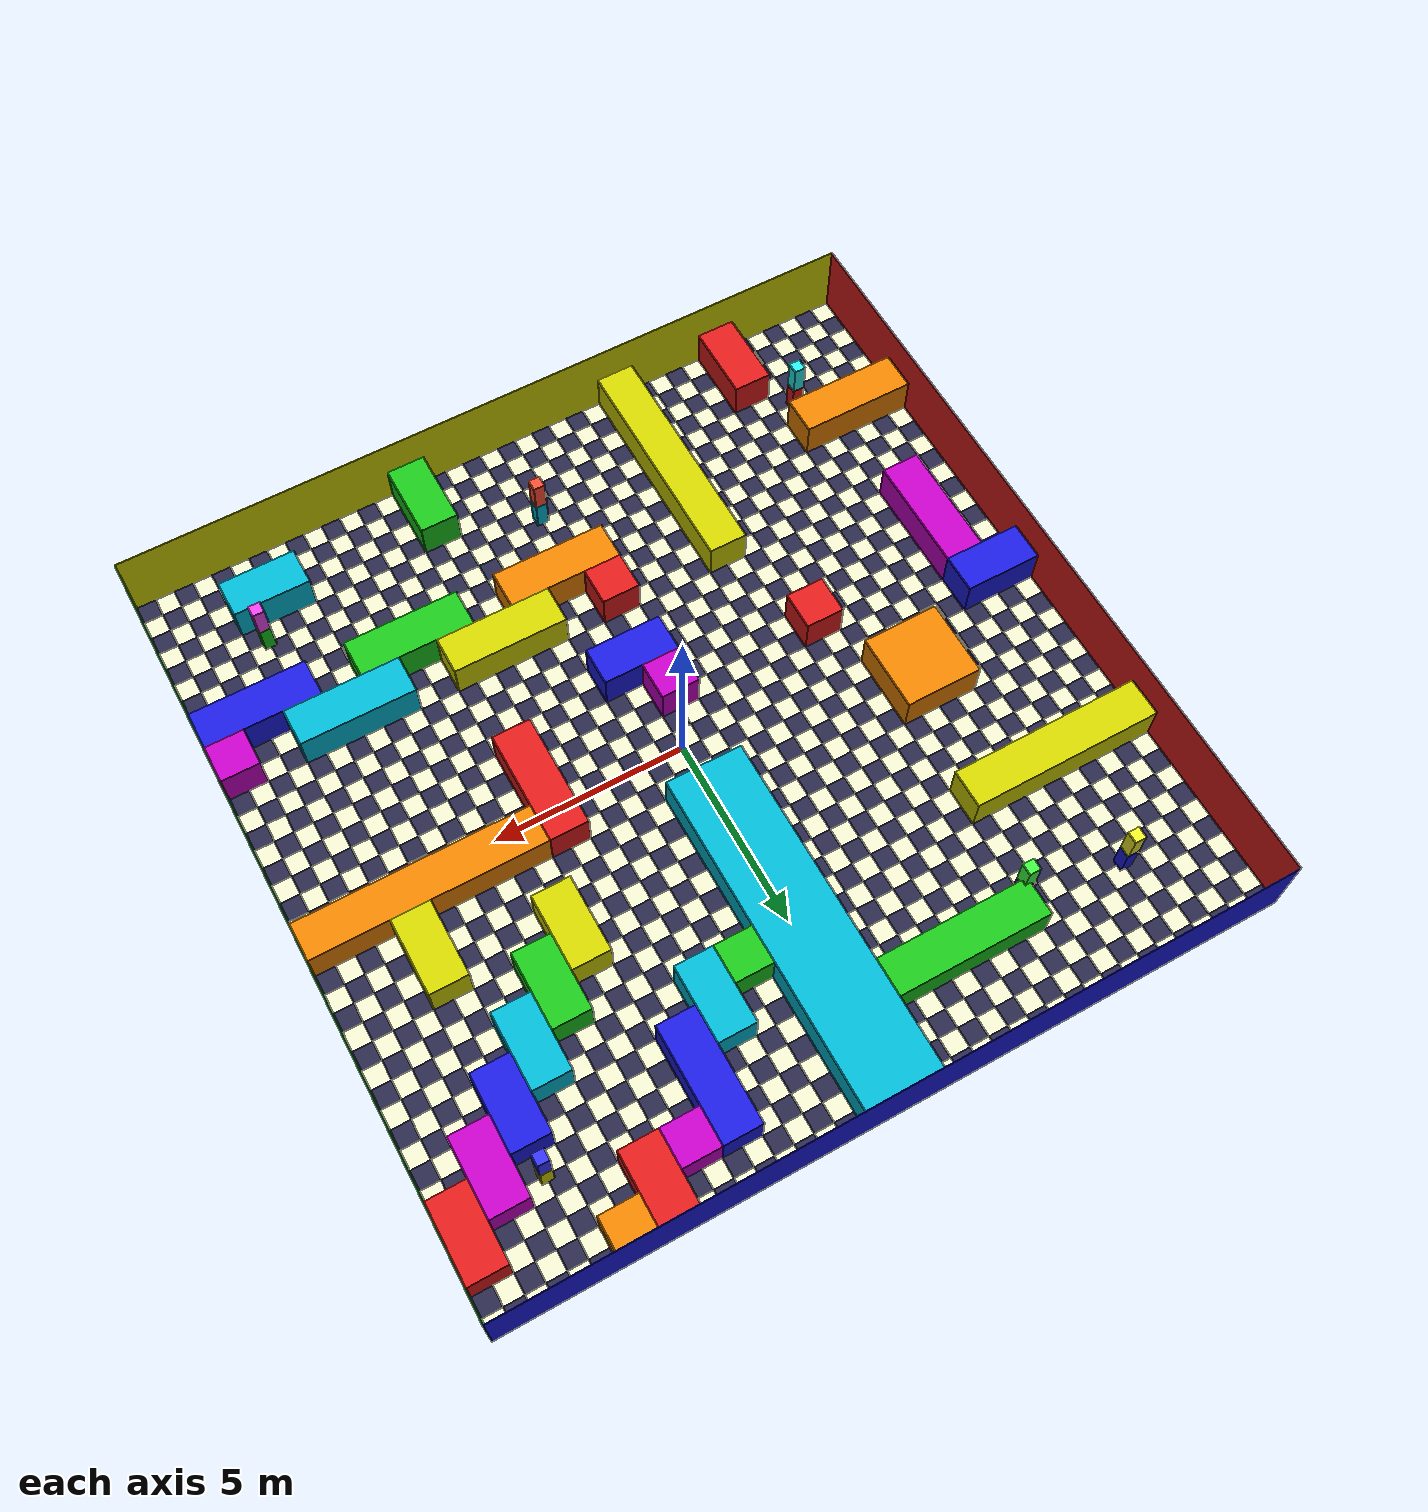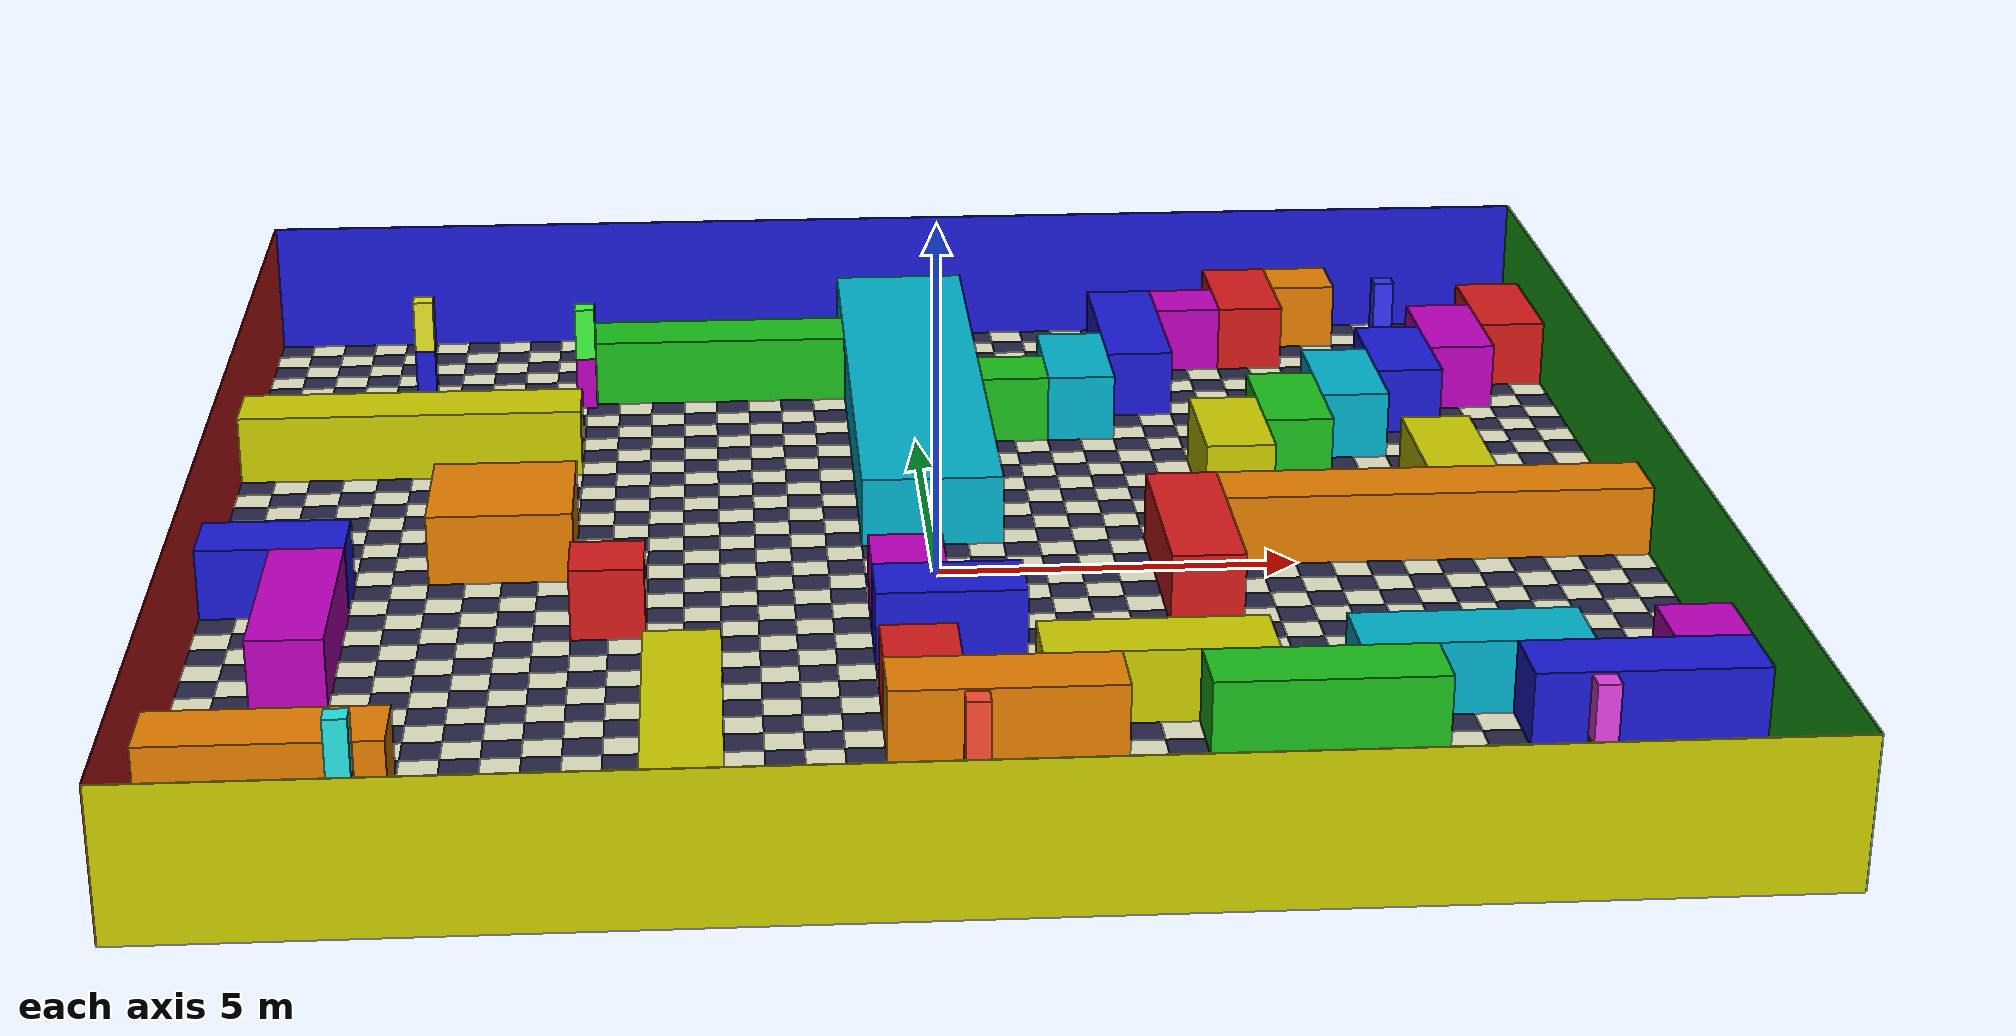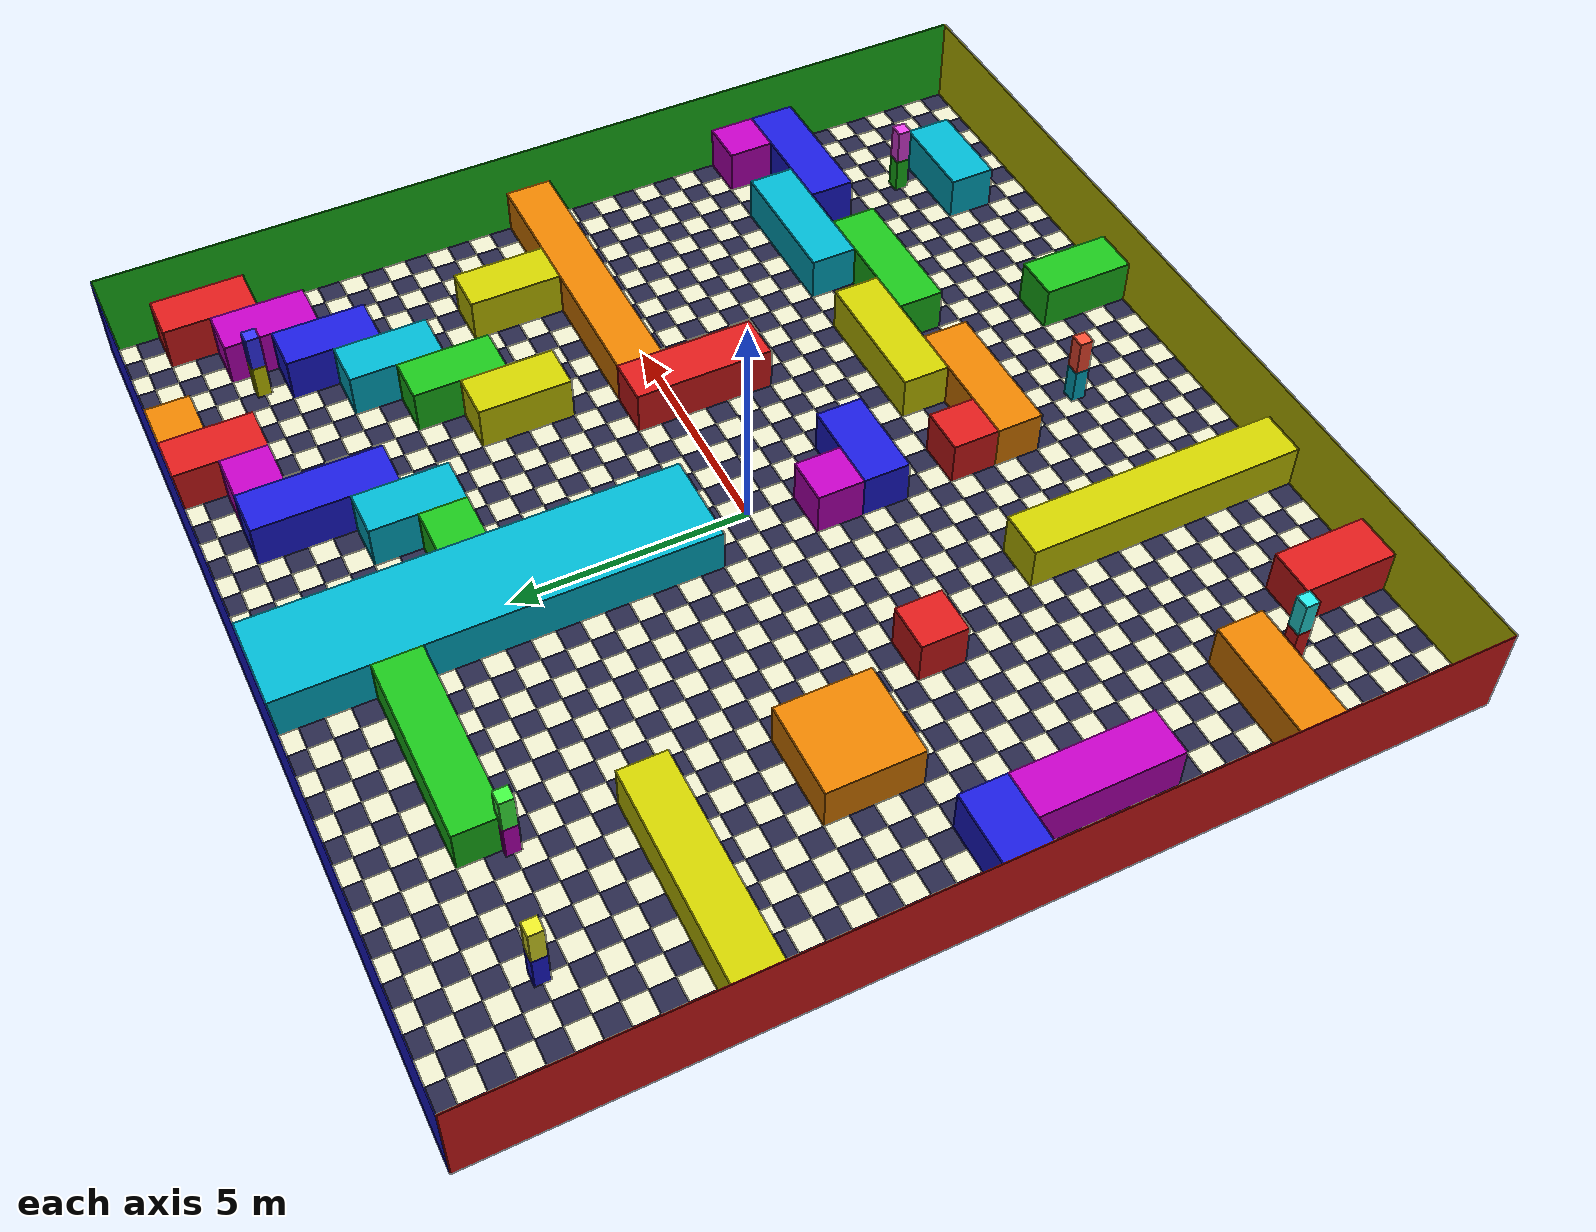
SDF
<?xml version="1.0"?>
<sdf version="1.8">
    <world name="maze_visualFeatures">
        <physics name="default_physics" type="dart">
            <max_step_size>0.003</max_step_size>
            <real_time_factor>1</real_time_factor>
            <real_time_update_rate>1000</real_time_update_rate>
        </physics>

        <!-- gz-sim system plugins (not loaded by default in all installs) -->
        <plugin filename="gz-sim-physics-system" name="gz::sim::systems::Physics"/>
        <plugin filename="gz-sim-user-commands-system" name="gz::sim::systems::UserCommands"/>
        <plugin filename="gz-sim-scene-broadcaster-system" name="gz::sim::systems::SceneBroadcaster"/>
        <plugin filename="gz-sim-sensors-system" name="gz::sim::systems::Sensors">
            <render_engine>ogre2</render_engine>
        </plugin>
        <plugin filename="gz-sim-imu-system" name="gz::sim::systems::Imu"/>
        <plugin filename="gz-sim-contact-system" name="gz::sim::systems::Contact"/>

        <light name="sun" type="directional">
            <cast_shadows>1</cast_shadows>
            <pose>0 0 10 0 -0 0</pose>
            <diffuse>0.8 0.8 0.8 1</diffuse>
            <specular>0.2 0.2 0.2 1</specular>
            <attenuation>
                <range>1000</range>
                <constant>0.9</constant>
                <linear>0.01</linear>
                <quadratic>0.001</quadratic>
            </attenuation>
            <direction>-0.5 0.1 -0.9</direction>
        </light>
        <gravity>0 0 -9.8</gravity>
        <magnetic_field>6e-06 2.3e-05 -4.2e-05</magnetic_field>
        <scene>
            <ambient>0.4 0.4 0.4 1</ambient>
            <background>0.7 0.7 0.7 1</background>
            <shadows>1</shadows>
        </scene>

        <!--
            FLOOR: 40x40 checkerboard of 0.5 m tiles — 1600 corners.
            Visual-only (no collision cost). Collision stays as a single plane.
        -->
        <model name="ground_plane">
            <static>1</static>
            <link name="link">
                <collision name="collision">
                    <geometry>
                        <plane>
                            <normal>0 0 1</normal>
                            <size>100 100</size>
                        </plane>
                    </geometry>
                    <surface><friction><ode/></friction></surface>
                </collision>
                <visual name="t0_0">
                    <pose>-9.75 -9.75 0.001 0 0 0</pose>
                    <geometry><box><size>0.5 0.5 0.001</size></box></geometry>
                    <material>
                        <ambient>0.9 0.9 0.78 1</ambient>
                        <diffuse>0.9 0.9 0.78 1</diffuse>
                    </material>
                </visual>
                <visual name="t0_1">
                    <pose>-9.25 -9.75 0.001 0 0 0</pose>
                    <geometry><box><size>0.5 0.5 0.001</size></box></geometry>
                    <material>
                        <ambient>0.15 0.15 0.28 1</ambient>
                        <diffuse>0.15 0.15 0.28 1</diffuse>
                    </material>
                </visual>
                <visual name="t0_2">
                    <pose>-8.75 -9.75 0.001 0 0 0</pose>
                    <geometry><box><size>0.5 0.5 0.001</size></box></geometry>
                    <material>
                        <ambient>0.9 0.9 0.78 1</ambient>
                        <diffuse>0.9 0.9 0.78 1</diffuse>
                    </material>
                </visual>
                <visual name="t0_3">
                    <pose>-8.25 -9.75 0.001 0 0 0</pose>
                    <geometry><box><size>0.5 0.5 0.001</size></box></geometry>
                    <material>
                        <ambient>0.15 0.15 0.28 1</ambient>
                        <diffuse>0.15 0.15 0.28 1</diffuse>
                    </material>
                </visual>
                <visual name="t0_4">
                    <pose>-7.75 -9.75 0.001 0 0 0</pose>
                    <geometry><box><size>0.5 0.5 0.001</size></box></geometry>
                    <material>
                        <ambient>0.9 0.9 0.78 1</ambient>
                        <diffuse>0.9 0.9 0.78 1</diffuse>
                    </material>
                </visual>
                <visual name="t0_5">
                    <pose>-7.25 -9.75 0.001 0 0 0</pose>
                    <geometry><box><size>0.5 0.5 0.001</size></box></geometry>
                    <material>
                        <ambient>0.15 0.15 0.28 1</ambient>
                        <diffuse>0.15 0.15 0.28 1</diffuse>
                    </material>
                </visual>
                <visual name="t0_6">
                    <pose>-6.75 -9.75 0.001 0 0 0</pose>
                    <geometry><box><size>0.5 0.5 0.001</size></box></geometry>
                    <material>
                        <ambient>0.9 0.9 0.78 1</ambient>
                        <diffuse>0.9 0.9 0.78 1</diffuse>
                    </material>
                </visual>
                <visual name="t0_7">
                    <pose>-6.25 -9.75 0.001 0 0 0</pose>
                    <geometry><box><size>0.5 0.5 0.001</size></box></geometry>
                    <material>
                        <ambient>0.15 0.15 0.28 1</ambient>
                        <diffuse>0.15 0.15 0.28 1</diffuse>
                    </material>
                </visual>
                <visual name="t0_8">
                    <pose>-5.75 -9.75 0.001 0 0 0</pose>
                    <geometry><box><size>0.5 0.5 0.001</size></box></geometry>
                    <material>
                        <ambient>0.9 0.9 0.78 1</ambient>
                        <diffuse>0.9 0.9 0.78 1</diffuse>
                    </material>
                </visual>
                <visual name="t0_9">
                    <pose>-5.25 -9.75 0.001 0 0 0</pose>
                    <geometry><box><size>0.5 0.5 0.001</size></box></geometry>
                    <material>
                        <ambient>0.15 0.15 0.28 1</ambient>
                        <diffuse>0.15 0.15 0.28 1</diffuse>
                    </material>
                </visual>
                <visual name="t0_10">
                    <pose>-4.75 -9.75 0.001 0 0 0</pose>
                    <geometry><box><size>0.5 0.5 0.001</size></box></geometry>
                    <material>
                        <ambient>0.9 0.9 0.78 1</ambient>
                        <diffuse>0.9 0.9 0.78 1</diffuse>
                    </material>
                </visual>
                <visual name="t0_11">
                    <pose>-4.25 -9.75 0.001 0 0 0</pose>
                    <geometry><box><size>0.5 0.5 0.001</size></box></geometry>
                    <material>
                        <ambient>0.15 0.15 0.28 1</ambient>
                        <diffuse>0.15 0.15 0.28 1</diffuse>
                    </material>
                </visual>
                <visual name="t0_12">
                    <pose>-3.75 -9.75 0.001 0 0 0</pose>
                    <geometry><box><size>0.5 0.5 0.001</size></box></geometry>
                    <material>
                        <ambient>0.9 0.9 0.78 1</ambient>
                        <diffuse>0.9 0.9 0.78 1</diffuse>
                    </material>
                </visual>
                <visual name="t0_13">
                    <pose>-3.25 -9.75 0.001 0 0 0</pose>
                    <geometry><box><size>0.5 0.5 0.001</size></box></geometry>
                    <material>
                        <ambient>0.15 0.15 0.28 1</ambient>
                        <diffuse>0.15 0.15 0.28 1</diffuse>
                    </material>
                </visual>
                <visual name="t0_14">
                    <pose>-2.75 -9.75 0.001 0 0 0</pose>
                    <geometry><box><size>0.5 0.5 0.001</size></box></geometry>
                    <material>
                        <ambient>0.9 0.9 0.78 1</ambient>
                        <diffuse>0.9 0.9 0.78 1</diffuse>
                    </material>
                </visual>
                <visual name="t0_15">
                    <pose>-2.25 -9.75 0.001 0 0 0</pose>
                    <geometry><box><size>0.5 0.5 0.001</size></box></geometry>
                    <material>
                        <ambient>0.15 0.15 0.28 1</ambient>
                        <diffuse>0.15 0.15 0.28 1</diffuse>
                    </material>
                </visual>
                <visual name="t0_16">
                    <pose>-1.75 -9.75 0.001 0 0 0</pose>
                    <geometry><box><size>0.5 0.5 0.001</size></box></geometry>
                    <material>
                        <ambient>0.9 0.9 0.78 1</ambient>
                        <diffuse>0.9 0.9 0.78 1</diffuse>
                    </material>
                </visual>
                <visual name="t0_17">
                    <pose>-1.25 -9.75 0.001 0 0 0</pose>
                    <geometry><box><size>0.5 0.5 0.001</size></box></geometry>
                    <material>
                        <ambient>0.15 0.15 0.28 1</ambient>
                        <diffuse>0.15 0.15 0.28 1</diffuse>
                    </material>
                </visual>
                <visual name="t0_18">
                    <pose>-0.75 -9.75 0.001 0 0 0</pose>
                    <geometry><box><size>0.5 0.5 0.001</size></box></geometry>
                    <material>
                        <ambient>0.9 0.9 0.78 1</ambient>
                        <diffuse>0.9 0.9 0.78 1</diffuse>
                    </material>
                </visual>
                <visual name="t0_19">
                    <pose>-0.25 -9.75 0.001 0 0 0</pose>
                    <geometry><box><size>0.5 0.5 0.001</size></box></geometry>
                    <material>
                        <ambient>0.15 0.15 0.28 1</ambient>
                        <diffuse>0.15 0.15 0.28 1</diffuse>
                    </material>
                </visual>
                <visual name="t0_20">
                    <pose>0.25 -9.75 0.001 0 0 0</pose>
                    <geometry><box><size>0.5 0.5 0.001</size></box></geometry>
                    <material>
                        <ambient>0.9 0.9 0.78 1</ambient>
                        <diffuse>0.9 0.9 0.78 1</diffuse>
                    </material>
                </visual>
                <visual name="t0_21">
                    <pose>0.75 -9.75 0.001 0 0 0</pose>
                    <geometry><box><size>0.5 0.5 0.001</size></box></geometry>
                    <material>
                        <ambient>0.15 0.15 0.28 1</ambient>
                        <diffuse>0.15 0.15 0.28 1</diffuse>
                    </material>
                </visual>
                <visual name="t0_22">
                    <pose>1.25 -9.75 0.001 0 0 0</pose>
                    <geometry><box><size>0.5 0.5 0.001</size></box></geometry>
                    <material>
                        <ambient>0.9 0.9 0.78 1</ambient>
                        <diffuse>0.9 0.9 0.78 1</diffuse>
                    </material>
                </visual>
                <visual name="t0_23">
                    <pose>1.75 -9.75 0.001 0 0 0</pose>
                    <geometry><box><size>0.5 0.5 0.001</size></box></geometry>
                    <material>
                        <ambient>0.15 0.15 0.28 1</ambient>
                        <diffuse>0.15 0.15 0.28 1</diffuse>
                    </material>
                </visual>
                <visual name="t0_24">
                    <pose>2.25 -9.75 0.001 0 0 0</pose>
                    <geometry><box><size>0.5 0.5 0.001</size></box></geometry>
                    <material>
                        <ambient>0.9 0.9 0.78 1</ambient>
                        <diffuse>0.9 0.9 0.78 1</diffuse>
                    </material>
                </visual>
                <visual name="t0_25">
                    <pose>2.75 -9.75 0.001 0 0 0</pose>
                    <geometry><box><size>0.5 0.5 0.001</size></box></geometry>
                    <material>
                        <ambient>0.15 0.15 0.28 1</ambient>
                        <diffuse>0.15 0.15 0.28 1</diffuse>
                    </material>
                </visual>
                <visual name="t0_26">
                    <pose>3.25 -9.75 0.001 0 0 0</pose>
                    <geometry><box><size>0.5 0.5 0.001</size></box></geometry>
                    <material>
                        <ambient>0.9 0.9 0.78 1</ambient>
                        <diffuse>0.9 0.9 0.78 1</diffuse>
                    </material>
                </visual>
                <visual name="t0_27">
                    <pose>3.75 -9.75 0.001 0 0 0</pose>
                    <geometry><box><size>0.5 0.5 0.001</size></box></geometry>
                    <material>
                        <ambient>0.15 0.15 0.28 1</ambient>
                        <diffuse>0.15 0.15 0.28 1</diffuse>
                    </material>
                </visual>
                <visual name="t0_28">
                    <pose>4.25 -9.75 0.001 0 0 0</pose>
                    <geometry><box><size>0.5 0.5 0.001</size></box></geometry>
                    <material>
                        <ambient>0.9 0.9 0.78 1</ambient>
                        <diffuse>0.9 0.9 0.78 1</diffuse>
                    </material>
                </visual>
                <visual name="t0_29">
                    <pose>4.75 -9.75 0.001 0 0 0</pose>
                    <geometry><box><size>0.5 0.5 0.001</size></box></geometry>
                    <material>
                        <ambient>0.15 0.15 0.28 1</ambient>
                        <diffuse>0.15 0.15 0.28 1</diffuse>
                    </material>
                </visual>
                <visual name="t0_30">
                    <pose>5.25 -9.75 0.001 0 0 0</pose>
                    <geometry><box><size>0.5 0.5 0.001</size></box></geometry>
                    <material>
                        <ambient>0.9 0.9 0.78 1</ambient>
                        <diffuse>0.9 0.9 0.78 1</diffuse>
                    </material>
                </visual>
                <visual name="t0_31">
                    <pose>5.75 -9.75 0.001 0 0 0</pose>
                    <geometry><box><size>0.5 0.5 0.001</size></box></geometry>
                    <material>
                        <ambient>0.15 0.15 0.28 1</ambient>
                        <diffuse>0.15 0.15 0.28 1</diffuse>
                    </material>
                </visual>
                <visual name="t0_32">
                    <pose>6.25 -9.75 0.001 0 0 0</pose>
                    <geometry><box><size>0.5 0.5 0.001</size></box></geometry>
                    <material>
                        <ambient>0.9 0.9 0.78 1</ambient>
                        <diffuse>0.9 0.9 0.78 1</diffuse>
                    </material>
                </visual>
                <visual name="t0_33">
                    <pose>6.75 -9.75 0.001 0 0 0</pose>
                    <geometry><box><size>0.5 0.5 0.001</size></box></geometry>
                    <material>
                        <ambient>0.15 0.15 0.28 1</ambient>
                        <diffuse>0.15 0.15 0.28 1</diffuse>
                    </material>
                </visual>
                <visual name="t0_34">
                    <pose>7.25 -9.75 0.001 0 0 0</pose>
                    <geometry><box><size>0.5 0.5 0.001</size></box></geometry>
                    <material>
                        <ambient>0.9 0.9 0.78 1</ambient>
                        <diffuse>0.9 0.9 0.78 1</diffuse>
                    </material>
                </visual>
                <visual name="t0_35">
                    <pose>7.75 -9.75 0.001 0 0 0</pose>
                    <geometry><box><size>0.5 0.5 0.001</size></box></geometry>
                    <material>
                        <ambient>0.15 0.15 0.28 1</ambient>
                        <diffuse>0.15 0.15 0.28 1</diffuse>
                    </material>
                </visual>
                <visual name="t0_36">
                    <pose>8.25 -9.75 0.001 0 0 0</pose>
                    <geometry><box><size>0.5 0.5 0.001</size></box></geometry>
                    <material>
                        <ambient>0.9 0.9 0.78 1</ambient>
                        <diffuse>0.9 0.9 0.78 1</diffuse>
                    </material>
                </visual>
                <visual name="t0_37">
                    <pose>8.75 -9.75 0.001 0 0 0</pose>
                    <geometry><box><size>0.5 0.5 0.001</size></box></geometry>
                    <material>
                        <ambient>0.15 0.15 0.28 1</ambient>
                        <diffuse>0.15 0.15 0.28 1</diffuse>
                    </material>
                </visual>
                <visual name="t0_38">
                    <pose>9.25 -9.75 0.001 0 0 0</pose>
                    <geometry><box><size>0.5 0.5 0.001</size></box></geometry>
                    <material>
                        <ambient>0.9 0.9 0.78 1</ambient>
                        <diffuse>0.9 0.9 0.78 1</diffuse>
                    </material>
                </visual>
                <visual name="t0_39">
                    <pose>9.75 -9.75 0.001 0 0 0</pose>
                    <geometry><box><size>0.5 0.5 0.001</size></box></geometry>
                    <material>
                        <ambient>0.15 0.15 0.28 1</ambient>
                        <diffuse>0.15 0.15 0.28 1</diffuse>
                    </material>
                </visual>
                <visual name="t1_0">
                    <pose>-9.75 -9.25 0.001 0 0 0</pose>
                    <geometry><box><size>0.5 0.5 0.001</size></box></geometry>
                    <material>
                        <ambient>0.15 0.15 0.28 1</ambient>
                        <diffuse>0.15 0.15 0.28 1</diffuse>
                    </material>
                </visual>
                <visual name="t1_1">
                    <pose>-9.25 -9.25 0.001 0 0 0</pose>
                    <geometry><box><size>0.5 0.5 0.001</size></box></geometry>
                    <material>
                        <ambient>0.9 0.9 0.78 1</ambient>
                        <diffuse>0.9 0.9 0.78 1</diffuse>
                    </material>
                </visual>
                <visual name="t1_2">
                    <pose>-8.75 -9.25 0.001 0 0 0</pose>
                    <geometry><box><size>0.5 0.5 0.001</size></box></geometry>
                    <material>
                        <ambient>0.15 0.15 0.28 1</ambient>
                        <diffuse>0.15 0.15 0.28 1</diffuse>
                    </material>
                </visual>
                <visual name="t1_3">
                    <pose>-8.25 -9.25 0.001 0 0 0</pose>
                    <geometry><box><size>0.5 0.5 0.001</size></box></geometry>
                    <material>
                        <ambient>0.9 0.9 0.78 1</ambient>
                        <diffuse>0.9 0.9 0.78 1</diffuse>
                    </material>
                </visual>
                <visual name="t1_4">
                    <pose>-7.75 -9.25 0.001 0 0 0</pose>
                    <geometry><box><size>0.5 0.5 0.001</size></box></geometry>
                    <material>
                        <ambient>0.15 0.15 0.28 1</ambient>
                        <diffuse>0.15 0.15 0.28 1</diffuse>
                    </material>
                </visual>
                <visual name="t1_5">
                    <pose>-7.25 -9.25 0.001 0 0 0</pose>
                    <geometry><box><size>0.5 0.5 0.001</size></box></geometry>
                    <material>
                        <ambient>0.9 0.9 0.78 1</ambient>
                        <diffuse>0.9 0.9 0.78 1</diffuse>
                    </material>
                </visual>
                <visual name="t1_6">
                    <pose>-6.75 -9.25 0.001 0 0 0</pose>
                    <geometry><box><size>0.5 0.5 0.001</size></box></geometry>
                    <material>
                        <ambient>0.15 0.15 0.28 1</ambient>
                        <diffuse>0.15 0.15 0.28 1</diffuse>
                    </material>
                </visual>
                <visual name="t1_7">
                    <pose>-6.25 -9.25 0.001 0 0 0</pose>
                    <geometry><box><size>0.5 0.5 0.001</size></box></geometry>
                    <material>
                        <ambient>0.9 0.9 0.78 1</ambient>
                        <diffuse>0.9 0.9 0.78 1</diffuse>
                    </material>
                </visual>
                <visual name="t1_8">
                    <pose>-5.75 -9.25 0.001 0 0 0</pose>
                    <geometry><box><size>0.5 0.5 0.001</size></box></geometry>
                    <material>
                        <ambient>0.15 0.15 0.28 1</ambient>
                        <diffuse>0.15 0.15 0.28 1</diffuse>
                    </material>
                </visual>
                <visual name="t1_9">
                    <pose>-5.25 -9.25 0.001 0 0 0</pose>
                    <geometry><box><size>0.5 0.5 0.001</size></box></geometry>
                    <material>
                        <ambient>0.9 0.9 0.78 1</ambient>
                        <diffuse>0.9 0.9 0.78 1</diffuse>
                    </material>
                </visual>
                <visual name="t1_10">
                    <pose>-4.75 -9.25 0.001 0 0 0</pose>
                    <geometry><box><size>0.5 0.5 0.001</size></box></geometry>
                    <material>
                        <ambient>0.15 0.15 0.28 1</ambient>
                        <diffuse>0.15 0.15 0.28 1</diffuse>
                    </material>
                </visual>
                <visual name="t1_11">
                    <pose>-4.25 -9.25 0.001 0 0 0</pose>
                    <geometry><box><size>0.5 0.5 0.001</size></box></geometry>
                    <material>
                        <ambient>0.9 0.9 0.78 1</ambient>
                        <diffuse>0.9 0.9 0.78 1</diffuse>
                    </material>
                </visual>
                <visual name="t1_12">
                    <pose>-3.75 -9.25 0.001 0 0 0</pose>
                    <geometry><box><size>0.5 0.5 0.001</size></box></geometry>
                    <material>
                        <ambient>0.15 0.15 0.28 1</ambient>
                        <diffuse>0.15 0.15 0.28 1</diffuse>
                    </material>
                </visual>
                <visual name="t1_13">
                    <pose>-3.25 -9.25 0.001 0 0 0</pose>
                    <geometry><box><size>0.5 0.5 0.001</size></box></geometry>
                    <material>
                        <ambient>0.9 0.9 0.78 1</ambient>
                        <diffuse>0.9 0.9 0.78 1</diffuse>
                    </material>
                </visual>
                <visual name="t1_14">
                    <pose>-2.75 -9.25 0.001 0 0 0</pose>
                    <geometry><box><size>0.5 0.5 0.001</size></box></geometry>
                    <material>
                        <ambient>0.15 0.15 0.28 1</ambient>
                        <diffuse>0.15 0.15 0.28 1</diffuse>
                    </material>
                </visual>
                <visual name="t1_15">
                    <pose>-2.25 -9.25 0.001 0 0 0</pose>
                    <geometry><box><size>0.5 0.5 0.001</size></box></geometry>
                    <material>
                        <ambient>0.9 0.9 0.78 1</ambient>
                        <diffuse>0.9 0.9 0.78 1</diffuse>
                    </material>
                </visual>
                <visual name="t1_16">
                    <pose>-1.75 -9.25 0.001 0 0 0</pose>
                    <geometry><box><size>0.5 0.5 0.001</size></box></geometry>
                    <material>
                        <ambient>0.15 0.15 0.28 1</ambient>
                        <diffuse>0.15 0.15 0.28 1</diffuse>
                    </material>
                </visual>
                <visual name="t1_17">
                    <pose>-1.25 -9.25 0.001 0 0 0</pose>
                    <geometry><box><size>0.5 0.5 0.001</size></box></geometry>
                    <material>
                        <ambient>0.9 0.9 0.78 1</ambient>
                        <diffuse>0.9 0.9 0.78 1</diffuse>
                    </material>
                </visual>
                <visual name="t1_18">
                    <pose>-0.75 -9.25 0.001 0 0 0</pose>
                    <geometry><box><size>0.5 0.5 0.001</size></box></geometry>
                    <material>
                        <ambient>0.15 0.15 0.28 1</ambient>
                        <diffuse>0.15 0.15 0.28 1</diffuse>
                    </material>
                </visual>
                <visual name="t1_19">
                    <pose>-0.25 -9.25 0.001 0 0 0</pose>
                    <geometry><box><size>0.5 0.5 0.001</size></box></geometry>
                    <material>
                        <ambient>0.9 0.9 0.78 1</ambient>
                        <diffuse>0.9 0.9 0.78 1</diffuse>
                    </material>
                </visual>
                <visual name="t1_20">
                    <pose>0.25 -9.25 0.001 0 0 0</pose>
                    <geometry><box><size>0.5 0.5 0.001</size></box></geometry>
                    <material>
                        <ambient>0.15 0.15 0.28 1</ambient>
                        <diffuse>0.15 0.15 0.28 1</diffuse>
                    </material>
                </visual>
                <visual name="t1_21">
                    <pose>0.75 -9.25 0.001 0 0 0</pose>
                    <geometry><box><size>0.5 0.5 0.001</size></box></geometry>
                    <material>
                        <ambient>0.9 0.9 0.78 1</ambient>
                        <diffuse>0.9 0.9 0.78 1</diffuse>
                    </material>
                </visual>
                <visual name="t1_22">
                    <pose>1.25 -9.25 0.001 0 0 0</pose>
                    <geometry><box><size>0.5 0.5 0.001</size></box></geometry>
                    <material>
                        <ambient>0.15 0.15 0.28 1</ambient>
                        <diffuse>0.15 0.15 0.28 1</diffuse>
                    </material>
                </visual>
                <visual name="t1_23">
                    <pose>1.75 -9.25 0.001 0 0 0</pose>
                    <geometry><box><size>0.5 0.5 0.001</size></box></geometry>
                    <material>
                        <ambient>0.9 0.9 0.78 1</ambient>
                        <diffuse>0.9 0.9 0.78 1</diffuse>
                    </material>
                </visual>
                <visual name="t1_24">
                    <pose>2.25 -9.25 0.001 0 0 0</pose>
                    <geometry><box><size>0.5 0.5 0.001</size></box></geometry>
                    <material>
                        <ambient>0.15 0.15 0.28 1</ambient>
                        <diffuse>0.15 0.15 0.28 1</diffuse>
                    </material>
                </visual>
                <visual name="t1_25">
                    <pose>2.75 -9.25 0.001 0 0 0</pose>
                    <geometry><box><size>0.5 0.5 0.001</size></box></geometry>
                    <material>
                        <ambient>0.9 0.9 0.78 1</ambient>
                        <diffuse>0.9 0.9 0.78 1</diffuse>
                    </material>
                </visual>
                <visual name="t1_26">
                    <pose>3.25 -9.25 0.001 0 0 0</pose>
                    <geometry><box><size>0.5 0.5 0.001</size></box></geometry>
                    <material>
                        <ambient>0.15 0.15 0.28 1</ambient>
                        <diffuse>0.15 0.15 0.28 1</diffuse>
                    </material>
                </visual>
                <visual name="t1_27">
                    <pose>3.75 -9.25 0.001 0 0 0</pose>
                    <geometry><box><size>0.5 0.5 0.001</size></box></geometry>
                    <material>
                        <ambient>0.9 0.9 0.78 1</ambient>
                        <diffuse>0.9 0.9 0.78 1</diffuse>
                    </material>
                </visual>
                <visual name="t1_28">
                    <pose>4.25 -9.25 0.001 0 0 0</pose>
                    <geometry><box><size>0.5 0.5 0.001</size></box></geometry>
                    <material>
                        <ambient>0.15 0.15 0.28 1</ambient>
                        <diffuse>0.15 0.15 0.28 1</diffuse>
                    </material>
                </visual>
                <visual name="t1_29">
                    <pose>4.75 -9.25 0.001 0 0 0</pose>
                    <geometry><box><size>0.5 0.5 0.001</size></box></geometry>
                    <material>
                        <ambient>0.9 0.9 0.78 1</ambient>
                        <diffuse>0.9 0.9 0.78 1</diffuse>
                    </material>
                </visual>
                <visual name="t1_30">
                    <pose>5.25 -9.25 0.001 0 0 0</pose>
                    <geometry><box><size>0.5 0.5 0.001</size></box></geometry>
                    <material>
                        <ambient>0.15 0.15 0.28 1</ambient>
                        <diffuse>0.15 0.15 0.28 1</diffuse>
                    </material>
                </visual>
                <visual name="t1_31">
                    <pose>5.75 -9.25 0.001 0 0 0</pose>
                    <geometry><box><size>0.5 0.5 0.001</size></box></geometry>
                    <material>
                        <ambient>0.9 0.9 0.78 1</ambient>
                        <diffuse>0.9 0.9 0.78 1</diffuse>
                    </material>
                </visual>
                <visual name="t1_32">
                    <pose>6.25 -9.25 0.001 0 0 0</pose>
                    <geometry><box><size>0.5 0.5 0.001</size></box></geometry>
                    <material>
                        <ambient>0.15 0.15 0.28 1</ambient>
                        <diffuse>0.15 0.15 0.28 1</diffuse>
                    </material>
                </visual>
                <visual name="t1_33">
                    <pose>6.75 -9.25 0.001 0 0 0</pose>
                    <geometry><box><size>0.5 0.5 0.001</size></box></geometry>
                    <material>
                        <ambient>0.9 0.9 0.78 1</ambient>
                        <diffuse>0.9 0.9 0.78 1</diffuse>
                    </material>
                </visual>
                <visual name="t1_34">
                    <pose>7.25 -9.25 0.001 0 0 0</pose>
                    <geometry><box><size>0.5 0.5 0.001</size></box></geometry>
                    <material>
                        <ambient>0.15 0.15 0.28 1</ambient>
                        <diffuse>0.15 0.15 0.28 1</diffuse>
                    </material>
                </visual>
                <visual name="t1_35">
                    <pose>7.75 -9.25 0.001 0 0 0</pose>
                    <geometry><box><size>0.5 0.5 0.001</size></box></geometry>
                    <material>
                        <ambient>0.9 0.9 0.78 1</ambient>
                        <diffuse>0.9 0.9 0.78 1</diffuse>
                    </material>
                </visual>
                <visual name="t1_36">
                    <pose>8.25 -9.25 0.001 0 0 0</pose>
                    <geometry><box><size>0.5 0.5 0.001</size></box></geometry>
                    <material>
                        <ambient>0.15 0.15 0.28 1</ambient>
                        <diffuse>0.15 0.15 0.28 1</diffuse>
                    </material>
                </visual>
                <visual name="t1_37">
                    <pose>8.75 -9.25 0.001 0 0 0</pose>
                    <geometry><box><size>0.5 0.5 0.001</size></box></geometry>
                    <material>
                        <ambient>0.9 0.9 0.78 1</ambient>
                        <diffuse>0.9 0.9 0.78 1</diffuse>
                    </material>
                </visual>
                <visual name="t1_38">
                    <pose>9.25 -9.25 0.001 0 0 0</pose>
                    <geometry><box><size>0.5 0.5 0.001</size></box></geometry>
                    <material>
                        <ambient>0.15 0.15 0.28 1</ambient>
                        <diffuse>0.15 0.15 0.28 1</diffuse>
                    </material>
                </visual>
                <visual name="t1_39">
                    <pose>9.75 -9.25 0.001 0 0 0</pose>
                    <geometry><box><size>0.5 0.5 0.001</size></box></geometry>
                    <material>
                        <ambient>0.9 0.9 0.78 1</ambient>
                        <diffuse>0.9 0.9 0.78 1</diffuse>
                    </material>
                </visual>
                <visual name="t2_0">
                    <pose>-9.75 -8.75 0.001 0 0 0</pose>
                    <geometry><box><size>0.5 0.5 0.001</size></box></geometry>
                    <material>
                        <ambient>0.9 0.9 0.78 1</ambient>
                        <diffuse>0.9 0.9 0.78 1</diffuse>
                    </material>
                </visual>
                <visual name="t2_1">
                    <pose>-9.25 -8.75 0.001 0 0 0</pose>
                    <geometry><box><size>0.5 0.5 0.001</size></box></geometry>
                    <material>
                        <ambient>0.15 0.15 0.28 1</ambient>
                        <diffuse>0.15 0.15 0.28 1</diffuse>
                    </material>
                </visual>
                <visual name="t2_2">
                    <pose>-8.75 -8.75 0.001 0 0 0</pose>
                    <geometry><box><size>0.5 0.5 0.001</size></box></geometry>
                    <material>
                        <ambient>0.9 0.9 0.78 1</ambient>
                        <diffuse>0.9 0.9 0.78 1</diffuse>
                    </material>
                </visual>
                <visual name="t2_3">
                    <pose>-8.25 -8.75 0.001 0 0 0</pose>
                    <geometry><box><size>0.5 0.5 0.001</size></box></geometry>
                    <material>
                        <ambient>0.15 0.15 0.28 1</ambient>
                        <diffuse>0.15 0.15 0.28 1</diffuse>
                    </material>
                </visual>
                <visual name="t2_4">
                    <pose>-7.75 -8.75 0.001 0 0 0</pose>
                    <geometry><box><size>0.5 0.5 0.001</size></box></geometry>
                    <material>
                        <ambient>0.9 0.9 0.78 1</ambient>
                        <diffuse>0.9 0.9 0.78 1</diffuse>
                    </material>
                </visual>
                <visual name="t2_5">
                    <pose>-7.25 -8.75 0.001 0 0 0</pose>
                    <geometry><box><size>0.5 0.5 0.001</size></box></geometry>
                    <material>
                        <ambient>0.15 0.15 0.28 1</ambient>
                        <diffuse>0.15 0.15 0.28 1</diffuse>
                    </material>
                </visual>
                <visual name="t2_6">
                    <pose>-6.75 -8.75 0.001 0 0 0</pose>
                    <geometry><box><size>0.5 0.5 0.001</size></box></geometry>
                    <material>
                        <ambient>0.9 0.9 0.78 1</ambient>
                        <diffuse>0.9 0.9 0.78 1</diffuse>
                    </material>
                </visual>
                <visual name="t2_7">
                    <pose>-6.25 -8.75 0.001 0 0 0</pose>
                    <geometry><box><size>0.5 0.5 0.001</size></box></geometry>
                    <material>
                        <ambient>0.15 0.15 0.28 1</ambient>
                        <diffuse>0.15 0.15 0.28 1</diffuse>
                    </material>
                </visual>
                <visual name="t2_8">
                    <pose>-5.75 -8.75 0.001 0 0 0</pose>
                    <geometry><box><size>0.5 0.5 0.001</size></box></geometry>
                    <material>
                        <ambient>0.9 0.9 0.78 1</ambient>
                        <diffuse>0.9 0.9 0.78 1</diffuse>
                    </material>
                </visual>
                <visual name="t2_9">
                    <pose>-5.25 -8.75 0.001 0 0 0</pose>
                    <geometry><box><size>0.5 0.5 0.001</size></box></geometry>
                    <material>
                        <ambient>0.15 0.15 0.28 1</ambient>
                        <diffuse>0.15 0.15 0.28 1</diffuse>
                    </material>
                </visual>
                <visual name="t2_10">
                    <pose>-4.75 -8.75 0.001 0 0 0</pose>
                    <geometry><box><size>0.5 0.5 0.001</size></box></geometry>
                    <material>
                        <ambient>0.9 0.9 0.78 1</ambient>
                        <diffuse>0.9 0.9 0.78 1</diffuse>
                    </material>
                </visual>
                <visual name="t2_11">
                    <pose>-4.25 -8.75 0.001 0 0 0</pose>
                    <geometry><box><size>0.5 0.5 0.001</size></box></geometry>
                    <material>
                        <ambient>0.15 0.15 0.28 1</ambient>
                        <diffuse>0.15 0.15 0.28 1</diffuse>
                    </material>
                </visual>
                <visual name="t2_12">
                    <pose>-3.75 -8.75 0.001 0 0 0</pose>
                    <geometry><box><size>0.5 0.5 0.001</size></box></geometry>
                    <material>
                        <ambient>0.9 0.9 0.78 1</ambient>
                        <diffuse>0.9 0.9 0.78 1</diffuse>
                    </material>
                </visual>
                <visual name="t2_13">
                    <pose>-3.25 -8.75 0.001 0 0 0</pose>
                    <geometry><box><size>0.5 0.5 0.001</size></box></geometry>
                    <material>
                        <ambient>0.15 0.15 0.28 1</ambient>
                        <diffuse>0.15 0.15 0.28 1</diffuse>
                    </material>
                </visual>
                <visual name="t2_14">
                    <pose>-2.75 -8.75 0.001 0 0 0</pose>
                    <geometry><box><size>0.5 0.5 0.001</size></box></geometry>
                    <material>
                        <ambient>0.9 0.9 0.78 1</ambient>
                        <diffuse>0.9 0.9 0.78 1</diffuse>
                    </material>
                </visual>
                <visual name="t2_15">
                    <pose>-2.25 -8.75 0.001 0 0 0</pose>
                    <geometry><box><size>0.5 0.5 0.001</size></box></geometry>
                    <material>
                        <ambient>0.15 0.15 0.28 1</ambient>
                        <diffuse>0.15 0.15 0.28 1</diffuse>
                    </material>
                </visual>
                <visual name="t2_16">
                    <pose>-1.75 -8.75 0.001 0 0 0</pose>
                    <geometry><box><size>0.5 0.5 0.001</size></box></geometry>
                    <material>
                        <ambient>0.9 0.9 0.78 1</ambient>
                        <diffuse>0.9 0.9 0.78 1</diffuse>
                    </material>
                </visual>
                <visual name="t2_17">
                    <pose>-1.25 -8.75 0.001 0 0 0</pose>
                    <geometry><box><size>0.5 0.5 0.001</size></box></geometry>
                    <material>
                        <ambient>0.15 0.15 0.28 1</ambient>
                        <diffuse>0.15 0.15 0.28 1</diffuse>
                    </material>
                </visual>
                <visual name="t2_18">
                    <pose>-0.75 -8.75 0.001 0 0 0</pose>
                    <geometry><box><size>0.5 0.5 0.001</size></box></geometry>
                    <material>
                        <ambient>0.9 0.9 0.78 1</ambient>
                        <diffuse>0.9 0.9 0.78 1</diffuse>
                    </material>
                </visual>
                <visual name="t2_19">
                    <pose>-0.25 -8.75 0.001 0 0 0</pose>
                    <geometry><box><size>0.5 0.5 0.001</size></box></geometry>
                    <material>
                        <ambient>0.15 0.15 0.28 1</ambient>
                        <diffuse>0.15 0.15 0.28 1</diffuse>
                    </material>
                </visual>
                <visual name="t2_20">
                    <pose>0.25 -8.75 0.001 0 0 0</pose>
                    <geometry><box><size>0.5 0.5 0.001</size></box></geometry>
                    <material>
                        <ambient>0.9 0.9 0.78 1</ambient>
                        <diffuse>0.9 0.9 0.78 1</diffuse>
                    </material>
                </visual>
                <visual name="t2_21">
                    <pose>0.75 -8.75 0.001 0 0 0</pose>
                    <geometry><box><size>0.5 0.5 0.001</size></box></geometry>
                    <material>
                        <ambient>0.15 0.15 0.28 1</ambient>
                        <diffuse>0.15 0.15 0.28 1</diffuse>
                    </material>
                </visual>
                <visual name="t2_22">
                    <pose>1.25 -8.75 0.001 0 0 0</pose>
                    <geometry><box><size>0.5 0.5 0.001</size></box></geometry>
                    <material>
                        <ambient>0.9 0.9 0.78 1</ambient>
                        <diffuse>0.9 0.9 0.78 1</diffuse>
                    </material>
                </visual>
                <visual name="t2_23">
                    <pose>1.75 -8.75 0.001 0 0 0</pose>
                    <geometry><box><size>0.5 0.5 0.001</size></box></geometry>
                    <material>
                        <ambient>0.15 0.15 0.28 1</ambient>
                        <diffuse>0.15 0.15 0.28 1</diffuse>
                    </material>
                </visual>
                <visual name="t2_24">
                    <pose>2.25 -8.75 0.001 0 0 0</pose>
                    <geometry><box><size>0.5 0.5 0.001</size></box></geometry>
                    <material>
                        <ambient>0.9 0.9 0.78 1</ambient>
                        <diffuse>0.9 0.9 0.78 1</diffuse>
                    </material>
                </visual>
                <visual name="t2_25">
                    <pose>2.75 -8.75 0.001 0 0 0</pose>
                    <geometry><box><size>0.5 0.5 0.001</size></box></geometry>
                    <material>
                        <ambient>0.15 0.15 0.28 1</ambient>
                        <diffuse>0.15 0.15 0.28 1</diffuse>
                    </material>
                </visual>
                <visual name="t2_26">
                    <pose>3.25 -8.75 0.001 0 0 0</pose>
                    <geometry><box><size>0.5 0.5 0.001</size></box></geometry>
                    <material>
                        <ambient>0.9 0.9 0.78 1</ambient>
                        <diffuse>0.9 0.9 0.78 1</diffuse>
                    </material>
                </visual>
                <visual name="t2_27">
                    <pose>3.75 -8.75 0.001 0 0 0</pose>
                    <geometry><box><size>0.5 0.5 0.001</size></box></geometry>
                    <material>
                        <ambient>0.15 0.15 0.28 1</ambient>
                        <diffuse>0.15 0.15 0.28 1</diffuse>
                    </material>
                </visual>
                <visual name="t2_28">
                    <pose>4.25 -8.75 0.001 0 0 0</pose>
                    <geometry><box><size>0.5 0.5 0.001</size></box></geometry>
                    <material>
                        <ambient>0.9 0.9 0.78 1</ambient>
                        <diffuse>0.9 0.9 0.78 1</diffuse>
                    </material>
                </visual>
                <visual name="t2_29">
                    <pose>4.75 -8.75 0.001 0 0 0</pose>
                    <geometry><box><size>0.5 0.5 0.001</size></box></geometry>
                    <material>
                        <ambient>0.15 0.15 0.28 1</ambient>
                        <diffuse>0.15 0.15 0.28 1</diffuse>
                    </material>
                </visual>
                <visual name="t2_30">
                    <pose>5.25 -8.75 0.001 0 0 0</pose>
                    <geometry><box><size>0.5 0.5 0.001</size></box></geometry>
                    <material>
                        <ambient>0.9 0.9 0.78 1</ambient>
                        <diffuse>0.9 0.9 0.78 1</diffuse>
                    </material>
                </visual>
                <visual name="t2_31">
                    <pose>5.75 -8.75 0.001 0 0 0</pose>
                    <geometry><box><size>0.5 0.5 0.001</size></box></geometry>
                    <material>
                        <ambient>0.15 0.15 0.28 1</ambient>
                        <diffuse>0.15 0.15 0.28 1</diffuse>
                    </material>
                </visual>
                <visual name="t2_32">
                    <pose>6.25 -8.75 0.001 0 0 0</pose>
                    <geometry><box><size>0.5 0.5 0.001</size></box></geometry>
                    <material>
                        <ambient>0.9 0.9 0.78 1</ambient>
                        <diffuse>0.9 0.9 0.78 1</diffuse>
                    </material>
                </visual>
                <visual name="t2_33">
                    <pose>6.75 -8.75 0.001 0 0 0</pose>
                    <geometry><box><size>0.5 0.5 0.001</size></box></geometry>
                    <material>
                        <ambient>0.15 0.15 0.28 1</ambient>
                        <diffuse>0.15 0.15 0.28 1</diffuse>
                    </material>
                </visual>
                <visual name="t2_34">
                    <pose>7.25 -8.75 0.001 0 0 0</pose>
                    <geometry><box><size>0.5 0.5 0.001</size></box></geometry>
                    <material>
                        <ambient>0.9 0.9 0.78 1</ambient>
                        <diffuse>0.9 0.9 0.78 1</diffuse>
                    </material>
                </visual>
                <visual name="t2_35">
                    <pose>7.75 -8.75 0.001 0 0 0</pose>
                    <geometry><box><size>0.5 0.5 0.001</size></box></geometry>
                    <material>
                        <ambient>0.15 0.15 0.28 1</ambient>
                        <diffuse>0.15 0.15 0.28 1</diffuse>
                    </material>
                </visual>
                <visual name="t2_36">
                    <pose>8.25 -8.75 0.001 0 0 0</pose>
                    <geometry><box><size>0.5 0.5 0.001</size></box></geometry>
                    <material>
                        <ambient>0.9 0.9 0.78 1</ambient>
                        <diffuse>0.9 0.9 0.78 1</diffuse>
                    </material>
                </visual>
                <visual name="t2_37">
                    <pose>8.75 -8.75 0.001 0 0 0</pose>
                    <geometry><box><size>0.5 0.5 0.001</size></box></geometry>
                    <material>
                        <ambient>0.15 0.15 0.28 1</ambient>
                        <diffuse>0.15 0.15 0.28 1</diffuse>
                    </material>
                </visual>
                <visual name="t2_38">
                    <pose>9.25 -8.75 0.001 0 0 0</pose>
                    <geometry><box><size>0.5 0.5 0.001</size></box></geometry>
                    <material>
                        <ambient>0.9 0.9 0.78 1</ambient>
                        <diffuse>0.9 0.9 0.78 1</diffuse>
                    </material>
                </visual>
                <visual name="t2_39">
                    <pose>9.75 -8.75 0.001 0 0 0</pose>
                    <geometry><box><size>0.5 0.5 0.001</size></box></geometry>
                    <material>
                        <ambient>0.15 0.15 0.28 1</ambient>
                        <diffuse>0.15 0.15 0.28 1</diffuse>
                    </material>
                </visual>
                <visual name="t3_0">
                    <pose>-9.75 -8.25 0.001 0 0 0</pose>
                    <geometry><box><size>0.5 0.5 0.001</size></box></geometry>
                    <material>
                        <ambient>0.15 0.15 0.28 1</ambient>
                        <diffuse>0.15 0.15 0.28 1</diffuse>
                    </material>
                </visual>
                <visual name="t3_1">
                    <pose>-9.25 -8.25 0.001 0 0 0</pose>
                    <geometry><box><size>0.5 0.5 0.001</size></box></geometry>
                    <material>
                        <ambient>0.9 0.9 0.78 1</ambient>
                        <diffuse>0.9 0.9 0.78 1</diffuse>
                    </material>
                </visual>
                <visual name="t3_2">
                    <pose>-8.75 -8.25 0.001 0 0 0</pose>
                    <geometry><box><size>0.5 0.5 0.001</size></box></geometry>
                    <material>
                        <ambient>0.15 0.15 0.28 1</ambient>
                        <diffuse>0.15 0.15 0.28 1</diffuse>
                    </material>
                </visual>
                <visual name="t3_3">
                    <pose>-8.25 -8.25 0.001 0 0 0</pose>
                    <geometry><box><size>0.5 0.5 0.001</size></box></geometry>
                    <material>
                        <ambient>0.9 0.9 0.78 1</ambient>
                        <diffuse>0.9 0.9 0.78 1</diffuse>
                    </material>
                </visual>
                <visual name="t3_4">
                    <pose>-7.75 -8.25 0.001 0 0 0</pose>
                    <geometry><box><size>0.5 0.5 0.001</size></box></geometry>
                    <material>
                        <ambient>0.15 0.15 0.28 1</ambient>
                        <diffuse>0.15 0.15 0.28 1</diffuse>
                    </material>
                </visual>
                <visual name="t3_5">
                    <pose>-7.25 -8.25 0.001 0 0 0</pose>
                    <geometry><box><size>0.5 0.5 0.001</size></box></geometry>
                    <material>
                        <ambient>0.9 0.9 0.78 1</ambient>
                        <diffuse>0.9 0.9 0.78 1</diffuse>
                    </material>
                </visual>
                <visual name="t3_6">
                    <pose>-6.75 -8.25 0.001 0 0 0</pose>
                    <geometry><box><size>0.5 0.5 0.001</size></box></geometry>
                    <material>
                        <ambient>0.15 0.15 0.28 1</ambient>
                        <diffuse>0.15 0.15 0.28 1</diffuse>
                    </material>
                </visual>
                <visual name="t3_7">
                    <pose>-6.25 -8.25 0.001 0 0 0</pose>
                    <geometry><box><size>0.5 0.5 0.001</size></box></geometry>
                    <material>
                        <ambient>0.9 0.9 0.78 1</ambient>
                        <diffuse>0.9 0.9 0.78 1</diffuse>
                    </material>
                </visual>
                <visual name="t3_8">
                    <pose>-5.75 -8.25 0.001 0 0 0</pose>
                    <geometry><box><size>0.5 0.5 0.001</size></box></geometry>
                    <material>
                        <ambient>0.15 0.15 0.28 1</ambient>
                        <diffuse>0.15 0.15 0.28 1</diffuse>
                    </material>
                </visual>
                <visual name="t3_9">
                    <pose>-5.25 -8.25 0.001 0 0 0</pose>
                    <geometry><box><size>0.5 0.5 0.001</size></box></geometry>
                    <material>
                        <ambient>0.9 0.9 0.78 1</ambient>
                        <diffuse>0.9 0.9 0.78 1</diffuse>
                    </material>
                </visual>
                <visual name="t3_10">
                    <pose>-4.75 -8.25 0.001 0 0 0</pose>
                    <geometry><box><size>0.5 0.5 0.001</size></box></geometry>
                    <material>
                        <ambient>0.15 0.15 0.28 1</ambient>
                        <diffuse>0.15 0.15 0.28 1</diffuse>
                    </material>
                </visual>
                <visual name="t3_11">
                    <pose>-4.25 -8.25 0.001 0 0 0</pose>
                    <geometry><box><size>0.5 0.5 0.001</size></box></geometry>
                    <material>
                        <ambient>0.9 0.9 0.78 1</ambient>
                        <diffuse>0.9 0.9 0.78 1</diffuse>
                    </material>
                </visual>
                <visual name="t3_12">
                    <pose>-3.75 -8.25 0.001 0 0 0</pose>
                    <geometry><box><size>0.5 0.5 0.001</size></box></geometry>
                    <material>
                        <ambient>0.15 0.15 0.28 1</ambient>
                        <diffuse>0.15 0.15 0.28 1</diffuse>
                    </material>
                </visual>
                <visual name="t3_13">
                    <pose>-3.25 -8.25 0.001 0 0 0</pose>
                    <geometry><box><size>0.5 0.5 0.001</size></box></geometry>
                    <material>
                        <ambient>0.9 0.9 0.78 1</ambient>
                        <diffuse>0.9 0.9 0.78 1</diffuse>
                    </material>
                </visual>
                <visual name="t3_14">
                    <pose>-2.75 -8.25 0.001 0 0 0</pose>
                    <geometry><box><size>0.5 0.5 0.001</size></box></geometry>
                    <material>
                        <ambient>0.15 0.15 0.28 1</ambient>
                        <diffuse>0.15 0.15 0.28 1</diffuse>
                    </material>
                </visual>
                <visual name="t3_15">
                    <pose>-2.25 -8.25 0.001 0 0 0</pose>
                    <geometry><box><size>0.5 0.5 0.001</size></box></geometry>
                    <material>
                        <ambient>0.9 0.9 0.78 1</ambient>
                        <diffuse>0.9 0.9 0.78 1</diffuse>
                    </material>
                </visual>
                <visual name="t3_16">
                    <pose>-1.75 -8.25 0.001 0 0 0</pose>
                    <geometry><box><size>0.5 0.5 0.001</size></box></geometry>
                    <material>
                        <ambient>0.15 0.15 0.28 1</ambient>
                        <diffuse>0.15 0.15 0.28 1</diffuse>
                    </material>
                </visual>
                <visual name="t3_17">
                    <pose>-1.25 -8.25 0.001 0 0 0</pose>
                    <geometry><box><size>0.5 0.5 0.001</size></box></geometry>
                    <material>
                        <ambient>0.9 0.9 0.78 1</ambient>
                        <diffuse>0.9 0.9 0.78 1</diffuse>
                    </material>
                </visual>
                <visual name="t3_18">
                    <pose>-0.75 -8.25 0.001 0 0 0</pose>
                    <geometry><box><size>0.5 0.5 0.001</size></box></geometry>
                    <material>
                        <ambient>0.15 0.15 0.28 1</ambient>
                        <diffuse>0.15 0.15 0.28 1</diffuse>
                    </material>
                </visual>
                <visual name="t3_19">
                    <pose>-0.25 -8.25 0.001 0 0 0</pose>
                    <geometry><box><size>0.5 0.5 0.001</size></box></geometry>
                    <material>
                        <ambient>0.9 0.9 0.78 1</ambient>
                        <diffuse>0.9 0.9 0.78 1</diffuse>
                    </material>
                </visual>
                <visual name="t3_20">
                    <pose>0.25 -8.25 0.001 0 0 0</pose>
                    <geometry><box><size>0.5 0.5 0.001</size></box></geometry>
                    <material>
                        <ambient>0.15 0.15 0.28 1</ambient>
                        <diffuse>0.15 0.15 0.28 1</diffuse>
                    </material>
                </visual>
                <visual name="t3_21">
                    <pose>0.75 -8.25 0.001 0 0 0</pose>
                    <geometry><box><size>0.5 0.5 0.001</size></box></geometry>
                    <material>
                        <ambient>0.9 0.9 0.78 1</ambient>
                        <diffuse>0.9 0.9 0.78 1</diffuse>
                    </material>
                </visual>
                <visual name="t3_22">
                    <pose>1.25 -8.25 0.001 0 0 0</pose>
                    <geometry><box><size>0.5 0.5 0.001</size></box></geometry>
                    <material>
                        <ambient>0.15 0.15 0.28 1</ambient>
                        <diffuse>0.15 0.15 0.28 1</diffuse>
                    </material>
                </visual>
                <visual name="t3_23">
                    <pose>1.75 -8.25 0.001 0 0 0</pose>
                    <geometry><box><size>0.5 0.5 0.001</size></box></geometry>
                    <material>
                        <ambient>0.9 0.9 0.78 1</ambient>
                        <diffuse>0.9 0.9 0.78 1</diffuse>
                    </material>
                </visual>
                <visual name="t3_24">
                    <pose>2.25 -8.25 0.001 0 0 0</pose>
                    <geometry><box><size>0.5 0.5 0.001</size></box></geometry>
                    <material>
                        <ambient>0.15 0.15 0.28 1</ambient>
                        <diffuse>0.15 0.15 0.28 1</diffuse>
                    </material>
                </visual>
                <visual name="t3_25">
                    <pose>2.75 -8.25 0.001 0 0 0</pose>
                    <geometry><box><size>0.5 0.5 0.001</size></box></geometry>
                    <material>
                        <ambient>0.9 0.9 0.78 1</ambient>
                        <diffuse>0.9 0.9 0.78 1</diffuse>
                    </material>
                </visual>
                <visual name="t3_26">
                    <pose>3.25 -8.25 0.001 0 0 0</pose>
                    <geometry><box><size>0.5 0.5 0.001</size></box></geometry>
                    <material>
                        <ambient>0.15 0.15 0.28 1</ambient>
                        <diffuse>0.15 0.15 0.28 1</diffuse>
                    </material>
                </visual>
                <visual name="t3_27">
                    <pose>3.75 -8.25 0.001 0 0 0</pose>
                    <geometry><box><size>0.5 0.5 0.001</size></box></geometry>
                    <material>
                        <ambient>0.9 0.9 0.78 1</ambient>
                        <diffuse>0.9 0.9 0.78 1</diffuse>
                    </material>
                </visual>
                <visual name="t3_28">
                    <pose>4.25 -8.25 0.001 0 0 0</pose>
                    <geometry><box><size>0.5 0.5 0.001</size></box></geometry>
                    <material>
                        <ambient>0.15 0.15 0.28 1</ambient>
                        <diffuse>0.15 0.15 0.28 1</diffuse>
                    </material>
                </visual>
                <visual name="t3_29">
                    <pose>4.75 -8.25 0.001 0 0 0</pose>
                    <geometry><box><size>0.5 0.5 0.001</size></box></geometry>
                    <material>
                        <ambient>0.9 0.9 0.78 1</ambient>
                        <diffuse>0.9 0.9 0.78 1</diffuse>
                    </material>
                </visual>
                <visual name="t3_30">
                    <pose>5.25 -8.25 0.001 0 0 0</pose>
                    <geometry><box><size>0.5 0.5 0.001</size></box></geometry>
                    <material>
                        <ambient>0.15 0.15 0.28 1</ambient>
                        <diffuse>0.15 0.15 0.28 1</diffuse>
                    </material>
                </visual>
                <visual name="t3_31">
                    <pose>5.75 -8.25 0.001 0 0 0</pose>
                    <geometry><box><size>0.5 0.5 0.001</size></box></geometry>
                    <material>
                        <ambient>0.9 0.9 0.78 1</ambient>
                        <diffuse>0.9 0.9 0.78 1</diffuse>
                    </material>
                </visual>
                <visual name="t3_32">
                    <pose>6.25 -8.25 0.001 0 0 0</pose>
                    <geometry><box><size>0.5 0.5 0.001</size></box></geometry>
                    <material>
                        <ambient>0.15 0.15 0.28 1</ambient>
                        <diffuse>0.15 0.15 0.28 1</diffuse>
                    </material>
                </visual>
                <visual name="t3_33">
                    <pose>6.75 -8.25 0.001 0 0 0</pose>
                    <geometry><box><size>0.5 0.5 0.001</size></box></geometry>
                    <material>
                        <ambient>0.9 0.9 0.78 1</ambient>
                        <diffuse>0.9 0.9 0.78 1</diffuse>
                    </material>
                </visual>
                <visual name="t3_34">
                    <pose>7.25 -8.25 0.001 0 0 0</pose>
                    <geometry><box><size>0.5 0.5 0.001</size></box></geometry>
                    <material>
                        <ambient>0.15 0.15 0.28 1</ambient>
                        <diffuse>0.15 0.15 0.28 1</diffuse>
                    </material>
                </visual>
                <visual name="t3_35">
                    <pose>7.75 -8.25 0.001 0 0 0</pose>
                    <geometry><box><size>0.5 0.5 0.001</size></box></geometry>
                    <material>
                        <ambient>0.9 0.9 0.78 1</ambient>
                        <diffuse>0.9 0.9 0.78 1</diffuse>
                    </material>
                </visual>
                <visual name="t3_36">
                    <pose>8.25 -8.25 0.001 0 0 0</pose>
                    <geometry><box><size>0.5 0.5 0.001</size></box></geometry>
                    <material>
                        <ambient>0.15 0.15 0.28 1</ambient>
                        <diffuse>0.15 0.15 0.28 1</diffuse>
                    </material>
                </visual>
                <visual name="t3_37">
                    <pose>8.75 -8.25 0.001 0 0 0</pose>
                    <geometry><box><size>0.5 0.5 0.001</size></box></geometry>
                    <material>
                        <ambient>0.9 0.9 0.78 1</ambient>
                        <diffuse>0.9 0.9 0.78 1</diffuse>
                    </material>
                </visual>
                <visual name="t3_38">
                    <pose>9.25 -8.25 0.001 0 0 0</pose>
                    <geometry><box><size>0.5 0.5 0.001</size></box></geometry>
                    <material>
                        <ambient>0.15 0.15 0.28 1</ambient>
                        <diffuse>0.15 0.15 0.28 1</diffuse>
                    </material>
                </visual>
                <visual name="t3_39">
                    <pose>9.75 -8.25 0.001 0 0 0</pose>
                    <geometry><box><size>0.5 0.5 0.001</size></box></geometry>
                    <material>
                        <ambient>0.9 0.9 0.78 1</ambient>
                        <diffuse>0.9 0.9 0.78 1</diffuse>
                    </material>
                </visual>
                <visual name="t4_0">
                    <pose>-9.75 -7.75 0.001 0 0 0</pose>
                    <geometry><box><size>0.5 0.5 0.001</size></box></geometry>
                    <material>
                        <ambient>0.9 0.9 0.78 1</ambient>
                        <diffuse>0.9 0.9 0.78 1</diffuse>
                    </material>
                </visual>
                <visual name="t4_1">
                    <pose>-9.25 -7.75 0.001 0 0 0</pose>
                    <geometry><box><size>0.5 0.5 0.001</size></box></geometry>
                    <material>
                        <ambient>0.15 0.15 0.28 1</ambient>
                        <diffuse>0.15 0.15 0.28 1</diffuse>
                    </material>
                </visual>
                <visual name="t4_2">
                    <pose>-8.75 -7.75 0.001 0 0 0</pose>
                    <geometry><box><size>0.5 0.5 0.001</size></box></geometry>
                    <material>
                        <ambient>0.9 0.9 0.78 1</ambient>
                        <diffuse>0.9 0.9 0.78 1</diffuse>
                    </material>
                </visual>
                <visual name="t4_3">
                    <pose>-8.25 -7.75 0.001 0 0 0</pose>
                    <geometry><box><size>0.5 0.5 0.001</size></box></geometry>
                    <material>
                        <ambient>0.15 0.15 0.28 1</ambient>
                        <diffuse>0.15 0.15 0.28 1</diffuse>
                    </material>
                </visual>
                <visual name="t4_4">
                    <pose>-7.75 -7.75 0.001 0 0 0</pose>
                    <geometry><box><size>0.5 0.5 0.001</size></box></geometry>
                    <material>
                        <ambient>0.9 0.9 0.78 1</ambient>
                        <diffuse>0.9 0.9 0.78 1</diffuse>
                    </material>
                </visual>
                <visual name="t4_5">
                    <pose>-7.25 -7.75 0.001 0 0 0</pose>
                    <geometry><box><size>0.5 0.5 0.001</size></box></geometry>
                    <material>
                        <ambient>0.15 0.15 0.28 1</ambient>
                        <diffuse>0.15 0.15 0.28 1</diffuse>
                    </material>
                </visual>
                <visual name="t4_6">
                    <pose>-6.75 -7.75 0.001 0 0 0</pose>
                    <geometry><box><size>0.5 0.5 0.001</size></box></geometry>
                    <material>
                        <ambient>0.9 0.9 0.78 1</ambient>
                        <diffuse>0.9 0.9 0.78 1</diffuse>
                    </material>
                </visual>
                <visual name="t4_7">
                    <pose>-6.25 -7.75 0.001 0 0 0</pose>
                    <geometry><box><size>0.5 0.5 0.001</size></box></geometry>
                    <material>
                        <ambient>0.15 0.15 0.28 1</ambient>
                        <diffuse>0.15 0.15 0.28 1</diffuse>
                    </material>
                </visual>
                <visual name="t4_8">
                    <pose>-5.75 -7.75 0.001 0 0 0</pose>
                    <geometry><box><size>0.5 0.5 0.001</size></box></geometry>
                    <material>
                        <ambient>0.9 0.9 0.78 1</ambient>
                        <diffuse>0.9 0.9 0.78 1</diffuse>
                    </material>
                </visual>
                <visual name="t4_9">
                    <pose>-5.25 -7.75 0.001 0 0 0</pose>
                    <geometry><box><size>0.5 0.5 0.001</size></box></geometry>
                    <material>
                        <ambient>0.15 0.15 0.28 1</ambient>
                        <diffuse>0.15 0.15 0.28 1</diffuse>
                    </material>
                </visual>
                <visual name="t4_10">
                    <pose>-4.75 -7.75 0.001 0 0 0</pose>
                    <geometry><box><size>0.5 0.5 0.001</size></box></geometry>
                    <material>
                        <ambient>0.9 0.9 0.78 1</ambient>
                        <diffuse>0.9 0.9 0.78 1</diffuse>
                    </material>
                </visual>
                <visual name="t4_11">
                    <pose>-4.25 -7.75 0.001 0 0 0</pose>
                    <geometry><box><size>0.5 0.5 0.001</size></box></geometry>
                    <material>
                        <ambient>0.15 0.15 0.28 1</ambient>
                        <diffuse>0.15 0.15 0.28 1</diffuse>
                    </material>
                </visual>
                <visual name="t4_12">
                    <pose>-3.75 -7.75 0.001 0 0 0</pose>
                    <geometry><box><size>0.5 0.5 0.001</size></box></geometry>
                    <material>
                        <ambient>0.9 0.9 0.78 1</ambient>
                        <diffuse>0.9 0.9 0.78 1</diffuse>
                    </material>
                </visual>
                <visual name="t4_13">
                    <pose>-3.25 -7.75 0.001 0 0 0</pose>
                    <geometry><box><size>0.5 0.5 0.001</size></box></geometry>
                    <material>
                        <ambient>0.15 0.15 0.28 1</ambient>
                        <diffuse>0.15 0.15 0.28 1</diffuse>
                    </material>
                </visual>
                <visual name="t4_14">
                    <pose>-2.75 -7.75 0.001 0 0 0</pose>
                    <geometry><box><size>0.5 0.5 0.001</size></box></geometry>
                    <material>
                        <ambient>0.9 0.9 0.78 1</ambient>
                        <diffuse>0.9 0.9 0.78 1</diffuse>
                    </material>
                </visual>
                <visual name="t4_15">
                    <pose>-2.25 -7.75 0.001 0 0 0</pose>
                    <geometry><box><size>0.5 0.5 0.001</size></box></geometry>
                    <material>
                        <ambient>0.15 0.15 0.28 1</ambient>
                        <diffuse>0.15 0.15 0.28 1</diffuse>
                    </material>
                </visual>
                <visual name="t4_16">
                    <pose>-1.75 -7.75 0.001 0 0 0</pose>
                    <geometry><box><size>0.5 0.5 0.001</size></box></geometry>
                    <material>
                        <ambient>0.9 0.9 0.78 1</ambient>
                        <diffuse>0.9 0.9 0.78 1</diffuse>
                    </material>
                </visual>
                <visual name="t4_17">
                    <pose>-1.25 -7.75 0.001 0 0 0</pose>
                    <geometry><box><size>0.5 0.5 0.001</size></box></geometry>
                    <material>
                        <ambient>0.15 0.15 0.28 1</ambient>
                        <diffuse>0.15 0.15 0.28 1</diffuse>
                    </material>
                </visual>
                <visual name="t4_18">
                    <pose>-0.75 -7.75 0.001 0 0 0</pose>
                    <geometry><box><size>0.5 0.5 0.001</size></box></geometry>
                    <material>
                        <ambient>0.9 0.9 0.78 1</ambient>
                        <diffuse>0.9 0.9 0.78 1</diffuse>
                    </material>
                </visual>
                <visual name="t4_19">
                    <pose>-0.25 -7.75 0.001 0 0 0</pose>
                    <geometry><box><size>0.5 0.5 0.001</size></box></geometry>
                    <material>
                        <ambient>0.15 0.15 0.28 1</ambient>
                        <diffuse>0.15 0.15 0.28 1</diffuse>
                    </material>
                </visual>
                <visual name="t4_20">
                    <pose>0.25 -7.75 0.001 0 0 0</pose>
                    <geometry><box><size>0.5 0.5 0.001</size></box></geometry>
                    <material>
                        <ambient>0.9 0.9 0.78 1</ambient>
                        <diffuse>0.9 0.9 0.78 1</diffuse>
                    </material>
                </visual>
                <visual name="t4_21">
                    <pose>0.75 -7.75 0.001 0 0 0</pose>
                    <geometry><box><size>0.5 0.5 0.001</size></box></geometry>
                    <material>
                        <ambient>0.15 0.15 0.28 1</ambient>
                        <diffuse>0.15 0.15 0.28 1</diffuse>
                    </material>
                </visual>
                <visual name="t4_22">
                    <pose>1.25 -7.75 0.001 0 0 0</pose>
                    <geometry><box><size>0.5 0.5 0.001</size></box></geometry>
                    <material>
                        <ambient>0.9 0.9 0.78 1</ambient>
                        <diffuse>0.9 0.9 0.78 1</diffuse>
                    </material>
                </visual>
                <visual name="t4_23">
                    <pose>1.75 -7.75 0.001 0 0 0</pose>
                    <geometry><box><size>0.5 0.5 0.001</size></box></geometry>
                    <material>
                        <ambient>0.15 0.15 0.28 1</ambient>
                        <diffuse>0.15 0.15 0.28 1</diffuse>
                    </material>
                </visual>
                <visual name="t4_24">
                    <pose>2.25 -7.75 0.001 0 0 0</pose>
                    <geometry><box><size>0.5 0.5 0.001</size></box></geometry>
                    <material>
                        <ambient>0.9 0.9 0.78 1</ambient>
                        <diffuse>0.9 0.9 0.78 1</diffuse>
                    </material>
                </visual>
                <visual name="t4_25">
                    <pose>2.75 -7.75 0.001 0 0 0</pose>
                    <geometry><box><size>0.5 0.5 0.001</size></box></geometry>
                    <material>
                        <ambient>0.15 0.15 0.28 1</ambient>
                        <diffuse>0.15 0.15 0.28 1</diffuse>
                    </material>
                </visual>
                <visual name="t4_26">
                    <pose>3.25 -7.75 0.001 0 0 0</pose>
                    <geometry><box><size>0.5 0.5 0.001</size></box></geometry>
                    <material>
                        <ambient>0.9 0.9 0.78 1</ambient>
                        <diffuse>0.9 0.9 0.78 1</diffuse>
                    </material>
                </visual>
                <visual name="t4_27">
                    <pose>3.75 -7.75 0.001 0 0 0</pose>
                    <geometry><box><size>0.5 0.5 0.001</size></box></geometry>
                    <material>
                        <ambient>0.15 0.15 0.28 1</ambient>
                        <diffuse>0.15 0.15 0.28 1</diffuse>
                    </material>
                </visual>
                <visual name="t4_28">
                    <pose>4.25 -7.75 0.001 0 0 0</pose>
                    <geometry><box><size>0.5 0.5 0.001</size></box></geometry>
                    <material>
                        <ambient>0.9 0.9 0.78 1</ambient>
                        <diffuse>0.9 0.9 0.78 1</diffuse>
                    </material>
                </visual>
                <visual name="t4_29">
                    <pose>4.75 -7.75 0.001 0 0 0</pose>
                    <geometry><box><size>0.5 0.5 0.001</size></box></geometry>
                    <material>
                        <ambient>0.15 0.15 0.28 1</ambient>
                        <diffuse>0.15 0.15 0.28 1</diffuse>
                    </material>
                </visual>
                <visual name="t4_30">
                    <pose>5.25 -7.75 0.001 0 0 0</pose>
                    <geometry><box><size>0.5 0.5 0.001</size></box></geometry>
                    <material>
                        <ambient>0.9 0.9 0.78 1</ambient>
                        <diffuse>0.9 0.9 0.78 1</diffuse>
                    </material>
                </visual>
                <visual name="t4_31">
                    <pose>5.75 -7.75 0.001 0 0 0</pose>
                    <geometry><box><size>0.5 0.5 0.001</size></box></geometry>
                    <material>
                        <ambient>0.15 0.15 0.28 1</ambient>
                        <diffuse>0.15 0.15 0.28 1</diffuse>
                    </material>
                </visual>
                <visual name="t4_32">
                    <pose>6.25 -7.75 0.001 0 0 0</pose>
                    <geometry><box><size>0.5 0.5 0.001</size></box></geometry>
                    <material>
                        <ambient>0.9 0.9 0.78 1</ambient>
                        <diffuse>0.9 0.9 0.78 1</diffuse>
                    </material>
                </visual>
                <visual name="t4_33">
                    <pose>6.75 -7.75 0.001 0 0 0</pose>
                    <geometry><box><size>0.5 0.5 0.001</size></box></geometry>
                    <material>
                        <ambient>0.15 0.15 0.28 1</ambient>
                        <diffuse>0.15 0.15 0.28 1</diffuse>
                    </material>
                </visual>
                <visual name="t4_34">
                    <pose>7.25 -7.75 0.001 0 0 0</pose>
                    <geometry><box><size>0.5 0.5 0.001</size></box></geometry>
                    <material>
                        <ambient>0.9 0.9 0.78 1</ambient>
                        <diffuse>0.9 0.9 0.78 1</diffuse>
                    </material>
                </visual>
                <visual name="t4_35">
                    <pose>7.75 -7.75 0.001 0 0 0</pose>
                    <geometry><box><size>0.5 0.5 0.001</size></box></geometry>
                    <material>
                        <ambient>0.15 0.15 0.28 1</ambient>
                        <diffuse>0.15 0.15 0.28 1</diffuse>
                    </material>
                </visual>
                <visual name="t4_36">
                    <pose>8.25 -7.75 0.001 0 0 0</pose>
                    <geometry><box><size>0.5 0.5 0.001</size></box></geometry>
                    <material>
                        <ambient>0.9 0.9 0.78 1</ambient>
                        <diffuse>0.9 0.9 0.78 1</diffuse>
                    </material>
                </visual>
                <visual name="t4_37">
                    <pose>8.75 -7.75 0.001 0 0 0</pose>
                    <geometry><box><size>0.5 0.5 0.001</size></box></geometry>
                    <material>
                        <ambient>0.15 0.15 0.28 1</ambient>
                        <diffuse>0.15 0.15 0.28 1</diffuse>
                    </material>
                </visual>
                <visual name="t4_38">
                    <pose>9.25 -7.75 0.001 0 0 0</pose>
                    <geometry><box><size>0.5 0.5 0.001</size></box></geometry>
                    <material>
                        <ambient>0.9 0.9 0.78 1</ambient>
                        <diffuse>0.9 0.9 0.78 1</diffuse>
                    </material>
                </visual>
                <visual name="t4_39">
                    <pose>9.75 -7.75 0.001 0 0 0</pose>
                    <geometry><box><size>0.5 0.5 0.001</size></box></geometry>
                    <material>
                        <ambient>0.15 0.15 0.28 1</ambient>
                        <diffuse>0.15 0.15 0.28 1</diffuse>
                    </material>
                </visual>
                <visual name="t5_0">
                    <pose>-9.75 -7.25 0.001 0 0 0</pose>
                    <geometry><box><size>0.5 0.5 0.001</size></box></geometry>
                    <material>
                        <ambient>0.15 0.15 0.28 1</ambient>
                        <diffuse>0.15 0.15 0.28 1</diffuse>
                    </material>
                </visual>
                <visual name="t5_1">
                    <pose>-9.25 -7.25 0.001 0 0 0</pose>
                    <geometry><box><size>0.5 0.5 0.001</size></box></geometry>
                    <material>
                        <ambient>0.9 0.9 0.78 1</ambient>
                        <diffuse>0.9 0.9 0.78 1</diffuse>
                    </material>
                </visual>
                <visual name="t5_2">
                    <pose>-8.75 -7.25 0.001 0 0 0</pose>
                    <geometry><box><size>0.5 0.5 0.001</size></box></geometry>
                    <material>
                        <ambient>0.15 0.15 0.28 1</ambient>
                        <diffuse>0.15 0.15 0.28 1</diffuse>
                    </material>
                </visual>
                <visual name="t5_3">
                    <pose>-8.25 -7.25 0.001 0 0 0</pose>
                    <geometry><box><size>0.5 0.5 0.001</size></box></geometry>
                    <material>
                        <ambient>0.9 0.9 0.78 1</ambient>
                        <diffuse>0.9 0.9 0.78 1</diffuse>
                    </material>
                </visual>
                <visual name="t5_4">
                    <pose>-7.75 -7.25 0.001 0 0 0</pose>
                    <geometry><box><size>0.5 0.5 0.001</size></box></geometry>
                    <material>
                        <ambient>0.15 0.15 0.28 1</ambient>
                        <diffuse>0.15 0.15 0.28 1</diffuse>
                    </material>
                </visual>
                <visual name="t5_5">
                    <pose>-7.25 -7.25 0.001 0 0 0</pose>
                    <geometry><box><size>0.5 0.5 0.001</size></box></geometry>
                    <material>
                        <ambient>0.9 0.9 0.78 1</ambient>
                        <diffuse>0.9 0.9 0.78 1</diffuse>
                    </material>
                </visual>
                <visual name="t5_6">
                    <pose>-6.75 -7.25 0.001 0 0 0</pose>
                    <geometry><box><size>0.5 0.5 0.001</size></box></geometry>
                    <material>
                        <ambient>0.15 0.15 0.28 1</ambient>
                        <diffuse>0.15 0.15 0.28 1</diffuse>
                    </material>
                </visual>
                <visual name="t5_7">
                    <pose>-6.25 -7.25 0.001 0 0 0</pose>
                    <geometry><box><size>0.5 0.5 0.001</size></box></geometry>
                    <material>
                        <ambient>0.9 0.9 0.78 1</ambient>
                        <diffuse>0.9 0.9 0.78 1</diffuse>
                    </material>
                </visual>
                <visual name="t5_8">
                    <pose>-5.75 -7.25 0.001 0 0 0</pose>
                    <geometry><box><size>0.5 0.5 0.001</size></box></geometry>
                    <material>
                        <ambient>0.15 0.15 0.28 1</ambient>
                        <diffuse>0.15 0.15 0.28 1</diffuse>
                    </material>
                </visual>
                <visual name="t5_9">
                    <pose>-5.25 -7.25 0.001 0 0 0</pose>
                    <geometry><box><size>0.5 0.5 0.001</size></box></geometry>
                    <material>
                        <ambient>0.9 0.9 0.78 1</ambient>
                        <diffuse>0.9 0.9 0.78 1</diffuse>
                    </material>
                </visual>
                <visual name="t5_10">
                    <pose>-4.75 -7.25 0.001 0 0 0</pose>
                    <geometry><box><size>0.5 0.5 0.001</size></box></geometry>
                    <material>
                        <ambient>0.15 0.15 0.28 1</ambient>
                        <diffuse>0.15 0.15 0.28 1</diffuse>
                    </material>
                </visual>
                <visual name="t5_11">
                    <pose>-4.25 -7.25 0.001 0 0 0</pose>
                    <geometry><box><size>0.5 0.5 0.001</size></box></geometry>
                    <material>
                        <ambient>0.9 0.9 0.78 1</ambient>
                        <diffuse>0.9 0.9 0.78 1</diffuse>
                    </material>
                </visual>
                <visual name="t5_12">
                    <pose>-3.75 -7.25 0.001 0 0 0</pose>
                    <geometry><box><size>0.5 0.5 0.001</size></box></geometry>
                    <material>
                        <ambient>0.15 0.15 0.28 1</ambient>
                        <diffuse>0.15 0.15 0.28 1</diffuse>
                    </material>
                </visual>
                <visual name="t5_13">
                    <pose>-3.25 -7.25 0.001 0 0 0</pose>
                    <geometry><box><size>0.5 0.5 0.001</size></box></geometry>
                    <material>
                        <ambient>0.9 0.9 0.78 1</ambient>
                        <diffuse>0.9 0.9 0.78 1</diffuse>
                    </material>
                </visual>
                <visual name="t5_14">
                    <pose>-2.75 -7.25 0.001 0 0 0</pose>
                    <geometry><box><size>0.5 0.5 0.001</size></box></geometry>
                    <material>
                        <ambient>0.15 0.15 0.28 1</ambient>
                        <diffuse>0.15 0.15 0.28 1</diffuse>
                    </material>
                </visual>
                <visual name="t5_15">
                    <pose>-2.25 -7.25 0.001 0 0 0</pose>
                    <geometry><box><size>0.5 0.5 0.001</size></box></geometry>
                    <material>
                        <ambient>0.9 0.9 0.78 1</ambient>
                        <diffuse>0.9 0.9 0.78 1</diffuse>
                    </material>
                </visual>
                <visual name="t5_16">
                    <pose>-1.75 -7.25 0.001 0 0 0</pose>
                    <geometry><box><size>0.5 0.5 0.001</size></box></geometry>
                    <material>
                        <ambient>0.15 0.15 0.28 1</ambient>
                        <diffuse>0.15 0.15 0.28 1</diffuse>
                    </material>
                </visual>
                <visual name="t5_17">
                    <pose>-1.25 -7.25 0.001 0 0 0</pose>
                    <geometry><box><size>0.5 0.5 0.001</size></box></geometry>
                    <material>
                        <ambient>0.9 0.9 0.78 1</ambient>
                        <diffuse>0.9 0.9 0.78 1</diffuse>
                    </material>
                </visual>
                <visual name="t5_18">
                    <pose>-0.75 -7.25 0.001 0 0 0</pose>
                    <geometry><box><size>0.5 0.5 0.001</size></box></geometry>
                    <material>
                        <ambient>0.15 0.15 0.28 1</ambient>
                        <diffuse>0.15 0.15 0.28 1</diffuse>
                    </material>
                </visual>
                <visual name="t5_19">
                    <pose>-0.25 -7.25 0.001 0 0 0</pose>
                    <geometry><box><size>0.5 0.5 0.001</size></box></geometry>
                    <material>
                        <ambient>0.9 0.9 0.78 1</ambient>
                        <diffuse>0.9 0.9 0.78 1</diffuse>
                    </material>
                </visual>
                <visual name="t5_20">
                    <pose>0.25 -7.25 0.001 0 0 0</pose>
                    <geometry><box><size>0.5 0.5 0.001</size></box></geometry>
                    <material>
                        <ambient>0.15 0.15 0.28 1</ambient>
                        <diffuse>0.15 0.15 0.28 1</diffuse>
                    </material>
                </visual>
                <visual name="t5_21">
                    <pose>0.75 -7.25 0.001 0 0 0</pose>
                    <geometry><box><size>0.5 0.5 0.001</size></box></geometry>
                    <material>
                        <ambient>0.9 0.9 0.78 1</ambient>
                        <diffuse>0.9 0.9 0.78 1</diffuse>
                    </material>
                </visual>
                <visual name="t5_22">
                    <pose>1.25 -7.25 0.001 0 0 0</pose>
                    <geometry><box><size>0.5 0.5 0.001</size></box></geometry>
                    <material>
                        <ambient>0.15 0.15 0.28 1</ambient>
                        <diffuse>0.15 0.15 0.28 1</diffuse>
                    </material>
                </visual>
                <visual name="t5_23">
                    <pose>1.75 -7.25 0.001 0 0 0</pose>
                    <geometry><box><size>0.5 0.5 0.001</size></box></geometry>
                    <material>
                        <ambient>0.9 0.9 0.78 1</ambient>
                        <diffuse>0.9 0.9 0.78 1</diffuse>
                    </material>
                </visual>
                <visual name="t5_24">
                    <pose>2.25 -7.25 0.001 0 0 0</pose>
                    <geometry><box><size>0.5 0.5 0.001</size></box></geometry>
                    <material>
                        <ambient>0.15 0.15 0.28 1</ambient>
                        <diffuse>0.15 0.15 0.28 1</diffuse>
                    </material>
                </visual>
                <visual name="t5_25">
                    <pose>2.75 -7.25 0.001 0 0 0</pose>
                    <geometry><box><size>0.5 0.5 0.001</size></box></geometry>
                    <material>
                        <ambient>0.9 0.9 0.78 1</ambient>
                        <diffuse>0.9 0.9 0.78 1</diffuse>
                    </material>
                </visual>
                <visual name="t5_26">
                    <pose>3.25 -7.25 0.001 0 0 0</pose>
                    <geometry><box><size>0.5 0.5 0.001</size></box></geometry>
                    <material>
                        <ambient>0.15 0.15 0.28 1</ambient>
                        <diffuse>0.15 0.15 0.28 1</diffuse>
                    </material>
                </visual>
                <visual name="t5_27">
                    <pose>3.75 -7.25 0.001 0 0 0</pose>
                    <geometry><box><size>0.5 0.5 0.001</size></box></geometry>
                    <material>
                        <ambient>0.9 0.9 0.78 1</ambient>
                        <diffuse>0.9 0.9 0.78 1</diffuse>
                    </material>
                </visual>
                <visual name="t5_28">
                    <pose>4.25 -7.25 0.001 0 0 0</pose>
                    <geometry><box><size>0.5 0.5 0.001</size></box></geometry>
                    <material>
                        <ambient>0.15 0.15 0.28 1</ambient>
                        <diffuse>0.15 0.15 0.28 1</diffuse>
                    </material>
                </visual>
                <visual name="t5_29">
                    <pose>4.75 -7.25 0.001 0 0 0</pose>
                    <geometry><box><size>0.5 0.5 0.001</size></box></geometry>
                    <material>
                        <ambient>0.9 0.9 0.78 1</ambient>
                        <diffuse>0.9 0.9 0.78 1</diffuse>
                    </material>
                </visual>
                <visual name="t5_30">
                    <pose>5.25 -7.25 0.001 0 0 0</pose>
                    <geometry><box><size>0.5 0.5 0.001</size></box></geometry>
                    <material>
                        <ambient>0.15 0.15 0.28 1</ambient>
                        <diffuse>0.15 0.15 0.28 1</diffuse>
                    </material>
                </visual>
                <visual name="t5_31">
                    <pose>5.75 -7.25 0.001 0 0 0</pose>
                    <geometry><box><size>0.5 0.5 0.001</size></box></geometry>
                    <material>
                        <ambient>0.9 0.9 0.78 1</ambient>
                        <diffuse>0.9 0.9 0.78 1</diffuse>
                    </material>
                </visual>
                <visual name="t5_32">
                    <pose>6.25 -7.25 0.001 0 0 0</pose>
                    <geometry><box><size>0.5 0.5 0.001</size></box></geometry>
                    <material>
                        <ambient>0.15 0.15 0.28 1</ambient>
                        <diffuse>0.15 0.15 0.28 1</diffuse>
                    </material>
                </visual>
                <visual name="t5_33">
                    <pose>6.75 -7.25 0.001 0 0 0</pose>
                    <geometry><box><size>0.5 0.5 0.001</size></box></geometry>
                    <material>
                        <ambient>0.9 0.9 0.78 1</ambient>
                        <diffuse>0.9 0.9 0.78 1</diffuse>
                    </material>
                </visual>
                <visual name="t5_34">
                    <pose>7.25 -7.25 0.001 0 0 0</pose>
                    <geometry><box><size>0.5 0.5 0.001</size></box></geometry>
                    <material>
                        <ambient>0.15 0.15 0.28 1</ambient>
                        <diffuse>0.15 0.15 0.28 1</diffuse>
                    </material>
                </visual>
                <visual name="t5_35">
                    <pose>7.75 -7.25 0.001 0 0 0</pose>
                    <geometry><box><size>0.5 0.5 0.001</size></box></geometry>
                    <material>
                        <ambient>0.9 0.9 0.78 1</ambient>
                        <diffuse>0.9 0.9 0.78 1</diffuse>
                    </material>
                </visual>
                <visual name="t5_36">
                    <pose>8.25 -7.25 0.001 0 0 0</pose>
                    <geometry><box><size>0.5 0.5 0.001</size></box></geometry>
                    <material>
                        <ambient>0.15 0.15 0.28 1</ambient>
                        <diffuse>0.15 0.15 0.28 1</diffuse>
                    </material>
                </visual>
                <visual name="t5_37">
                    <pose>8.75 -7.25 0.001 0 0 0</pose>
                    <geometry><box><size>0.5 0.5 0.001</size></box></geometry>
                    <material>
                        <ambient>0.9 0.9 0.78 1</ambient>
                        <diffuse>0.9 0.9 0.78 1</diffuse>
                    </material>
                </visual>
                <visual name="t5_38">
                    <pose>9.25 -7.25 0.001 0 0 0</pose>
                    <geometry><box><size>0.5 0.5 0.001</size></box></geometry>
                    <material>
                        <ambient>0.15 0.15 0.28 1</ambient>
                        <diffuse>0.15 0.15 0.28 1</diffuse>
                    </material>
                </visual>
                <visual name="t5_39">
                    <pose>9.75 -7.25 0.001 0 0 0</pose>
                    <geometry><box><size>0.5 0.5 0.001</size></box></geometry>
                    <material>
                        <ambient>0.9 0.9 0.78 1</ambient>
                        <diffuse>0.9 0.9 0.78 1</diffuse>
                    </material>
                </visual>
                <visual name="t6_0">
                    <pose>-9.75 -6.75 0.001 0 0 0</pose>
                    <geometry><box><size>0.5 0.5 0.001</size></box></geometry>
                    <material>
                        <ambient>0.9 0.9 0.78 1</ambient>
                        <diffuse>0.9 0.9 0.78 1</diffuse>
                    </material>
                </visual>
                <visual name="t6_1">
                    <pose>-9.25 -6.75 0.001 0 0 0</pose>
                    <geometry><box><size>0.5 0.5 0.001</size></box></geometry>
                    <material>
                        <ambient>0.15 0.15 0.28 1</ambient>
                        <diffuse>0.15 0.15 0.28 1</diffuse>
                    </material>
                </visual>
                <visual name="t6_2">
                    <pose>-8.75 -6.75 0.001 0 0 0</pose>
                    <geometry><box><size>0.5 0.5 0.001</size></box></geometry>
                    <material>
                        <ambient>0.9 0.9 0.78 1</ambient>
                        <diffuse>0.9 0.9 0.78 1</diffuse>
                    </material>
                </visual>
                <visual name="t6_3">
                    <pose>-8.25 -6.75 0.001 0 0 0</pose>
                    <geometry><box><size>0.5 0.5 0.001</size></box></geometry>
                    <material>
                        <ambient>0.15 0.15 0.28 1</ambient>
                        <diffuse>0.15 0.15 0.28 1</diffuse>
                    </material>
                </visual>
                <visual name="t6_4">
                    <pose>-7.75 -6.75 0.001 0 0 0</pose>
                    <geometry><box><size>0.5 0.5 0.001</size></box></geometry>
                    <material>
                        <ambient>0.9 0.9 0.78 1</ambient>
                        <diffuse>0.9 0.9 0.78 1</diffuse>
                    </material>
                </visual>
                <visual name="t6_5">
                    <pose>-7.25 -6.75 0.001 0 0 0</pose>
                    <geometry><box><size>0.5 0.5 0.001</size></box></geometry>
                    <material>
                        <ambient>0.15 0.15 0.28 1</ambient>
                        <diffuse>0.15 0.15 0.28 1</diffuse>
                    </material>
                </visual>
                <visual name="t6_6">
                    <pose>-6.75 -6.75 0.001 0 0 0</pose>
                    <geometry><box><size>0.5 0.5 0.001</size></box></geometry>
                    <material>
                        <ambient>0.9 0.9 0.78 1</ambient>
                        <diffuse>0.9 0.9 0.78 1</diffuse>
                    </material>
                </visual>
                <visual name="t6_7">
                    <pose>-6.25 -6.75 0.001 0 0 0</pose>
                    <geometry><box><size>0.5 0.5 0.001</size></box></geometry>
                    <material>
                        <ambient>0.15 0.15 0.28 1</ambient>
                        <diffuse>0.15 0.15 0.28 1</diffuse>
                    </material>
                </visual>
                <visual name="t6_8">
                    <pose>-5.75 -6.75 0.001 0 0 0</pose>
                    <geometry><box><size>0.5 0.5 0.001</size></box></geometry>
                    <material>
                        <ambient>0.9 0.9 0.78 1</ambient>
                        <diffuse>0.9 0.9 0.78 1</diffuse>
                    </material>
                </visual>
                <visual name="t6_9">
                    <pose>-5.25 -6.75 0.001 0 0 0</pose>
                    <geometry><box><size>0.5 0.5 0.001</size></box></geometry>
                    <material>
                        <ambient>0.15 0.15 0.28 1</ambient>
                        <diffuse>0.15 0.15 0.28 1</diffuse>
                    </material>
                </visual>
                <visual name="t6_10">
                    <pose>-4.75 -6.75 0.001 0 0 0</pose>
                    <geometry><box><size>0.5 0.5 0.001</size></box></geometry>
                    <material>
                        <ambient>0.9 0.9 0.78 1</ambient>
                        <diffuse>0.9 0.9 0.78 1</diffuse>
                    </material>
                </visual>
                <visual name="t6_11">
                    <pose>-4.25 -6.75 0.001 0 0 0</pose>
                    <geometry><box><size>0.5 0.5 0.001</size></box></geometry>
                    <material>
                        <ambient>0.15 0.15 0.28 1</ambient>
                        <diffuse>0.15 0.15 0.28 1</diffuse>
                    </material>
                </visual>
                <visual name="t6_12">
                    <pose>-3.75 -6.75 0.001 0 0 0</pose>
                    <geometry><box><size>0.5 0.5 0.001</size></box></geometry>
                    <material>
                        <ambient>0.9 0.9 0.78 1</ambient>
                        <diffuse>0.9 0.9 0.78 1</diffuse>
                    </material>
                </visual>
                <visual name="t6_13">
                    <pose>-3.25 -6.75 0.001 0 0 0</pose>
                    <geometry><box><size>0.5 0.5 0.001</size></box></geometry>
                    <material>
                        <ambient>0.15 0.15 0.28 1</ambient>
                        <diffuse>0.15 0.15 0.28 1</diffuse>
                    </material>
                </visual>
                <visual name="t6_14">
                    <pose>-2.75 -6.75 0.001 0 0 0</pose>
                    <geometry><box><size>0.5 0.5 0.001</size></box></geometry>
                    <material>
                        <ambient>0.9 0.9 0.78 1</ambient>
                        <diffuse>0.9 0.9 0.78 1</diffuse>
                    </material>
                </visual>
                <visual name="t6_15">
                    <pose>-2.25 -6.75 0.001 0 0 0</pose>
                    <geometry><box><size>0.5 0.5 0.001</size></box></geometry>
                    <material>
                        <ambient>0.15 0.15 0.28 1</ambient>
                        <diffuse>0.15 0.15 0.28 1</diffuse>
                    </material>
                </visual>
                <visual name="t6_16">
                    <pose>-1.75 -6.75 0.001 0 0 0</pose>
                    <geometry><box><size>0.5 0.5 0.001</size></box></geometry>
                    <material>
                        <ambient>0.9 0.9 0.78 1</ambient>
                        <diffuse>0.9 0.9 0.78 1</diffuse>
                    </material>
                </visual>
                <visual name="t6_17">
                    <pose>-1.25 -6.75 0.001 0 0 0</pose>
                    <geometry><box><size>0.5 0.5 0.001</size></box></geometry>
                    <material>
                        <ambient>0.15 0.15 0.28 1</ambient>
                        <diffuse>0.15 0.15 0.28 1</diffuse>
                    </material>
                </visual>
                <visual name="t6_18">
                    <pose>-0.75 -6.75 0.001 0 0 0</pose>
                    <geometry><box><size>0.5 0.5 0.001</size></box></geometry>
                    <material>
                        <ambient>0.9 0.9 0.78 1</ambient>
                        <diffuse>0.9 0.9 0.78 1</diffuse>
                    </material>
                </visual>
                <visual name="t6_19">
                    <pose>-0.25 -6.75 0.001 0 0 0</pose>
                    <geometry><box><size>0.5 0.5 0.001</size></box></geometry>
                    <material>
                        <ambient>0.15 0.15 0.28 1</ambient>
                        <diffuse>0.15 0.15 0.28 1</diffuse>
                    </material>
                </visual>
                <visual name="t6_20">
                    <pose>0.25 -6.75 0.001 0 0 0</pose>
                    <geometry><box><size>0.5 0.5 0.001</size></box></geometry>
                    <material>
                        <ambient>0.9 0.9 0.78 1</ambient>
                        <diffuse>0.9 0.9 0.78 1</diffuse>
                    </material>
                </visual>
                <visual name="t6_21">
                    <pose>0.75 -6.75 0.001 0 0 0</pose>
                    <geometry><box><size>0.5 0.5 0.001</size></box></geometry>
                    <material>
                        <ambient>0.15 0.15 0.28 1</ambient>
                        <diffuse>0.15 0.15 0.28 1</diffuse>
                    </material>
                </visual>
                <visual name="t6_22">
                    <pose>1.25 -6.75 0.001 0 0 0</pose>
                    <geometry><box><size>0.5 0.5 0.001</size></box></geometry>
                    <material>
                        <ambient>0.9 0.9 0.78 1</ambient>
                        <diffuse>0.9 0.9 0.78 1</diffuse>
                    </material>
                </visual>
                <visual name="t6_23">
                    <pose>1.75 -6.75 0.001 0 0 0</pose>
                    <geometry><box><size>0.5 0.5 0.001</size></box></geometry>
                    <material>
                        <ambient>0.15 0.15 0.28 1</ambient>
                        <diffuse>0.15 0.15 0.28 1</diffuse>
                    </material>
                </visual>
                <visual name="t6_24">
                    <pose>2.25 -6.75 0.001 0 0 0</pose>
                    <geometry><box><size>0.5 0.5 0.001</size></box></geometry>
                    <material>
                        <ambient>0.9 0.9 0.78 1</ambient>
                        <diffuse>0.9 0.9 0.78 1</diffuse>
                    </material>
                </visual>
                <visual name="t6_25">
                    <pose>2.75 -6.75 0.001 0 0 0</pose>
                    <geometry><box><size>0.5 0.5 0.001</size></box></geometry>
                    <material>
                        <ambient>0.15 0.15 0.28 1</ambient>
                        <diffuse>0.15 0.15 0.28 1</diffuse>
                    </material>
                </visual>
                <visual name="t6_26">
                    <pose>3.25 -6.75 0.001 0 0 0</pose>
                    <geometry><box><size>0.5 0.5 0.001</size></box></geometry>
                    <material>
                        <ambient>0.9 0.9 0.78 1</ambient>
                        <diffuse>0.9 0.9 0.78 1</diffuse>
                    </material>
                </visual>
                <visual name="t6_27">
                    <pose>3.75 -6.75 0.001 0 0 0</pose>
                    <geometry><box><size>0.5 0.5 0.001</size></box></geometry>
                    <material>
                        <ambient>0.15 0.15 0.28 1</ambient>
                        <diffuse>0.15 0.15 0.28 1</diffuse>
                    </material>
                </visual>
                <visual name="t6_28">
                    <pose>4.25 -6.75 0.001 0 0 0</pose>
                    <geometry><box><size>0.5 0.5 0.001</size></box></geometry>
                    <material>
                        <ambient>0.9 0.9 0.78 1</ambient>
                        <diffuse>0.9 0.9 0.78 1</diffuse>
                    </material>
                </visual>
                <visual name="t6_29">
                    <pose>4.75 -6.75 0.001 0 0 0</pose>
                    <geometry><box><size>0.5 0.5 0.001</size></box></geometry>
                    <material>
                        <ambient>0.15 0.15 0.28 1</ambient>
                        <diffuse>0.15 0.15 0.28 1</diffuse>
                    </material>
                </visual>
                <visual name="t6_30">
                    <pose>5.25 -6.75 0.001 0 0 0</pose>
                    <geometry><box><size>0.5 0.5 0.001</size></box></geometry>
                    <material>
                        <ambient>0.9 0.9 0.78 1</ambient>
                        <diffuse>0.9 0.9 0.78 1</diffuse>
                    </material>
                </visual>
                <visual name="t6_31">
                    <pose>5.75 -6.75 0.001 0 0 0</pose>
                    <geometry><box><size>0.5 0.5 0.001</size></box></geometry>
                    <material>
                        <ambient>0.15 0.15 0.28 1</ambient>
                        <diffuse>0.15 0.15 0.28 1</diffuse>
                    </material>
                </visual>
                <visual name="t6_32">
                    <pose>6.25 -6.75 0.001 0 0 0</pose>
                    <geometry><box><size>0.5 0.5 0.001</size></box></geometry>
                    <material>
                        <ambient>0.9 0.9 0.78 1</ambient>
                        <diffuse>0.9 0.9 0.78 1</diffuse>
                    </material>
                </visual>
                <visual name="t6_33">
                    <pose>6.75 -6.75 0.001 0 0 0</pose>
                    <geometry><box><size>0.5 0.5 0.001</size></box></geometry>
                    <material>
                        <ambient>0.15 0.15 0.28 1</ambient>
                        <diffuse>0.15 0.15 0.28 1</diffuse>
                    </material>
                </visual>
                <visual name="t6_34">
                    <pose>7.25 -6.75 0.001 0 0 0</pose>
                    <geometry><box><size>0.5 0.5 0.001</size></box></geometry>
                    <material>
                        <ambient>0.9 0.9 0.78 1</ambient>
                        <diffuse>0.9 0.9 0.78 1</diffuse>
                    </material>
                </visual>
                <visual name="t6_35">
                    <pose>7.75 -6.75 0.001 0 0 0</pose>
                    <geometry><box><size>0.5 0.5 0.001</size></box></geometry>
                    <material>
                        <ambient>0.15 0.15 0.28 1</ambient>
                        <diffuse>0.15 0.15 0.28 1</diffuse>
                    </material>
                </visual>
                <visual name="t6_36">
                    <pose>8.25 -6.75 0.001 0 0 0</pose>
                    <geometry><box><size>0.5 0.5 0.001</size></box></geometry>
                    <material>
                        <ambient>0.9 0.9 0.78 1</ambient>
                        <diffuse>0.9 0.9 0.78 1</diffuse>
                    </material>
                </visual>
                <visual name="t6_37">
                    <pose>8.75 -6.75 0.001 0 0 0</pose>
                    <geometry><box><size>0.5 0.5 0.001</size></box></geometry>
                    <material>
                        <ambient>0.15 0.15 0.28 1</ambient>
                        <diffuse>0.15 0.15 0.28 1</diffuse>
                    </material>
                </visual>
                <visual name="t6_38">
                    <pose>9.25 -6.75 0.001 0 0 0</pose>
                    <geometry><box><size>0.5 0.5 0.001</size></box></geometry>
                    <material>
                        <ambient>0.9 0.9 0.78 1</ambient>
                        <diffuse>0.9 0.9 0.78 1</diffuse>
                    </material>
                </visual>
                <visual name="t6_39">
                    <pose>9.75 -6.75 0.001 0 0 0</pose>
                    <geometry><box><size>0.5 0.5 0.001</size></box></geometry>
                    <material>
                        <ambient>0.15 0.15 0.28 1</ambient>
                        <diffuse>0.15 0.15 0.28 1</diffuse>
                    </material>
                </visual>
                <visual name="t7_0">
                    <pose>-9.75 -6.25 0.001 0 0 0</pose>
                    <geometry><box><size>0.5 0.5 0.001</size></box></geometry>
                    <material>
                        <ambient>0.15 0.15 0.28 1</ambient>
                        <diffuse>0.15 0.15 0.28 1</diffuse>
                    </material>
                </visual>
                <visual name="t7_1">
                    <pose>-9.25 -6.25 0.001 0 0 0</pose>
                    <geometry><box><size>0.5 0.5 0.001</size></box></geometry>
                    <material>
                        <ambient>0.9 0.9 0.78 1</ambient>
                        <diffuse>0.9 0.9 0.78 1</diffuse>
                    </material>
                </visual>
                <visual name="t7_2">
                    <pose>-8.75 -6.25 0.001 0 0 0</pose>
                    <geometry><box><size>0.5 0.5 0.001</size></box></geometry>
                    <material>
                        <ambient>0.15 0.15 0.28 1</ambient>
                        <diffuse>0.15 0.15 0.28 1</diffuse>
                    </material>
                </visual>
                <visual name="t7_3">
                    <pose>-8.25 -6.25 0.001 0 0 0</pose>
                    <geometry><box><size>0.5 0.5 0.001</size></box></geometry>
                    <material>
                        <ambient>0.9 0.9 0.78 1</ambient>
                        <diffuse>0.9 0.9 0.78 1</diffuse>
                    </material>
                </visual>
                <visual name="t7_4">
                    <pose>-7.75 -6.25 0.001 0 0 0</pose>
                    <geometry><box><size>0.5 0.5 0.001</size></box></geometry>
                    <material>
                        <ambient>0.15 0.15 0.28 1</ambient>
                        <diffuse>0.15 0.15 0.28 1</diffuse>
                    </material>
                </visual>
                <visual name="t7_5">
                    <pose>-7.25 -6.25 0.001 0 0 0</pose>
                    <geometry><box><size>0.5 0.5 0.001</size></box></geometry>
                    <material>
                        <ambient>0.9 0.9 0.78 1</ambient>
                        <diffuse>0.9 0.9 0.78 1</diffuse>
                    </material>
                </visual>
                <visual name="t7_6">
                    <pose>-6.75 -6.25 0.001 0 0 0</pose>
                    <geometry><box><size>0.5 0.5 0.001</size></box></geometry>
                    <material>
                        <ambient>0.15 0.15 0.28 1</ambient>
                        <diffuse>0.15 0.15 0.28 1</diffuse>
                    </material>
                </visual>
                <visual name="t7_7">
                    <pose>-6.25 -6.25 0.001 0 0 0</pose>
                    <geometry><box><size>0.5 0.5 0.001</size></box></geometry>
                    <material>
                        <ambient>0.9 0.9 0.78 1</ambient>
                        <diffuse>0.9 0.9 0.78 1</diffuse>
                    </material>
                </visual>
                <visual name="t7_8">
                    <pose>-5.75 -6.25 0.001 0 0 0</pose>
                    <geometry><box><size>0.5 0.5 0.001</size></box></geometry>
                    <material>
                        <ambient>0.15 0.15 0.28 1</ambient>
                        <diffuse>0.15 0.15 0.28 1</diffuse>
                    </material>
                </visual>
                <visual name="t7_9">
                    <pose>-5.25 -6.25 0.001 0 0 0</pose>
                    <geometry><box><size>0.5 0.5 0.001</size></box></geometry>
                    <material>
                        <ambient>0.9 0.9 0.78 1</ambient>
                        <diffuse>0.9 0.9 0.78 1</diffuse>
                    </material>
                </visual>
                <visual name="t7_10">
                    <pose>-4.75 -6.25 0.001 0 0 0</pose>
                    <geometry><box><size>0.5 0.5 0.001</size></box></geometry>
                    <material>
                        <ambient>0.15 0.15 0.28 1</ambient>
                        <diffuse>0.15 0.15 0.28 1</diffuse>
                    </material>
                </visual>
                <visual name="t7_11">
                    <pose>-4.25 -6.25 0.001 0 0 0</pose>
                    <geometry><box><size>0.5 0.5 0.001</size></box></geometry>
                    <material>
                        <ambient>0.9 0.9 0.78 1</ambient>
                        <diffuse>0.9 0.9 0.78 1</diffuse>
                    </material>
                </visual>
                <visual name="t7_12">
                    <pose>-3.75 -6.25 0.001 0 0 0</pose>
                    <geometry><box><size>0.5 0.5 0.001</size></box></geometry>
                    <material>
                        <ambient>0.15 0.15 0.28 1</ambient>
                        <diffuse>0.15 0.15 0.28 1</diffuse>
                    </material>
                </visual>
                <visual name="t7_13">
                    <pose>-3.25 -6.25 0.001 0 0 0</pose>
                    <geometry><box><size>0.5 0.5 0.001</size></box></geometry>
                    <material>
                        <ambient>0.9 0.9 0.78 1</ambient>
                        <diffuse>0.9 0.9 0.78 1</diffuse>
                    </material>
                </visual>
                <visual name="t7_14">
                    <pose>-2.75 -6.25 0.001 0 0 0</pose>
                    <geometry><box><size>0.5 0.5 0.001</size></box></geometry>
                    <material>
                        <ambient>0.15 0.15 0.28 1</ambient>
                        <diffuse>0.15 0.15 0.28 1</diffuse>
                    </material>
                </visual>
                <visual name="t7_15">
                    <pose>-2.25 -6.25 0.001 0 0 0</pose>
                    <geometry><box><size>0.5 0.5 0.001</size></box></geometry>
                    <material>
                        <ambient>0.9 0.9 0.78 1</ambient>
                        <diffuse>0.9 0.9 0.78 1</diffuse>
                    </material>
                </visual>
                <visual name="t7_16">
                    <pose>-1.75 -6.25 0.001 0 0 0</pose>
                    <geometry><box><size>0.5 0.5 0.001</size></box></geometry>
                    <material>
                        <ambient>0.15 0.15 0.28 1</ambient>
                        <diffuse>0.15 0.15 0.28 1</diffuse>
                    </material>
                </visual>
                <visual name="t7_17">
                    <pose>-1.25 -6.25 0.001 0 0 0</pose>
                    <geometry><box><size>0.5 0.5 0.001</size></box></geometry>
                    <material>
                        <ambient>0.9 0.9 0.78 1</ambient>
                        <diffuse>0.9 0.9 0.78 1</diffuse>
                    </material>
                </visual>
                <visual name="t7_18">
                    <pose>-0.75 -6.25 0.001 0 0 0</pose>
                    <geometry><box><size>0.5 0.5 0.001</size></box></geometry>
                    <material>
                        <ambient>0.15 0.15 0.28 1</ambient>
                        <diffuse>0.15 0.15 0.28 1</diffuse>
                    </material>
                </visual>
                <visual name="t7_19">
                    <pose>-0.25 -6.25 0.001 0 0 0</pose>
                    <geometry><box><size>0.5 0.5 0.001</size></box></geometry>
                    <material>
                        <ambient>0.9 0.9 0.78 1</ambient>
                        <diffuse>0.9 0.9 0.78 1</diffuse>
                    </material>
                </visual>
                <visual name="t7_20">
                    <pose>0.25 -6.25 0.001 0 0 0</pose>
                    <geometry><box><size>0.5 0.5 0.001</size></box></geometry>
                    <material>
                        <ambient>0.15 0.15 0.28 1</ambient>
                        <diffuse>0.15 0.15 0.28 1</diffuse>
                    </material>
                </visual>
                <visual name="t7_21">
                    <pose>0.75 -6.25 0.001 0 0 0</pose>
                    <geometry><box><size>0.5 0.5 0.001</size></box></geometry>
                    <material>
                        <ambient>0.9 0.9 0.78 1</ambient>
                        <diffuse>0.9 0.9 0.78 1</diffuse>
                    </material>
                </visual>
                <visual name="t7_22">
                    <pose>1.25 -6.25 0.001 0 0 0</pose>
                    <geometry><box><size>0.5 0.5 0.001</size></box></geometry>
                    <material>
                        <ambient>0.15 0.15 0.28 1</ambient>
                        <diffuse>0.15 0.15 0.28 1</diffuse>
                    </material>
                </visual>
                <visual name="t7_23">
                    <pose>1.75 -6.25 0.001 0 0 0</pose>
                    <geometry><box><size>0.5 0.5 0.001</size></box></geometry>
                    <material>
                        <ambient>0.9 0.9 0.78 1</ambient>
                        <diffuse>0.9 0.9 0.78 1</diffuse>
                    </material>
                </visual>
                <visual name="t7_24">
                    <pose>2.25 -6.25 0.001 0 0 0</pose>
                    <geometry><box><size>0.5 0.5 0.001</size></box></geometry>
                    <material>
                        <ambient>0.15 0.15 0.28 1</ambient>
                        <diffuse>0.15 0.15 0.28 1</diffuse>
                    </material>
                </visual>
                <visual name="t7_25">
                    <pose>2.75 -6.25 0.001 0 0 0</pose>
                    <geometry><box><size>0.5 0.5 0.001</size></box></geometry>
                    <material>
                        <ambient>0.9 0.9 0.78 1</ambient>
                        <diffuse>0.9 0.9 0.78 1</diffuse>
                    </material>
                </visual>
                <visual name="t7_26">
                    <pose>3.25 -6.25 0.001 0 0 0</pose>
                    <geometry><box><size>0.5 0.5 0.001</size></box></geometry>
                    <material>
                        <ambient>0.15 0.15 0.28 1</ambient>
                        <diffuse>0.15 0.15 0.28 1</diffuse>
                    </material>
                </visual>
                <visual name="t7_27">
                    <pose>3.75 -6.25 0.001 0 0 0</pose>
                    <geometry><box><size>0.5 0.5 0.001</size></box></geometry>
                    <material>
                        <ambient>0.9 0.9 0.78 1</ambient>
                        <diffuse>0.9 0.9 0.78 1</diffuse>
                    </material>
                </visual>
                <visual name="t7_28">
                    <pose>4.25 -6.25 0.001 0 0 0</pose>
                    <geometry><box><size>0.5 0.5 0.001</size></box></geometry>
                    <material>
                        <ambient>0.15 0.15 0.28 1</ambient>
                        <diffuse>0.15 0.15 0.28 1</diffuse>
                    </material>
                </visual>
                <visual name="t7_29">
                    <pose>4.75 -6.25 0.001 0 0 0</pose>
                    <geometry><box><size>0.5 0.5 0.001</size></box></geometry>
                    <material>
                        <ambient>0.9 0.9 0.78 1</ambient>
                        <diffuse>0.9 0.9 0.78 1</diffuse>
                    </material>
                </visual>
                <visual name="t7_30">
                    <pose>5.25 -6.25 0.001 0 0 0</pose>
                    <geometry><box><size>0.5 0.5 0.001</size></box></geometry>
                    <material>
                        <ambient>0.15 0.15 0.28 1</ambient>
                        <diffuse>0.15 0.15 0.28 1</diffuse>
                    </material>
                </visual>
                <visual name="t7_31">
                    <pose>5.75 -6.25 0.001 0 0 0</pose>
                    <geometry><box><size>0.5 0.5 0.001</size></box></geometry>
                    <material>
                        <ambient>0.9 0.9 0.78 1</ambient>
                        <diffuse>0.9 0.9 0.78 1</diffuse>
                    </material>
                </visual>
                <visual name="t7_32">
                    <pose>6.25 -6.25 0.001 0 0 0</pose>
                    <geometry><box><size>0.5 0.5 0.001</size></box></geometry>
                    <material>
                        <ambient>0.15 0.15 0.28 1</ambient>
                        <diffuse>0.15 0.15 0.28 1</diffuse>
                    </material>
                </visual>
                <visual name="t7_33">
                    <pose>6.75 -6.25 0.001 0 0 0</pose>
                    <geometry><box><size>0.5 0.5 0.001</size></box></geometry>
                    <material>
                        <ambient>0.9 0.9 0.78 1</ambient>
                        <diffuse>0.9 0.9 0.78 1</diffuse>
                    </material>
                </visual>
                <visual name="t7_34">
                    <pose>7.25 -6.25 0.001 0 0 0</pose>
                    <geometry><box><size>0.5 0.5 0.001</size></box></geometry>
                    <material>
                        <ambient>0.15 0.15 0.28 1</ambient>
                        <diffuse>0.15 0.15 0.28 1</diffuse>
                    </material>
                </visual>
                <visual name="t7_35">
                    <pose>7.75 -6.25 0.001 0 0 0</pose>
                    <geometry><box><size>0.5 0.5 0.001</size></box></geometry>
                    <material>
                        <ambient>0.9 0.9 0.78 1</ambient>
                        <diffuse>0.9 0.9 0.78 1</diffuse>
                    </material>
                </visual>
                <visual name="t7_36">
                    <pose>8.25 -6.25 0.001 0 0 0</pose>
                    <geometry><box><size>0.5 0.5 0.001</size></box></geometry>
                    <material>
                        <ambient>0.15 0.15 0.28 1</ambient>
                        <diffuse>0.15 0.15 0.28 1</diffuse>
                    </material>
                </visual>
                <visual name="t7_37">
                    <pose>8.75 -6.25 0.001 0 0 0</pose>
                    <geometry><box><size>0.5 0.5 0.001</size></box></geometry>
                    <material>
                        <ambient>0.9 0.9 0.78 1</ambient>
                        <diffuse>0.9 0.9 0.78 1</diffuse>
                    </material>
                </visual>
                <visual name="t7_38">
                    <pose>9.25 -6.25 0.001 0 0 0</pose>
                    <geometry><box><size>0.5 0.5 0.001</size></box></geometry>
                    <material>
                        <ambient>0.15 0.15 0.28 1</ambient>
                        <diffuse>0.15 0.15 0.28 1</diffuse>
                    </material>
                </visual>
                <visual name="t7_39">
                    <pose>9.75 -6.25 0.001 0 0 0</pose>
                    <geometry><box><size>0.5 0.5 0.001</size></box></geometry>
                    <material>
                        <ambient>0.9 0.9 0.78 1</ambient>
                        <diffuse>0.9 0.9 0.78 1</diffuse>
                    </material>
                </visual>
                <visual name="t8_0">
                    <pose>-9.75 -5.75 0.001 0 0 0</pose>
                    <geometry><box><size>0.5 0.5 0.001</size></box></geometry>
                    <material>
                        <ambient>0.9 0.9 0.78 1</ambient>
                        <diffuse>0.9 0.9 0.78 1</diffuse>
                    </material>
                </visual>
                <visual name="t8_1">
                    <pose>-9.25 -5.75 0.001 0 0 0</pose>
                    <geometry><box><size>0.5 0.5 0.001</size></box></geometry>
                    <material>
                        <ambient>0.15 0.15 0.28 1</ambient>
                        <diffuse>0.15 0.15 0.28 1</diffuse>
                    </material>
                </visual>
                <visual name="t8_2">
                    <pose>-8.75 -5.75 0.001 0 0 0</pose>
                    <geometry><box><size>0.5 0.5 0.001</size></box></geometry>
                    <material>
                        <ambient>0.9 0.9 0.78 1</ambient>
                        <diffuse>0.9 0.9 0.78 1</diffuse>
                    </material>
                </visual>
                <visual name="t8_3">
                    <pose>-8.25 -5.75 0.001 0 0 0</pose>
                    <geometry><box><size>0.5 0.5 0.001</size></box></geometry>
                    <material>
                        <ambient>0.15 0.15 0.28 1</ambient>
                        <diffuse>0.15 0.15 0.28 1</diffuse>
                    </material>
                </visual>
                <visual name="t8_4">
                    <pose>-7.75 -5.75 0.001 0 0 0</pose>
                    <geometry><box><size>0.5 0.5 0.001</size></box></geometry>
                    <material>
                        <ambient>0.9 0.9 0.78 1</ambient>
                        <diffuse>0.9 0.9 0.78 1</diffuse>
                    </material>
                </visual>
                <visual name="t8_5">
                    <pose>-7.25 -5.75 0.001 0 0 0</pose>
                    <geometry><box><size>0.5 0.5 0.001</size></box></geometry>
                    <material>
                        <ambient>0.15 0.15 0.28 1</ambient>
                        <diffuse>0.15 0.15 0.28 1</diffuse>
                    </material>
                </visual>
                <visual name="t8_6">
                    <pose>-6.75 -5.75 0.001 0 0 0</pose>
                    <geometry><box><size>0.5 0.5 0.001</size></box></geometry>
                    <material>
                        <ambient>0.9 0.9 0.78 1</ambient>
                        <diffuse>0.9 0.9 0.78 1</diffuse>
                    </material>
                </visual>
                <visual name="t8_7">
                    <pose>-6.25 -5.75 0.001 0 0 0</pose>
                    <geometry><box><size>0.5 0.5 0.001</size></box></geometry>
                    <material>
                        <ambient>0.15 0.15 0.28 1</ambient>
                        <diffuse>0.15 0.15 0.28 1</diffuse>
                    </material>
                </visual>
                <visual name="t8_8">
                    <pose>-5.75 -5.75 0.001 0 0 0</pose>
                    <geometry><box><size>0.5 0.5 0.001</size></box></geometry>
                    <material>
                        <ambient>0.9 0.9 0.78 1</ambient>
                        <diffuse>0.9 0.9 0.78 1</diffuse>
                    </material>
                </visual>
                <visual name="t8_9">
                    <pose>-5.25 -5.75 0.001 0 0 0</pose>
                    <geometry><box><size>0.5 0.5 0.001</size></box></geometry>
                    <material>
                        <ambient>0.15 0.15 0.28 1</ambient>
                        <diffuse>0.15 0.15 0.28 1</diffuse>
                    </material>
                </visual>
                <visual name="t8_10">
                    <pose>-4.75 -5.75 0.001 0 0 0</pose>
                    <geometry><box><size>0.5 0.5 0.001</size></box></geometry>
                    <material>
                        <ambient>0.9 0.9 0.78 1</ambient>
                        <diffuse>0.9 0.9 0.78 1</diffuse>
                    </material>
                </visual>
                <visual name="t8_11">
                    <pose>-4.25 -5.75 0.001 0 0 0</pose>
                    <geometry><box><size>0.5 0.5 0.001</size></box></geometry>
                    <material>
                        <ambient>0.15 0.15 0.28 1</ambient>
                        <diffuse>0.15 0.15 0.28 1</diffuse>
                    </material>
                </visual>
                <visual name="t8_12">
                    <pose>-3.75 -5.75 0.001 0 0 0</pose>
                    <geometry><box><size>0.5 0.5 0.001</size></box></geometry>
                    <material>
                        <ambient>0.9 0.9 0.78 1</ambient>
                        <diffuse>0.9 0.9 0.78 1</diffuse>
                    </material>
                </visual>
                <visual name="t8_13">
                    <pose>-3.25 -5.75 0.001 0 0 0</pose>
                    <geometry><box><size>0.5 0.5 0.001</size></box></geometry>
                    <material>
                        <ambient>0.15 0.15 0.28 1</ambient>
                        <diffuse>0.15 0.15 0.28 1</diffuse>
                    </material>
                </visual>
                <visual name="t8_14">
                    <pose>-2.75 -5.75 0.001 0 0 0</pose>
                    <geometry><box><size>0.5 0.5 0.001</size></box></geometry>
                    <material>
                        <ambient>0.9 0.9 0.78 1</ambient>
                        <diffuse>0.9 0.9 0.78 1</diffuse>
                    </material>
                </visual>
                <visual name="t8_15">
                    <pose>-2.25 -5.75 0.001 0 0 0</pose>
                    <geometry><box><size>0.5 0.5 0.001</size></box></geometry>
                    <material>
                        <ambient>0.15 0.15 0.28 1</ambient>
                        <diffuse>0.15 0.15 0.28 1</diffuse>
                    </material>
                </visual>
                <visual name="t8_16">
                    <pose>-1.75 -5.75 0.001 0 0 0</pose>
                    <geometry><box><size>0.5 0.5 0.001</size></box></geometry>
                    <material>
                        <ambient>0.9 0.9 0.78 1</ambient>
                        <diffuse>0.9 0.9 0.78 1</diffuse>
                    </material>
                </visual>
                <visual name="t8_17">
                    <pose>-1.25 -5.75 0.001 0 0 0</pose>
                    <geometry><box><size>0.5 0.5 0.001</size></box></geometry>
                    <material>
                        <ambient>0.15 0.15 0.28 1</ambient>
                        <diffuse>0.15 0.15 0.28 1</diffuse>
                    </material>
                </visual>
                <visual name="t8_18">
                    <pose>-0.75 -5.75 0.001 0 0 0</pose>
                    <geometry><box><size>0.5 0.5 0.001</size></box></geometry>
                    <material>
                        <ambient>0.9 0.9 0.78 1</ambient>
                        <diffuse>0.9 0.9 0.78 1</diffuse>
                    </material>
                </visual>
                <visual name="t8_19">
                    <pose>-0.25 -5.75 0.001 0 0 0</pose>
                    <geometry><box><size>0.5 0.5 0.001</size></box></geometry>
                    <material>
                        <ambient>0.15 0.15 0.28 1</ambient>
                        <diffuse>0.15 0.15 0.28 1</diffuse>
                    </material>
                </visual>
                <visual name="t8_20">
                    <pose>0.25 -5.75 0.001 0 0 0</pose>
                    <geometry><box><size>0.5 0.5 0.001</size></box></geometry>
                    <material>
                        <ambient>0.9 0.9 0.78 1</ambient>
                        <diffuse>0.9 0.9 0.78 1</diffuse>
                    </material>
                </visual>
                <visual name="t8_21">
                    <pose>0.75 -5.75 0.001 0 0 0</pose>
                    <geometry><box><size>0.5 0.5 0.001</size></box></geometry>
                    <material>
                        <ambient>0.15 0.15 0.28 1</ambient>
                        <diffuse>0.15 0.15 0.28 1</diffuse>
                    </material>
                </visual>
                <visual name="t8_22">
                    <pose>1.25 -5.75 0.001 0 0 0</pose>
                    <geometry><box><size>0.5 0.5 0.001</size></box></geometry>
                    <material>
                        <ambient>0.9 0.9 0.78 1</ambient>
                        <diffuse>0.9 0.9 0.78 1</diffuse>
                    </material>
                </visual>
                <visual name="t8_23">
                    <pose>1.75 -5.75 0.001 0 0 0</pose>
                    <geometry><box><size>0.5 0.5 0.001</size></box></geometry>
                    <material>
                        <ambient>0.15 0.15 0.28 1</ambient>
                        <diffuse>0.15 0.15 0.28 1</diffuse>
                    </material>
                </visual>
                <visual name="t8_24">
                    <pose>2.25 -5.75 0.001 0 0 0</pose>
                    <geometry><box><size>0.5 0.5 0.001</size></box></geometry>
                    <material>
                        <ambient>0.9 0.9 0.78 1</ambient>
                        <diffuse>0.9 0.9 0.78 1</diffuse>
                    </material>
                </visual>
                <visual name="t8_25">
                    <pose>2.75 -5.75 0.001 0 0 0</pose>
                    <geometry><box><size>0.5 0.5 0.001</size></box></geometry>
                    <material>
                        <ambient>0.15 0.15 0.28 1</ambient>
                        <diffuse>0.15 0.15 0.28 1</diffuse>
                    </material>
                </visual>
                <visual name="t8_26">
                    <pose>3.25 -5.75 0.001 0 0 0</pose>
                    <geometry><box><size>0.5 0.5 0.001</size></box></geometry>
                    <material>
                        <ambient>0.9 0.9 0.78 1</ambient>
                        <diffuse>0.9 0.9 0.78 1</diffuse>
                    </material>
                </visual>
                <visual name="t8_27">
                    <pose>3.75 -5.75 0.001 0 0 0</pose>
                    <geometry><box><size>0.5 0.5 0.001</size></box></geometry>
                    <material>
                        <ambient>0.15 0.15 0.28 1</ambient>
                        <diffuse>0.15 0.15 0.28 1</diffuse>
                    </material>
                </visual>
                <visual name="t8_28">
                    <pose>4.25 -5.75 0.001 0 0 0</pose>
                    <geometry><box><size>0.5 0.5 0.001</size></box></geometry>
                    <material>
                        <ambient>0.9 0.9 0.78 1</ambient>
                        <diffuse>0.9 0.9 0.78 1</diffuse>
                    </material>
                </visual>
                <visual name="t8_29">
                    <pose>4.75 -5.75 0.001 0 0 0</pose>
                    <geometry><box><size>0.5 0.5 0.001</size></box></geometry>
                    <material>
                        <ambient>0.15 0.15 0.28 1</ambient>
                        <diffuse>0.15 0.15 0.28 1</diffuse>
                    </material>
                </visual>
                <visual name="t8_30">
                    <pose>5.25 -5.75 0.001 0 0 0</pose>
                    <geometry><box><size>0.5 0.5 0.001</size></box></geometry>
                    <material>
                        <ambient>0.9 0.9 0.78 1</ambient>
                        <diffuse>0.9 0.9 0.78 1</diffuse>
                    </material>
                </visual>
                <visual name="t8_31">
                    <pose>5.75 -5.75 0.001 0 0 0</pose>
                    <geometry><box><size>0.5 0.5 0.001</size></box></geometry>
                    <material>
                        <ambient>0.15 0.15 0.28 1</ambient>
                        <diffuse>0.15 0.15 0.28 1</diffuse>
                    </material>
                </visual>
                <visual name="t8_32">
                    <pose>6.25 -5.75 0.001 0 0 0</pose>
                    <geometry><box><size>0.5 0.5 0.001</size></box></geometry>
                    <material>
                        <ambient>0.9 0.9 0.78 1</ambient>
                        <diffuse>0.9 0.9 0.78 1</diffuse>
                    </material>
                </visual>
                <visual name="t8_33">
                    <pose>6.75 -5.75 0.001 0 0 0</pose>
                    <geometry><box><size>0.5 0.5 0.001</size></box></geometry>
                    <material>
                        <ambient>0.15 0.15 0.28 1</ambient>
                        <diffuse>0.15 0.15 0.28 1</diffuse>
                    </material>
                </visual>
                <visual name="t8_34">
                    <pose>7.25 -5.75 0.001 0 0 0</pose>
                    <geometry><box><size>0.5 0.5 0.001</size></box></geometry>
                    <material>
                        <ambient>0.9 0.9 0.78 1</ambient>
                        <diffuse>0.9 0.9 0.78 1</diffuse>
                    </material>
                </visual>
                <visual name="t8_35">
                    <pose>7.75 -5.75 0.001 0 0 0</pose>
                    <geometry><box><size>0.5 0.5 0.001</size></box></geometry>
                    <material>
                        <ambient>0.15 0.15 0.28 1</ambient>
                        <diffuse>0.15 0.15 0.28 1</diffuse>
                    </material>
                </visual>
                <visual name="t8_36">
                    <pose>8.25 -5.75 0.001 0 0 0</pose>
                    <geometry><box><size>0.5 0.5 0.001</size></box></geometry>
                    <material>
                        <ambient>0.9 0.9 0.78 1</ambient>
                        <diffuse>0.9 0.9 0.78 1</diffuse>
                    </material>
                </visual>
                <visual name="t8_37">
                    <pose>8.75 -5.75 0.001 0 0 0</pose>
                    <geometry><box><size>0.5 0.5 0.001</size></box></geometry>
                    <material>
                        <ambient>0.15 0.15 0.28 1</ambient>
                        <diffuse>0.15 0.15 0.28 1</diffuse>
                    </material>
                </visual>
                <visual name="t8_38">
                    <pose>9.25 -5.75 0.001 0 0 0</pose>
                    <geometry><box><size>0.5 0.5 0.001</size></box></geometry>
                    <material>
                        <ambient>0.9 0.9 0.78 1</ambient>
                        <diffuse>0.9 0.9 0.78 1</diffuse>
                    </material>
                </visual>
                <visual name="t8_39">
                    <pose>9.75 -5.75 0.001 0 0 0</pose>
                    <geometry><box><size>0.5 0.5 0.001</size></box></geometry>
                    <material>
                        <ambient>0.15 0.15 0.28 1</ambient>
                        <diffuse>0.15 0.15 0.28 1</diffuse>
                    </material>
                </visual>
                <visual name="t9_0">
                    <pose>-9.75 -5.25 0.001 0 0 0</pose>
                    <geometry><box><size>0.5 0.5 0.001</size></box></geometry>
                    <material>
                        <ambient>0.15 0.15 0.28 1</ambient>
                        <diffuse>0.15 0.15 0.28 1</diffuse>
                    </material>
                </visual>
                <visual name="t9_1">
                    <pose>-9.25 -5.25 0.001 0 0 0</pose>
                    <geometry><box><size>0.5 0.5 0.001</size></box></geometry>
                    <material>
                        <ambient>0.9 0.9 0.78 1</ambient>
                        <diffuse>0.9 0.9 0.78 1</diffuse>
                    </material>
                </visual>
                <visual name="t9_2">
                    <pose>-8.75 -5.25 0.001 0 0 0</pose>
                    <geometry><box><size>0.5 0.5 0.001</size></box></geometry>
                    <material>
                        <ambient>0.15 0.15 0.28 1</ambient>
                        <diffuse>0.15 0.15 0.28 1</diffuse>
                    </material>
                </visual>
                <visual name="t9_3">
                    <pose>-8.25 -5.25 0.001 0 0 0</pose>
                    <geometry><box><size>0.5 0.5 0.001</size></box></geometry>
                    <material>
                        <ambient>0.9 0.9 0.78 1</ambient>
                        <diffuse>0.9 0.9 0.78 1</diffuse>
                    </material>
                </visual>
                <visual name="t9_4">
                    <pose>-7.75 -5.25 0.001 0 0 0</pose>
                    <geometry><box><size>0.5 0.5 0.001</size></box></geometry>
                    <material>
                        <ambient>0.15 0.15 0.28 1</ambient>
                        <diffuse>0.15 0.15 0.28 1</diffuse>
                    </material>
                </visual>
                <visual name="t9_5">
                    <pose>-7.25 -5.25 0.001 0 0 0</pose>
                    <geometry><box><size>0.5 0.5 0.001</size></box></geometry>
                    <material>
                        <ambient>0.9 0.9 0.78 1</ambient>
                        <diffuse>0.9 0.9 0.78 1</diffuse>
                    </material>
                </visual>
                <visual name="t9_6">
                    <pose>-6.75 -5.25 0.001 0 0 0</pose>
                    <geometry><box><size>0.5 0.5 0.001</size></box></geometry>
                    <material>
                        <ambient>0.15 0.15 0.28 1</ambient>
                        <diffuse>0.15 0.15 0.28 1</diffuse>
                    </material>
                </visual>
                <visual name="t9_7">
                    <pose>-6.25 -5.25 0.001 0 0 0</pose>
                    <geometry><box><size>0.5 0.5 0.001</size></box></geometry>
                    <material>
                        <ambient>0.9 0.9 0.78 1</ambient>
                        <diffuse>0.9 0.9 0.78 1</diffuse>
                    </material>
                </visual>
                <visual name="t9_8">
                    <pose>-5.75 -5.25 0.001 0 0 0</pose>
                    <geometry><box><size>0.5 0.5 0.001</size></box></geometry>
                    <material>
                        <ambient>0.15 0.15 0.28 1</ambient>
                        <diffuse>0.15 0.15 0.28 1</diffuse>
                    </material>
                </visual>
                <visual name="t9_9">
                    <pose>-5.25 -5.25 0.001 0 0 0</pose>
                    <geometry><box><size>0.5 0.5 0.001</size></box></geometry>
                    <material>
                        <ambient>0.9 0.9 0.78 1</ambient>
                        <diffuse>0.9 0.9 0.78 1</diffuse>
                    </material>
                </visual>
                <visual name="t9_10">
                    <pose>-4.75 -5.25 0.001 0 0 0</pose>
                    <geometry><box><size>0.5 0.5 0.001</size></box></geometry>
                    <material>
                        <ambient>0.15 0.15 0.28 1</ambient>
                        <diffuse>0.15 0.15 0.28 1</diffuse>
                    </material>
                </visual>
                <visual name="t9_11">
                    <pose>-4.25 -5.25 0.001 0 0 0</pose>
                    <geometry><box><size>0.5 0.5 0.001</size></box></geometry>
                    <material>
                        <ambient>0.9 0.9 0.78 1</ambient>
                        <diffuse>0.9 0.9 0.78 1</diffuse>
                    </material>
                </visual>
                <visual name="t9_12">
                    <pose>-3.75 -5.25 0.001 0 0 0</pose>
                    <geometry><box><size>0.5 0.5 0.001</size></box></geometry>
                    <material>
                        <ambient>0.15 0.15 0.28 1</ambient>
                        <diffuse>0.15 0.15 0.28 1</diffuse>
                    </material>
                </visual>
                <visual name="t9_13">
                    <pose>-3.25 -5.25 0.001 0 0 0</pose>
                    <geometry><box><size>0.5 0.5 0.001</size></box></geometry>
                    <material>
                        <ambient>0.9 0.9 0.78 1</ambient>
                        <diffuse>0.9 0.9 0.78 1</diffuse>
                    </material>
                </visual>
                <visual name="t9_14">
                    <pose>-2.75 -5.25 0.001 0 0 0</pose>
                    <geometry><box><size>0.5 0.5 0.001</size></box></geometry>
                    <material>
                        <ambient>0.15 0.15 0.28 1</ambient>
                        <diffuse>0.15 0.15 0.28 1</diffuse>
                    </material>
                </visual>
                <visual name="t9_15">
                    <pose>-2.25 -5.25 0.001 0 0 0</pose>
                    <geometry><box><size>0.5 0.5 0.001</size></box></geometry>
                    <material>
                        <ambient>0.9 0.9 0.78 1</ambient>
                        <diffuse>0.9 0.9 0.78 1</diffuse>
                    </material>
                </visual>
                <visual name="t9_16">
                    <pose>-1.75 -5.25 0.001 0 0 0</pose>
                    <geometry><box><size>0.5 0.5 0.001</size></box></geometry>
                    <material>
                        <ambient>0.15 0.15 0.28 1</ambient>
                        <diffuse>0.15 0.15 0.28 1</diffuse>
                    </material>
                </visual>
                <visual name="t9_17">
                    <pose>-1.25 -5.25 0.001 0 0 0</pose>
                    <geometry><box><size>0.5 0.5 0.001</size></box></geometry>
                    <material>
                        <ambient>0.9 0.9 0.78 1</ambient>
                        <diffuse>0.9 0.9 0.78 1</diffuse>
                    </material>
                </visual>
                <visual name="t9_18">
                    <pose>-0.75 -5.25 0.001 0 0 0</pose>
                    <geometry><box><size>0.5 0.5 0.001</size></box></geometry>
                    <material>
                        <ambient>0.15 0.15 0.28 1</ambient>
                        <diffuse>0.15 0.15 0.28 1</diffuse>
                    </material>
                </visual>
                <visual name="t9_19">
                    <pose>-0.25 -5.25 0.001 0 0 0</pose>
                    <geometry><box><size>0.5 0.5 0.001</size></box></geometry>
                    <material>
                        <ambient>0.9 0.9 0.78 1</ambient>
                        <diffuse>0.9 0.9 0.78 1</diffuse>
                    </material>
                </visual>
                <visual name="t9_20">
                    <pose>0.25 -5.25 0.001 0 0 0</pose>
                    <geometry><box><size>0.5 0.5 0.001</size></box></geometry>
                    <material>
                        <ambient>0.15 0.15 0.28 1</ambient>
                        <diffuse>0.15 0.15 0.28 1</diffuse>
                    </material>
                </visual>
                <visual name="t9_21">
                    <pose>0.75 -5.25 0.001 0 0 0</pose>
                    <geometry><box><size>0.5 0.5 0.001</size></box></geometry>
                    <material>
                        <ambient>0.9 0.9 0.78 1</ambient>
                        <diffuse>0.9 0.9 0.78 1</diffuse>
                    </material>
                </visual>
                <visual name="t9_22">
                    <pose>1.25 -5.25 0.001 0 0 0</pose>
                    <geometry><box><size>0.5 0.5 0.001</size></box></geometry>
                    <material>
                        <ambient>0.15 0.15 0.28 1</ambient>
                        <diffuse>0.15 0.15 0.28 1</diffuse>
                    </material>
                </visual>
                <visual name="t9_23">
                    <pose>1.75 -5.25 0.001 0 0 0</pose>
                    <geometry><box><size>0.5 0.5 0.001</size></box></geometry>
                    <material>
                        <ambient>0.9 0.9 0.78 1</ambient>
                        <diffuse>0.9 0.9 0.78 1</diffuse>
                    </material>
                </visual>
                <visual name="t9_24">
                    <pose>2.25 -5.25 0.001 0 0 0</pose>
                    <geometry><box><size>0.5 0.5 0.001</size></box></geometry>
                    <material>
                        <ambient>0.15 0.15 0.28 1</ambient>
                        <diffuse>0.15 0.15 0.28 1</diffuse>
                    </material>
                </visual>
                <visual name="t9_25">
                    <pose>2.75 -5.25 0.001 0 0 0</pose>
                    <geometry><box><size>0.5 0.5 0.001</size></box></geometry>
                    <material>
                        <ambient>0.9 0.9 0.78 1</ambient>
                        <diffuse>0.9 0.9 0.78 1</diffuse>
                    </material>
                </visual>
                <visual name="t9_26">
                    <pose>3.25 -5.25 0.001 0 0 0</pose>
                    <geometry><box><size>0.5 0.5 0.001</size></box></geometry>
                    <material>
                        <ambient>0.15 0.15 0.28 1</ambient>
                        <diffuse>0.15 0.15 0.28 1</diffuse>
                    </material>
                </visual>
                <visual name="t9_27">
                    <pose>3.75 -5.25 0.001 0 0 0</pose>
                    <geometry><box><size>0.5 0.5 0.001</size></box></geometry>
                    <material>
                        <ambient>0.9 0.9 0.78 1</ambient>
                        <diffuse>0.9 0.9 0.78 1</diffuse>
                    </material>
                </visual>
                <visual name="t9_28">
                    <pose>4.25 -5.25 0.001 0 0 0</pose>
                    <geometry><box><size>0.5 0.5 0.001</size></box></geometry>
                    <material>
                        <ambient>0.15 0.15 0.28 1</ambient>
                        <diffuse>0.15 0.15 0.28 1</diffuse>
                    </material>
                </visual>
                <visual name="t9_29">
                    <pose>4.75 -5.25 0.001 0 0 0</pose>
                    <geometry><box><size>0.5 0.5 0.001</size></box></geometry>
                    <material>
                        <ambient>0.9 0.9 0.78 1</ambient>
                        <diffuse>0.9 0.9 0.78 1</diffuse>
                    </material>
                </visual>
                <visual name="t9_30">
                    <pose>5.25 -5.25 0.001 0 0 0</pose>
                    <geometry><box><size>0.5 0.5 0.001</size></box></geometry>
                    <material>
                        <ambient>0.15 0.15 0.28 1</ambient>
                        <diffuse>0.15 0.15 0.28 1</diffuse>
                    </material>
                </visual>
                <visual name="t9_31">
                    <pose>5.75 -5.25 0.001 0 0 0</pose>
                    <geometry><box><size>0.5 0.5 0.001</size></box></geometry>
                    <material>
                        <ambient>0.9 0.9 0.78 1</ambient>
                        <diffuse>0.9 0.9 0.78 1</diffuse>
                    </material>
                </visual>
                <visual name="t9_32">
                    <pose>6.25 -5.25 0.001 0 0 0</pose>
                    <geometry><box><size>0.5 0.5 0.001</size></box></geometry>
                    <material>
                        <ambient>0.15 0.15 0.28 1</ambient>
                        <diffuse>0.15 0.15 0.28 1</diffuse>
                    </material>
                </visual>
                <visual name="t9_33">
                    <pose>6.75 -5.25 0.001 0 0 0</pose>
                    <geometry><box><size>0.5 0.5 0.001</size></box></geometry>
                    <material>
                        <ambient>0.9 0.9 0.78 1</ambient>
                        <diffuse>0.9 0.9 0.78 1</diffuse>
                    </material>
                </visual>
                <visual name="t9_34">
                    <pose>7.25 -5.25 0.001 0 0 0</pose>
                    <geometry><box><size>0.5 0.5 0.001</size></box></geometry>
                    <material>
                        <ambient>0.15 0.15 0.28 1</ambient>
                        <diffuse>0.15 0.15 0.28 1</diffuse>
                    </material>
                </visual>
                <visual name="t9_35">
                    <pose>7.75 -5.25 0.001 0 0 0</pose>
                    <geometry><box><size>0.5 0.5 0.001</size></box></geometry>
                    <material>
                        <ambient>0.9 0.9 0.78 1</ambient>
                        <diffuse>0.9 0.9 0.78 1</diffuse>
                    </material>
                </visual>
                <visual name="t9_36">
                    <pose>8.25 -5.25 0.001 0 0 0</pose>
                    <geometry><box><size>0.5 0.5 0.001</size></box></geometry>
                    <material>
                        <ambient>0.15 0.15 0.28 1</ambient>
                        <diffuse>0.15 0.15 0.28 1</diffuse>
                    </material>
                </visual>
                <visual name="t9_37">
                    <pose>8.75 -5.25 0.001 0 0 0</pose>
                    <geometry><box><size>0.5 0.5 0.001</size></box></geometry>
                    <material>
                        <ambient>0.9 0.9 0.78 1</ambient>
                        <diffuse>0.9 0.9 0.78 1</diffuse>
                    </material>
                </visual>
                <visual name="t9_38">
                    <pose>9.25 -5.25 0.001 0 0 0</pose>
                    <geometry><box><size>0.5 0.5 0.001</size></box></geometry>
                    <material>
                        <ambient>0.15 0.15 0.28 1</ambient>
                        <diffuse>0.15 0.15 0.28 1</diffuse>
                    </material>
                </visual>
                <visual name="t9_39">
                    <pose>9.75 -5.25 0.001 0 0 0</pose>
                    <geometry><box><size>0.5 0.5 0.001</size></box></geometry>
                    <material>
                        <ambient>0.9 0.9 0.78 1</ambient>
                        <diffuse>0.9 0.9 0.78 1</diffuse>
                    </material>
                </visual>
                <visual name="t10_0">
                    <pose>-9.75 -4.75 0.001 0 0 0</pose>
                    <geometry><box><size>0.5 0.5 0.001</size></box></geometry>
                    <material>
                        <ambient>0.9 0.9 0.78 1</ambient>
                        <diffuse>0.9 0.9 0.78 1</diffuse>
                    </material>
                </visual>
                <visual name="t10_1">
                    <pose>-9.25 -4.75 0.001 0 0 0</pose>
                    <geometry><box><size>0.5 0.5 0.001</size></box></geometry>
                    <material>
                        <ambient>0.15 0.15 0.28 1</ambient>
                        <diffuse>0.15 0.15 0.28 1</diffuse>
                    </material>
                </visual>
                <visual name="t10_2">
                    <pose>-8.75 -4.75 0.001 0 0 0</pose>
                    <geometry><box><size>0.5 0.5 0.001</size></box></geometry>
                    <material>
                        <ambient>0.9 0.9 0.78 1</ambient>
                        <diffuse>0.9 0.9 0.78 1</diffuse>
                    </material>
                </visual>
                <visual name="t10_3">
                    <pose>-8.25 -4.75 0.001 0 0 0</pose>
                    <geometry><box><size>0.5 0.5 0.001</size></box></geometry>
                    <material>
                        <ambient>0.15 0.15 0.28 1</ambient>
                        <diffuse>0.15 0.15 0.28 1</diffuse>
                    </material>
                </visual>
                <visual name="t10_4">
                    <pose>-7.75 -4.75 0.001 0 0 0</pose>
                    <geometry><box><size>0.5 0.5 0.001</size></box></geometry>
                    <material>
                        <ambient>0.9 0.9 0.78 1</ambient>
                        <diffuse>0.9 0.9 0.78 1</diffuse>
                    </material>
                </visual>
                <visual name="t10_5">
                    <pose>-7.25 -4.75 0.001 0 0 0</pose>
                    <geometry><box><size>0.5 0.5 0.001</size></box></geometry>
                    <material>
                        <ambient>0.15 0.15 0.28 1</ambient>
                        <diffuse>0.15 0.15 0.28 1</diffuse>
                    </material>
                </visual>
                <visual name="t10_6">
                    <pose>-6.75 -4.75 0.001 0 0 0</pose>
                    <geometry><box><size>0.5 0.5 0.001</size></box></geometry>
                    <material>
                        <ambient>0.9 0.9 0.78 1</ambient>
                        <diffuse>0.9 0.9 0.78 1</diffuse>
                    </material>
                </visual>
                <visual name="t10_7">
                    <pose>-6.25 -4.75 0.001 0 0 0</pose>
                    <geometry><box><size>0.5 0.5 0.001</size></box></geometry>
                    <material>
                        <ambient>0.15 0.15 0.28 1</ambient>
                        <diffuse>0.15 0.15 0.28 1</diffuse>
                    </material>
                </visual>
                <visual name="t10_8">
                    <pose>-5.75 -4.75 0.001 0 0 0</pose>
                    <geometry><box><size>0.5 0.5 0.001</size></box></geometry>
                    <material>
                        <ambient>0.9 0.9 0.78 1</ambient>
                        <diffuse>0.9 0.9 0.78 1</diffuse>
                    </material>
                </visual>
                <visual name="t10_9">
                    <pose>-5.25 -4.75 0.001 0 0 0</pose>
                    <geometry><box><size>0.5 0.5 0.001</size></box></geometry>
                    <material>
                        <ambient>0.15 0.15 0.28 1</ambient>
                        <diffuse>0.15 0.15 0.28 1</diffuse>
                    </material>
                </visual>
                <visual name="t10_10">
                    <pose>-4.75 -4.75 0.001 0 0 0</pose>
                    <geometry><box><size>0.5 0.5 0.001</size></box></geometry>
                    <material>
                        <ambient>0.9 0.9 0.78 1</ambient>
                        <diffuse>0.9 0.9 0.78 1</diffuse>
                    </material>
                </visual>
                <visual name="t10_11">
                    <pose>-4.25 -4.75 0.001 0 0 0</pose>
                    <geometry><box><size>0.5 0.5 0.001</size></box></geometry>
                    <material>
                        <ambient>0.15 0.15 0.28 1</ambient>
                        <diffuse>0.15 0.15 0.28 1</diffuse>
                    </material>
                </visual>
                <visual name="t10_12">
                    <pose>-3.75 -4.75 0.001 0 0 0</pose>
                    <geometry><box><size>0.5 0.5 0.001</size></box></geometry>
                    <material>
                        <ambient>0.9 0.9 0.78 1</ambient>
                        <diffuse>0.9 0.9 0.78 1</diffuse>
                    </material>
                </visual>
                <visual name="t10_13">
                    <pose>-3.25 -4.75 0.001 0 0 0</pose>
                    <geometry><box><size>0.5 0.5 0.001</size></box></geometry>
                    <material>
                        <ambient>0.15 0.15 0.28 1</ambient>
                        <diffuse>0.15 0.15 0.28 1</diffuse>
                    </material>
                </visual>
                <visual name="t10_14">
                    <pose>-2.75 -4.75 0.001 0 0 0</pose>
                    <geometry><box><size>0.5 0.5 0.001</size></box></geometry>
                    <material>
                        <ambient>0.9 0.9 0.78 1</ambient>
                        <diffuse>0.9 0.9 0.78 1</diffuse>
                    </material>
                </visual>
                <visual name="t10_15">
                    <pose>-2.25 -4.75 0.001 0 0 0</pose>
                    <geometry><box><size>0.5 0.5 0.001</size></box></geometry>
                    <material>
                        <ambient>0.15 0.15 0.28 1</ambient>
                        <diffuse>0.15 0.15 0.28 1</diffuse>
                    </material>
                </visual>
                <visual name="t10_16">
                    <pose>-1.75 -4.75 0.001 0 0 0</pose>
                    <geometry><box><size>0.5 0.5 0.001</size></box></geometry>
                    <material>
                        <ambient>0.9 0.9 0.78 1</ambient>
                        <diffuse>0.9 0.9 0.78 1</diffuse>
                    </material>
                </visual>
                <visual name="t10_17">
                    <pose>-1.25 -4.75 0.001 0 0 0</pose>
                    <geometry><box><size>0.5 0.5 0.001</size></box></geometry>
                    <material>
                        <ambient>0.15 0.15 0.28 1</ambient>
                        <diffuse>0.15 0.15 0.28 1</diffuse>
                    </material>
                </visual>
                <visual name="t10_18">
                    <pose>-0.75 -4.75 0.001 0 0 0</pose>
                    <geometry><box><size>0.5 0.5 0.001</size></box></geometry>
                    <material>
                        <ambient>0.9 0.9 0.78 1</ambient>
                        <diffuse>0.9 0.9 0.78 1</diffuse>
                    </material>
                </visual>
                <visual name="t10_19">
                    <pose>-0.25 -4.75 0.001 0 0 0</pose>
                    <geometry><box><size>0.5 0.5 0.001</size></box></geometry>
                    <material>
                        <ambient>0.15 0.15 0.28 1</ambient>
                        <diffuse>0.15 0.15 0.28 1</diffuse>
                    </material>
                </visual>
                <visual name="t10_20">
                    <pose>0.25 -4.75 0.001 0 0 0</pose>
                    <geometry><box><size>0.5 0.5 0.001</size></box></geometry>
                    <material>
                        <ambient>0.9 0.9 0.78 1</ambient>
                        <diffuse>0.9 0.9 0.78 1</diffuse>
                    </material>
                </visual>
                <visual name="t10_21">
                    <pose>0.75 -4.75 0.001 0 0 0</pose>
                    <geometry><box><size>0.5 0.5 0.001</size></box></geometry>
                    <material>
                        <ambient>0.15 0.15 0.28 1</ambient>
                        <diffuse>0.15 0.15 0.28 1</diffuse>
                    </material>
                </visual>
                <visual name="t10_22">
                    <pose>1.25 -4.75 0.001 0 0 0</pose>
                    <geometry><box><size>0.5 0.5 0.001</size></box></geometry>
                    <material>
                        <ambient>0.9 0.9 0.78 1</ambient>
                        <diffuse>0.9 0.9 0.78 1</diffuse>
                    </material>
                </visual>
                <visual name="t10_23">
                    <pose>1.75 -4.75 0.001 0 0 0</pose>
                    <geometry><box><size>0.5 0.5 0.001</size></box></geometry>
                    <material>
                        <ambient>0.15 0.15 0.28 1</ambient>
                        <diffuse>0.15 0.15 0.28 1</diffuse>
                    </material>
                </visual>
                <visual name="t10_24">
                    <pose>2.25 -4.75 0.001 0 0 0</pose>
                    <geometry><box><size>0.5 0.5 0.001</size></box></geometry>
                    <material>
                        <ambient>0.9 0.9 0.78 1</ambient>
                        <diffuse>0.9 0.9 0.78 1</diffuse>
                    </material>
                </visual>
                <visual name="t10_25">
                    <pose>2.75 -4.75 0.001 0 0 0</pose>
                    <geometry><box><size>0.5 0.5 0.001</size></box></geometry>
                    <material>
                        <ambient>0.15 0.15 0.28 1</ambient>
                        <diffuse>0.15 0.15 0.28 1</diffuse>
                    </material>
                </visual>
                <visual name="t10_26">
                    <pose>3.25 -4.75 0.001 0 0 0</pose>
                    <geometry><box><size>0.5 0.5 0.001</size></box></geometry>
                    <material>
                        <ambient>0.9 0.9 0.78 1</ambient>
                        <diffuse>0.9 0.9 0.78 1</diffuse>
                    </material>
                </visual>
                <visual name="t10_27">
                    <pose>3.75 -4.75 0.001 0 0 0</pose>
                    <geometry><box><size>0.5 0.5 0.001</size></box></geometry>
                    <material>
                        <ambient>0.15 0.15 0.28 1</ambient>
                        <diffuse>0.15 0.15 0.28 1</diffuse>
                    </material>
                </visual>
                <visual name="t10_28">
                    <pose>4.25 -4.75 0.001 0 0 0</pose>
                    <geometry><box><size>0.5 0.5 0.001</size></box></geometry>
                    <material>
                        <ambient>0.9 0.9 0.78 1</ambient>
                        <diffuse>0.9 0.9 0.78 1</diffuse>
                    </material>
                </visual>
                <visual name="t10_29">
                    <pose>4.75 -4.75 0.001 0 0 0</pose>
                    <geometry><box><size>0.5 0.5 0.001</size></box></geometry>
                    <material>
                        <ambient>0.15 0.15 0.28 1</ambient>
                        <diffuse>0.15 0.15 0.28 1</diffuse>
                    </material>
                </visual>
                <visual name="t10_30">
                    <pose>5.25 -4.75 0.001 0 0 0</pose>
                    <geometry><box><size>0.5 0.5 0.001</size></box></geometry>
                    <material>
                        <ambient>0.9 0.9 0.78 1</ambient>
                        <diffuse>0.9 0.9 0.78 1</diffuse>
                    </material>
                </visual>
                <visual name="t10_31">
                    <pose>5.75 -4.75 0.001 0 0 0</pose>
                    <geometry><box><size>0.5 0.5 0.001</size></box></geometry>
                    <material>
                        <ambient>0.15 0.15 0.28 1</ambient>
                        <diffuse>0.15 0.15 0.28 1</diffuse>
                    </material>
                </visual>
                <visual name="t10_32">
                    <pose>6.25 -4.75 0.001 0 0 0</pose>
                    <geometry><box><size>0.5 0.5 0.001</size></box></geometry>
                    <material>
                        <ambient>0.9 0.9 0.78 1</ambient>
                        <diffuse>0.9 0.9 0.78 1</diffuse>
                    </material>
                </visual>
                <visual name="t10_33">
                    <pose>6.75 -4.75 0.001 0 0 0</pose>
                    <geometry><box><size>0.5 0.5 0.001</size></box></geometry>
                    <material>
                        <ambient>0.15 0.15 0.28 1</ambient>
                        <diffuse>0.15 0.15 0.28 1</diffuse>
                    </material>
                </visual>
                <visual name="t10_34">
                    <pose>7.25 -4.75 0.001 0 0 0</pose>
                    <geometry><box><size>0.5 0.5 0.001</size></box></geometry>
                    <material>
                        <ambient>0.9 0.9 0.78 1</ambient>
                        <diffuse>0.9 0.9 0.78 1</diffuse>
                    </material>
                </visual>
                <visual name="t10_35">
                    <pose>7.75 -4.75 0.001 0 0 0</pose>
                    <geometry><box><size>0.5 0.5 0.001</size></box></geometry>
                    <material>
                        <ambient>0.15 0.15 0.28 1</ambient>
                        <diffuse>0.15 0.15 0.28 1</diffuse>
                    </material>
                </visual>
                <visual name="t10_36">
                    <pose>8.25 -4.75 0.001 0 0 0</pose>
                    <geometry><box><size>0.5 0.5 0.001</size></box></geometry>
                    <material>
                        <ambient>0.9 0.9 0.78 1</ambient>
                        <diffuse>0.9 0.9 0.78 1</diffuse>
                    </material>
                </visual>
                <visual name="t10_37">
                    <pose>8.75 -4.75 0.001 0 0 0</pose>
                    <geometry><box><size>0.5 0.5 0.001</size></box></geometry>
                    <material>
                        <ambient>0.15 0.15 0.28 1</ambient>
                        <diffuse>0.15 0.15 0.28 1</diffuse>
                    </material>
                </visual>
                <visual name="t10_38">
                    <pose>9.25 -4.75 0.001 0 0 0</pose>
                    <geometry><box><size>0.5 0.5 0.001</size></box></geometry>
                    <material>
                        <ambient>0.9 0.9 0.78 1</ambient>
                        <diffuse>0.9 0.9 0.78 1</diffuse>
                    </material>
                </visual>
                <visual name="t10_39">
                    <pose>9.75 -4.75 0.001 0 0 0</pose>
                    <geometry><box><size>0.5 0.5 0.001</size></box></geometry>
                    <material>
                        <ambient>0.15 0.15 0.28 1</ambient>
                        <diffuse>0.15 0.15 0.28 1</diffuse>
                    </material>
                </visual>
                <visual name="t11_0">
                    <pose>-9.75 -4.25 0.001 0 0 0</pose>
                    <geometry><box><size>0.5 0.5 0.001</size></box></geometry>
                    <material>
                        <ambient>0.15 0.15 0.28 1</ambient>
                        <diffuse>0.15 0.15 0.28 1</diffuse>
                    </material>
                </visual>
                <visual name="t11_1">
                    <pose>-9.25 -4.25 0.001 0 0 0</pose>
                    <geometry><box><size>0.5 0.5 0.001</size></box></geometry>
                    <material>
                        <ambient>0.9 0.9 0.78 1</ambient>
                        <diffuse>0.9 0.9 0.78 1</diffuse>
                    </material>
                </visual>
                <visual name="t11_2">
                    <pose>-8.75 -4.25 0.001 0 0 0</pose>
                    <geometry><box><size>0.5 0.5 0.001</size></box></geometry>
                    <material>
                        <ambient>0.15 0.15 0.28 1</ambient>
                        <diffuse>0.15 0.15 0.28 1</diffuse>
                    </material>
                </visual>
                <visual name="t11_3">
                    <pose>-8.25 -4.25 0.001 0 0 0</pose>
                    <geometry><box><size>0.5 0.5 0.001</size></box></geometry>
                    <material>
                        <ambient>0.9 0.9 0.78 1</ambient>
                        <diffuse>0.9 0.9 0.78 1</diffuse>
                    </material>
                </visual>
                <visual name="t11_4">
                    <pose>-7.75 -4.25 0.001 0 0 0</pose>
                    <geometry><box><size>0.5 0.5 0.001</size></box></geometry>
                    <material>
                        <ambient>0.15 0.15 0.28 1</ambient>
                        <diffuse>0.15 0.15 0.28 1</diffuse>
                    </material>
                </visual>
                <visual name="t11_5">
                    <pose>-7.25 -4.25 0.001 0 0 0</pose>
                    <geometry><box><size>0.5 0.5 0.001</size></box></geometry>
                    <material>
                        <ambient>0.9 0.9 0.78 1</ambient>
                        <diffuse>0.9 0.9 0.78 1</diffuse>
                    </material>
                </visual>
                <visual name="t11_6">
                    <pose>-6.75 -4.25 0.001 0 0 0</pose>
                    <geometry><box><size>0.5 0.5 0.001</size></box></geometry>
                    <material>
                        <ambient>0.15 0.15 0.28 1</ambient>
                        <diffuse>0.15 0.15 0.28 1</diffuse>
                    </material>
                </visual>
                <visual name="t11_7">
                    <pose>-6.25 -4.25 0.001 0 0 0</pose>
                    <geometry><box><size>0.5 0.5 0.001</size></box></geometry>
                    <material>
                        <ambient>0.9 0.9 0.78 1</ambient>
                        <diffuse>0.9 0.9 0.78 1</diffuse>
                    </material>
                </visual>
                <visual name="t11_8">
                    <pose>-5.75 -4.25 0.001 0 0 0</pose>
                    <geometry><box><size>0.5 0.5 0.001</size></box></geometry>
                    <material>
                        <ambient>0.15 0.15 0.28 1</ambient>
                        <diffuse>0.15 0.15 0.28 1</diffuse>
                    </material>
                </visual>
                <visual name="t11_9">
                    <pose>-5.25 -4.25 0.001 0 0 0</pose>
                    <geometry><box><size>0.5 0.5 0.001</size></box></geometry>
                    <material>
                        <ambient>0.9 0.9 0.78 1</ambient>
                        <diffuse>0.9 0.9 0.78 1</diffuse>
                    </material>
                </visual>
                <visual name="t11_10">
                    <pose>-4.75 -4.25 0.001 0 0 0</pose>
                    <geometry><box><size>0.5 0.5 0.001</size></box></geometry>
                    <material>
                        <ambient>0.15 0.15 0.28 1</ambient>
                        <diffuse>0.15 0.15 0.28 1</diffuse>
                    </material>
                </visual>
                <visual name="t11_11">
                    <pose>-4.25 -4.25 0.001 0 0 0</pose>
                    <geometry><box><size>0.5 0.5 0.001</size></box></geometry>
                    <material>
                        <ambient>0.9 0.9 0.78 1</ambient>
                        <diffuse>0.9 0.9 0.78 1</diffuse>
                    </material>
                </visual>
                <visual name="t11_12">
                    <pose>-3.75 -4.25 0.001 0 0 0</pose>
                    <geometry><box><size>0.5 0.5 0.001</size></box></geometry>
                    <material>
                        <ambient>0.15 0.15 0.28 1</ambient>
                        <diffuse>0.15 0.15 0.28 1</diffuse>
                    </material>
                </visual>
                <visual name="t11_13">
                    <pose>-3.25 -4.25 0.001 0 0 0</pose>
                    <geometry><box><size>0.5 0.5 0.001</size></box></geometry>
                    <material>
                        <ambient>0.9 0.9 0.78 1</ambient>
                        <diffuse>0.9 0.9 0.78 1</diffuse>
                    </material>
                </visual>
                <visual name="t11_14">
                    <pose>-2.75 -4.25 0.001 0 0 0</pose>
                    <geometry><box><size>0.5 0.5 0.001</size></box></geometry>
                    <material>
                        <ambient>0.15 0.15 0.28 1</ambient>
                        <diffuse>0.15 0.15 0.28 1</diffuse>
                    </material>
                </visual>
                <visual name="t11_15">
                    <pose>-2.25 -4.25 0.001 0 0 0</pose>
                    <geometry><box><size>0.5 0.5 0.001</size></box></geometry>
                    <material>
                        <ambient>0.9 0.9 0.78 1</ambient>
                        <diffuse>0.9 0.9 0.78 1</diffuse>
                    </material>
                </visual>
                <visual name="t11_16">
                    <pose>-1.75 -4.25 0.001 0 0 0</pose>
                    <geometry><box><size>0.5 0.5 0.001</size></box></geometry>
                    <material>
                        <ambient>0.15 0.15 0.28 1</ambient>
                        <diffuse>0.15 0.15 0.28 1</diffuse>
                    </material>
                </visual>
                <visual name="t11_17">
                    <pose>-1.25 -4.25 0.001 0 0 0</pose>
                    <geometry><box><size>0.5 0.5 0.001</size></box></geometry>
                    <material>
                        <ambient>0.9 0.9 0.78 1</ambient>
                        <diffuse>0.9 0.9 0.78 1</diffuse>
                    </material>
                </visual>
                <visual name="t11_18">
                    <pose>-0.75 -4.25 0.001 0 0 0</pose>
                    <geometry><box><size>0.5 0.5 0.001</size></box></geometry>
                    <material>
                        <ambient>0.15 0.15 0.28 1</ambient>
                        <diffuse>0.15 0.15 0.28 1</diffuse>
                    </material>
                </visual>
                <visual name="t11_19">
                    <pose>-0.25 -4.25 0.001 0 0 0</pose>
                    <geometry><box><size>0.5 0.5 0.001</size></box></geometry>
                    <material>
                        <ambient>0.9 0.9 0.78 1</ambient>
                        <diffuse>0.9 0.9 0.78 1</diffuse>
                    </material>
                </visual>
                <visual name="t11_20">
                    <pose>0.25 -4.25 0.001 0 0 0</pose>
                    <geometry><box><size>0.5 0.5 0.001</size></box></geometry>
                    <material>
                        <ambient>0.15 0.15 0.28 1</ambient>
                        <diffuse>0.15 0.15 0.28 1</diffuse>
                    </material>
                </visual>
                <visual name="t11_21">
                    <pose>0.75 -4.25 0.001 0 0 0</pose>
                    <geometry><box><size>0.5 0.5 0.001</size></box></geometry>
                    <material>
                        <ambient>0.9 0.9 0.78 1</ambient>
                        <diffuse>0.9 0.9 0.78 1</diffuse>
                    </material>
                </visual>
                <visual name="t11_22">
                    <pose>1.25 -4.25 0.001 0 0 0</pose>
                    <geometry><box><size>0.5 0.5 0.001</size></box></geometry>
                    <material>
                        <ambient>0.15 0.15 0.28 1</ambient>
                        <diffuse>0.15 0.15 0.28 1</diffuse>
                    </material>
                </visual>
                <visual name="t11_23">
                    <pose>1.75 -4.25 0.001 0 0 0</pose>
                    <geometry><box><size>0.5 0.5 0.001</size></box></geometry>
                    <material>
                        <ambient>0.9 0.9 0.78 1</ambient>
                        <diffuse>0.9 0.9 0.78 1</diffuse>
                    </material>
                </visual>
                <visual name="t11_24">
                    <pose>2.25 -4.25 0.001 0 0 0</pose>
                    <geometry><box><size>0.5 0.5 0.001</size></box></geometry>
                    <material>
                        <ambient>0.15 0.15 0.28 1</ambient>
                        <diffuse>0.15 0.15 0.28 1</diffuse>
                    </material>
                </visual>
                <visual name="t11_25">
                    <pose>2.75 -4.25 0.001 0 0 0</pose>
                    <geometry><box><size>0.5 0.5 0.001</size></box></geometry>
                    <material>
                        <ambient>0.9 0.9 0.78 1</ambient>
                        <diffuse>0.9 0.9 0.78 1</diffuse>
                    </material>
                </visual>
                <visual name="t11_26">
                    <pose>3.25 -4.25 0.001 0 0 0</pose>
                    <geometry><box><size>0.5 0.5 0.001</size></box></geometry>
                    <material>
                        <ambient>0.15 0.15 0.28 1</ambient>
                        <diffuse>0.15 0.15 0.28 1</diffuse>
                    </material>
                </visual>
                <visual name="t11_27">
                    <pose>3.75 -4.25 0.001 0 0 0</pose>
                    <geometry><box><size>0.5 0.5 0.001</size></box></geometry>
                    <material>
                        <ambient>0.9 0.9 0.78 1</ambient>
                        <diffuse>0.9 0.9 0.78 1</diffuse>
                    </material>
                </visual>
                <visual name="t11_28">
                    <pose>4.25 -4.25 0.001 0 0 0</pose>
                    <geometry><box><size>0.5 0.5 0.001</size></box></geometry>
                    <material>
                        <ambient>0.15 0.15 0.28 1</ambient>
                        <diffuse>0.15 0.15 0.28 1</diffuse>
                    </material>
                </visual>
                <visual name="t11_29">
                    <pose>4.75 -4.25 0.001 0 0 0</pose>
                    <geometry><box><size>0.5 0.5 0.001</size></box></geometry>
                    <material>
                        <ambient>0.9 0.9 0.78 1</ambient>
                        <diffuse>0.9 0.9 0.78 1</diffuse>
                    </material>
                </visual>
                <visual name="t11_30">
                    <pose>5.25 -4.25 0.001 0 0 0</pose>
                    <geometry><box><size>0.5 0.5 0.001</size></box></geometry>
                    <material>
                        <ambient>0.15 0.15 0.28 1</ambient>
                        <diffuse>0.15 0.15 0.28 1</diffuse>
                    </material>
                </visual>
                <visual name="t11_31">
                    <pose>5.75 -4.25 0.001 0 0 0</pose>
                    <geometry><box><size>0.5 0.5 0.001</size></box></geometry>
                    <material>
                        <ambient>0.9 0.9 0.78 1</ambient>
                        <diffuse>0.9 0.9 0.78 1</diffuse>
                    </material>
                </visual>
                <visual name="t11_32">
                    <pose>6.25 -4.25 0.001 0 0 0</pose>
                    <geometry><box><size>0.5 0.5 0.001</size></box></geometry>
                    <material>
                        <ambient>0.15 0.15 0.28 1</ambient>
                        <diffuse>0.15 0.15 0.28 1</diffuse>
                    </material>
                </visual>
                <visual name="t11_33">
                    <pose>6.75 -4.25 0.001 0 0 0</pose>
                    <geometry><box><size>0.5 0.5 0.001</size></box></geometry>
                    <material>
                        <ambient>0.9 0.9 0.78 1</ambient>
                        <diffuse>0.9 0.9 0.78 1</diffuse>
                    </material>
                </visual>
                <visual name="t11_34">
                    <pose>7.25 -4.25 0.001 0 0 0</pose>
                    <geometry><box><size>0.5 0.5 0.001</size></box></geometry>
                    <material>
                        <ambient>0.15 0.15 0.28 1</ambient>
                        <diffuse>0.15 0.15 0.28 1</diffuse>
                    </material>
                </visual>
                <visual name="t11_35">
                    <pose>7.75 -4.25 0.001 0 0 0</pose>
                    <geometry><box><size>0.5 0.5 0.001</size></box></geometry>
                    <material>
                        <ambient>0.9 0.9 0.78 1</ambient>
                        <diffuse>0.9 0.9 0.78 1</diffuse>
                    </material>
                </visual>
                <visual name="t11_36">
                    <pose>8.25 -4.25 0.001 0 0 0</pose>
                    <geometry><box><size>0.5 0.5 0.001</size></box></geometry>
                    <material>
                        <ambient>0.15 0.15 0.28 1</ambient>
                        <diffuse>0.15 0.15 0.28 1</diffuse>
                    </material>
                </visual>
                <visual name="t11_37">
                    <pose>8.75 -4.25 0.001 0 0 0</pose>
                    <geometry><box><size>0.5 0.5 0.001</size></box></geometry>
                    <material>
                        <ambient>0.9 0.9 0.78 1</ambient>
                        <diffuse>0.9 0.9 0.78 1</diffuse>
                    </material>
                </visual>
                <visual name="t11_38">
                    <pose>9.25 -4.25 0.001 0 0 0</pose>
                    <geometry><box><size>0.5 0.5 0.001</size></box></geometry>
                    <material>
                        <ambient>0.15 0.15 0.28 1</ambient>
                        <diffuse>0.15 0.15 0.28 1</diffuse>
                    </material>
                </visual>
                <visual name="t11_39">
                    <pose>9.75 -4.25 0.001 0 0 0</pose>
                    <geometry><box><size>0.5 0.5 0.001</size></box></geometry>
                    <material>
                        <ambient>0.9 0.9 0.78 1</ambient>
                        <diffuse>0.9 0.9 0.78 1</diffuse>
                    </material>
                </visual>
                <visual name="t12_0">
                    <pose>-9.75 -3.75 0.001 0 0 0</pose>
                    <geometry><box><size>0.5 0.5 0.001</size></box></geometry>
                    <material>
                        <ambient>0.9 0.9 0.78 1</ambient>
                        <diffuse>0.9 0.9 0.78 1</diffuse>
                    </material>
                </visual>
                <visual name="t12_1">
                    <pose>-9.25 -3.75 0.001 0 0 0</pose>
                    <geometry><box><size>0.5 0.5 0.001</size></box></geometry>
                    <material>
                        <ambient>0.15 0.15 0.28 1</ambient>
                        <diffuse>0.15 0.15 0.28 1</diffuse>
                    </material>
                </visual>
                <visual name="t12_2">
                    <pose>-8.75 -3.75 0.001 0 0 0</pose>
                    <geometry><box><size>0.5 0.5 0.001</size></box></geometry>
                    <material>
                        <ambient>0.9 0.9 0.78 1</ambient>
                        <diffuse>0.9 0.9 0.78 1</diffuse>
                    </material>
                </visual>
                <visual name="t12_3">
                    <pose>-8.25 -3.75 0.001 0 0 0</pose>
                    <geometry><box><size>0.5 0.5 0.001</size></box></geometry>
                    <material>
                        <ambient>0.15 0.15 0.28 1</ambient>
                        <diffuse>0.15 0.15 0.28 1</diffuse>
                    </material>
                </visual>
                <visual name="t12_4">
                    <pose>-7.75 -3.75 0.001 0 0 0</pose>
                    <geometry><box><size>0.5 0.5 0.001</size></box></geometry>
                    <material>
                        <ambient>0.9 0.9 0.78 1</ambient>
                        <diffuse>0.9 0.9 0.78 1</diffuse>
                    </material>
                </visual>
                <visual name="t12_5">
                    <pose>-7.25 -3.75 0.001 0 0 0</pose>
                    <geometry><box><size>0.5 0.5 0.001</size></box></geometry>
                    <material>
                        <ambient>0.15 0.15 0.28 1</ambient>
                        <diffuse>0.15 0.15 0.28 1</diffuse>
                    </material>
                </visual>
                <visual name="t12_6">
                    <pose>-6.75 -3.75 0.001 0 0 0</pose>
                    <geometry><box><size>0.5 0.5 0.001</size></box></geometry>
                    <material>
                        <ambient>0.9 0.9 0.78 1</ambient>
                        <diffuse>0.9 0.9 0.78 1</diffuse>
                    </material>
                </visual>
                <visual name="t12_7">
                    <pose>-6.25 -3.75 0.001 0 0 0</pose>
                    <geometry><box><size>0.5 0.5 0.001</size></box></geometry>
                    <material>
                        <ambient>0.15 0.15 0.28 1</ambient>
                        <diffuse>0.15 0.15 0.28 1</diffuse>
                    </material>
                </visual>
                <visual name="t12_8">
                    <pose>-5.75 -3.75 0.001 0 0 0</pose>
                    <geometry><box><size>0.5 0.5 0.001</size></box></geometry>
                    <material>
                        <ambient>0.9 0.9 0.78 1</ambient>
                        <diffuse>0.9 0.9 0.78 1</diffuse>
                    </material>
                </visual>
                <visual name="t12_9">
                    <pose>-5.25 -3.75 0.001 0 0 0</pose>
                    <geometry><box><size>0.5 0.5 0.001</size></box></geometry>
                    <material>
                        <ambient>0.15 0.15 0.28 1</ambient>
                        <diffuse>0.15 0.15 0.28 1</diffuse>
                    </material>
                </visual>
                <visual name="t12_10">
                    <pose>-4.75 -3.75 0.001 0 0 0</pose>
                    <geometry><box><size>0.5 0.5 0.001</size></box></geometry>
                    <material>
                        <ambient>0.9 0.9 0.78 1</ambient>
                        <diffuse>0.9 0.9 0.78 1</diffuse>
                    </material>
                </visual>
                <visual name="t12_11">
                    <pose>-4.25 -3.75 0.001 0 0 0</pose>
                    <geometry><box><size>0.5 0.5 0.001</size></box></geometry>
                    <material>
                        <ambient>0.15 0.15 0.28 1</ambient>
                        <diffuse>0.15 0.15 0.28 1</diffuse>
                    </material>
                </visual>
                <visual name="t12_12">
                    <pose>-3.75 -3.75 0.001 0 0 0</pose>
                    <geometry><box><size>0.5 0.5 0.001</size></box></geometry>
                    <material>
                        <ambient>0.9 0.9 0.78 1</ambient>
                        <diffuse>0.9 0.9 0.78 1</diffuse>
                    </material>
                </visual>
                <visual name="t12_13">
                    <pose>-3.25 -3.75 0.001 0 0 0</pose>
                    <geometry><box><size>0.5 0.5 0.001</size></box></geometry>
                    <material>
                        <ambient>0.15 0.15 0.28 1</ambient>
                        <diffuse>0.15 0.15 0.28 1</diffuse>
                    </material>
                </visual>
                <visual name="t12_14">
                    <pose>-2.75 -3.75 0.001 0 0 0</pose>
                    <geometry><box><size>0.5 0.5 0.001</size></box></geometry>
                    <material>
                        <ambient>0.9 0.9 0.78 1</ambient>
                        <diffuse>0.9 0.9 0.78 1</diffuse>
                    </material>
                </visual>
                <visual name="t12_15">
                    <pose>-2.25 -3.75 0.001 0 0 0</pose>
                    <geometry><box><size>0.5 0.5 0.001</size></box></geometry>
                    <material>
                        <ambient>0.15 0.15 0.28 1</ambient>
                        <diffuse>0.15 0.15 0.28 1</diffuse>
                    </material>
                </visual>
                <visual name="t12_16">
                    <pose>-1.75 -3.75 0.001 0 0 0</pose>
                    <geometry><box><size>0.5 0.5 0.001</size></box></geometry>
                    <material>
                        <ambient>0.9 0.9 0.78 1</ambient>
                        <diffuse>0.9 0.9 0.78 1</diffuse>
                    </material>
                </visual>
                <visual name="t12_17">
                    <pose>-1.25 -3.75 0.001 0 0 0</pose>
                    <geometry><box><size>0.5 0.5 0.001</size></box></geometry>
                    <material>
                        <ambient>0.15 0.15 0.28 1</ambient>
                        <diffuse>0.15 0.15 0.28 1</diffuse>
                    </material>
                </visual>
                <visual name="t12_18">
                    <pose>-0.75 -3.75 0.001 0 0 0</pose>
                    <geometry><box><size>0.5 0.5 0.001</size></box></geometry>
                    <material>
                        <ambient>0.9 0.9 0.78 1</ambient>
                        <diffuse>0.9 0.9 0.78 1</diffuse>
                    </material>
                </visual>
                <visual name="t12_19">
                    <pose>-0.25 -3.75 0.001 0 0 0</pose>
                    <geometry><box><size>0.5 0.5 0.001</size></box></geometry>
                    <material>
                        <ambient>0.15 0.15 0.28 1</ambient>
                        <diffuse>0.15 0.15 0.28 1</diffuse>
                    </material>
                </visual>
                <visual name="t12_20">
                    <pose>0.25 -3.75 0.001 0 0 0</pose>
                    <geometry><box><size>0.5 0.5 0.001</size></box></geometry>
                    <material>
                        <ambient>0.9 0.9 0.78 1</ambient>
                        <diffuse>0.9 0.9 0.78 1</diffuse>
                    </material>
                </visual>
                <visual name="t12_21">
                    <pose>0.75 -3.75 0.001 0 0 0</pose>
                    <geometry><box><size>0.5 0.5 0.001</size></box></geometry>
                    <material>
                        <ambient>0.15 0.15 0.28 1</ambient>
                        <diffuse>0.15 0.15 0.28 1</diffuse>
                    </material>
                </visual>
                <visual name="t12_22">
                    <pose>1.25 -3.75 0.001 0 0 0</pose>
                    <geometry><box><size>0.5 0.5 0.001</size></box></geometry>
                    <material>
                        <ambient>0.9 0.9 0.78 1</ambient>
                        <diffuse>0.9 0.9 0.78 1</diffuse>
                    </material>
                </visual>
                <visual name="t12_23">
                    <pose>1.75 -3.75 0.001 0 0 0</pose>
                    <geometry><box><size>0.5 0.5 0.001</size></box></geometry>
                    <material>
                        <ambient>0.15 0.15 0.28 1</ambient>
                        <diffuse>0.15 0.15 0.28 1</diffuse>
                    </material>
                </visual>
                <visual name="t12_24">
                    <pose>2.25 -3.75 0.001 0 0 0</pose>
                    <geometry><box><size>0.5 0.5 0.001</size></box></geometry>
                    <material>
                        <ambient>0.9 0.9 0.78 1</ambient>
                        <diffuse>0.9 0.9 0.78 1</diffuse>
                    </material>
                </visual>
                <visual name="t12_25">
                    <pose>2.75 -3.75 0.001 0 0 0</pose>
                    <geometry><box><size>0.5 0.5 0.001</size></box></geometry>
                    <material>
                        <ambient>0.15 0.15 0.28 1</ambient>
                        <diffuse>0.15 0.15 0.28 1</diffuse>
                    </material>
                </visual>
                <visual name="t12_26">
                    <pose>3.25 -3.75 0.001 0 0 0</pose>
                    <geometry><box><size>0.5 0.5 0.001</size></box></geometry>
                    <material>
                        <ambient>0.9 0.9 0.78 1</ambient>
                        <diffuse>0.9 0.9 0.78 1</diffuse>
                    </material>
                </visual>
                <visual name="t12_27">
                    <pose>3.75 -3.75 0.001 0 0 0</pose>
                    <geometry><box><size>0.5 0.5 0.001</size></box></geometry>
                    <material>
                        <ambient>0.15 0.15 0.28 1</ambient>
                        <diffuse>0.15 0.15 0.28 1</diffuse>
                    </material>
                </visual>
                <visual name="t12_28">
                    <pose>4.25 -3.75 0.001 0 0 0</pose>
                    <geometry><box><size>0.5 0.5 0.001</size></box></geometry>
                    <material>
                        <ambient>0.9 0.9 0.78 1</ambient>
                        <diffuse>0.9 0.9 0.78 1</diffuse>
                    </material>
                </visual>
                <visual name="t12_29">
                    <pose>4.75 -3.75 0.001 0 0 0</pose>
                    <geometry><box><size>0.5 0.5 0.001</size></box></geometry>
                    <material>
                        <ambient>0.15 0.15 0.28 1</ambient>
                        <diffuse>0.15 0.15 0.28 1</diffuse>
                    </material>
                </visual>
                <visual name="t12_30">
                    <pose>5.25 -3.75 0.001 0 0 0</pose>
                    <geometry><box><size>0.5 0.5 0.001</size></box></geometry>
                    <material>
                        <ambient>0.9 0.9 0.78 1</ambient>
                        <diffuse>0.9 0.9 0.78 1</diffuse>
                    </material>
                </visual>
                <visual name="t12_31">
                    <pose>5.75 -3.75 0.001 0 0 0</pose>
                    <geometry><box><size>0.5 0.5 0.001</size></box></geometry>
                    <material>
                        <ambient>0.15 0.15 0.28 1</ambient>
                        <diffuse>0.15 0.15 0.28 1</diffuse>
                    </material>
                </visual>
                <visual name="t12_32">
                    <pose>6.25 -3.75 0.001 0 0 0</pose>
                    <geometry><box><size>0.5 0.5 0.001</size></box></geometry>
                    <material>
                        <ambient>0.9 0.9 0.78 1</ambient>
                        <diffuse>0.9 0.9 0.78 1</diffuse>
                    </material>
                </visual>
                <visual name="t12_33">
                    <pose>6.75 -3.75 0.001 0 0 0</pose>
                    <geometry><box><size>0.5 0.5 0.001</size></box></geometry>
                    <material>
                        <ambient>0.15 0.15 0.28 1</ambient>
                        <diffuse>0.15 0.15 0.28 1</diffuse>
                    </material>
                </visual>
                <visual name="t12_34">
                    <pose>7.25 -3.75 0.001 0 0 0</pose>
                    <geometry><box><size>0.5 0.5 0.001</size></box></geometry>
                    <material>
                        <ambient>0.9 0.9 0.78 1</ambient>
                        <diffuse>0.9 0.9 0.78 1</diffuse>
                    </material>
                </visual>
                <visual name="t12_35">
                    <pose>7.75 -3.75 0.001 0 0 0</pose>
                    <geometry><box><size>0.5 0.5 0.001</size></box></geometry>
                    <material>
                        <ambient>0.15 0.15 0.28 1</ambient>
                        <diffuse>0.15 0.15 0.28 1</diffuse>
                    </material>
                </visual>
                <visual name="t12_36">
                    <pose>8.25 -3.75 0.001 0 0 0</pose>
                    <geometry><box><size>0.5 0.5 0.001</size></box></geometry>
                    <material>
                        <ambient>0.9 0.9 0.78 1</ambient>
                        <diffuse>0.9 0.9 0.78 1</diffuse>
                    </material>
                </visual>
                <visual name="t12_37">
                    <pose>8.75 -3.75 0.001 0 0 0</pose>
                    <geometry><box><size>0.5 0.5 0.001</size></box></geometry>
                    <material>
                        <ambient>0.15 0.15 0.28 1</ambient>
                        <diffuse>0.15 0.15 0.28 1</diffuse>
                    </material>
                </visual>
                <visual name="t12_38">
                    <pose>9.25 -3.75 0.001 0 0 0</pose>
                    <geometry><box><size>0.5 0.5 0.001</size></box></geometry>
                    <material>
                        <ambient>0.9 0.9 0.78 1</ambient>
                        <diffuse>0.9 0.9 0.78 1</diffuse>
                    </material>
                </visual>
                <visual name="t12_39">
                    <pose>9.75 -3.75 0.001 0 0 0</pose>
                    <geometry><box><size>0.5 0.5 0.001</size></box></geometry>
                    <material>
                        <ambient>0.15 0.15 0.28 1</ambient>
                        <diffuse>0.15 0.15 0.28 1</diffuse>
                    </material>
                </visual>
                <visual name="t13_0">
                    <pose>-9.75 -3.25 0.001 0 0 0</pose>
                    <geometry><box><size>0.5 0.5 0.001</size></box></geometry>
                    <material>
                        <ambient>0.15 0.15 0.28 1</ambient>
                        <diffuse>0.15 0.15 0.28 1</diffuse>
                    </material>
                </visual>
                <visual name="t13_1">
                    <pose>-9.25 -3.25 0.001 0 0 0</pose>
                    <geometry><box><size>0.5 0.5 0.001</size></box></geometry>
                    <material>
                        <ambient>0.9 0.9 0.78 1</ambient>
                        <diffuse>0.9 0.9 0.78 1</diffuse>
                    </material>
                </visual>
                <visual name="t13_2">
                    <pose>-8.75 -3.25 0.001 0 0 0</pose>
                    <geometry><box><size>0.5 0.5 0.001</size></box></geometry>
                    <material>
                        <ambient>0.15 0.15 0.28 1</ambient>
                        <diffuse>0.15 0.15 0.28 1</diffuse>
                    </material>
                </visual>
                <visual name="t13_3">
                    <pose>-8.25 -3.25 0.001 0 0 0</pose>
                    <geometry><box><size>0.5 0.5 0.001</size></box></geometry>
                    <material>
                        <ambient>0.9 0.9 0.78 1</ambient>
                        <diffuse>0.9 0.9 0.78 1</diffuse>
                    </material>
                </visual>
                <visual name="t13_4">
                    <pose>-7.75 -3.25 0.001 0 0 0</pose>
                    <geometry><box><size>0.5 0.5 0.001</size></box></geometry>
                    <material>
                        <ambient>0.15 0.15 0.28 1</ambient>
                        <diffuse>0.15 0.15 0.28 1</diffuse>
                    </material>
                </visual>
                <visual name="t13_5">
                    <pose>-7.25 -3.25 0.001 0 0 0</pose>
                    <geometry><box><size>0.5 0.5 0.001</size></box></geometry>
                    <material>
                        <ambient>0.9 0.9 0.78 1</ambient>
                        <diffuse>0.9 0.9 0.78 1</diffuse>
                    </material>
                </visual>
                <visual name="t13_6">
                    <pose>-6.75 -3.25 0.001 0 0 0</pose>
                    <geometry><box><size>0.5 0.5 0.001</size></box></geometry>
                    <material>
                        <ambient>0.15 0.15 0.28 1</ambient>
                        <diffuse>0.15 0.15 0.28 1</diffuse>
                    </material>
                </visual>
                <visual name="t13_7">
                    <pose>-6.25 -3.25 0.001 0 0 0</pose>
                    <geometry><box><size>0.5 0.5 0.001</size></box></geometry>
                    <material>
                        <ambient>0.9 0.9 0.78 1</ambient>
                        <diffuse>0.9 0.9 0.78 1</diffuse>
                    </material>
                </visual>
                <visual name="t13_8">
                    <pose>-5.75 -3.25 0.001 0 0 0</pose>
                    <geometry><box><size>0.5 0.5 0.001</size></box></geometry>
                    <material>
                        <ambient>0.15 0.15 0.28 1</ambient>
                        <diffuse>0.15 0.15 0.28 1</diffuse>
                    </material>
                </visual>
                <visual name="t13_9">
                    <pose>-5.25 -3.25 0.001 0 0 0</pose>
                    <geometry><box><size>0.5 0.5 0.001</size></box></geometry>
                    <material>
                        <ambient>0.9 0.9 0.78 1</ambient>
                        <diffuse>0.9 0.9 0.78 1</diffuse>
                    </material>
                </visual>
                <visual name="t13_10">
                    <pose>-4.75 -3.25 0.001 0 0 0</pose>
                    <geometry><box><size>0.5 0.5 0.001</size></box></geometry>
                    <material>
                        <ambient>0.15 0.15 0.28 1</ambient>
                        <diffuse>0.15 0.15 0.28 1</diffuse>
                    </material>
                </visual>
                <visual name="t13_11">
                    <pose>-4.25 -3.25 0.001 0 0 0</pose>
                    <geometry><box><size>0.5 0.5 0.001</size></box></geometry>
                    <material>
                        <ambient>0.9 0.9 0.78 1</ambient>
                        <diffuse>0.9 0.9 0.78 1</diffuse>
                    </material>
                </visual>
                <visual name="t13_12">
                    <pose>-3.75 -3.25 0.001 0 0 0</pose>
                    <geometry><box><size>0.5 0.5 0.001</size></box></geometry>
                    <material>
                        <ambient>0.15 0.15 0.28 1</ambient>
                        <diffuse>0.15 0.15 0.28 1</diffuse>
                    </material>
                </visual>
                <visual name="t13_13">
                    <pose>-3.25 -3.25 0.001 0 0 0</pose>
                    <geometry><box><size>0.5 0.5 0.001</size></box></geometry>
                    <material>
                        <ambient>0.9 0.9 0.78 1</ambient>
                        <diffuse>0.9 0.9 0.78 1</diffuse>
                    </material>
                </visual>
                <visual name="t13_14">
                    <pose>-2.75 -3.25 0.001 0 0 0</pose>
                    <geometry><box><size>0.5 0.5 0.001</size></box></geometry>
                    <material>
                        <ambient>0.15 0.15 0.28 1</ambient>
                        <diffuse>0.15 0.15 0.28 1</diffuse>
                    </material>
                </visual>
                <visual name="t13_15">
                    <pose>-2.25 -3.25 0.001 0 0 0</pose>
                    <geometry><box><size>0.5 0.5 0.001</size></box></geometry>
                    <material>
                        <ambient>0.9 0.9 0.78 1</ambient>
                        <diffuse>0.9 0.9 0.78 1</diffuse>
                    </material>
                </visual>
                <visual name="t13_16">
                    <pose>-1.75 -3.25 0.001 0 0 0</pose>
                    <geometry><box><size>0.5 0.5 0.001</size></box></geometry>
                    <material>
                        <ambient>0.15 0.15 0.28 1</ambient>
                        <diffuse>0.15 0.15 0.28 1</diffuse>
                    </material>
                </visual>
                <visual name="t13_17">
                    <pose>-1.25 -3.25 0.001 0 0 0</pose>
                    <geometry><box><size>0.5 0.5 0.001</size></box></geometry>
                    <material>
                        <ambient>0.9 0.9 0.78 1</ambient>
                        <diffuse>0.9 0.9 0.78 1</diffuse>
                    </material>
                </visual>
                <visual name="t13_18">
                    <pose>-0.75 -3.25 0.001 0 0 0</pose>
                    <geometry><box><size>0.5 0.5 0.001</size></box></geometry>
                    <material>
                        <ambient>0.15 0.15 0.28 1</ambient>
                        <diffuse>0.15 0.15 0.28 1</diffuse>
                    </material>
                </visual>
                <visual name="t13_19">
                    <pose>-0.25 -3.25 0.001 0 0 0</pose>
                    <geometry><box><size>0.5 0.5 0.001</size></box></geometry>
                    <material>
                        <ambient>0.9 0.9 0.78 1</ambient>
                        <diffuse>0.9 0.9 0.78 1</diffuse>
                    </material>
                </visual>
                <visual name="t13_20">
                    <pose>0.25 -3.25 0.001 0 0 0</pose>
                    <geometry><box><size>0.5 0.5 0.001</size></box></geometry>
                    <material>
                        <ambient>0.15 0.15 0.28 1</ambient>
                        <diffuse>0.15 0.15 0.28 1</diffuse>
                    </material>
                </visual>
                <visual name="t13_21">
                    <pose>0.75 -3.25 0.001 0 0 0</pose>
                    <geometry><box><size>0.5 0.5 0.001</size></box></geometry>
                    <material>
                        <ambient>0.9 0.9 0.78 1</ambient>
                        <diffuse>0.9 0.9 0.78 1</diffuse>
                    </material>
                </visual>
                <visual name="t13_22">
                    <pose>1.25 -3.25 0.001 0 0 0</pose>
                    <geometry><box><size>0.5 0.5 0.001</size></box></geometry>
                    <material>
                        <ambient>0.15 0.15 0.28 1</ambient>
                        <diffuse>0.15 0.15 0.28 1</diffuse>
                    </material>
                </visual>
                <visual name="t13_23">
                    <pose>1.75 -3.25 0.001 0 0 0</pose>
                    <geometry><box><size>0.5 0.5 0.001</size></box></geometry>
                    <material>
                        <ambient>0.9 0.9 0.78 1</ambient>
                        <diffuse>0.9 0.9 0.78 1</diffuse>
                    </material>
                </visual>
                <visual name="t13_24">
                    <pose>2.25 -3.25 0.001 0 0 0</pose>
                    <geometry><box><size>0.5 0.5 0.001</size></box></geometry>
                    <material>
                        <ambient>0.15 0.15 0.28 1</ambient>
                        <diffuse>0.15 0.15 0.28 1</diffuse>
                    </material>
                </visual>
                <visual name="t13_25">
                    <pose>2.75 -3.25 0.001 0 0 0</pose>
                    <geometry><box><size>0.5 0.5 0.001</size></box></geometry>
                    <material>
                        <ambient>0.9 0.9 0.78 1</ambient>
                        <diffuse>0.9 0.9 0.78 1</diffuse>
                    </material>
                </visual>
                <visual name="t13_26">
                    <pose>3.25 -3.25 0.001 0 0 0</pose>
                    <geometry><box><size>0.5 0.5 0.001</size></box></geometry>
                    <material>
                        <ambient>0.15 0.15 0.28 1</ambient>
                        <diffuse>0.15 0.15 0.28 1</diffuse>
                    </material>
                </visual>
                <visual name="t13_27">
                    <pose>3.75 -3.25 0.001 0 0 0</pose>
                    <geometry><box><size>0.5 0.5 0.001</size></box></geometry>
                    <material>
                        <ambient>0.9 0.9 0.78 1</ambient>
                        <diffuse>0.9 0.9 0.78 1</diffuse>
                    </material>
                </visual>
                <visual name="t13_28">
                    <pose>4.25 -3.25 0.001 0 0 0</pose>
                    <geometry><box><size>0.5 0.5 0.001</size></box></geometry>
                    <material>
                        <ambient>0.15 0.15 0.28 1</ambient>
                        <diffuse>0.15 0.15 0.28 1</diffuse>
                    </material>
                </visual>
                <visual name="t13_29">
                    <pose>4.75 -3.25 0.001 0 0 0</pose>
                    <geometry><box><size>0.5 0.5 0.001</size></box></geometry>
                    <material>
                        <ambient>0.9 0.9 0.78 1</ambient>
                        <diffuse>0.9 0.9 0.78 1</diffuse>
                    </material>
                </visual>
                <visual name="t13_30">
                    <pose>5.25 -3.25 0.001 0 0 0</pose>
                    <geometry><box><size>0.5 0.5 0.001</size></box></geometry>
                    <material>
                        <ambient>0.15 0.15 0.28 1</ambient>
                        <diffuse>0.15 0.15 0.28 1</diffuse>
                    </material>
                </visual>
                <visual name="t13_31">
                    <pose>5.75 -3.25 0.001 0 0 0</pose>
                    <geometry><box><size>0.5 0.5 0.001</size></box></geometry>
                    <material>
                        <ambient>0.9 0.9 0.78 1</ambient>
                        <diffuse>0.9 0.9 0.78 1</diffuse>
                    </material>
                </visual>
                <visual name="t13_32">
                    <pose>6.25 -3.25 0.001 0 0 0</pose>
                    <geometry><box><size>0.5 0.5 0.001</size></box></geometry>
                    <material>
                        <ambient>0.15 0.15 0.28 1</ambient>
                        <diffuse>0.15 0.15 0.28 1</diffuse>
                    </material>
                </visual>
                <visual name="t13_33">
                    <pose>6.75 -3.25 0.001 0 0 0</pose>
                    <geometry><box><size>0.5 0.5 0.001</size></box></geometry>
                    <material>
                        <ambient>0.9 0.9 0.78 1</ambient>
                        <diffuse>0.9 0.9 0.78 1</diffuse>
                    </material>
                </visual>
                <visual name="t13_34">
                    <pose>7.25 -3.25 0.001 0 0 0</pose>
                    <geometry><box><size>0.5 0.5 0.001</size></box></geometry>
                    <material>
                        <ambient>0.15 0.15 0.28 1</ambient>
                        <diffuse>0.15 0.15 0.28 1</diffuse>
                    </material>
                </visual>
                <visual name="t13_35">
                    <pose>7.75 -3.25 0.001 0 0 0</pose>
                    <geometry><box><size>0.5 0.5 0.001</size></box></geometry>
                    <material>
                        <ambient>0.9 0.9 0.78 1</ambient>
                        <diffuse>0.9 0.9 0.78 1</diffuse>
                    </material>
                </visual>
                <visual name="t13_36">
                    <pose>8.25 -3.25 0.001 0 0 0</pose>
                    <geometry><box><size>0.5 0.5 0.001</size></box></geometry>
                    <material>
                        <ambient>0.15 0.15 0.28 1</ambient>
                        <diffuse>0.15 0.15 0.28 1</diffuse>
                    </material>
                </visual>
                <visual name="t13_37">
                    <pose>8.75 -3.25 0.001 0 0 0</pose>
                    <geometry><box><size>0.5 0.5 0.001</size></box></geometry>
                    <material>
                        <ambient>0.9 0.9 0.78 1</ambient>
                        <diffuse>0.9 0.9 0.78 1</diffuse>
                    </material>
                </visual>
                <visual name="t13_38">
                    <pose>9.25 -3.25 0.001 0 0 0</pose>
                    <geometry><box><size>0.5 0.5 0.001</size></box></geometry>
                    <material>
                        <ambient>0.15 0.15 0.28 1</ambient>
                        <diffuse>0.15 0.15 0.28 1</diffuse>
                    </material>
                </visual>
                <visual name="t13_39">
                    <pose>9.75 -3.25 0.001 0 0 0</pose>
                    <geometry><box><size>0.5 0.5 0.001</size></box></geometry>
                    <material>
                        <ambient>0.9 0.9 0.78 1</ambient>
                        <diffuse>0.9 0.9 0.78 1</diffuse>
                    </material>
                </visual>
                <visual name="t14_0">
                    <pose>-9.75 -2.75 0.001 0 0 0</pose>
                    <geometry><box><size>0.5 0.5 0.001</size></box></geometry>
                    <material>
                        <ambient>0.9 0.9 0.78 1</ambient>
                        <diffuse>0.9 0.9 0.78 1</diffuse>
                    </material>
                </visual>
                <visual name="t14_1">
                    <pose>-9.25 -2.75 0.001 0 0 0</pose>
                    <geometry><box><size>0.5 0.5 0.001</size></box></geometry>
                    <material>
                        <ambient>0.15 0.15 0.28 1</ambient>
                        <diffuse>0.15 0.15 0.28 1</diffuse>
                    </material>
                </visual>
                <visual name="t14_2">
                    <pose>-8.75 -2.75 0.001 0 0 0</pose>
                    <geometry><box><size>0.5 0.5 0.001</size></box></geometry>
                    <material>
                        <ambient>0.9 0.9 0.78 1</ambient>
                        <diffuse>0.9 0.9 0.78 1</diffuse>
                    </material>
                </visual>
                <visual name="t14_3">
                    <pose>-8.25 -2.75 0.001 0 0 0</pose>
                    <geometry><box><size>0.5 0.5 0.001</size></box></geometry>
                    <material>
                        <ambient>0.15 0.15 0.28 1</ambient>
                        <diffuse>0.15 0.15 0.28 1</diffuse>
                    </material>
                </visual>
                <visual name="t14_4">
                    <pose>-7.75 -2.75 0.001 0 0 0</pose>
                    <geometry><box><size>0.5 0.5 0.001</size></box></geometry>
                    <material>
                        <ambient>0.9 0.9 0.78 1</ambient>
                        <diffuse>0.9 0.9 0.78 1</diffuse>
                    </material>
                </visual>
                <visual name="t14_5">
                    <pose>-7.25 -2.75 0.001 0 0 0</pose>
                    <geometry><box><size>0.5 0.5 0.001</size></box></geometry>
                    <material>
                        <ambient>0.15 0.15 0.28 1</ambient>
                        <diffuse>0.15 0.15 0.28 1</diffuse>
                    </material>
                </visual>
                <visual name="t14_6">
                    <pose>-6.75 -2.75 0.001 0 0 0</pose>
                    <geometry><box><size>0.5 0.5 0.001</size></box></geometry>
                    <material>
                        <ambient>0.9 0.9 0.78 1</ambient>
                        <diffuse>0.9 0.9 0.78 1</diffuse>
                    </material>
                </visual>
                <visual name="t14_7">
                    <pose>-6.25 -2.75 0.001 0 0 0</pose>
                    <geometry><box><size>0.5 0.5 0.001</size></box></geometry>
                    <material>
                        <ambient>0.15 0.15 0.28 1</ambient>
                        <diffuse>0.15 0.15 0.28 1</diffuse>
                    </material>
                </visual>
                <visual name="t14_8">
                    <pose>-5.75 -2.75 0.001 0 0 0</pose>
                    <geometry><box><size>0.5 0.5 0.001</size></box></geometry>
                    <material>
                        <ambient>0.9 0.9 0.78 1</ambient>
                        <diffuse>0.9 0.9 0.78 1</diffuse>
                    </material>
                </visual>
                <visual name="t14_9">
                    <pose>-5.25 -2.75 0.001 0 0 0</pose>
                    <geometry><box><size>0.5 0.5 0.001</size></box></geometry>
                    <material>
                        <ambient>0.15 0.15 0.28 1</ambient>
                        <diffuse>0.15 0.15 0.28 1</diffuse>
                    </material>
                </visual>
                <visual name="t14_10">
                    <pose>-4.75 -2.75 0.001 0 0 0</pose>
                    <geometry><box><size>0.5 0.5 0.001</size></box></geometry>
                    <material>
                        <ambient>0.9 0.9 0.78 1</ambient>
                        <diffuse>0.9 0.9 0.78 1</diffuse>
                    </material>
                </visual>
                <visual name="t14_11">
                    <pose>-4.25 -2.75 0.001 0 0 0</pose>
                    <geometry><box><size>0.5 0.5 0.001</size></box></geometry>
                    <material>
                        <ambient>0.15 0.15 0.28 1</ambient>
                        <diffuse>0.15 0.15 0.28 1</diffuse>
                    </material>
                </visual>
                <visual name="t14_12">
                    <pose>-3.75 -2.75 0.001 0 0 0</pose>
                    <geometry><box><size>0.5 0.5 0.001</size></box></geometry>
                    <material>
                        <ambient>0.9 0.9 0.78 1</ambient>
                        <diffuse>0.9 0.9 0.78 1</diffuse>
                    </material>
                </visual>
                <visual name="t14_13">
                    <pose>-3.25 -2.75 0.001 0 0 0</pose>
                    <geometry><box><size>0.5 0.5 0.001</size></box></geometry>
                    <material>
                        <ambient>0.15 0.15 0.28 1</ambient>
                        <diffuse>0.15 0.15 0.28 1</diffuse>
                    </material>
                </visual>
                <visual name="t14_14">
                    <pose>-2.75 -2.75 0.001 0 0 0</pose>
                    <geometry><box><size>0.5 0.5 0.001</size></box></geometry>
                    <material>
                        <ambient>0.9 0.9 0.78 1</ambient>
                        <diffuse>0.9 0.9 0.78 1</diffuse>
                    </material>
                </visual>
                <visual name="t14_15">
                    <pose>-2.25 -2.75 0.001 0 0 0</pose>
                    <geometry><box><size>0.5 0.5 0.001</size></box></geometry>
                    <material>
                        <ambient>0.15 0.15 0.28 1</ambient>
                        <diffuse>0.15 0.15 0.28 1</diffuse>
                    </material>
                </visual>
                <visual name="t14_16">
                    <pose>-1.75 -2.75 0.001 0 0 0</pose>
                    <geometry><box><size>0.5 0.5 0.001</size></box></geometry>
                    <material>
                        <ambient>0.9 0.9 0.78 1</ambient>
                        <diffuse>0.9 0.9 0.78 1</diffuse>
                    </material>
                </visual>
                <visual name="t14_17">
                    <pose>-1.25 -2.75 0.001 0 0 0</pose>
                    <geometry><box><size>0.5 0.5 0.001</size></box></geometry>
                    <material>
                        <ambient>0.15 0.15 0.28 1</ambient>
                        <diffuse>0.15 0.15 0.28 1</diffuse>
                    </material>
                </visual>
                <visual name="t14_18">
                    <pose>-0.75 -2.75 0.001 0 0 0</pose>
                    <geometry><box><size>0.5 0.5 0.001</size></box></geometry>
                    <material>
                        <ambient>0.9 0.9 0.78 1</ambient>
                        <diffuse>0.9 0.9 0.78 1</diffuse>
                    </material>
                </visual>
                <visual name="t14_19">
                    <pose>-0.25 -2.75 0.001 0 0 0</pose>
                    <geometry><box><size>0.5 0.5 0.001</size></box></geometry>
                    <material>
                        <ambient>0.15 0.15 0.28 1</ambient>
                        <diffuse>0.15 0.15 0.28 1</diffuse>
                    </material>
                </visual>
                <visual name="t14_20">
                    <pose>0.25 -2.75 0.001 0 0 0</pose>
                    <geometry><box><size>0.5 0.5 0.001</size></box></geometry>
                    <material>
                        <ambient>0.9 0.9 0.78 1</ambient>
                        <diffuse>0.9 0.9 0.78 1</diffuse>
                    </material>
                </visual>
                <visual name="t14_21">
                    <pose>0.75 -2.75 0.001 0 0 0</pose>
                    <geometry><box><size>0.5 0.5 0.001</size></box></geometry>
                    <material>
                        <ambient>0.15 0.15 0.28 1</ambient>
                        <diffuse>0.15 0.15 0.28 1</diffuse>
                    </material>
                </visual>
                <visual name="t14_22">
                    <pose>1.25 -2.75 0.001 0 0 0</pose>
                    <geometry><box><size>0.5 0.5 0.001</size></box></geometry>
                    <material>
                        <ambient>0.9 0.9 0.78 1</ambient>
                        <diffuse>0.9 0.9 0.78 1</diffuse>
                    </material>
                </visual>
                <visual name="t14_23">
                    <pose>1.75 -2.75 0.001 0 0 0</pose>
                    <geometry><box><size>0.5 0.5 0.001</size></box></geometry>
                    <material>
                        <ambient>0.15 0.15 0.28 1</ambient>
                        <diffuse>0.15 0.15 0.28 1</diffuse>
                    </material>
                </visual>
                <visual name="t14_24">
                    <pose>2.25 -2.75 0.001 0 0 0</pose>
                    <geometry><box><size>0.5 0.5 0.001</size></box></geometry>
                    <material>
                        <ambient>0.9 0.9 0.78 1</ambient>
                        <diffuse>0.9 0.9 0.78 1</diffuse>
                    </material>
                </visual>
                <visual name="t14_25">
                    <pose>2.75 -2.75 0.001 0 0 0</pose>
                    <geometry><box><size>0.5 0.5 0.001</size></box></geometry>
                    <material>
                        <ambient>0.15 0.15 0.28 1</ambient>
                        <diffuse>0.15 0.15 0.28 1</diffuse>
                    </material>
                </visual>
                <visual name="t14_26">
                    <pose>3.25 -2.75 0.001 0 0 0</pose>
                    <geometry><box><size>0.5 0.5 0.001</size></box></geometry>
                    <material>
                        <ambient>0.9 0.9 0.78 1</ambient>
                        <diffuse>0.9 0.9 0.78 1</diffuse>
                    </material>
                </visual>
                <visual name="t14_27">
                    <pose>3.75 -2.75 0.001 0 0 0</pose>
                    <geometry><box><size>0.5 0.5 0.001</size></box></geometry>
                    <material>
                        <ambient>0.15 0.15 0.28 1</ambient>
                        <diffuse>0.15 0.15 0.28 1</diffuse>
                    </material>
                </visual>
                <visual name="t14_28">
                    <pose>4.25 -2.75 0.001 0 0 0</pose>
                    <geometry><box><size>0.5 0.5 0.001</size></box></geometry>
                    <material>
                        <ambient>0.9 0.9 0.78 1</ambient>
                        <diffuse>0.9 0.9 0.78 1</diffuse>
                    </material>
                </visual>
                <visual name="t14_29">
                    <pose>4.75 -2.75 0.001 0 0 0</pose>
                    <geometry><box><size>0.5 0.5 0.001</size></box></geometry>
                    <material>
                        <ambient>0.15 0.15 0.28 1</ambient>
                        <diffuse>0.15 0.15 0.28 1</diffuse>
                    </material>
                </visual>
                <visual name="t14_30">
                    <pose>5.25 -2.75 0.001 0 0 0</pose>
                    <geometry><box><size>0.5 0.5 0.001</size></box></geometry>
                    <material>
                        <ambient>0.9 0.9 0.78 1</ambient>
                        <diffuse>0.9 0.9 0.78 1</diffuse>
                    </material>
                </visual>
                <visual name="t14_31">
                    <pose>5.75 -2.75 0.001 0 0 0</pose>
                    <geometry><box><size>0.5 0.5 0.001</size></box></geometry>
                    <material>
                        <ambient>0.15 0.15 0.28 1</ambient>
                        <diffuse>0.15 0.15 0.28 1</diffuse>
                    </material>
                </visual>
                <visual name="t14_32">
                    <pose>6.25 -2.75 0.001 0 0 0</pose>
                    <geometry><box><size>0.5 0.5 0.001</size></box></geometry>
                    <material>
                        <ambient>0.9 0.9 0.78 1</ambient>
                        <diffuse>0.9 0.9 0.78 1</diffuse>
                    </material>
                </visual>
                <visual name="t14_33">
                    <pose>6.75 -2.75 0.001 0 0 0</pose>
                    <geometry><box><size>0.5 0.5 0.001</size></box></geometry>
                    <material>
                        <ambient>0.15 0.15 0.28 1</ambient>
                        <diffuse>0.15 0.15 0.28 1</diffuse>
                    </material>
                </visual>
                <visual name="t14_34">
                    <pose>7.25 -2.75 0.001 0 0 0</pose>
                    <geometry><box><size>0.5 0.5 0.001</size></box></geometry>
                    <material>
                        <ambient>0.9 0.9 0.78 1</ambient>
                        <diffuse>0.9 0.9 0.78 1</diffuse>
                    </material>
                </visual>
                <visual name="t14_35">
                    <pose>7.75 -2.75 0.001 0 0 0</pose>
                    <geometry><box><size>0.5 0.5 0.001</size></box></geometry>
                    <material>
                        <ambient>0.15 0.15 0.28 1</ambient>
                        <diffuse>0.15 0.15 0.28 1</diffuse>
                    </material>
                </visual>
                <visual name="t14_36">
                    <pose>8.25 -2.75 0.001 0 0 0</pose>
                    <geometry><box><size>0.5 0.5 0.001</size></box></geometry>
                    <material>
                        <ambient>0.9 0.9 0.78 1</ambient>
                        <diffuse>0.9 0.9 0.78 1</diffuse>
                    </material>
                </visual>
                <visual name="t14_37">
                    <pose>8.75 -2.75 0.001 0 0 0</pose>
                    <geometry><box><size>0.5 0.5 0.001</size></box></geometry>
                    <material>
                        <ambient>0.15 0.15 0.28 1</ambient>
                        <diffuse>0.15 0.15 0.28 1</diffuse>
                    </material>
                </visual>
                <visual name="t14_38">
                    <pose>9.25 -2.75 0.001 0 0 0</pose>
                    <geometry><box><size>0.5 0.5 0.001</size></box></geometry>
                    <material>
                        <ambient>0.9 0.9 0.78 1</ambient>
                        <diffuse>0.9 0.9 0.78 1</diffuse>
                    </material>
                </visual>
                <visual name="t14_39">
                    <pose>9.75 -2.75 0.001 0 0 0</pose>
                    <geometry><box><size>0.5 0.5 0.001</size></box></geometry>
                    <material>
                        <ambient>0.15 0.15 0.28 1</ambient>
                        <diffuse>0.15 0.15 0.28 1</diffuse>
                    </material>
                </visual>
                <visual name="t15_0">
                    <pose>-9.75 -2.25 0.001 0 0 0</pose>
                    <geometry><box><size>0.5 0.5 0.001</size></box></geometry>
                    <material>
                        <ambient>0.15 0.15 0.28 1</ambient>
                        <diffuse>0.15 0.15 0.28 1</diffuse>
                    </material>
                </visual>
                <visual name="t15_1">
                    <pose>-9.25 -2.25 0.001 0 0 0</pose>
                    <geometry><box><size>0.5 0.5 0.001</size></box></geometry>
                    <material>
                        <ambient>0.9 0.9 0.78 1</ambient>
                        <diffuse>0.9 0.9 0.78 1</diffuse>
                    </material>
                </visual>
                <visual name="t15_2">
                    <pose>-8.75 -2.25 0.001 0 0 0</pose>
                    <geometry><box><size>0.5 0.5 0.001</size></box></geometry>
                    <material>
                        <ambient>0.15 0.15 0.28 1</ambient>
                        <diffuse>0.15 0.15 0.28 1</diffuse>
                    </material>
                </visual>
                <visual name="t15_3">
                    <pose>-8.25 -2.25 0.001 0 0 0</pose>
                    <geometry><box><size>0.5 0.5 0.001</size></box></geometry>
                    <material>
                        <ambient>0.9 0.9 0.78 1</ambient>
                        <diffuse>0.9 0.9 0.78 1</diffuse>
                    </material>
                </visual>
                <visual name="t15_4">
                    <pose>-7.75 -2.25 0.001 0 0 0</pose>
                    <geometry><box><size>0.5 0.5 0.001</size></box></geometry>
                    <material>
                        <ambient>0.15 0.15 0.28 1</ambient>
                        <diffuse>0.15 0.15 0.28 1</diffuse>
                    </material>
                </visual>
                <visual name="t15_5">
                    <pose>-7.25 -2.25 0.001 0 0 0</pose>
                    <geometry><box><size>0.5 0.5 0.001</size></box></geometry>
                    <material>
                        <ambient>0.9 0.9 0.78 1</ambient>
                        <diffuse>0.9 0.9 0.78 1</diffuse>
                    </material>
                </visual>
                <visual name="t15_6">
                    <pose>-6.75 -2.25 0.001 0 0 0</pose>
                    <geometry><box><size>0.5 0.5 0.001</size></box></geometry>
                    <material>
                        <ambient>0.15 0.15 0.28 1</ambient>
                        <diffuse>0.15 0.15 0.28 1</diffuse>
                    </material>
                </visual>
                <visual name="t15_7">
                    <pose>-6.25 -2.25 0.001 0 0 0</pose>
                    <geometry><box><size>0.5 0.5 0.001</size></box></geometry>
                    <material>
                        <ambient>0.9 0.9 0.78 1</ambient>
                        <diffuse>0.9 0.9 0.78 1</diffuse>
                    </material>
                </visual>
                <visual name="t15_8">
                    <pose>-5.75 -2.25 0.001 0 0 0</pose>
                    <geometry><box><size>0.5 0.5 0.001</size></box></geometry>
                    <material>
                        <ambient>0.15 0.15 0.28 1</ambient>
                        <diffuse>0.15 0.15 0.28 1</diffuse>
                    </material>
                </visual>
                <visual name="t15_9">
                    <pose>-5.25 -2.25 0.001 0 0 0</pose>
                    <geometry><box><size>0.5 0.5 0.001</size></box></geometry>
                    <material>
                        <ambient>0.9 0.9 0.78 1</ambient>
                        <diffuse>0.9 0.9 0.78 1</diffuse>
                    </material>
                </visual>
                <visual name="t15_10">
                    <pose>-4.75 -2.25 0.001 0 0 0</pose>
                    <geometry><box><size>0.5 0.5 0.001</size></box></geometry>
                    <material>
                        <ambient>0.15 0.15 0.28 1</ambient>
                        <diffuse>0.15 0.15 0.28 1</diffuse>
                    </material>
                </visual>
                <visual name="t15_11">
                    <pose>-4.25 -2.25 0.001 0 0 0</pose>
                    <geometry><box><size>0.5 0.5 0.001</size></box></geometry>
                    <material>
                        <ambient>0.9 0.9 0.78 1</ambient>
                        <diffuse>0.9 0.9 0.78 1</diffuse>
                    </material>
                </visual>
                <visual name="t15_12">
                    <pose>-3.75 -2.25 0.001 0 0 0</pose>
                    <geometry><box><size>0.5 0.5 0.001</size></box></geometry>
                    <material>
                        <ambient>0.15 0.15 0.28 1</ambient>
                        <diffuse>0.15 0.15 0.28 1</diffuse>
                    </material>
                </visual>
                <visual name="t15_13">
                    <pose>-3.25 -2.25 0.001 0 0 0</pose>
                    <geometry><box><size>0.5 0.5 0.001</size></box></geometry>
                    <material>
                        <ambient>0.9 0.9 0.78 1</ambient>
                        <diffuse>0.9 0.9 0.78 1</diffuse>
                    </material>
                </visual>
                <visual name="t15_14">
                    <pose>-2.75 -2.25 0.001 0 0 0</pose>
                    <geometry><box><size>0.5 0.5 0.001</size></box></geometry>
                    <material>
                        <ambient>0.15 0.15 0.28 1</ambient>
                        <diffuse>0.15 0.15 0.28 1</diffuse>
                    </material>
                </visual>
                <visual name="t15_15">
                    <pose>-2.25 -2.25 0.001 0 0 0</pose>
                    <geometry><box><size>0.5 0.5 0.001</size></box></geometry>
                    <material>
                        <ambient>0.9 0.9 0.78 1</ambient>
                        <diffuse>0.9 0.9 0.78 1</diffuse>
                    </material>
                </visual>
                <visual name="t15_16">
                    <pose>-1.75 -2.25 0.001 0 0 0</pose>
                    <geometry><box><size>0.5 0.5 0.001</size></box></geometry>
                    <material>
                        <ambient>0.15 0.15 0.28 1</ambient>
                        <diffuse>0.15 0.15 0.28 1</diffuse>
                    </material>
                </visual>
                <visual name="t15_17">
                    <pose>-1.25 -2.25 0.001 0 0 0</pose>
                    <geometry><box><size>0.5 0.5 0.001</size></box></geometry>
                    <material>
                        <ambient>0.9 0.9 0.78 1</ambient>
                        <diffuse>0.9 0.9 0.78 1</diffuse>
                    </material>
                </visual>
                <visual name="t15_18">
                    <pose>-0.75 -2.25 0.001 0 0 0</pose>
                    <geometry><box><size>0.5 0.5 0.001</size></box></geometry>
                    <material>
                        <ambient>0.15 0.15 0.28 1</ambient>
                        <diffuse>0.15 0.15 0.28 1</diffuse>
                    </material>
                </visual>
                <visual name="t15_19">
                    <pose>-0.25 -2.25 0.001 0 0 0</pose>
                    <geometry><box><size>0.5 0.5 0.001</size></box></geometry>
                    <material>
                        <ambient>0.9 0.9 0.78 1</ambient>
                        <diffuse>0.9 0.9 0.78 1</diffuse>
                    </material>
                </visual>
                <visual name="t15_20">
                    <pose>0.25 -2.25 0.001 0 0 0</pose>
                    <geometry><box><size>0.5 0.5 0.001</size></box></geometry>
                    <material>
                        <ambient>0.15 0.15 0.28 1</ambient>
                        <diffuse>0.15 0.15 0.28 1</diffuse>
                    </material>
                </visual>
                <visual name="t15_21">
                    <pose>0.75 -2.25 0.001 0 0 0</pose>
                    <geometry><box><size>0.5 0.5 0.001</size></box></geometry>
                    <material>
                        <ambient>0.9 0.9 0.78 1</ambient>
                        <diffuse>0.9 0.9 0.78 1</diffuse>
                    </material>
                </visual>
                <visual name="t15_22">
                    <pose>1.25 -2.25 0.001 0 0 0</pose>
                    <geometry><box><size>0.5 0.5 0.001</size></box></geometry>
                    <material>
                        <ambient>0.15 0.15 0.28 1</ambient>
                        <diffuse>0.15 0.15 0.28 1</diffuse>
                    </material>
                </visual>
                <visual name="t15_23">
                    <pose>1.75 -2.25 0.001 0 0 0</pose>
                    <geometry><box><size>0.5 0.5 0.001</size></box></geometry>
                    <material>
                        <ambient>0.9 0.9 0.78 1</ambient>
                        <diffuse>0.9 0.9 0.78 1</diffuse>
                    </material>
                </visual>
                <visual name="t15_24">
                    <pose>2.25 -2.25 0.001 0 0 0</pose>
                    <geometry><box><size>0.5 0.5 0.001</size></box></geometry>
                    <material>
                        <ambient>0.15 0.15 0.28 1</ambient>
                        <diffuse>0.15 0.15 0.28 1</diffuse>
                    </material>
                </visual>
                <visual name="t15_25">
                    <pose>2.75 -2.25 0.001 0 0 0</pose>
                    <geometry><box><size>0.5 0.5 0.001</size></box></geometry>
                    <material>
                        <ambient>0.9 0.9 0.78 1</ambient>
                        <diffuse>0.9 0.9 0.78 1</diffuse>
                    </material>
                </visual>
                <visual name="t15_26">
                    <pose>3.25 -2.25 0.001 0 0 0</pose>
                    <geometry><box><size>0.5 0.5 0.001</size></box></geometry>
                    <material>
                        <ambient>0.15 0.15 0.28 1</ambient>
                        <diffuse>0.15 0.15 0.28 1</diffuse>
                    </material>
                </visual>
                <visual name="t15_27">
                    <pose>3.75 -2.25 0.001 0 0 0</pose>
                    <geometry><box><size>0.5 0.5 0.001</size></box></geometry>
                    <material>
                        <ambient>0.9 0.9 0.78 1</ambient>
                        <diffuse>0.9 0.9 0.78 1</diffuse>
                    </material>
                </visual>
                <visual name="t15_28">
                    <pose>4.25 -2.25 0.001 0 0 0</pose>
                    <geometry><box><size>0.5 0.5 0.001</size></box></geometry>
                    <material>
                        <ambient>0.15 0.15 0.28 1</ambient>
                        <diffuse>0.15 0.15 0.28 1</diffuse>
                    </material>
                </visual>
                <visual name="t15_29">
                    <pose>4.75 -2.25 0.001 0 0 0</pose>
                    <geometry><box><size>0.5 0.5 0.001</size></box></geometry>
                    <material>
                        <ambient>0.9 0.9 0.78 1</ambient>
                        <diffuse>0.9 0.9 0.78 1</diffuse>
                    </material>
                </visual>
                <visual name="t15_30">
                    <pose>5.25 -2.25 0.001 0 0 0</pose>
                    <geometry><box><size>0.5 0.5 0.001</size></box></geometry>
                    <material>
                        <ambient>0.15 0.15 0.28 1</ambient>
                        <diffuse>0.15 0.15 0.28 1</diffuse>
                    </material>
                </visual>
                <visual name="t15_31">
                    <pose>5.75 -2.25 0.001 0 0 0</pose>
                    <geometry><box><size>0.5 0.5 0.001</size></box></geometry>
                    <material>
                        <ambient>0.9 0.9 0.78 1</ambient>
                        <diffuse>0.9 0.9 0.78 1</diffuse>
                    </material>
                </visual>
                <visual name="t15_32">
                    <pose>6.25 -2.25 0.001 0 0 0</pose>
                    <geometry><box><size>0.5 0.5 0.001</size></box></geometry>
                    <material>
                        <ambient>0.15 0.15 0.28 1</ambient>
                        <diffuse>0.15 0.15 0.28 1</diffuse>
                    </material>
                </visual>
                <visual name="t15_33">
                    <pose>6.75 -2.25 0.001 0 0 0</pose>
                    <geometry><box><size>0.5 0.5 0.001</size></box></geometry>
                    <material>
                        <ambient>0.9 0.9 0.78 1</ambient>
                        <diffuse>0.9 0.9 0.78 1</diffuse>
                    </material>
                </visual>
                <visual name="t15_34">
                    <pose>7.25 -2.25 0.001 0 0 0</pose>
                    <geometry><box><size>0.5 0.5 0.001</size></box></geometry>
                    <material>
                        <ambient>0.15 0.15 0.28 1</ambient>
                        <diffuse>0.15 0.15 0.28 1</diffuse>
                    </material>
                </visual>
                <visual name="t15_35">
                    <pose>7.75 -2.25 0.001 0 0 0</pose>
                    <geometry><box><size>0.5 0.5 0.001</size></box></geometry>
                    <material>
                        <ambient>0.9 0.9 0.78 1</ambient>
                        <diffuse>0.9 0.9 0.78 1</diffuse>
                    </material>
                </visual>
                <visual name="t15_36">
                    <pose>8.25 -2.25 0.001 0 0 0</pose>
                    <geometry><box><size>0.5 0.5 0.001</size></box></geometry>
                    <material>
                        <ambient>0.15 0.15 0.28 1</ambient>
                        <diffuse>0.15 0.15 0.28 1</diffuse>
                    </material>
                </visual>
                <visual name="t15_37">
                    <pose>8.75 -2.25 0.001 0 0 0</pose>
                    <geometry><box><size>0.5 0.5 0.001</size></box></geometry>
                    <material>
                        <ambient>0.9 0.9 0.78 1</ambient>
                        <diffuse>0.9 0.9 0.78 1</diffuse>
                    </material>
                </visual>
                <visual name="t15_38">
                    <pose>9.25 -2.25 0.001 0 0 0</pose>
                    <geometry><box><size>0.5 0.5 0.001</size></box></geometry>
                    <material>
                        <ambient>0.15 0.15 0.28 1</ambient>
                        <diffuse>0.15 0.15 0.28 1</diffuse>
                    </material>
                </visual>
                <visual name="t15_39">
                    <pose>9.75 -2.25 0.001 0 0 0</pose>
                    <geometry><box><size>0.5 0.5 0.001</size></box></geometry>
                    <material>
                        <ambient>0.9 0.9 0.78 1</ambient>
                        <diffuse>0.9 0.9 0.78 1</diffuse>
                    </material>
                </visual>
                <visual name="t16_0">
                    <pose>-9.75 -1.75 0.001 0 0 0</pose>
                    <geometry><box><size>0.5 0.5 0.001</size></box></geometry>
                    <material>
                        <ambient>0.9 0.9 0.78 1</ambient>
                        <diffuse>0.9 0.9 0.78 1</diffuse>
                    </material>
                </visual>
                <visual name="t16_1">
                    <pose>-9.25 -1.75 0.001 0 0 0</pose>
                    <geometry><box><size>0.5 0.5 0.001</size></box></geometry>
                    <material>
                        <ambient>0.15 0.15 0.28 1</ambient>
                        <diffuse>0.15 0.15 0.28 1</diffuse>
                    </material>
                </visual>
                <visual name="t16_2">
                    <pose>-8.75 -1.75 0.001 0 0 0</pose>
                    <geometry><box><size>0.5 0.5 0.001</size></box></geometry>
                    <material>
                        <ambient>0.9 0.9 0.78 1</ambient>
                        <diffuse>0.9 0.9 0.78 1</diffuse>
                    </material>
                </visual>
                <visual name="t16_3">
                    <pose>-8.25 -1.75 0.001 0 0 0</pose>
                    <geometry><box><size>0.5 0.5 0.001</size></box></geometry>
                    <material>
                        <ambient>0.15 0.15 0.28 1</ambient>
                        <diffuse>0.15 0.15 0.28 1</diffuse>
                    </material>
                </visual>
                <visual name="t16_4">
                    <pose>-7.75 -1.75 0.001 0 0 0</pose>
                    <geometry><box><size>0.5 0.5 0.001</size></box></geometry>
                    <material>
                        <ambient>0.9 0.9 0.78 1</ambient>
                        <diffuse>0.9 0.9 0.78 1</diffuse>
                    </material>
                </visual>
                <visual name="t16_5">
                    <pose>-7.25 -1.75 0.001 0 0 0</pose>
                    <geometry><box><size>0.5 0.5 0.001</size></box></geometry>
                    <material>
                        <ambient>0.15 0.15 0.28 1</ambient>
                        <diffuse>0.15 0.15 0.28 1</diffuse>
                    </material>
                </visual>
                <visual name="t16_6">
                    <pose>-6.75 -1.75 0.001 0 0 0</pose>
                    <geometry><box><size>0.5 0.5 0.001</size></box></geometry>
                    <material>
                        <ambient>0.9 0.9 0.78 1</ambient>
                        <diffuse>0.9 0.9 0.78 1</diffuse>
                    </material>
                </visual>
                <visual name="t16_7">
                    <pose>-6.25 -1.75 0.001 0 0 0</pose>
                    <geometry><box><size>0.5 0.5 0.001</size></box></geometry>
                    <material>
                        <ambient>0.15 0.15 0.28 1</ambient>
                        <diffuse>0.15 0.15 0.28 1</diffuse>
                    </material>
                </visual>
                <visual name="t16_8">
                    <pose>-5.75 -1.75 0.001 0 0 0</pose>
                    <geometry><box><size>0.5 0.5 0.001</size></box></geometry>
                    <material>
                        <ambient>0.9 0.9 0.78 1</ambient>
                        <diffuse>0.9 0.9 0.78 1</diffuse>
                    </material>
                </visual>
                <visual name="t16_9">
                    <pose>-5.25 -1.75 0.001 0 0 0</pose>
                    <geometry><box><size>0.5 0.5 0.001</size></box></geometry>
                    <material>
                        <ambient>0.15 0.15 0.28 1</ambient>
                        <diffuse>0.15 0.15 0.28 1</diffuse>
                    </material>
                </visual>
                <visual name="t16_10">
                    <pose>-4.75 -1.75 0.001 0 0 0</pose>
                    <geometry><box><size>0.5 0.5 0.001</size></box></geometry>
                    <material>
                        <ambient>0.9 0.9 0.78 1</ambient>
                        <diffuse>0.9 0.9 0.78 1</diffuse>
                    </material>
                </visual>
                <visual name="t16_11">
                    <pose>-4.25 -1.75 0.001 0 0 0</pose>
                    <geometry><box><size>0.5 0.5 0.001</size></box></geometry>
                    <material>
                        <ambient>0.15 0.15 0.28 1</ambient>
                        <diffuse>0.15 0.15 0.28 1</diffuse>
                    </material>
                </visual>
                <visual name="t16_12">
                    <pose>-3.75 -1.75 0.001 0 0 0</pose>
                    <geometry><box><size>0.5 0.5 0.001</size></box></geometry>
                    <material>
                        <ambient>0.9 0.9 0.78 1</ambient>
                        <diffuse>0.9 0.9 0.78 1</diffuse>
                    </material>
                </visual>
                <visual name="t16_13">
                    <pose>-3.25 -1.75 0.001 0 0 0</pose>
                    <geometry><box><size>0.5 0.5 0.001</size></box></geometry>
                    <material>
                        <ambient>0.15 0.15 0.28 1</ambient>
                        <diffuse>0.15 0.15 0.28 1</diffuse>
                    </material>
                </visual>
                <visual name="t16_14">
                    <pose>-2.75 -1.75 0.001 0 0 0</pose>
                    <geometry><box><size>0.5 0.5 0.001</size></box></geometry>
                    <material>
                        <ambient>0.9 0.9 0.78 1</ambient>
                        <diffuse>0.9 0.9 0.78 1</diffuse>
                    </material>
                </visual>
                <visual name="t16_15">
                    <pose>-2.25 -1.75 0.001 0 0 0</pose>
                    <geometry><box><size>0.5 0.5 0.001</size></box></geometry>
                    <material>
                        <ambient>0.15 0.15 0.28 1</ambient>
                        <diffuse>0.15 0.15 0.28 1</diffuse>
                    </material>
                </visual>
                <visual name="t16_16">
                    <pose>-1.75 -1.75 0.001 0 0 0</pose>
                    <geometry><box><size>0.5 0.5 0.001</size></box></geometry>
                    <material>
                        <ambient>0.9 0.9 0.78 1</ambient>
                        <diffuse>0.9 0.9 0.78 1</diffuse>
                    </material>
                </visual>
                <visual name="t16_17">
                    <pose>-1.25 -1.75 0.001 0 0 0</pose>
                    <geometry><box><size>0.5 0.5 0.001</size></box></geometry>
                    <material>
                        <ambient>0.15 0.15 0.28 1</ambient>
                        <diffuse>0.15 0.15 0.28 1</diffuse>
                    </material>
                </visual>
                <visual name="t16_18">
                    <pose>-0.75 -1.75 0.001 0 0 0</pose>
                    <geometry><box><size>0.5 0.5 0.001</size></box></geometry>
                    <material>
                        <ambient>0.9 0.9 0.78 1</ambient>
                        <diffuse>0.9 0.9 0.78 1</diffuse>
                    </material>
                </visual>
                <visual name="t16_19">
                    <pose>-0.25 -1.75 0.001 0 0 0</pose>
                    <geometry><box><size>0.5 0.5 0.001</size></box></geometry>
                    <material>
                        <ambient>0.15 0.15 0.28 1</ambient>
                        <diffuse>0.15 0.15 0.28 1</diffuse>
                    </material>
                </visual>
                <visual name="t16_20">
                    <pose>0.25 -1.75 0.001 0 0 0</pose>
                    <geometry><box><size>0.5 0.5 0.001</size></box></geometry>
                    <material>
                        <ambient>0.9 0.9 0.78 1</ambient>
                        <diffuse>0.9 0.9 0.78 1</diffuse>
                    </material>
                </visual>
                <visual name="t16_21">
                    <pose>0.75 -1.75 0.001 0 0 0</pose>
                    <geometry><box><size>0.5 0.5 0.001</size></box></geometry>
                    <material>
                        <ambient>0.15 0.15 0.28 1</ambient>
                        <diffuse>0.15 0.15 0.28 1</diffuse>
                    </material>
                </visual>
                <visual name="t16_22">
                    <pose>1.25 -1.75 0.001 0 0 0</pose>
                    <geometry><box><size>0.5 0.5 0.001</size></box></geometry>
                    <material>
                        <ambient>0.9 0.9 0.78 1</ambient>
                        <diffuse>0.9 0.9 0.78 1</diffuse>
                    </material>
                </visual>
                <visual name="t16_23">
                    <pose>1.75 -1.75 0.001 0 0 0</pose>
                    <geometry><box><size>0.5 0.5 0.001</size></box></geometry>
                    <material>
                        <ambient>0.15 0.15 0.28 1</ambient>
                        <diffuse>0.15 0.15 0.28 1</diffuse>
                    </material>
                </visual>
                <visual name="t16_24">
                    <pose>2.25 -1.75 0.001 0 0 0</pose>
                    <geometry><box><size>0.5 0.5 0.001</size></box></geometry>
                    <material>
                        <ambient>0.9 0.9 0.78 1</ambient>
                        <diffuse>0.9 0.9 0.78 1</diffuse>
                    </material>
                </visual>
                <visual name="t16_25">
                    <pose>2.75 -1.75 0.001 0 0 0</pose>
                    <geometry><box><size>0.5 0.5 0.001</size></box></geometry>
                    <material>
                        <ambient>0.15 0.15 0.28 1</ambient>
                        <diffuse>0.15 0.15 0.28 1</diffuse>
                    </material>
                </visual>
                <visual name="t16_26">
                    <pose>3.25 -1.75 0.001 0 0 0</pose>
                    <geometry><box><size>0.5 0.5 0.001</size></box></geometry>
                    <material>
                        <ambient>0.9 0.9 0.78 1</ambient>
                        <diffuse>0.9 0.9 0.78 1</diffuse>
                    </material>
                </visual>
                <visual name="t16_27">
                    <pose>3.75 -1.75 0.001 0 0 0</pose>
                    <geometry><box><size>0.5 0.5 0.001</size></box></geometry>
                    <material>
                        <ambient>0.15 0.15 0.28 1</ambient>
                        <diffuse>0.15 0.15 0.28 1</diffuse>
                    </material>
                </visual>
                <visual name="t16_28">
                    <pose>4.25 -1.75 0.001 0 0 0</pose>
                    <geometry><box><size>0.5 0.5 0.001</size></box></geometry>
                    <material>
                        <ambient>0.9 0.9 0.78 1</ambient>
                        <diffuse>0.9 0.9 0.78 1</diffuse>
                    </material>
                </visual>
                <visual name="t16_29">
                    <pose>4.75 -1.75 0.001 0 0 0</pose>
                    <geometry><box><size>0.5 0.5 0.001</size></box></geometry>
                    <material>
                        <ambient>0.15 0.15 0.28 1</ambient>
                        <diffuse>0.15 0.15 0.28 1</diffuse>
                    </material>
                </visual>
                <visual name="t16_30">
                    <pose>5.25 -1.75 0.001 0 0 0</pose>
                    <geometry><box><size>0.5 0.5 0.001</size></box></geometry>
                    <material>
                        <ambient>0.9 0.9 0.78 1</ambient>
                        <diffuse>0.9 0.9 0.78 1</diffuse>
                    </material>
                </visual>
                <visual name="t16_31">
                    <pose>5.75 -1.75 0.001 0 0 0</pose>
                    <geometry><box><size>0.5 0.5 0.001</size></box></geometry>
                    <material>
                        <ambient>0.15 0.15 0.28 1</ambient>
                        <diffuse>0.15 0.15 0.28 1</diffuse>
                    </material>
                </visual>
                <visual name="t16_32">
                    <pose>6.25 -1.75 0.001 0 0 0</pose>
                    <geometry><box><size>0.5 0.5 0.001</size></box></geometry>
                    <material>
                        <ambient>0.9 0.9 0.78 1</ambient>
                        <diffuse>0.9 0.9 0.78 1</diffuse>
                    </material>
                </visual>
                <visual name="t16_33">
                    <pose>6.75 -1.75 0.001 0 0 0</pose>
                    <geometry><box><size>0.5 0.5 0.001</size></box></geometry>
                    <material>
                        <ambient>0.15 0.15 0.28 1</ambient>
                        <diffuse>0.15 0.15 0.28 1</diffuse>
                    </material>
                </visual>
                <visual name="t16_34">
                    <pose>7.25 -1.75 0.001 0 0 0</pose>
                    <geometry><box><size>0.5 0.5 0.001</size></box></geometry>
                    <material>
                        <ambient>0.9 0.9 0.78 1</ambient>
                        <diffuse>0.9 0.9 0.78 1</diffuse>
                    </material>
                </visual>
                <visual name="t16_35">
                    <pose>7.75 -1.75 0.001 0 0 0</pose>
                    <geometry><box><size>0.5 0.5 0.001</size></box></geometry>
                    <material>
                        <ambient>0.15 0.15 0.28 1</ambient>
                        <diffuse>0.15 0.15 0.28 1</diffuse>
                    </material>
                </visual>
                <visual name="t16_36">
                    <pose>8.25 -1.75 0.001 0 0 0</pose>
                    <geometry><box><size>0.5 0.5 0.001</size></box></geometry>
                    <material>
                        <ambient>0.9 0.9 0.78 1</ambient>
                        <diffuse>0.9 0.9 0.78 1</diffuse>
                    </material>
                </visual>
                <visual name="t16_37">
                    <pose>8.75 -1.75 0.001 0 0 0</pose>
                    <geometry><box><size>0.5 0.5 0.001</size></box></geometry>
                    <material>
                        <ambient>0.15 0.15 0.28 1</ambient>
                        <diffuse>0.15 0.15 0.28 1</diffuse>
                    </material>
                </visual>
                <visual name="t16_38">
                    <pose>9.25 -1.75 0.001 0 0 0</pose>
                    <geometry><box><size>0.5 0.5 0.001</size></box></geometry>
                    <material>
                        <ambient>0.9 0.9 0.78 1</ambient>
                        <diffuse>0.9 0.9 0.78 1</diffuse>
                    </material>
                </visual>
                <visual name="t16_39">
                    <pose>9.75 -1.75 0.001 0 0 0</pose>
                    <geometry><box><size>0.5 0.5 0.001</size></box></geometry>
                    <material>
                        <ambient>0.15 0.15 0.28 1</ambient>
                        <diffuse>0.15 0.15 0.28 1</diffuse>
                    </material>
                </visual>
                <visual name="t17_0">
                    <pose>-9.75 -1.25 0.001 0 0 0</pose>
                    <geometry><box><size>0.5 0.5 0.001</size></box></geometry>
                    <material>
                        <ambient>0.15 0.15 0.28 1</ambient>
                        <diffuse>0.15 0.15 0.28 1</diffuse>
                    </material>
                </visual>
                <visual name="t17_1">
                    <pose>-9.25 -1.25 0.001 0 0 0</pose>
                    <geometry><box><size>0.5 0.5 0.001</size></box></geometry>
                    <material>
                        <ambient>0.9 0.9 0.78 1</ambient>
                        <diffuse>0.9 0.9 0.78 1</diffuse>
                    </material>
                </visual>
                <visual name="t17_2">
                    <pose>-8.75 -1.25 0.001 0 0 0</pose>
                    <geometry><box><size>0.5 0.5 0.001</size></box></geometry>
                    <material>
                        <ambient>0.15 0.15 0.28 1</ambient>
                        <diffuse>0.15 0.15 0.28 1</diffuse>
                    </material>
                </visual>
                <visual name="t17_3">
                    <pose>-8.25 -1.25 0.001 0 0 0</pose>
                    <geometry><box><size>0.5 0.5 0.001</size></box></geometry>
                    <material>
                        <ambient>0.9 0.9 0.78 1</ambient>
                        <diffuse>0.9 0.9 0.78 1</diffuse>
                    </material>
                </visual>
                <visual name="t17_4">
                    <pose>-7.75 -1.25 0.001 0 0 0</pose>
                    <geometry><box><size>0.5 0.5 0.001</size></box></geometry>
                    <material>
                        <ambient>0.15 0.15 0.28 1</ambient>
                        <diffuse>0.15 0.15 0.28 1</diffuse>
                    </material>
                </visual>
                <visual name="t17_5">
                    <pose>-7.25 -1.25 0.001 0 0 0</pose>
                    <geometry><box><size>0.5 0.5 0.001</size></box></geometry>
                    <material>
                        <ambient>0.9 0.9 0.78 1</ambient>
                        <diffuse>0.9 0.9 0.78 1</diffuse>
                    </material>
                </visual>
                <visual name="t17_6">
                    <pose>-6.75 -1.25 0.001 0 0 0</pose>
                    <geometry><box><size>0.5 0.5 0.001</size></box></geometry>
                    <material>
                        <ambient>0.15 0.15 0.28 1</ambient>
                        <diffuse>0.15 0.15 0.28 1</diffuse>
                    </material>
                </visual>
                <visual name="t17_7">
                    <pose>-6.25 -1.25 0.001 0 0 0</pose>
                    <geometry><box><size>0.5 0.5 0.001</size></box></geometry>
                    <material>
                        <ambient>0.9 0.9 0.78 1</ambient>
                        <diffuse>0.9 0.9 0.78 1</diffuse>
                    </material>
                </visual>
                <visual name="t17_8">
                    <pose>-5.75 -1.25 0.001 0 0 0</pose>
                    <geometry><box><size>0.5 0.5 0.001</size></box></geometry>
                    <material>
                        <ambient>0.15 0.15 0.28 1</ambient>
                        <diffuse>0.15 0.15 0.28 1</diffuse>
                    </material>
                </visual>
                <visual name="t17_9">
                    <pose>-5.25 -1.25 0.001 0 0 0</pose>
                    <geometry><box><size>0.5 0.5 0.001</size></box></geometry>
                    <material>
                        <ambient>0.9 0.9 0.78 1</ambient>
                        <diffuse>0.9 0.9 0.78 1</diffuse>
                    </material>
                </visual>
                <visual name="t17_10">
                    <pose>-4.75 -1.25 0.001 0 0 0</pose>
                    <geometry><box><size>0.5 0.5 0.001</size></box></geometry>
                    <material>
                        <ambient>0.15 0.15 0.28 1</ambient>
                        <diffuse>0.15 0.15 0.28 1</diffuse>
                    </material>
                </visual>
                <visual name="t17_11">
                    <pose>-4.25 -1.25 0.001 0 0 0</pose>
                    <geometry><box><size>0.5 0.5 0.001</size></box></geometry>
                    <material>
                        <ambient>0.9 0.9 0.78 1</ambient>
                        <diffuse>0.9 0.9 0.78 1</diffuse>
                    </material>
                </visual>
                <visual name="t17_12">
                    <pose>-3.75 -1.25 0.001 0 0 0</pose>
                    <geometry><box><size>0.5 0.5 0.001</size></box></geometry>
                    <material>
                        <ambient>0.15 0.15 0.28 1</ambient>
                        <diffuse>0.15 0.15 0.28 1</diffuse>
                    </material>
                </visual>
                <visual name="t17_13">
                    <pose>-3.25 -1.25 0.001 0 0 0</pose>
                    <geometry><box><size>0.5 0.5 0.001</size></box></geometry>
                    <material>
                        <ambient>0.9 0.9 0.78 1</ambient>
                        <diffuse>0.9 0.9 0.78 1</diffuse>
                    </material>
                </visual>
                <visual name="t17_14">
                    <pose>-2.75 -1.25 0.001 0 0 0</pose>
                    <geometry><box><size>0.5 0.5 0.001</size></box></geometry>
                    <material>
                        <ambient>0.15 0.15 0.28 1</ambient>
                        <diffuse>0.15 0.15 0.28 1</diffuse>
                    </material>
                </visual>
                <visual name="t17_15">
                    <pose>-2.25 -1.25 0.001 0 0 0</pose>
                    <geometry><box><size>0.5 0.5 0.001</size></box></geometry>
                    <material>
                        <ambient>0.9 0.9 0.78 1</ambient>
                        <diffuse>0.9 0.9 0.78 1</diffuse>
                    </material>
                </visual>
                <visual name="t17_16">
                    <pose>-1.75 -1.25 0.001 0 0 0</pose>
                    <geometry><box><size>0.5 0.5 0.001</size></box></geometry>
                    <material>
                        <ambient>0.15 0.15 0.28 1</ambient>
                        <diffuse>0.15 0.15 0.28 1</diffuse>
                    </material>
                </visual>
                <visual name="t17_17">
                    <pose>-1.25 -1.25 0.001 0 0 0</pose>
                    <geometry><box><size>0.5 0.5 0.001</size></box></geometry>
                    <material>
                        <ambient>0.9 0.9 0.78 1</ambient>
                        <diffuse>0.9 0.9 0.78 1</diffuse>
                    </material>
                </visual>
                <visual name="t17_18">
                    <pose>-0.75 -1.25 0.001 0 0 0</pose>
                    <geometry><box><size>0.5 0.5 0.001</size></box></geometry>
                    <material>
                        <ambient>0.15 0.15 0.28 1</ambient>
                        <diffuse>0.15 0.15 0.28 1</diffuse>
                    </material>
                </visual>
                <visual name="t17_19">
                    <pose>-0.25 -1.25 0.001 0 0 0</pose>
                    <geometry><box><size>0.5 0.5 0.001</size></box></geometry>
                    <material>
                        <ambient>0.9 0.9 0.78 1</ambient>
                        <diffuse>0.9 0.9 0.78 1</diffuse>
                    </material>
                </visual>
                <visual name="t17_20">
                    <pose>0.25 -1.25 0.001 0 0 0</pose>
                    <geometry><box><size>0.5 0.5 0.001</size></box></geometry>
                    <material>
                        <ambient>0.15 0.15 0.28 1</ambient>
                        <diffuse>0.15 0.15 0.28 1</diffuse>
                    </material>
                </visual>
                <visual name="t17_21">
                    <pose>0.75 -1.25 0.001 0 0 0</pose>
                    <geometry><box><size>0.5 0.5 0.001</size></box></geometry>
                    <material>
                        <ambient>0.9 0.9 0.78 1</ambient>
                        <diffuse>0.9 0.9 0.78 1</diffuse>
                    </material>
                </visual>
                <visual name="t17_22">
                    <pose>1.25 -1.25 0.001 0 0 0</pose>
                    <geometry><box><size>0.5 0.5 0.001</size></box></geometry>
                    <material>
                        <ambient>0.15 0.15 0.28 1</ambient>
                        <diffuse>0.15 0.15 0.28 1</diffuse>
                    </material>
                </visual>
                <visual name="t17_23">
                    <pose>1.75 -1.25 0.001 0 0 0</pose>
                    <geometry><box><size>0.5 0.5 0.001</size></box></geometry>
                    <material>
                        <ambient>0.9 0.9 0.78 1</ambient>
                        <diffuse>0.9 0.9 0.78 1</diffuse>
                    </material>
                </visual>
                <visual name="t17_24">
                    <pose>2.25 -1.25 0.001 0 0 0</pose>
                    <geometry><box><size>0.5 0.5 0.001</size></box></geometry>
                    <material>
                        <ambient>0.15 0.15 0.28 1</ambient>
                        <diffuse>0.15 0.15 0.28 1</diffuse>
                    </material>
                </visual>
                <visual name="t17_25">
                    <pose>2.75 -1.25 0.001 0 0 0</pose>
                    <geometry><box><size>0.5 0.5 0.001</size></box></geometry>
                    <material>
                        <ambient>0.9 0.9 0.78 1</ambient>
                        <diffuse>0.9 0.9 0.78 1</diffuse>
                    </material>
                </visual>
                <visual name="t17_26">
                    <pose>3.25 -1.25 0.001 0 0 0</pose>
                    <geometry><box><size>0.5 0.5 0.001</size></box></geometry>
                    <material>
                        <ambient>0.15 0.15 0.28 1</ambient>
                        <diffuse>0.15 0.15 0.28 1</diffuse>
                    </material>
                </visual>
                <visual name="t17_27">
                    <pose>3.75 -1.25 0.001 0 0 0</pose>
                    <geometry><box><size>0.5 0.5 0.001</size></box></geometry>
                    <material>
                        <ambient>0.9 0.9 0.78 1</ambient>
                        <diffuse>0.9 0.9 0.78 1</diffuse>
                    </material>
                </visual>
                <visual name="t17_28">
                    <pose>4.25 -1.25 0.001 0 0 0</pose>
                    <geometry><box><size>0.5 0.5 0.001</size></box></geometry>
                    <material>
                        <ambient>0.15 0.15 0.28 1</ambient>
                        <diffuse>0.15 0.15 0.28 1</diffuse>
                    </material>
                </visual>
                <visual name="t17_29">
                    <pose>4.75 -1.25 0.001 0 0 0</pose>
                    <geometry><box><size>0.5 0.5 0.001</size></box></geometry>
                    <material>
                        <ambient>0.9 0.9 0.78 1</ambient>
                        <diffuse>0.9 0.9 0.78 1</diffuse>
                    </material>
                </visual>
                <visual name="t17_30">
                    <pose>5.25 -1.25 0.001 0 0 0</pose>
                    <geometry><box><size>0.5 0.5 0.001</size></box></geometry>
                    <material>
                        <ambient>0.15 0.15 0.28 1</ambient>
                        <diffuse>0.15 0.15 0.28 1</diffuse>
                    </material>
                </visual>
                <visual name="t17_31">
                    <pose>5.75 -1.25 0.001 0 0 0</pose>
                    <geometry><box><size>0.5 0.5 0.001</size></box></geometry>
                    <material>
                        <ambient>0.9 0.9 0.78 1</ambient>
                        <diffuse>0.9 0.9 0.78 1</diffuse>
                    </material>
                </visual>
                <visual name="t17_32">
                    <pose>6.25 -1.25 0.001 0 0 0</pose>
                    <geometry><box><size>0.5 0.5 0.001</size></box></geometry>
                    <material>
                        <ambient>0.15 0.15 0.28 1</ambient>
                        <diffuse>0.15 0.15 0.28 1</diffuse>
                    </material>
                </visual>
                <visual name="t17_33">
                    <pose>6.75 -1.25 0.001 0 0 0</pose>
                    <geometry><box><size>0.5 0.5 0.001</size></box></geometry>
                    <material>
                        <ambient>0.9 0.9 0.78 1</ambient>
                        <diffuse>0.9 0.9 0.78 1</diffuse>
                    </material>
                </visual>
                <visual name="t17_34">
                    <pose>7.25 -1.25 0.001 0 0 0</pose>
                    <geometry><box><size>0.5 0.5 0.001</size></box></geometry>
                    <material>
                        <ambient>0.15 0.15 0.28 1</ambient>
                        <diffuse>0.15 0.15 0.28 1</diffuse>
                    </material>
                </visual>
                <visual name="t17_35">
                    <pose>7.75 -1.25 0.001 0 0 0</pose>
                    <geometry><box><size>0.5 0.5 0.001</size></box></geometry>
                    <material>
                        <ambient>0.9 0.9 0.78 1</ambient>
                        <diffuse>0.9 0.9 0.78 1</diffuse>
                    </material>
                </visual>
                <visual name="t17_36">
                    <pose>8.25 -1.25 0.001 0 0 0</pose>
                    <geometry><box><size>0.5 0.5 0.001</size></box></geometry>
                    <material>
                        <ambient>0.15 0.15 0.28 1</ambient>
                        <diffuse>0.15 0.15 0.28 1</diffuse>
                    </material>
                </visual>
                <visual name="t17_37">
                    <pose>8.75 -1.25 0.001 0 0 0</pose>
                    <geometry><box><size>0.5 0.5 0.001</size></box></geometry>
                    <material>
                        <ambient>0.9 0.9 0.78 1</ambient>
                        <diffuse>0.9 0.9 0.78 1</diffuse>
                    </material>
                </visual>
                <visual name="t17_38">
                    <pose>9.25 -1.25 0.001 0 0 0</pose>
                    <geometry><box><size>0.5 0.5 0.001</size></box></geometry>
                    <material>
                        <ambient>0.15 0.15 0.28 1</ambient>
                        <diffuse>0.15 0.15 0.28 1</diffuse>
                    </material>
                </visual>
                <visual name="t17_39">
                    <pose>9.75 -1.25 0.001 0 0 0</pose>
                    <geometry><box><size>0.5 0.5 0.001</size></box></geometry>
                    <material>
                        <ambient>0.9 0.9 0.78 1</ambient>
                        <diffuse>0.9 0.9 0.78 1</diffuse>
                    </material>
                </visual>
                <visual name="t18_0">
                    <pose>-9.75 -0.75 0.001 0 0 0</pose>
                    <geometry><box><size>0.5 0.5 0.001</size></box></geometry>
                    <material>
                        <ambient>0.9 0.9 0.78 1</ambient>
                        <diffuse>0.9 0.9 0.78 1</diffuse>
                    </material>
                </visual>
                <visual name="t18_1">
                    <pose>-9.25 -0.75 0.001 0 0 0</pose>
                    <geometry><box><size>0.5 0.5 0.001</size></box></geometry>
                    <material>
                        <ambient>0.15 0.15 0.28 1</ambient>
                        <diffuse>0.15 0.15 0.28 1</diffuse>
                    </material>
                </visual>
                <visual name="t18_2">
                    <pose>-8.75 -0.75 0.001 0 0 0</pose>
                    <geometry><box><size>0.5 0.5 0.001</size></box></geometry>
                    <material>
                        <ambient>0.9 0.9 0.78 1</ambient>
                        <diffuse>0.9 0.9 0.78 1</diffuse>
                    </material>
                </visual>
                <visual name="t18_3">
                    <pose>-8.25 -0.75 0.001 0 0 0</pose>
                    <geometry><box><size>0.5 0.5 0.001</size></box></geometry>
                    <material>
                        <ambient>0.15 0.15 0.28 1</ambient>
                        <diffuse>0.15 0.15 0.28 1</diffuse>
                    </material>
                </visual>
                <visual name="t18_4">
                    <pose>-7.75 -0.75 0.001 0 0 0</pose>
                    <geometry><box><size>0.5 0.5 0.001</size></box></geometry>
                    <material>
                        <ambient>0.9 0.9 0.78 1</ambient>
                        <diffuse>0.9 0.9 0.78 1</diffuse>
                    </material>
                </visual>
                <visual name="t18_5">
                    <pose>-7.25 -0.75 0.001 0 0 0</pose>
                    <geometry><box><size>0.5 0.5 0.001</size></box></geometry>
                    <material>
                        <ambient>0.15 0.15 0.28 1</ambient>
                        <diffuse>0.15 0.15 0.28 1</diffuse>
                    </material>
                </visual>
                <visual name="t18_6">
                    <pose>-6.75 -0.75 0.001 0 0 0</pose>
                    <geometry><box><size>0.5 0.5 0.001</size></box></geometry>
                    <material>
                        <ambient>0.9 0.9 0.78 1</ambient>
                        <diffuse>0.9 0.9 0.78 1</diffuse>
                    </material>
                </visual>
                <visual name="t18_7">
                    <pose>-6.25 -0.75 0.001 0 0 0</pose>
                    <geometry><box><size>0.5 0.5 0.001</size></box></geometry>
                    <material>
                        <ambient>0.15 0.15 0.28 1</ambient>
                        <diffuse>0.15 0.15 0.28 1</diffuse>
                    </material>
                </visual>
                <visual name="t18_8">
                    <pose>-5.75 -0.75 0.001 0 0 0</pose>
                    <geometry><box><size>0.5 0.5 0.001</size></box></geometry>
                    <material>
                        <ambient>0.9 0.9 0.78 1</ambient>
                        <diffuse>0.9 0.9 0.78 1</diffuse>
                    </material>
                </visual>
                <visual name="t18_9">
                    <pose>-5.25 -0.75 0.001 0 0 0</pose>
                    <geometry><box><size>0.5 0.5 0.001</size></box></geometry>
                    <material>
                        <ambient>0.15 0.15 0.28 1</ambient>
                        <diffuse>0.15 0.15 0.28 1</diffuse>
                    </material>
                </visual>
                <visual name="t18_10">
                    <pose>-4.75 -0.75 0.001 0 0 0</pose>
                    <geometry><box><size>0.5 0.5 0.001</size></box></geometry>
                    <material>
                        <ambient>0.9 0.9 0.78 1</ambient>
                        <diffuse>0.9 0.9 0.78 1</diffuse>
                    </material>
                </visual>
                <visual name="t18_11">
                    <pose>-4.25 -0.75 0.001 0 0 0</pose>
                    <geometry><box><size>0.5 0.5 0.001</size></box></geometry>
                    <material>
                        <ambient>0.15 0.15 0.28 1</ambient>
                        <diffuse>0.15 0.15 0.28 1</diffuse>
                    </material>
                </visual>
                <visual name="t18_12">
                    <pose>-3.75 -0.75 0.001 0 0 0</pose>
                    <geometry><box><size>0.5 0.5 0.001</size></box></geometry>
                    <material>
                        <ambient>0.9 0.9 0.78 1</ambient>
                        <diffuse>0.9 0.9 0.78 1</diffuse>
                    </material>
                </visual>
                <visual name="t18_13">
                    <pose>-3.25 -0.75 0.001 0 0 0</pose>
                    <geometry><box><size>0.5 0.5 0.001</size></box></geometry>
                    <material>
                        <ambient>0.15 0.15 0.28 1</ambient>
                        <diffuse>0.15 0.15 0.28 1</diffuse>
                    </material>
                </visual>
                <visual name="t18_14">
                    <pose>-2.75 -0.75 0.001 0 0 0</pose>
                    <geometry><box><size>0.5 0.5 0.001</size></box></geometry>
                    <material>
                        <ambient>0.9 0.9 0.78 1</ambient>
                        <diffuse>0.9 0.9 0.78 1</diffuse>
                    </material>
                </visual>
                <visual name="t18_15">
                    <pose>-2.25 -0.75 0.001 0 0 0</pose>
                    <geometry><box><size>0.5 0.5 0.001</size></box></geometry>
                    <material>
                        <ambient>0.15 0.15 0.28 1</ambient>
                        <diffuse>0.15 0.15 0.28 1</diffuse>
                    </material>
                </visual>
                <visual name="t18_16">
                    <pose>-1.75 -0.75 0.001 0 0 0</pose>
                    <geometry><box><size>0.5 0.5 0.001</size></box></geometry>
                    <material>
                        <ambient>0.9 0.9 0.78 1</ambient>
                        <diffuse>0.9 0.9 0.78 1</diffuse>
                    </material>
                </visual>
                <visual name="t18_17">
                    <pose>-1.25 -0.75 0.001 0 0 0</pose>
                    <geometry><box><size>0.5 0.5 0.001</size></box></geometry>
                    <material>
                        <ambient>0.15 0.15 0.28 1</ambient>
                        <diffuse>0.15 0.15 0.28 1</diffuse>
                    </material>
                </visual>
                <visual name="t18_18">
                    <pose>-0.75 -0.75 0.001 0 0 0</pose>
                    <geometry><box><size>0.5 0.5 0.001</size></box></geometry>
                    <material>
                        <ambient>0.9 0.9 0.78 1</ambient>
                        <diffuse>0.9 0.9 0.78 1</diffuse>
                    </material>
                </visual>
                <visual name="t18_19">
                    <pose>-0.25 -0.75 0.001 0 0 0</pose>
                    <geometry><box><size>0.5 0.5 0.001</size></box></geometry>
                    <material>
                        <ambient>0.15 0.15 0.28 1</ambient>
                        <diffuse>0.15 0.15 0.28 1</diffuse>
                    </material>
                </visual>
                <visual name="t18_20">
                    <pose>0.25 -0.75 0.001 0 0 0</pose>
                    <geometry><box><size>0.5 0.5 0.001</size></box></geometry>
                    <material>
                        <ambient>0.9 0.9 0.78 1</ambient>
                        <diffuse>0.9 0.9 0.78 1</diffuse>
                    </material>
                </visual>
                <visual name="t18_21">
                    <pose>0.75 -0.75 0.001 0 0 0</pose>
                    <geometry><box><size>0.5 0.5 0.001</size></box></geometry>
                    <material>
                        <ambient>0.15 0.15 0.28 1</ambient>
                        <diffuse>0.15 0.15 0.28 1</diffuse>
                    </material>
                </visual>
                <visual name="t18_22">
                    <pose>1.25 -0.75 0.001 0 0 0</pose>
                    <geometry><box><size>0.5 0.5 0.001</size></box></geometry>
                    <material>
                        <ambient>0.9 0.9 0.78 1</ambient>
                        <diffuse>0.9 0.9 0.78 1</diffuse>
                    </material>
                </visual>
                <visual name="t18_23">
                    <pose>1.75 -0.75 0.001 0 0 0</pose>
                    <geometry><box><size>0.5 0.5 0.001</size></box></geometry>
                    <material>
                        <ambient>0.15 0.15 0.28 1</ambient>
                        <diffuse>0.15 0.15 0.28 1</diffuse>
                    </material>
                </visual>
                <visual name="t18_24">
                    <pose>2.25 -0.75 0.001 0 0 0</pose>
                    <geometry><box><size>0.5 0.5 0.001</size></box></geometry>
                    <material>
                        <ambient>0.9 0.9 0.78 1</ambient>
                        <diffuse>0.9 0.9 0.78 1</diffuse>
                    </material>
                </visual>
                <visual name="t18_25">
                    <pose>2.75 -0.75 0.001 0 0 0</pose>
                    <geometry><box><size>0.5 0.5 0.001</size></box></geometry>
                    <material>
                        <ambient>0.15 0.15 0.28 1</ambient>
                        <diffuse>0.15 0.15 0.28 1</diffuse>
                    </material>
                </visual>
                <visual name="t18_26">
                    <pose>3.25 -0.75 0.001 0 0 0</pose>
                    <geometry><box><size>0.5 0.5 0.001</size></box></geometry>
                    <material>
                        <ambient>0.9 0.9 0.78 1</ambient>
                        <diffuse>0.9 0.9 0.78 1</diffuse>
                    </material>
                </visual>
                <visual name="t18_27">
                    <pose>3.75 -0.75 0.001 0 0 0</pose>
                    <geometry><box><size>0.5 0.5 0.001</size></box></geometry>
                    <material>
                        <ambient>0.15 0.15 0.28 1</ambient>
                        <diffuse>0.15 0.15 0.28 1</diffuse>
                    </material>
                </visual>
                <visual name="t18_28">
                    <pose>4.25 -0.75 0.001 0 0 0</pose>
                    <geometry><box><size>0.5 0.5 0.001</size></box></geometry>
                    <material>
                        <ambient>0.9 0.9 0.78 1</ambient>
                        <diffuse>0.9 0.9 0.78 1</diffuse>
                    </material>
                </visual>
                <visual name="t18_29">
                    <pose>4.75 -0.75 0.001 0 0 0</pose>
                    <geometry><box><size>0.5 0.5 0.001</size></box></geometry>
                    <material>
                        <ambient>0.15 0.15 0.28 1</ambient>
                        <diffuse>0.15 0.15 0.28 1</diffuse>
                    </material>
                </visual>
                <visual name="t18_30">
                    <pose>5.25 -0.75 0.001 0 0 0</pose>
                    <geometry><box><size>0.5 0.5 0.001</size></box></geometry>
                    <material>
                        <ambient>0.9 0.9 0.78 1</ambient>
                        <diffuse>0.9 0.9 0.78 1</diffuse>
                    </material>
                </visual>
                <visual name="t18_31">
                    <pose>5.75 -0.75 0.001 0 0 0</pose>
                    <geometry><box><size>0.5 0.5 0.001</size></box></geometry>
                    <material>
                        <ambient>0.15 0.15 0.28 1</ambient>
                        <diffuse>0.15 0.15 0.28 1</diffuse>
                    </material>
                </visual>
                <visual name="t18_32">
                    <pose>6.25 -0.75 0.001 0 0 0</pose>
                    <geometry><box><size>0.5 0.5 0.001</size></box></geometry>
                    <material>
                        <ambient>0.9 0.9 0.78 1</ambient>
                        <diffuse>0.9 0.9 0.78 1</diffuse>
                    </material>
                </visual>
                <visual name="t18_33">
                    <pose>6.75 -0.75 0.001 0 0 0</pose>
                    <geometry><box><size>0.5 0.5 0.001</size></box></geometry>
                    <material>
                        <ambient>0.15 0.15 0.28 1</ambient>
                        <diffuse>0.15 0.15 0.28 1</diffuse>
                    </material>
                </visual>
                <visual name="t18_34">
                    <pose>7.25 -0.75 0.001 0 0 0</pose>
                    <geometry><box><size>0.5 0.5 0.001</size></box></geometry>
                    <material>
                        <ambient>0.9 0.9 0.78 1</ambient>
                        <diffuse>0.9 0.9 0.78 1</diffuse>
                    </material>
                </visual>
                <visual name="t18_35">
                    <pose>7.75 -0.75 0.001 0 0 0</pose>
                    <geometry><box><size>0.5 0.5 0.001</size></box></geometry>
                    <material>
                        <ambient>0.15 0.15 0.28 1</ambient>
                        <diffuse>0.15 0.15 0.28 1</diffuse>
                    </material>
                </visual>
                <visual name="t18_36">
                    <pose>8.25 -0.75 0.001 0 0 0</pose>
                    <geometry><box><size>0.5 0.5 0.001</size></box></geometry>
                    <material>
                        <ambient>0.9 0.9 0.78 1</ambient>
                        <diffuse>0.9 0.9 0.78 1</diffuse>
                    </material>
                </visual>
                <visual name="t18_37">
                    <pose>8.75 -0.75 0.001 0 0 0</pose>
                    <geometry><box><size>0.5 0.5 0.001</size></box></geometry>
                    <material>
                        <ambient>0.15 0.15 0.28 1</ambient>
                        <diffuse>0.15 0.15 0.28 1</diffuse>
                    </material>
                </visual>
                <visual name="t18_38">
                    <pose>9.25 -0.75 0.001 0 0 0</pose>
                    <geometry><box><size>0.5 0.5 0.001</size></box></geometry>
                    <material>
                        <ambient>0.9 0.9 0.78 1</ambient>
                        <diffuse>0.9 0.9 0.78 1</diffuse>
                    </material>
                </visual>
                <visual name="t18_39">
                    <pose>9.75 -0.75 0.001 0 0 0</pose>
                    <geometry><box><size>0.5 0.5 0.001</size></box></geometry>
                    <material>
                        <ambient>0.15 0.15 0.28 1</ambient>
                        <diffuse>0.15 0.15 0.28 1</diffuse>
                    </material>
                </visual>
                <visual name="t19_0">
                    <pose>-9.75 -0.25 0.001 0 0 0</pose>
                    <geometry><box><size>0.5 0.5 0.001</size></box></geometry>
                    <material>
                        <ambient>0.15 0.15 0.28 1</ambient>
                        <diffuse>0.15 0.15 0.28 1</diffuse>
                    </material>
                </visual>
                <visual name="t19_1">
                    <pose>-9.25 -0.25 0.001 0 0 0</pose>
                    <geometry><box><size>0.5 0.5 0.001</size></box></geometry>
                    <material>
                        <ambient>0.9 0.9 0.78 1</ambient>
                        <diffuse>0.9 0.9 0.78 1</diffuse>
                    </material>
                </visual>
                <visual name="t19_2">
                    <pose>-8.75 -0.25 0.001 0 0 0</pose>
                    <geometry><box><size>0.5 0.5 0.001</size></box></geometry>
                    <material>
                        <ambient>0.15 0.15 0.28 1</ambient>
                        <diffuse>0.15 0.15 0.28 1</diffuse>
                    </material>
                </visual>
                <visual name="t19_3">
                    <pose>-8.25 -0.25 0.001 0 0 0</pose>
                    <geometry><box><size>0.5 0.5 0.001</size></box></geometry>
                    <material>
                        <ambient>0.9 0.9 0.78 1</ambient>
                        <diffuse>0.9 0.9 0.78 1</diffuse>
                    </material>
                </visual>
                <visual name="t19_4">
                    <pose>-7.75 -0.25 0.001 0 0 0</pose>
                    <geometry><box><size>0.5 0.5 0.001</size></box></geometry>
                    <material>
                        <ambient>0.15 0.15 0.28 1</ambient>
                        <diffuse>0.15 0.15 0.28 1</diffuse>
                    </material>
                </visual>
                <visual name="t19_5">
                    <pose>-7.25 -0.25 0.001 0 0 0</pose>
                    <geometry><box><size>0.5 0.5 0.001</size></box></geometry>
                    <material>
                        <ambient>0.9 0.9 0.78 1</ambient>
                        <diffuse>0.9 0.9 0.78 1</diffuse>
                    </material>
                </visual>
                <visual name="t19_6">
                    <pose>-6.75 -0.25 0.001 0 0 0</pose>
                    <geometry><box><size>0.5 0.5 0.001</size></box></geometry>
                    <material>
                        <ambient>0.15 0.15 0.28 1</ambient>
                        <diffuse>0.15 0.15 0.28 1</diffuse>
                    </material>
                </visual>
                <visual name="t19_7">
                    <pose>-6.25 -0.25 0.001 0 0 0</pose>
                    <geometry><box><size>0.5 0.5 0.001</size></box></geometry>
                    <material>
                        <ambient>0.9 0.9 0.78 1</ambient>
                        <diffuse>0.9 0.9 0.78 1</diffuse>
                    </material>
                </visual>
                <visual name="t19_8">
                    <pose>-5.75 -0.25 0.001 0 0 0</pose>
                    <geometry><box><size>0.5 0.5 0.001</size></box></geometry>
                    <material>
                        <ambient>0.15 0.15 0.28 1</ambient>
                        <diffuse>0.15 0.15 0.28 1</diffuse>
                    </material>
                </visual>
                <visual name="t19_9">
                    <pose>-5.25 -0.25 0.001 0 0 0</pose>
                    <geometry><box><size>0.5 0.5 0.001</size></box></geometry>
                    <material>
                        <ambient>0.9 0.9 0.78 1</ambient>
                        <diffuse>0.9 0.9 0.78 1</diffuse>
                    </material>
                </visual>
                <visual name="t19_10">
                    <pose>-4.75 -0.25 0.001 0 0 0</pose>
                    <geometry><box><size>0.5 0.5 0.001</size></box></geometry>
                    <material>
                        <ambient>0.15 0.15 0.28 1</ambient>
                        <diffuse>0.15 0.15 0.28 1</diffuse>
                    </material>
                </visual>
                <visual name="t19_11">
                    <pose>-4.25 -0.25 0.001 0 0 0</pose>
                    <geometry><box><size>0.5 0.5 0.001</size></box></geometry>
                    <material>
                        <ambient>0.9 0.9 0.78 1</ambient>
                        <diffuse>0.9 0.9 0.78 1</diffuse>
                    </material>
                </visual>
                <visual name="t19_12">
                    <pose>-3.75 -0.25 0.001 0 0 0</pose>
                    <geometry><box><size>0.5 0.5 0.001</size></box></geometry>
                    <material>
                        <ambient>0.15 0.15 0.28 1</ambient>
                        <diffuse>0.15 0.15 0.28 1</diffuse>
                    </material>
                </visual>
                <visual name="t19_13">
                    <pose>-3.25 -0.25 0.001 0 0 0</pose>
                    <geometry><box><size>0.5 0.5 0.001</size></box></geometry>
                    <material>
                        <ambient>0.9 0.9 0.78 1</ambient>
                        <diffuse>0.9 0.9 0.78 1</diffuse>
                    </material>
                </visual>
                <visual name="t19_14">
                    <pose>-2.75 -0.25 0.001 0 0 0</pose>
                    <geometry><box><size>0.5 0.5 0.001</size></box></geometry>
                    <material>
                        <ambient>0.15 0.15 0.28 1</ambient>
                        <diffuse>0.15 0.15 0.28 1</diffuse>
                    </material>
                </visual>
                <visual name="t19_15">
                    <pose>-2.25 -0.25 0.001 0 0 0</pose>
                    <geometry><box><size>0.5 0.5 0.001</size></box></geometry>
                    <material>
                        <ambient>0.9 0.9 0.78 1</ambient>
                        <diffuse>0.9 0.9 0.78 1</diffuse>
                    </material>
                </visual>
                <visual name="t19_16">
                    <pose>-1.75 -0.25 0.001 0 0 0</pose>
                    <geometry><box><size>0.5 0.5 0.001</size></box></geometry>
                    <material>
                        <ambient>0.15 0.15 0.28 1</ambient>
                        <diffuse>0.15 0.15 0.28 1</diffuse>
                    </material>
                </visual>
                <visual name="t19_17">
                    <pose>-1.25 -0.25 0.001 0 0 0</pose>
                    <geometry><box><size>0.5 0.5 0.001</size></box></geometry>
                    <material>
                        <ambient>0.9 0.9 0.78 1</ambient>
                        <diffuse>0.9 0.9 0.78 1</diffuse>
                    </material>
                </visual>
                <visual name="t19_18">
                    <pose>-0.75 -0.25 0.001 0 0 0</pose>
                    <geometry><box><size>0.5 0.5 0.001</size></box></geometry>
                    <material>
                        <ambient>0.15 0.15 0.28 1</ambient>
                        <diffuse>0.15 0.15 0.28 1</diffuse>
                    </material>
                </visual>
                <visual name="t19_19">
                    <pose>-0.25 -0.25 0.001 0 0 0</pose>
                    <geometry><box><size>0.5 0.5 0.001</size></box></geometry>
                    <material>
                        <ambient>0.9 0.9 0.78 1</ambient>
                        <diffuse>0.9 0.9 0.78 1</diffuse>
                    </material>
                </visual>
                <visual name="t19_20">
                    <pose>0.25 -0.25 0.001 0 0 0</pose>
                    <geometry><box><size>0.5 0.5 0.001</size></box></geometry>
                    <material>
                        <ambient>0.15 0.15 0.28 1</ambient>
                        <diffuse>0.15 0.15 0.28 1</diffuse>
                    </material>
                </visual>
                <visual name="t19_21">
                    <pose>0.75 -0.25 0.001 0 0 0</pose>
                    <geometry><box><size>0.5 0.5 0.001</size></box></geometry>
                    <material>
                        <ambient>0.9 0.9 0.78 1</ambient>
                        <diffuse>0.9 0.9 0.78 1</diffuse>
                    </material>
                </visual>
                <visual name="t19_22">
                    <pose>1.25 -0.25 0.001 0 0 0</pose>
                    <geometry><box><size>0.5 0.5 0.001</size></box></geometry>
                    <material>
                        <ambient>0.15 0.15 0.28 1</ambient>
                        <diffuse>0.15 0.15 0.28 1</diffuse>
                    </material>
                </visual>
                <visual name="t19_23">
                    <pose>1.75 -0.25 0.001 0 0 0</pose>
                    <geometry><box><size>0.5 0.5 0.001</size></box></geometry>
                    <material>
                        <ambient>0.9 0.9 0.78 1</ambient>
                        <diffuse>0.9 0.9 0.78 1</diffuse>
                    </material>
                </visual>
                <visual name="t19_24">
                    <pose>2.25 -0.25 0.001 0 0 0</pose>
                    <geometry><box><size>0.5 0.5 0.001</size></box></geometry>
                    <material>
                        <ambient>0.15 0.15 0.28 1</ambient>
                        <diffuse>0.15 0.15 0.28 1</diffuse>
                    </material>
                </visual>
                <visual name="t19_25">
                    <pose>2.75 -0.25 0.001 0 0 0</pose>
                    <geometry><box><size>0.5 0.5 0.001</size></box></geometry>
                    <material>
                        <ambient>0.9 0.9 0.78 1</ambient>
                        <diffuse>0.9 0.9 0.78 1</diffuse>
                    </material>
                </visual>
                <visual name="t19_26">
                    <pose>3.25 -0.25 0.001 0 0 0</pose>
                    <geometry><box><size>0.5 0.5 0.001</size></box></geometry>
                    <material>
                        <ambient>0.15 0.15 0.28 1</ambient>
                        <diffuse>0.15 0.15 0.28 1</diffuse>
                    </material>
                </visual>
                <visual name="t19_27">
                    <pose>3.75 -0.25 0.001 0 0 0</pose>
                    <geometry><box><size>0.5 0.5 0.001</size></box></geometry>
                    <material>
                        <ambient>0.9 0.9 0.78 1</ambient>
                        <diffuse>0.9 0.9 0.78 1</diffuse>
                    </material>
                </visual>
                <visual name="t19_28">
                    <pose>4.25 -0.25 0.001 0 0 0</pose>
                    <geometry><box><size>0.5 0.5 0.001</size></box></geometry>
                    <material>
                        <ambient>0.15 0.15 0.28 1</ambient>
                        <diffuse>0.15 0.15 0.28 1</diffuse>
                    </material>
                </visual>
                <visual name="t19_29">
                    <pose>4.75 -0.25 0.001 0 0 0</pose>
                    <geometry><box><size>0.5 0.5 0.001</size></box></geometry>
                    <material>
                        <ambient>0.9 0.9 0.78 1</ambient>
                        <diffuse>0.9 0.9 0.78 1</diffuse>
                    </material>
                </visual>
                <visual name="t19_30">
                    <pose>5.25 -0.25 0.001 0 0 0</pose>
                    <geometry><box><size>0.5 0.5 0.001</size></box></geometry>
                    <material>
                        <ambient>0.15 0.15 0.28 1</ambient>
                        <diffuse>0.15 0.15 0.28 1</diffuse>
                    </material>
                </visual>
                <visual name="t19_31">
                    <pose>5.75 -0.25 0.001 0 0 0</pose>
                    <geometry><box><size>0.5 0.5 0.001</size></box></geometry>
                    <material>
                        <ambient>0.9 0.9 0.78 1</ambient>
                        <diffuse>0.9 0.9 0.78 1</diffuse>
                    </material>
                </visual>
                <visual name="t19_32">
                    <pose>6.25 -0.25 0.001 0 0 0</pose>
                    <geometry><box><size>0.5 0.5 0.001</size></box></geometry>
                    <material>
                        <ambient>0.15 0.15 0.28 1</ambient>
                        <diffuse>0.15 0.15 0.28 1</diffuse>
                    </material>
                </visual>
                <visual name="t19_33">
                    <pose>6.75 -0.25 0.001 0 0 0</pose>
                    <geometry><box><size>0.5 0.5 0.001</size></box></geometry>
                    <material>
                        <ambient>0.9 0.9 0.78 1</ambient>
                        <diffuse>0.9 0.9 0.78 1</diffuse>
                    </material>
                </visual>
                <visual name="t19_34">
                    <pose>7.25 -0.25 0.001 0 0 0</pose>
                    <geometry><box><size>0.5 0.5 0.001</size></box></geometry>
                    <material>
                        <ambient>0.15 0.15 0.28 1</ambient>
                        <diffuse>0.15 0.15 0.28 1</diffuse>
                    </material>
                </visual>
                <visual name="t19_35">
                    <pose>7.75 -0.25 0.001 0 0 0</pose>
                    <geometry><box><size>0.5 0.5 0.001</size></box></geometry>
                    <material>
                        <ambient>0.9 0.9 0.78 1</ambient>
                        <diffuse>0.9 0.9 0.78 1</diffuse>
                    </material>
                </visual>
                <visual name="t19_36">
                    <pose>8.25 -0.25 0.001 0 0 0</pose>
                    <geometry><box><size>0.5 0.5 0.001</size></box></geometry>
                    <material>
                        <ambient>0.15 0.15 0.28 1</ambient>
                        <diffuse>0.15 0.15 0.28 1</diffuse>
                    </material>
                </visual>
                <visual name="t19_37">
                    <pose>8.75 -0.25 0.001 0 0 0</pose>
                    <geometry><box><size>0.5 0.5 0.001</size></box></geometry>
                    <material>
                        <ambient>0.9 0.9 0.78 1</ambient>
                        <diffuse>0.9 0.9 0.78 1</diffuse>
                    </material>
                </visual>
                <visual name="t19_38">
                    <pose>9.25 -0.25 0.001 0 0 0</pose>
                    <geometry><box><size>0.5 0.5 0.001</size></box></geometry>
                    <material>
                        <ambient>0.15 0.15 0.28 1</ambient>
                        <diffuse>0.15 0.15 0.28 1</diffuse>
                    </material>
                </visual>
                <visual name="t19_39">
                    <pose>9.75 -0.25 0.001 0 0 0</pose>
                    <geometry><box><size>0.5 0.5 0.001</size></box></geometry>
                    <material>
                        <ambient>0.9 0.9 0.78 1</ambient>
                        <diffuse>0.9 0.9 0.78 1</diffuse>
                    </material>
                </visual>
                <visual name="t20_0">
                    <pose>-9.75 0.25 0.001 0 0 0</pose>
                    <geometry><box><size>0.5 0.5 0.001</size></box></geometry>
                    <material>
                        <ambient>0.9 0.9 0.78 1</ambient>
                        <diffuse>0.9 0.9 0.78 1</diffuse>
                    </material>
                </visual>
                <visual name="t20_1">
                    <pose>-9.25 0.25 0.001 0 0 0</pose>
                    <geometry><box><size>0.5 0.5 0.001</size></box></geometry>
                    <material>
                        <ambient>0.15 0.15 0.28 1</ambient>
                        <diffuse>0.15 0.15 0.28 1</diffuse>
                    </material>
                </visual>
                <visual name="t20_2">
                    <pose>-8.75 0.25 0.001 0 0 0</pose>
                    <geometry><box><size>0.5 0.5 0.001</size></box></geometry>
                    <material>
                        <ambient>0.9 0.9 0.78 1</ambient>
                        <diffuse>0.9 0.9 0.78 1</diffuse>
                    </material>
                </visual>
                <visual name="t20_3">
                    <pose>-8.25 0.25 0.001 0 0 0</pose>
                    <geometry><box><size>0.5 0.5 0.001</size></box></geometry>
                    <material>
                        <ambient>0.15 0.15 0.28 1</ambient>
                        <diffuse>0.15 0.15 0.28 1</diffuse>
                    </material>
                </visual>
                <visual name="t20_4">
                    <pose>-7.75 0.25 0.001 0 0 0</pose>
                    <geometry><box><size>0.5 0.5 0.001</size></box></geometry>
                    <material>
                        <ambient>0.9 0.9 0.78 1</ambient>
                        <diffuse>0.9 0.9 0.78 1</diffuse>
                    </material>
                </visual>
                <visual name="t20_5">
                    <pose>-7.25 0.25 0.001 0 0 0</pose>
                    <geometry><box><size>0.5 0.5 0.001</size></box></geometry>
                    <material>
                        <ambient>0.15 0.15 0.28 1</ambient>
                        <diffuse>0.15 0.15 0.28 1</diffuse>
                    </material>
                </visual>
                <visual name="t20_6">
                    <pose>-6.75 0.25 0.001 0 0 0</pose>
                    <geometry><box><size>0.5 0.5 0.001</size></box></geometry>
                    <material>
                        <ambient>0.9 0.9 0.78 1</ambient>
                        <diffuse>0.9 0.9 0.78 1</diffuse>
                    </material>
                </visual>
                <visual name="t20_7">
                    <pose>-6.25 0.25 0.001 0 0 0</pose>
                    <geometry><box><size>0.5 0.5 0.001</size></box></geometry>
                    <material>
                        <ambient>0.15 0.15 0.28 1</ambient>
                        <diffuse>0.15 0.15 0.28 1</diffuse>
                    </material>
                </visual>
                <visual name="t20_8">
                    <pose>-5.75 0.25 0.001 0 0 0</pose>
                    <geometry><box><size>0.5 0.5 0.001</size></box></geometry>
                    <material>
                        <ambient>0.9 0.9 0.78 1</ambient>
                        <diffuse>0.9 0.9 0.78 1</diffuse>
                    </material>
                </visual>
                <visual name="t20_9">
                    <pose>-5.25 0.25 0.001 0 0 0</pose>
                    <geometry><box><size>0.5 0.5 0.001</size></box></geometry>
                    <material>
                        <ambient>0.15 0.15 0.28 1</ambient>
                        <diffuse>0.15 0.15 0.28 1</diffuse>
                    </material>
                </visual>
                <visual name="t20_10">
                    <pose>-4.75 0.25 0.001 0 0 0</pose>
                    <geometry><box><size>0.5 0.5 0.001</size></box></geometry>
                    <material>
                        <ambient>0.9 0.9 0.78 1</ambient>
                        <diffuse>0.9 0.9 0.78 1</diffuse>
                    </material>
                </visual>
                <visual name="t20_11">
                    <pose>-4.25 0.25 0.001 0 0 0</pose>
                    <geometry><box><size>0.5 0.5 0.001</size></box></geometry>
                    <material>
                        <ambient>0.15 0.15 0.28 1</ambient>
                        <diffuse>0.15 0.15 0.28 1</diffuse>
                    </material>
                </visual>
                <visual name="t20_12">
                    <pose>-3.75 0.25 0.001 0 0 0</pose>
                    <geometry><box><size>0.5 0.5 0.001</size></box></geometry>
                    <material>
                        <ambient>0.9 0.9 0.78 1</ambient>
                        <diffuse>0.9 0.9 0.78 1</diffuse>
                    </material>
                </visual>
                <visual name="t20_13">
                    <pose>-3.25 0.25 0.001 0 0 0</pose>
                    <geometry><box><size>0.5 0.5 0.001</size></box></geometry>
                    <material>
                        <ambient>0.15 0.15 0.28 1</ambient>
                        <diffuse>0.15 0.15 0.28 1</diffuse>
                    </material>
                </visual>
                <visual name="t20_14">
                    <pose>-2.75 0.25 0.001 0 0 0</pose>
                    <geometry><box><size>0.5 0.5 0.001</size></box></geometry>
                    <material>
                        <ambient>0.9 0.9 0.78 1</ambient>
                        <diffuse>0.9 0.9 0.78 1</diffuse>
                    </material>
                </visual>
                <visual name="t20_15">
                    <pose>-2.25 0.25 0.001 0 0 0</pose>
                    <geometry><box><size>0.5 0.5 0.001</size></box></geometry>
                    <material>
                        <ambient>0.15 0.15 0.28 1</ambient>
                        <diffuse>0.15 0.15 0.28 1</diffuse>
                    </material>
                </visual>
                <visual name="t20_16">
                    <pose>-1.75 0.25 0.001 0 0 0</pose>
                    <geometry><box><size>0.5 0.5 0.001</size></box></geometry>
                    <material>
                        <ambient>0.9 0.9 0.78 1</ambient>
                        <diffuse>0.9 0.9 0.78 1</diffuse>
                    </material>
                </visual>
                <visual name="t20_17">
                    <pose>-1.25 0.25 0.001 0 0 0</pose>
                    <geometry><box><size>0.5 0.5 0.001</size></box></geometry>
                    <material>
                        <ambient>0.15 0.15 0.28 1</ambient>
                        <diffuse>0.15 0.15 0.28 1</diffuse>
                    </material>
                </visual>
                <visual name="t20_18">
                    <pose>-0.75 0.25 0.001 0 0 0</pose>
                    <geometry><box><size>0.5 0.5 0.001</size></box></geometry>
                    <material>
                        <ambient>0.9 0.9 0.78 1</ambient>
                        <diffuse>0.9 0.9 0.78 1</diffuse>
                    </material>
                </visual>
                <visual name="t20_19">
                    <pose>-0.25 0.25 0.001 0 0 0</pose>
                    <geometry><box><size>0.5 0.5 0.001</size></box></geometry>
                    <material>
                        <ambient>0.15 0.15 0.28 1</ambient>
                        <diffuse>0.15 0.15 0.28 1</diffuse>
                    </material>
                </visual>
                <visual name="t20_20">
                    <pose>0.25 0.25 0.001 0 0 0</pose>
                    <geometry><box><size>0.5 0.5 0.001</size></box></geometry>
                    <material>
                        <ambient>0.9 0.9 0.78 1</ambient>
                        <diffuse>0.9 0.9 0.78 1</diffuse>
                    </material>
                </visual>
                <visual name="t20_21">
                    <pose>0.75 0.25 0.001 0 0 0</pose>
                    <geometry><box><size>0.5 0.5 0.001</size></box></geometry>
                    <material>
                        <ambient>0.15 0.15 0.28 1</ambient>
                        <diffuse>0.15 0.15 0.28 1</diffuse>
                    </material>
                </visual>
                <visual name="t20_22">
                    <pose>1.25 0.25 0.001 0 0 0</pose>
                    <geometry><box><size>0.5 0.5 0.001</size></box></geometry>
                    <material>
                        <ambient>0.9 0.9 0.78 1</ambient>
                        <diffuse>0.9 0.9 0.78 1</diffuse>
                    </material>
                </visual>
                <visual name="t20_23">
                    <pose>1.75 0.25 0.001 0 0 0</pose>
                    <geometry><box><size>0.5 0.5 0.001</size></box></geometry>
                    <material>
                        <ambient>0.15 0.15 0.28 1</ambient>
                        <diffuse>0.15 0.15 0.28 1</diffuse>
                    </material>
                </visual>
                <visual name="t20_24">
                    <pose>2.25 0.25 0.001 0 0 0</pose>
                    <geometry><box><size>0.5 0.5 0.001</size></box></geometry>
                    <material>
                        <ambient>0.9 0.9 0.78 1</ambient>
                        <diffuse>0.9 0.9 0.78 1</diffuse>
                    </material>
                </visual>
                <visual name="t20_25">
                    <pose>2.75 0.25 0.001 0 0 0</pose>
                    <geometry><box><size>0.5 0.5 0.001</size></box></geometry>
                    <material>
                        <ambient>0.15 0.15 0.28 1</ambient>
                        <diffuse>0.15 0.15 0.28 1</diffuse>
                    </material>
                </visual>
                <visual name="t20_26">
                    <pose>3.25 0.25 0.001 0 0 0</pose>
                    <geometry><box><size>0.5 0.5 0.001</size></box></geometry>
                    <material>
                        <ambient>0.9 0.9 0.78 1</ambient>
                        <diffuse>0.9 0.9 0.78 1</diffuse>
                    </material>
                </visual>
                <visual name="t20_27">
                    <pose>3.75 0.25 0.001 0 0 0</pose>
                    <geometry><box><size>0.5 0.5 0.001</size></box></geometry>
                    <material>
                        <ambient>0.15 0.15 0.28 1</ambient>
                        <diffuse>0.15 0.15 0.28 1</diffuse>
                    </material>
                </visual>
                <visual name="t20_28">
                    <pose>4.25 0.25 0.001 0 0 0</pose>
                    <geometry><box><size>0.5 0.5 0.001</size></box></geometry>
                    <material>
                        <ambient>0.9 0.9 0.78 1</ambient>
                        <diffuse>0.9 0.9 0.78 1</diffuse>
                    </material>
                </visual>
                <visual name="t20_29">
                    <pose>4.75 0.25 0.001 0 0 0</pose>
                    <geometry><box><size>0.5 0.5 0.001</size></box></geometry>
                    <material>
                        <ambient>0.15 0.15 0.28 1</ambient>
                        <diffuse>0.15 0.15 0.28 1</diffuse>
                    </material>
                </visual>
                <visual name="t20_30">
                    <pose>5.25 0.25 0.001 0 0 0</pose>
                    <geometry><box><size>0.5 0.5 0.001</size></box></geometry>
                    <material>
                        <ambient>0.9 0.9 0.78 1</ambient>
                        <diffuse>0.9 0.9 0.78 1</diffuse>
                    </material>
                </visual>
                <visual name="t20_31">
                    <pose>5.75 0.25 0.001 0 0 0</pose>
                    <geometry><box><size>0.5 0.5 0.001</size></box></geometry>
                    <material>
                        <ambient>0.15 0.15 0.28 1</ambient>
                        <diffuse>0.15 0.15 0.28 1</diffuse>
                    </material>
                </visual>
                <visual name="t20_32">
                    <pose>6.25 0.25 0.001 0 0 0</pose>
                    <geometry><box><size>0.5 0.5 0.001</size></box></geometry>
                    <material>
                        <ambient>0.9 0.9 0.78 1</ambient>
                        <diffuse>0.9 0.9 0.78 1</diffuse>
                    </material>
                </visual>
                <visual name="t20_33">
                    <pose>6.75 0.25 0.001 0 0 0</pose>
                    <geometry><box><size>0.5 0.5 0.001</size></box></geometry>
                    <material>
                        <ambient>0.15 0.15 0.28 1</ambient>
                        <diffuse>0.15 0.15 0.28 1</diffuse>
                    </material>
                </visual>
                <visual name="t20_34">
                    <pose>7.25 0.25 0.001 0 0 0</pose>
                    <geometry><box><size>0.5 0.5 0.001</size></box></geometry>
                    <material>
                        <ambient>0.9 0.9 0.78 1</ambient>
                        <diffuse>0.9 0.9 0.78 1</diffuse>
                    </material>
                </visual>
                <visual name="t20_35">
                    <pose>7.75 0.25 0.001 0 0 0</pose>
                    <geometry><box><size>0.5 0.5 0.001</size></box></geometry>
                    <material>
                        <ambient>0.15 0.15 0.28 1</ambient>
                        <diffuse>0.15 0.15 0.28 1</diffuse>
                    </material>
                </visual>
                <visual name="t20_36">
                    <pose>8.25 0.25 0.001 0 0 0</pose>
                    <geometry><box><size>0.5 0.5 0.001</size></box></geometry>
                    <material>
                        <ambient>0.9 0.9 0.78 1</ambient>
                        <diffuse>0.9 0.9 0.78 1</diffuse>
                    </material>
                </visual>
                <visual name="t20_37">
                    <pose>8.75 0.25 0.001 0 0 0</pose>
                    <geometry><box><size>0.5 0.5 0.001</size></box></geometry>
                    <material>
                        <ambient>0.15 0.15 0.28 1</ambient>
                        <diffuse>0.15 0.15 0.28 1</diffuse>
                    </material>
                </visual>
                <visual name="t20_38">
                    <pose>9.25 0.25 0.001 0 0 0</pose>
                    <geometry><box><size>0.5 0.5 0.001</size></box></geometry>
                    <material>
                        <ambient>0.9 0.9 0.78 1</ambient>
                        <diffuse>0.9 0.9 0.78 1</diffuse>
                    </material>
                </visual>
                <visual name="t20_39">
                    <pose>9.75 0.25 0.001 0 0 0</pose>
                    <geometry><box><size>0.5 0.5 0.001</size></box></geometry>
                    <material>
                        <ambient>0.15 0.15 0.28 1</ambient>
                        <diffuse>0.15 0.15 0.28 1</diffuse>
                    </material>
                </visual>
                <visual name="t21_0">
                    <pose>-9.75 0.75 0.001 0 0 0</pose>
                    <geometry><box><size>0.5 0.5 0.001</size></box></geometry>
                    <material>
                        <ambient>0.15 0.15 0.28 1</ambient>
                        <diffuse>0.15 0.15 0.28 1</diffuse>
                    </material>
                </visual>
                <visual name="t21_1">
                    <pose>-9.25 0.75 0.001 0 0 0</pose>
                    <geometry><box><size>0.5 0.5 0.001</size></box></geometry>
                    <material>
                        <ambient>0.9 0.9 0.78 1</ambient>
                        <diffuse>0.9 0.9 0.78 1</diffuse>
                    </material>
                </visual>
                <visual name="t21_2">
                    <pose>-8.75 0.75 0.001 0 0 0</pose>
                    <geometry><box><size>0.5 0.5 0.001</size></box></geometry>
                    <material>
                        <ambient>0.15 0.15 0.28 1</ambient>
                        <diffuse>0.15 0.15 0.28 1</diffuse>
                    </material>
                </visual>
                <visual name="t21_3">
                    <pose>-8.25 0.75 0.001 0 0 0</pose>
                    <geometry><box><size>0.5 0.5 0.001</size></box></geometry>
                    <material>
                        <ambient>0.9 0.9 0.78 1</ambient>
                        <diffuse>0.9 0.9 0.78 1</diffuse>
                    </material>
                </visual>
                <visual name="t21_4">
                    <pose>-7.75 0.75 0.001 0 0 0</pose>
                    <geometry><box><size>0.5 0.5 0.001</size></box></geometry>
                    <material>
                        <ambient>0.15 0.15 0.28 1</ambient>
                        <diffuse>0.15 0.15 0.28 1</diffuse>
                    </material>
                </visual>
                <visual name="t21_5">
                    <pose>-7.25 0.75 0.001 0 0 0</pose>
                    <geometry><box><size>0.5 0.5 0.001</size></box></geometry>
                    <material>
                        <ambient>0.9 0.9 0.78 1</ambient>
                        <diffuse>0.9 0.9 0.78 1</diffuse>
                    </material>
                </visual>
                <visual name="t21_6">
                    <pose>-6.75 0.75 0.001 0 0 0</pose>
                    <geometry><box><size>0.5 0.5 0.001</size></box></geometry>
                    <material>
                        <ambient>0.15 0.15 0.28 1</ambient>
                        <diffuse>0.15 0.15 0.28 1</diffuse>
                    </material>
                </visual>
                <visual name="t21_7">
                    <pose>-6.25 0.75 0.001 0 0 0</pose>
                    <geometry><box><size>0.5 0.5 0.001</size></box></geometry>
                    <material>
                        <ambient>0.9 0.9 0.78 1</ambient>
                        <diffuse>0.9 0.9 0.78 1</diffuse>
                    </material>
                </visual>
                <visual name="t21_8">
                    <pose>-5.75 0.75 0.001 0 0 0</pose>
                    <geometry><box><size>0.5 0.5 0.001</size></box></geometry>
                    <material>
                        <ambient>0.15 0.15 0.28 1</ambient>
                        <diffuse>0.15 0.15 0.28 1</diffuse>
                    </material>
                </visual>
                <visual name="t21_9">
                    <pose>-5.25 0.75 0.001 0 0 0</pose>
                    <geometry><box><size>0.5 0.5 0.001</size></box></geometry>
                    <material>
                        <ambient>0.9 0.9 0.78 1</ambient>
                        <diffuse>0.9 0.9 0.78 1</diffuse>
                    </material>
                </visual>
                <visual name="t21_10">
                    <pose>-4.75 0.75 0.001 0 0 0</pose>
                    <geometry><box><size>0.5 0.5 0.001</size></box></geometry>
                    <material>
                        <ambient>0.15 0.15 0.28 1</ambient>
                        <diffuse>0.15 0.15 0.28 1</diffuse>
                    </material>
                </visual>
                <visual name="t21_11">
                    <pose>-4.25 0.75 0.001 0 0 0</pose>
                    <geometry><box><size>0.5 0.5 0.001</size></box></geometry>
                    <material>
                        <ambient>0.9 0.9 0.78 1</ambient>
                        <diffuse>0.9 0.9 0.78 1</diffuse>
                    </material>
                </visual>
                <visual name="t21_12">
                    <pose>-3.75 0.75 0.001 0 0 0</pose>
                    <geometry><box><size>0.5 0.5 0.001</size></box></geometry>
                    <material>
                        <ambient>0.15 0.15 0.28 1</ambient>
                        <diffuse>0.15 0.15 0.28 1</diffuse>
                    </material>
                </visual>
                <visual name="t21_13">
                    <pose>-3.25 0.75 0.001 0 0 0</pose>
                    <geometry><box><size>0.5 0.5 0.001</size></box></geometry>
                    <material>
                        <ambient>0.9 0.9 0.78 1</ambient>
                        <diffuse>0.9 0.9 0.78 1</diffuse>
                    </material>
                </visual>
                <visual name="t21_14">
                    <pose>-2.75 0.75 0.001 0 0 0</pose>
                    <geometry><box><size>0.5 0.5 0.001</size></box></geometry>
                    <material>
                        <ambient>0.15 0.15 0.28 1</ambient>
                        <diffuse>0.15 0.15 0.28 1</diffuse>
                    </material>
                </visual>
                <visual name="t21_15">
                    <pose>-2.25 0.75 0.001 0 0 0</pose>
                    <geometry><box><size>0.5 0.5 0.001</size></box></geometry>
                    <material>
                        <ambient>0.9 0.9 0.78 1</ambient>
                        <diffuse>0.9 0.9 0.78 1</diffuse>
                    </material>
                </visual>
                <visual name="t21_16">
                    <pose>-1.75 0.75 0.001 0 0 0</pose>
                    <geometry><box><size>0.5 0.5 0.001</size></box></geometry>
                    <material>
                        <ambient>0.15 0.15 0.28 1</ambient>
                        <diffuse>0.15 0.15 0.28 1</diffuse>
                    </material>
                </visual>
                <visual name="t21_17">
                    <pose>-1.25 0.75 0.001 0 0 0</pose>
                    <geometry><box><size>0.5 0.5 0.001</size></box></geometry>
                    <material>
                        <ambient>0.9 0.9 0.78 1</ambient>
                        <diffuse>0.9 0.9 0.78 1</diffuse>
                    </material>
                </visual>
                <visual name="t21_18">
                    <pose>-0.75 0.75 0.001 0 0 0</pose>
                    <geometry><box><size>0.5 0.5 0.001</size></box></geometry>
                    <material>
                        <ambient>0.15 0.15 0.28 1</ambient>
                        <diffuse>0.15 0.15 0.28 1</diffuse>
                    </material>
                </visual>
                <visual name="t21_19">
                    <pose>-0.25 0.75 0.001 0 0 0</pose>
                    <geometry><box><size>0.5 0.5 0.001</size></box></geometry>
                    <material>
                        <ambient>0.9 0.9 0.78 1</ambient>
                        <diffuse>0.9 0.9 0.78 1</diffuse>
                    </material>
                </visual>
                <visual name="t21_20">
                    <pose>0.25 0.75 0.001 0 0 0</pose>
                    <geometry><box><size>0.5 0.5 0.001</size></box></geometry>
                    <material>
                        <ambient>0.15 0.15 0.28 1</ambient>
                        <diffuse>0.15 0.15 0.28 1</diffuse>
                    </material>
                </visual>
                <visual name="t21_21">
                    <pose>0.75 0.75 0.001 0 0 0</pose>
                    <geometry><box><size>0.5 0.5 0.001</size></box></geometry>
                    <material>
                        <ambient>0.9 0.9 0.78 1</ambient>
                        <diffuse>0.9 0.9 0.78 1</diffuse>
                    </material>
                </visual>
                <visual name="t21_22">
                    <pose>1.25 0.75 0.001 0 0 0</pose>
                    <geometry><box><size>0.5 0.5 0.001</size></box></geometry>
                    <material>
                        <ambient>0.15 0.15 0.28 1</ambient>
                        <diffuse>0.15 0.15 0.28 1</diffuse>
                    </material>
                </visual>
                <visual name="t21_23">
                    <pose>1.75 0.75 0.001 0 0 0</pose>
                    <geometry><box><size>0.5 0.5 0.001</size></box></geometry>
                    <material>
                        <ambient>0.9 0.9 0.78 1</ambient>
                        <diffuse>0.9 0.9 0.78 1</diffuse>
                    </material>
                </visual>
                <visual name="t21_24">
                    <pose>2.25 0.75 0.001 0 0 0</pose>
                    <geometry><box><size>0.5 0.5 0.001</size></box></geometry>
                    <material>
                        <ambient>0.15 0.15 0.28 1</ambient>
                        <diffuse>0.15 0.15 0.28 1</diffuse>
                    </material>
                </visual>
                <visual name="t21_25">
                    <pose>2.75 0.75 0.001 0 0 0</pose>
                    <geometry><box><size>0.5 0.5 0.001</size></box></geometry>
                    <material>
                        <ambient>0.9 0.9 0.78 1</ambient>
                        <diffuse>0.9 0.9 0.78 1</diffuse>
                    </material>
                </visual>
                <visual name="t21_26">
                    <pose>3.25 0.75 0.001 0 0 0</pose>
                    <geometry><box><size>0.5 0.5 0.001</size></box></geometry>
                    <material>
                        <ambient>0.15 0.15 0.28 1</ambient>
                        <diffuse>0.15 0.15 0.28 1</diffuse>
                    </material>
                </visual>
                <visual name="t21_27">
                    <pose>3.75 0.75 0.001 0 0 0</pose>
                    <geometry><box><size>0.5 0.5 0.001</size></box></geometry>
                    <material>
                        <ambient>0.9 0.9 0.78 1</ambient>
                        <diffuse>0.9 0.9 0.78 1</diffuse>
                    </material>
                </visual>
                <visual name="t21_28">
                    <pose>4.25 0.75 0.001 0 0 0</pose>
                    <geometry><box><size>0.5 0.5 0.001</size></box></geometry>
                    <material>
                        <ambient>0.15 0.15 0.28 1</ambient>
                        <diffuse>0.15 0.15 0.28 1</diffuse>
                    </material>
                </visual>
                <visual name="t21_29">
                    <pose>4.75 0.75 0.001 0 0 0</pose>
                    <geometry><box><size>0.5 0.5 0.001</size></box></geometry>
                    <material>
                        <ambient>0.9 0.9 0.78 1</ambient>
                        <diffuse>0.9 0.9 0.78 1</diffuse>
                    </material>
                </visual>
                <visual name="t21_30">
                    <pose>5.25 0.75 0.001 0 0 0</pose>
                    <geometry><box><size>0.5 0.5 0.001</size></box></geometry>
                    <material>
                        <ambient>0.15 0.15 0.28 1</ambient>
                        <diffuse>0.15 0.15 0.28 1</diffuse>
                    </material>
                </visual>
                <visual name="t21_31">
                    <pose>5.75 0.75 0.001 0 0 0</pose>
                    <geometry><box><size>0.5 0.5 0.001</size></box></geometry>
                    <material>
                        <ambient>0.9 0.9 0.78 1</ambient>
                        <diffuse>0.9 0.9 0.78 1</diffuse>
                    </material>
                </visual>
                <visual name="t21_32">
                    <pose>6.25 0.75 0.001 0 0 0</pose>
                    <geometry><box><size>0.5 0.5 0.001</size></box></geometry>
                    <material>
                        <ambient>0.15 0.15 0.28 1</ambient>
                        <diffuse>0.15 0.15 0.28 1</diffuse>
                    </material>
                </visual>
                <visual name="t21_33">
                    <pose>6.75 0.75 0.001 0 0 0</pose>
                    <geometry><box><size>0.5 0.5 0.001</size></box></geometry>
                    <material>
                        <ambient>0.9 0.9 0.78 1</ambient>
                        <diffuse>0.9 0.9 0.78 1</diffuse>
                    </material>
                </visual>
                <visual name="t21_34">
                    <pose>7.25 0.75 0.001 0 0 0</pose>
                    <geometry><box><size>0.5 0.5 0.001</size></box></geometry>
                    <material>
                        <ambient>0.15 0.15 0.28 1</ambient>
                        <diffuse>0.15 0.15 0.28 1</diffuse>
                    </material>
                </visual>
                <visual name="t21_35">
                    <pose>7.75 0.75 0.001 0 0 0</pose>
                    <geometry><box><size>0.5 0.5 0.001</size></box></geometry>
                    <material>
                        <ambient>0.9 0.9 0.78 1</ambient>
                        <diffuse>0.9 0.9 0.78 1</diffuse>
                    </material>
                </visual>
                <visual name="t21_36">
                    <pose>8.25 0.75 0.001 0 0 0</pose>
                    <geometry><box><size>0.5 0.5 0.001</size></box></geometry>
                    <material>
                        <ambient>0.15 0.15 0.28 1</ambient>
                        <diffuse>0.15 0.15 0.28 1</diffuse>
                    </material>
                </visual>
                <visual name="t21_37">
                    <pose>8.75 0.75 0.001 0 0 0</pose>
                    <geometry><box><size>0.5 0.5 0.001</size></box></geometry>
                    <material>
                        <ambient>0.9 0.9 0.78 1</ambient>
                        <diffuse>0.9 0.9 0.78 1</diffuse>
                    </material>
                </visual>
                <visual name="t21_38">
                    <pose>9.25 0.75 0.001 0 0 0</pose>
                    <geometry><box><size>0.5 0.5 0.001</size></box></geometry>
                    <material>
                        <ambient>0.15 0.15 0.28 1</ambient>
                        <diffuse>0.15 0.15 0.28 1</diffuse>
                    </material>
                </visual>
                <visual name="t21_39">
                    <pose>9.75 0.75 0.001 0 0 0</pose>
                    <geometry><box><size>0.5 0.5 0.001</size></box></geometry>
                    <material>
                        <ambient>0.9 0.9 0.78 1</ambient>
                        <diffuse>0.9 0.9 0.78 1</diffuse>
                    </material>
                </visual>
                <visual name="t22_0">
                    <pose>-9.75 1.25 0.001 0 0 0</pose>
                    <geometry><box><size>0.5 0.5 0.001</size></box></geometry>
                    <material>
                        <ambient>0.9 0.9 0.78 1</ambient>
                        <diffuse>0.9 0.9 0.78 1</diffuse>
                    </material>
                </visual>
                <visual name="t22_1">
                    <pose>-9.25 1.25 0.001 0 0 0</pose>
                    <geometry><box><size>0.5 0.5 0.001</size></box></geometry>
                    <material>
                        <ambient>0.15 0.15 0.28 1</ambient>
                        <diffuse>0.15 0.15 0.28 1</diffuse>
                    </material>
                </visual>
                <visual name="t22_2">
                    <pose>-8.75 1.25 0.001 0 0 0</pose>
                    <geometry><box><size>0.5 0.5 0.001</size></box></geometry>
                    <material>
                        <ambient>0.9 0.9 0.78 1</ambient>
                        <diffuse>0.9 0.9 0.78 1</diffuse>
                    </material>
                </visual>
                <visual name="t22_3">
                    <pose>-8.25 1.25 0.001 0 0 0</pose>
                    <geometry><box><size>0.5 0.5 0.001</size></box></geometry>
                    <material>
                        <ambient>0.15 0.15 0.28 1</ambient>
                        <diffuse>0.15 0.15 0.28 1</diffuse>
                    </material>
                </visual>
                <visual name="t22_4">
                    <pose>-7.75 1.25 0.001 0 0 0</pose>
                    <geometry><box><size>0.5 0.5 0.001</size></box></geometry>
                    <material>
                        <ambient>0.9 0.9 0.78 1</ambient>
                        <diffuse>0.9 0.9 0.78 1</diffuse>
                    </material>
                </visual>
                <visual name="t22_5">
                    <pose>-7.25 1.25 0.001 0 0 0</pose>
                    <geometry><box><size>0.5 0.5 0.001</size></box></geometry>
                    <material>
                        <ambient>0.15 0.15 0.28 1</ambient>
                        <diffuse>0.15 0.15 0.28 1</diffuse>
                    </material>
                </visual>
                <visual name="t22_6">
                    <pose>-6.75 1.25 0.001 0 0 0</pose>
                    <geometry><box><size>0.5 0.5 0.001</size></box></geometry>
                    <material>
                        <ambient>0.9 0.9 0.78 1</ambient>
                        <diffuse>0.9 0.9 0.78 1</diffuse>
                    </material>
                </visual>
                <visual name="t22_7">
                    <pose>-6.25 1.25 0.001 0 0 0</pose>
                    <geometry><box><size>0.5 0.5 0.001</size></box></geometry>
                    <material>
                        <ambient>0.15 0.15 0.28 1</ambient>
                        <diffuse>0.15 0.15 0.28 1</diffuse>
                    </material>
                </visual>
                <visual name="t22_8">
                    <pose>-5.75 1.25 0.001 0 0 0</pose>
                    <geometry><box><size>0.5 0.5 0.001</size></box></geometry>
                    <material>
                        <ambient>0.9 0.9 0.78 1</ambient>
                        <diffuse>0.9 0.9 0.78 1</diffuse>
                    </material>
                </visual>
                <visual name="t22_9">
                    <pose>-5.25 1.25 0.001 0 0 0</pose>
                    <geometry><box><size>0.5 0.5 0.001</size></box></geometry>
                    <material>
                        <ambient>0.15 0.15 0.28 1</ambient>
                        <diffuse>0.15 0.15 0.28 1</diffuse>
                    </material>
                </visual>
                <visual name="t22_10">
                    <pose>-4.75 1.25 0.001 0 0 0</pose>
                    <geometry><box><size>0.5 0.5 0.001</size></box></geometry>
                    <material>
                        <ambient>0.9 0.9 0.78 1</ambient>
                        <diffuse>0.9 0.9 0.78 1</diffuse>
                    </material>
                </visual>
                <visual name="t22_11">
                    <pose>-4.25 1.25 0.001 0 0 0</pose>
                    <geometry><box><size>0.5 0.5 0.001</size></box></geometry>
                    <material>
                        <ambient>0.15 0.15 0.28 1</ambient>
                        <diffuse>0.15 0.15 0.28 1</diffuse>
                    </material>
                </visual>
                <visual name="t22_12">
                    <pose>-3.75 1.25 0.001 0 0 0</pose>
                    <geometry><box><size>0.5 0.5 0.001</size></box></geometry>
                    <material>
                        <ambient>0.9 0.9 0.78 1</ambient>
                        <diffuse>0.9 0.9 0.78 1</diffuse>
                    </material>
                </visual>
                <visual name="t22_13">
                    <pose>-3.25 1.25 0.001 0 0 0</pose>
                    <geometry><box><size>0.5 0.5 0.001</size></box></geometry>
                    <material>
                        <ambient>0.15 0.15 0.28 1</ambient>
                        <diffuse>0.15 0.15 0.28 1</diffuse>
                    </material>
                </visual>
                <visual name="t22_14">
                    <pose>-2.75 1.25 0.001 0 0 0</pose>
                    <geometry><box><size>0.5 0.5 0.001</size></box></geometry>
                    <material>
                        <ambient>0.9 0.9 0.78 1</ambient>
                        <diffuse>0.9 0.9 0.78 1</diffuse>
                    </material>
                </visual>
                <visual name="t22_15">
                    <pose>-2.25 1.25 0.001 0 0 0</pose>
                    <geometry><box><size>0.5 0.5 0.001</size></box></geometry>
                    <material>
                        <ambient>0.15 0.15 0.28 1</ambient>
                        <diffuse>0.15 0.15 0.28 1</diffuse>
                    </material>
                </visual>
                <visual name="t22_16">
                    <pose>-1.75 1.25 0.001 0 0 0</pose>
                    <geometry><box><size>0.5 0.5 0.001</size></box></geometry>
                    <material>
                        <ambient>0.9 0.9 0.78 1</ambient>
                        <diffuse>0.9 0.9 0.78 1</diffuse>
                    </material>
                </visual>
                <visual name="t22_17">
                    <pose>-1.25 1.25 0.001 0 0 0</pose>
                    <geometry><box><size>0.5 0.5 0.001</size></box></geometry>
                    <material>
                        <ambient>0.15 0.15 0.28 1</ambient>
                        <diffuse>0.15 0.15 0.28 1</diffuse>
                    </material>
                </visual>
                <visual name="t22_18">
                    <pose>-0.75 1.25 0.001 0 0 0</pose>
                    <geometry><box><size>0.5 0.5 0.001</size></box></geometry>
                    <material>
                        <ambient>0.9 0.9 0.78 1</ambient>
                        <diffuse>0.9 0.9 0.78 1</diffuse>
                    </material>
                </visual>
                <visual name="t22_19">
                    <pose>-0.25 1.25 0.001 0 0 0</pose>
                    <geometry><box><size>0.5 0.5 0.001</size></box></geometry>
                    <material>
                        <ambient>0.15 0.15 0.28 1</ambient>
                        <diffuse>0.15 0.15 0.28 1</diffuse>
                    </material>
                </visual>
                <visual name="t22_20">
                    <pose>0.25 1.25 0.001 0 0 0</pose>
                    <geometry><box><size>0.5 0.5 0.001</size></box></geometry>
                    <material>
                        <ambient>0.9 0.9 0.78 1</ambient>
                        <diffuse>0.9 0.9 0.78 1</diffuse>
                    </material>
                </visual>
                <visual name="t22_21">
                    <pose>0.75 1.25 0.001 0 0 0</pose>
                    <geometry><box><size>0.5 0.5 0.001</size></box></geometry>
                    <material>
                        <ambient>0.15 0.15 0.28 1</ambient>
                        <diffuse>0.15 0.15 0.28 1</diffuse>
                    </material>
                </visual>
                <visual name="t22_22">
                    <pose>1.25 1.25 0.001 0 0 0</pose>
                    <geometry><box><size>0.5 0.5 0.001</size></box></geometry>
                    <material>
                        <ambient>0.9 0.9 0.78 1</ambient>
                        <diffuse>0.9 0.9 0.78 1</diffuse>
                    </material>
                </visual>
                <visual name="t22_23">
                    <pose>1.75 1.25 0.001 0 0 0</pose>
                    <geometry><box><size>0.5 0.5 0.001</size></box></geometry>
                    <material>
                        <ambient>0.15 0.15 0.28 1</ambient>
                        <diffuse>0.15 0.15 0.28 1</diffuse>
                    </material>
                </visual>
                <visual name="t22_24">
                    <pose>2.25 1.25 0.001 0 0 0</pose>
                    <geometry><box><size>0.5 0.5 0.001</size></box></geometry>
                    <material>
                        <ambient>0.9 0.9 0.78 1</ambient>
                        <diffuse>0.9 0.9 0.78 1</diffuse>
                    </material>
                </visual>
                <visual name="t22_25">
                    <pose>2.75 1.25 0.001 0 0 0</pose>
                    <geometry><box><size>0.5 0.5 0.001</size></box></geometry>
                    <material>
                        <ambient>0.15 0.15 0.28 1</ambient>
                        <diffuse>0.15 0.15 0.28 1</diffuse>
                    </material>
                </visual>
                <visual name="t22_26">
                    <pose>3.25 1.25 0.001 0 0 0</pose>
                    <geometry><box><size>0.5 0.5 0.001</size></box></geometry>
                    <material>
                        <ambient>0.9 0.9 0.78 1</ambient>
                        <diffuse>0.9 0.9 0.78 1</diffuse>
                    </material>
                </visual>
                <visual name="t22_27">
                    <pose>3.75 1.25 0.001 0 0 0</pose>
                    <geometry><box><size>0.5 0.5 0.001</size></box></geometry>
                    <material>
                        <ambient>0.15 0.15 0.28 1</ambient>
                        <diffuse>0.15 0.15 0.28 1</diffuse>
                    </material>
                </visual>
                <visual name="t22_28">
                    <pose>4.25 1.25 0.001 0 0 0</pose>
                    <geometry><box><size>0.5 0.5 0.001</size></box></geometry>
                    <material>
                        <ambient>0.9 0.9 0.78 1</ambient>
                        <diffuse>0.9 0.9 0.78 1</diffuse>
                    </material>
                </visual>
                <visual name="t22_29">
                    <pose>4.75 1.25 0.001 0 0 0</pose>
                    <geometry><box><size>0.5 0.5 0.001</size></box></geometry>
                    <material>
                        <ambient>0.15 0.15 0.28 1</ambient>
                        <diffuse>0.15 0.15 0.28 1</diffuse>
                    </material>
                </visual>
                <visual name="t22_30">
                    <pose>5.25 1.25 0.001 0 0 0</pose>
                    <geometry><box><size>0.5 0.5 0.001</size></box></geometry>
                    <material>
                        <ambient>0.9 0.9 0.78 1</ambient>
                        <diffuse>0.9 0.9 0.78 1</diffuse>
                    </material>
                </visual>
                <visual name="t22_31">
                    <pose>5.75 1.25 0.001 0 0 0</pose>
                    <geometry><box><size>0.5 0.5 0.001</size></box></geometry>
                    <material>
                        <ambient>0.15 0.15 0.28 1</ambient>
                        <diffuse>0.15 0.15 0.28 1</diffuse>
                    </material>
                </visual>
                <visual name="t22_32">
                    <pose>6.25 1.25 0.001 0 0 0</pose>
                    <geometry><box><size>0.5 0.5 0.001</size></box></geometry>
                    <material>
                        <ambient>0.9 0.9 0.78 1</ambient>
                        <diffuse>0.9 0.9 0.78 1</diffuse>
                    </material>
                </visual>
                <visual name="t22_33">
                    <pose>6.75 1.25 0.001 0 0 0</pose>
                    <geometry><box><size>0.5 0.5 0.001</size></box></geometry>
                    <material>
                        <ambient>0.15 0.15 0.28 1</ambient>
                        <diffuse>0.15 0.15 0.28 1</diffuse>
                    </material>
                </visual>
                <visual name="t22_34">
                    <pose>7.25 1.25 0.001 0 0 0</pose>
                    <geometry><box><size>0.5 0.5 0.001</size></box></geometry>
                    <material>
                        <ambient>0.9 0.9 0.78 1</ambient>
                        <diffuse>0.9 0.9 0.78 1</diffuse>
                    </material>
                </visual>
                <visual name="t22_35">
                    <pose>7.75 1.25 0.001 0 0 0</pose>
                    <geometry><box><size>0.5 0.5 0.001</size></box></geometry>
                    <material>
                        <ambient>0.15 0.15 0.28 1</ambient>
                        <diffuse>0.15 0.15 0.28 1</diffuse>
                    </material>
                </visual>
                <visual name="t22_36">
                    <pose>8.25 1.25 0.001 0 0 0</pose>
                    <geometry><box><size>0.5 0.5 0.001</size></box></geometry>
                    <material>
                        <ambient>0.9 0.9 0.78 1</ambient>
                        <diffuse>0.9 0.9 0.78 1</diffuse>
                    </material>
                </visual>
                <visual name="t22_37">
                    <pose>8.75 1.25 0.001 0 0 0</pose>
                    <geometry><box><size>0.5 0.5 0.001</size></box></geometry>
                    <material>
                        <ambient>0.15 0.15 0.28 1</ambient>
                        <diffuse>0.15 0.15 0.28 1</diffuse>
                    </material>
                </visual>
                <visual name="t22_38">
                    <pose>9.25 1.25 0.001 0 0 0</pose>
                    <geometry><box><size>0.5 0.5 0.001</size></box></geometry>
                    <material>
                        <ambient>0.9 0.9 0.78 1</ambient>
                        <diffuse>0.9 0.9 0.78 1</diffuse>
                    </material>
                </visual>
                <visual name="t22_39">
                    <pose>9.75 1.25 0.001 0 0 0</pose>
                    <geometry><box><size>0.5 0.5 0.001</size></box></geometry>
                    <material>
                        <ambient>0.15 0.15 0.28 1</ambient>
                        <diffuse>0.15 0.15 0.28 1</diffuse>
                    </material>
                </visual>
                <visual name="t23_0">
                    <pose>-9.75 1.75 0.001 0 0 0</pose>
                    <geometry><box><size>0.5 0.5 0.001</size></box></geometry>
                    <material>
                        <ambient>0.15 0.15 0.28 1</ambient>
                        <diffuse>0.15 0.15 0.28 1</diffuse>
                    </material>
                </visual>
                <visual name="t23_1">
                    <pose>-9.25 1.75 0.001 0 0 0</pose>
                    <geometry><box><size>0.5 0.5 0.001</size></box></geometry>
                    <material>
                        <ambient>0.9 0.9 0.78 1</ambient>
                        <diffuse>0.9 0.9 0.78 1</diffuse>
                    </material>
                </visual>
                <visual name="t23_2">
                    <pose>-8.75 1.75 0.001 0 0 0</pose>
                    <geometry><box><size>0.5 0.5 0.001</size></box></geometry>
                    <material>
                        <ambient>0.15 0.15 0.28 1</ambient>
                        <diffuse>0.15 0.15 0.28 1</diffuse>
                    </material>
                </visual>
                <visual name="t23_3">
                    <pose>-8.25 1.75 0.001 0 0 0</pose>
                    <geometry><box><size>0.5 0.5 0.001</size></box></geometry>
                    <material>
                        <ambient>0.9 0.9 0.78 1</ambient>
                        <diffuse>0.9 0.9 0.78 1</diffuse>
                    </material>
                </visual>
                <visual name="t23_4">
                    <pose>-7.75 1.75 0.001 0 0 0</pose>
                    <geometry><box><size>0.5 0.5 0.001</size></box></geometry>
                    <material>
                        <ambient>0.15 0.15 0.28 1</ambient>
                        <diffuse>0.15 0.15 0.28 1</diffuse>
                    </material>
                </visual>
                <visual name="t23_5">
                    <pose>-7.25 1.75 0.001 0 0 0</pose>
                    <geometry><box><size>0.5 0.5 0.001</size></box></geometry>
                    <material>
                        <ambient>0.9 0.9 0.78 1</ambient>
                        <diffuse>0.9 0.9 0.78 1</diffuse>
                    </material>
                </visual>
                <visual name="t23_6">
                    <pose>-6.75 1.75 0.001 0 0 0</pose>
                    <geometry><box><size>0.5 0.5 0.001</size></box></geometry>
                    <material>
                        <ambient>0.15 0.15 0.28 1</ambient>
                        <diffuse>0.15 0.15 0.28 1</diffuse>
                    </material>
                </visual>
                <visual name="t23_7">
                    <pose>-6.25 1.75 0.001 0 0 0</pose>
                    <geometry><box><size>0.5 0.5 0.001</size></box></geometry>
                    <material>
                        <ambient>0.9 0.9 0.78 1</ambient>
                        <diffuse>0.9 0.9 0.78 1</diffuse>
                    </material>
                </visual>
                <visual name="t23_8">
                    <pose>-5.75 1.75 0.001 0 0 0</pose>
                    <geometry><box><size>0.5 0.5 0.001</size></box></geometry>
                    <material>
                        <ambient>0.15 0.15 0.28 1</ambient>
                        <diffuse>0.15 0.15 0.28 1</diffuse>
                    </material>
                </visual>
                <visual name="t23_9">
                    <pose>-5.25 1.75 0.001 0 0 0</pose>
                    <geometry><box><size>0.5 0.5 0.001</size></box></geometry>
                    <material>
                        <ambient>0.9 0.9 0.78 1</ambient>
                        <diffuse>0.9 0.9 0.78 1</diffuse>
                    </material>
                </visual>
                <visual name="t23_10">
                    <pose>-4.75 1.75 0.001 0 0 0</pose>
                    <geometry><box><size>0.5 0.5 0.001</size></box></geometry>
                    <material>
                        <ambient>0.15 0.15 0.28 1</ambient>
                        <diffuse>0.15 0.15 0.28 1</diffuse>
                    </material>
                </visual>
                <visual name="t23_11">
                    <pose>-4.25 1.75 0.001 0 0 0</pose>
                    <geometry><box><size>0.5 0.5 0.001</size></box></geometry>
                    <material>
                        <ambient>0.9 0.9 0.78 1</ambient>
                        <diffuse>0.9 0.9 0.78 1</diffuse>
                    </material>
                </visual>
                <visual name="t23_12">
                    <pose>-3.75 1.75 0.001 0 0 0</pose>
                    <geometry><box><size>0.5 0.5 0.001</size></box></geometry>
                    <material>
                        <ambient>0.15 0.15 0.28 1</ambient>
                        <diffuse>0.15 0.15 0.28 1</diffuse>
                    </material>
                </visual>
                <visual name="t23_13">
                    <pose>-3.25 1.75 0.001 0 0 0</pose>
                    <geometry><box><size>0.5 0.5 0.001</size></box></geometry>
                    <material>
                        <ambient>0.9 0.9 0.78 1</ambient>
                        <diffuse>0.9 0.9 0.78 1</diffuse>
                    </material>
                </visual>
                <visual name="t23_14">
                    <pose>-2.75 1.75 0.001 0 0 0</pose>
                    <geometry><box><size>0.5 0.5 0.001</size></box></geometry>
                    <material>
                        <ambient>0.15 0.15 0.28 1</ambient>
                        <diffuse>0.15 0.15 0.28 1</diffuse>
                    </material>
                </visual>
                <visual name="t23_15">
                    <pose>-2.25 1.75 0.001 0 0 0</pose>
                    <geometry><box><size>0.5 0.5 0.001</size></box></geometry>
                    <material>
                        <ambient>0.9 0.9 0.78 1</ambient>
                        <diffuse>0.9 0.9 0.78 1</diffuse>
                    </material>
                </visual>
                <visual name="t23_16">
                    <pose>-1.75 1.75 0.001 0 0 0</pose>
                    <geometry><box><size>0.5 0.5 0.001</size></box></geometry>
                    <material>
                        <ambient>0.15 0.15 0.28 1</ambient>
                        <diffuse>0.15 0.15 0.28 1</diffuse>
                    </material>
                </visual>
                <visual name="t23_17">
                    <pose>-1.25 1.75 0.001 0 0 0</pose>
                    <geometry><box><size>0.5 0.5 0.001</size></box></geometry>
                    <material>
                        <ambient>0.9 0.9 0.78 1</ambient>
                        <diffuse>0.9 0.9 0.78 1</diffuse>
                    </material>
                </visual>
                <visual name="t23_18">
                    <pose>-0.75 1.75 0.001 0 0 0</pose>
                    <geometry><box><size>0.5 0.5 0.001</size></box></geometry>
                    <material>
                        <ambient>0.15 0.15 0.28 1</ambient>
                        <diffuse>0.15 0.15 0.28 1</diffuse>
                    </material>
                </visual>
                <visual name="t23_19">
                    <pose>-0.25 1.75 0.001 0 0 0</pose>
                    <geometry><box><size>0.5 0.5 0.001</size></box></geometry>
                    <material>
                        <ambient>0.9 0.9 0.78 1</ambient>
                        <diffuse>0.9 0.9 0.78 1</diffuse>
                    </material>
                </visual>
                <visual name="t23_20">
                    <pose>0.25 1.75 0.001 0 0 0</pose>
                    <geometry><box><size>0.5 0.5 0.001</size></box></geometry>
                    <material>
                        <ambient>0.15 0.15 0.28 1</ambient>
                        <diffuse>0.15 0.15 0.28 1</diffuse>
                    </material>
                </visual>
                <visual name="t23_21">
                    <pose>0.75 1.75 0.001 0 0 0</pose>
                    <geometry><box><size>0.5 0.5 0.001</size></box></geometry>
                    <material>
                        <ambient>0.9 0.9 0.78 1</ambient>
                        <diffuse>0.9 0.9 0.78 1</diffuse>
                    </material>
                </visual>
                <visual name="t23_22">
                    <pose>1.25 1.75 0.001 0 0 0</pose>
                    <geometry><box><size>0.5 0.5 0.001</size></box></geometry>
                    <material>
                        <ambient>0.15 0.15 0.28 1</ambient>
                        <diffuse>0.15 0.15 0.28 1</diffuse>
                    </material>
                </visual>
                <visual name="t23_23">
                    <pose>1.75 1.75 0.001 0 0 0</pose>
                    <geometry><box><size>0.5 0.5 0.001</size></box></geometry>
                    <material>
                        <ambient>0.9 0.9 0.78 1</ambient>
                        <diffuse>0.9 0.9 0.78 1</diffuse>
                    </material>
                </visual>
                <visual name="t23_24">
                    <pose>2.25 1.75 0.001 0 0 0</pose>
                    <geometry><box><size>0.5 0.5 0.001</size></box></geometry>
                    <material>
                        <ambient>0.15 0.15 0.28 1</ambient>
                        <diffuse>0.15 0.15 0.28 1</diffuse>
                    </material>
                </visual>
                <visual name="t23_25">
                    <pose>2.75 1.75 0.001 0 0 0</pose>
                    <geometry><box><size>0.5 0.5 0.001</size></box></geometry>
                    <material>
                        <ambient>0.9 0.9 0.78 1</ambient>
                        <diffuse>0.9 0.9 0.78 1</diffuse>
                    </material>
                </visual>
                <visual name="t23_26">
                    <pose>3.25 1.75 0.001 0 0 0</pose>
                    <geometry><box><size>0.5 0.5 0.001</size></box></geometry>
                    <material>
                        <ambient>0.15 0.15 0.28 1</ambient>
                        <diffuse>0.15 0.15 0.28 1</diffuse>
                    </material>
                </visual>
                <visual name="t23_27">
                    <pose>3.75 1.75 0.001 0 0 0</pose>
                    <geometry><box><size>0.5 0.5 0.001</size></box></geometry>
                    <material>
                        <ambient>0.9 0.9 0.78 1</ambient>
                        <diffuse>0.9 0.9 0.78 1</diffuse>
                    </material>
                </visual>
                <visual name="t23_28">
                    <pose>4.25 1.75 0.001 0 0 0</pose>
                    <geometry><box><size>0.5 0.5 0.001</size></box></geometry>
                    <material>
                        <ambient>0.15 0.15 0.28 1</ambient>
                        <diffuse>0.15 0.15 0.28 1</diffuse>
                    </material>
                </visual>
                <visual name="t23_29">
                    <pose>4.75 1.75 0.001 0 0 0</pose>
                    <geometry><box><size>0.5 0.5 0.001</size></box></geometry>
                    <material>
                        <ambient>0.9 0.9 0.78 1</ambient>
                        <diffuse>0.9 0.9 0.78 1</diffuse>
                    </material>
                </visual>
                <visual name="t23_30">
                    <pose>5.25 1.75 0.001 0 0 0</pose>
                    <geometry><box><size>0.5 0.5 0.001</size></box></geometry>
                    <material>
                        <ambient>0.15 0.15 0.28 1</ambient>
                        <diffuse>0.15 0.15 0.28 1</diffuse>
                    </material>
                </visual>
                <visual name="t23_31">
                    <pose>5.75 1.75 0.001 0 0 0</pose>
                    <geometry><box><size>0.5 0.5 0.001</size></box></geometry>
                    <material>
                        <ambient>0.9 0.9 0.78 1</ambient>
                        <diffuse>0.9 0.9 0.78 1</diffuse>
                    </material>
                </visual>
                <visual name="t23_32">
                    <pose>6.25 1.75 0.001 0 0 0</pose>
                    <geometry><box><size>0.5 0.5 0.001</size></box></geometry>
                    <material>
                        <ambient>0.15 0.15 0.28 1</ambient>
                        <diffuse>0.15 0.15 0.28 1</diffuse>
                    </material>
                </visual>
                <visual name="t23_33">
                    <pose>6.75 1.75 0.001 0 0 0</pose>
                    <geometry><box><size>0.5 0.5 0.001</size></box></geometry>
                    <material>
                        <ambient>0.9 0.9 0.78 1</ambient>
                        <diffuse>0.9 0.9 0.78 1</diffuse>
                    </material>
                </visual>
                <visual name="t23_34">
                    <pose>7.25 1.75 0.001 0 0 0</pose>
                    <geometry><box><size>0.5 0.5 0.001</size></box></geometry>
                    <material>
                        <ambient>0.15 0.15 0.28 1</ambient>
                        <diffuse>0.15 0.15 0.28 1</diffuse>
                    </material>
                </visual>
                <visual name="t23_35">
                    <pose>7.75 1.75 0.001 0 0 0</pose>
                    <geometry><box><size>0.5 0.5 0.001</size></box></geometry>
                    <material>
                        <ambient>0.9 0.9 0.78 1</ambient>
                        <diffuse>0.9 0.9 0.78 1</diffuse>
                    </material>
                </visual>
                <visual name="t23_36">
                    <pose>8.25 1.75 0.001 0 0 0</pose>
                    <geometry><box><size>0.5 0.5 0.001</size></box></geometry>
                    <material>
                        <ambient>0.15 0.15 0.28 1</ambient>
                        <diffuse>0.15 0.15 0.28 1</diffuse>
                    </material>
                </visual>
                <visual name="t23_37">
                    <pose>8.75 1.75 0.001 0 0 0</pose>
                    <geometry><box><size>0.5 0.5 0.001</size></box></geometry>
                    <material>
                        <ambient>0.9 0.9 0.78 1</ambient>
                        <diffuse>0.9 0.9 0.78 1</diffuse>
                    </material>
                </visual>
                <visual name="t23_38">
                    <pose>9.25 1.75 0.001 0 0 0</pose>
                    <geometry><box><size>0.5 0.5 0.001</size></box></geometry>
                    <material>
                        <ambient>0.15 0.15 0.28 1</ambient>
                        <diffuse>0.15 0.15 0.28 1</diffuse>
                    </material>
                </visual>
                <visual name="t23_39">
                    <pose>9.75 1.75 0.001 0 0 0</pose>
                    <geometry><box><size>0.5 0.5 0.001</size></box></geometry>
                    <material>
                        <ambient>0.9 0.9 0.78 1</ambient>
                        <diffuse>0.9 0.9 0.78 1</diffuse>
                    </material>
                </visual>
                <visual name="t24_0">
                    <pose>-9.75 2.25 0.001 0 0 0</pose>
                    <geometry><box><size>0.5 0.5 0.001</size></box></geometry>
                    <material>
                        <ambient>0.9 0.9 0.78 1</ambient>
                        <diffuse>0.9 0.9 0.78 1</diffuse>
                    </material>
                </visual>
                <visual name="t24_1">
                    <pose>-9.25 2.25 0.001 0 0 0</pose>
                    <geometry><box><size>0.5 0.5 0.001</size></box></geometry>
                    <material>
                        <ambient>0.15 0.15 0.28 1</ambient>
                        <diffuse>0.15 0.15 0.28 1</diffuse>
                    </material>
                </visual>
                <visual name="t24_2">
                    <pose>-8.75 2.25 0.001 0 0 0</pose>
                    <geometry><box><size>0.5 0.5 0.001</size></box></geometry>
                    <material>
                        <ambient>0.9 0.9 0.78 1</ambient>
                        <diffuse>0.9 0.9 0.78 1</diffuse>
                    </material>
                </visual>
                <visual name="t24_3">
                    <pose>-8.25 2.25 0.001 0 0 0</pose>
                    <geometry><box><size>0.5 0.5 0.001</size></box></geometry>
                    <material>
                        <ambient>0.15 0.15 0.28 1</ambient>
                        <diffuse>0.15 0.15 0.28 1</diffuse>
                    </material>
                </visual>
                <visual name="t24_4">
                    <pose>-7.75 2.25 0.001 0 0 0</pose>
                    <geometry><box><size>0.5 0.5 0.001</size></box></geometry>
                    <material>
                        <ambient>0.9 0.9 0.78 1</ambient>
                        <diffuse>0.9 0.9 0.78 1</diffuse>
                    </material>
                </visual>
                <visual name="t24_5">
                    <pose>-7.25 2.25 0.001 0 0 0</pose>
                    <geometry><box><size>0.5 0.5 0.001</size></box></geometry>
                    <material>
                        <ambient>0.15 0.15 0.28 1</ambient>
                        <diffuse>0.15 0.15 0.28 1</diffuse>
                    </material>
                </visual>
                <visual name="t24_6">
                    <pose>-6.75 2.25 0.001 0 0 0</pose>
                    <geometry><box><size>0.5 0.5 0.001</size></box></geometry>
                    <material>
                        <ambient>0.9 0.9 0.78 1</ambient>
                        <diffuse>0.9 0.9 0.78 1</diffuse>
                    </material>
                </visual>
                <visual name="t24_7">
                    <pose>-6.25 2.25 0.001 0 0 0</pose>
                    <geometry><box><size>0.5 0.5 0.001</size></box></geometry>
                    <material>
                        <ambient>0.15 0.15 0.28 1</ambient>
                        <diffuse>0.15 0.15 0.28 1</diffuse>
                    </material>
                </visual>
                <visual name="t24_8">
                    <pose>-5.75 2.25 0.001 0 0 0</pose>
                    <geometry><box><size>0.5 0.5 0.001</size></box></geometry>
                    <material>
                        <ambient>0.9 0.9 0.78 1</ambient>
                        <diffuse>0.9 0.9 0.78 1</diffuse>
                    </material>
                </visual>
                <visual name="t24_9">
                    <pose>-5.25 2.25 0.001 0 0 0</pose>
                    <geometry><box><size>0.5 0.5 0.001</size></box></geometry>
                    <material>
                        <ambient>0.15 0.15 0.28 1</ambient>
                        <diffuse>0.15 0.15 0.28 1</diffuse>
                    </material>
                </visual>
                <visual name="t24_10">
                    <pose>-4.75 2.25 0.001 0 0 0</pose>
                    <geometry><box><size>0.5 0.5 0.001</size></box></geometry>
                    <material>
                        <ambient>0.9 0.9 0.78 1</ambient>
                        <diffuse>0.9 0.9 0.78 1</diffuse>
                    </material>
                </visual>
                <visual name="t24_11">
                    <pose>-4.25 2.25 0.001 0 0 0</pose>
                    <geometry><box><size>0.5 0.5 0.001</size></box></geometry>
                    <material>
                        <ambient>0.15 0.15 0.28 1</ambient>
                        <diffuse>0.15 0.15 0.28 1</diffuse>
                    </material>
                </visual>
                <visual name="t24_12">
                    <pose>-3.75 2.25 0.001 0 0 0</pose>
                    <geometry><box><size>0.5 0.5 0.001</size></box></geometry>
                    <material>
                        <ambient>0.9 0.9 0.78 1</ambient>
                        <diffuse>0.9 0.9 0.78 1</diffuse>
                    </material>
                </visual>
                <visual name="t24_13">
                    <pose>-3.25 2.25 0.001 0 0 0</pose>
                    <geometry><box><size>0.5 0.5 0.001</size></box></geometry>
                    <material>
                        <ambient>0.15 0.15 0.28 1</ambient>
                        <diffuse>0.15 0.15 0.28 1</diffuse>
                    </material>
                </visual>
                <visual name="t24_14">
                    <pose>-2.75 2.25 0.001 0 0 0</pose>
                    <geometry><box><size>0.5 0.5 0.001</size></box></geometry>
                    <material>
                        <ambient>0.9 0.9 0.78 1</ambient>
                        <diffuse>0.9 0.9 0.78 1</diffuse>
                    </material>
                </visual>
                <visual name="t24_15">
                    <pose>-2.25 2.25 0.001 0 0 0</pose>
                    <geometry><box><size>0.5 0.5 0.001</size></box></geometry>
                    <material>
                        <ambient>0.15 0.15 0.28 1</ambient>
                        <diffuse>0.15 0.15 0.28 1</diffuse>
                    </material>
                </visual>
                <visual name="t24_16">
                    <pose>-1.75 2.25 0.001 0 0 0</pose>
                    <geometry><box><size>0.5 0.5 0.001</size></box></geometry>
                    <material>
                        <ambient>0.9 0.9 0.78 1</ambient>
                        <diffuse>0.9 0.9 0.78 1</diffuse>
                    </material>
                </visual>
                <visual name="t24_17">
                    <pose>-1.25 2.25 0.001 0 0 0</pose>
                    <geometry><box><size>0.5 0.5 0.001</size></box></geometry>
                    <material>
                        <ambient>0.15 0.15 0.28 1</ambient>
                        <diffuse>0.15 0.15 0.28 1</diffuse>
                    </material>
                </visual>
                <visual name="t24_18">
                    <pose>-0.75 2.25 0.001 0 0 0</pose>
                    <geometry><box><size>0.5 0.5 0.001</size></box></geometry>
                    <material>
                        <ambient>0.9 0.9 0.78 1</ambient>
                        <diffuse>0.9 0.9 0.78 1</diffuse>
                    </material>
                </visual>
                <visual name="t24_19">
                    <pose>-0.25 2.25 0.001 0 0 0</pose>
                    <geometry><box><size>0.5 0.5 0.001</size></box></geometry>
                    <material>
                        <ambient>0.15 0.15 0.28 1</ambient>
                        <diffuse>0.15 0.15 0.28 1</diffuse>
                    </material>
                </visual>
                <visual name="t24_20">
                    <pose>0.25 2.25 0.001 0 0 0</pose>
                    <geometry><box><size>0.5 0.5 0.001</size></box></geometry>
                    <material>
                        <ambient>0.9 0.9 0.78 1</ambient>
                        <diffuse>0.9 0.9 0.78 1</diffuse>
                    </material>
                </visual>
                <visual name="t24_21">
                    <pose>0.75 2.25 0.001 0 0 0</pose>
                    <geometry><box><size>0.5 0.5 0.001</size></box></geometry>
                    <material>
                        <ambient>0.15 0.15 0.28 1</ambient>
                        <diffuse>0.15 0.15 0.28 1</diffuse>
                    </material>
                </visual>
                <visual name="t24_22">
                    <pose>1.25 2.25 0.001 0 0 0</pose>
                    <geometry><box><size>0.5 0.5 0.001</size></box></geometry>
                    <material>
                        <ambient>0.9 0.9 0.78 1</ambient>
                        <diffuse>0.9 0.9 0.78 1</diffuse>
                    </material>
                </visual>
                <visual name="t24_23">
                    <pose>1.75 2.25 0.001 0 0 0</pose>
                    <geometry><box><size>0.5 0.5 0.001</size></box></geometry>
                    <material>
                        <ambient>0.15 0.15 0.28 1</ambient>
                        <diffuse>0.15 0.15 0.28 1</diffuse>
                    </material>
                </visual>
                <visual name="t24_24">
                    <pose>2.25 2.25 0.001 0 0 0</pose>
                    <geometry><box><size>0.5 0.5 0.001</size></box></geometry>
                    <material>
                        <ambient>0.9 0.9 0.78 1</ambient>
                        <diffuse>0.9 0.9 0.78 1</diffuse>
                    </material>
                </visual>
                <visual name="t24_25">
                    <pose>2.75 2.25 0.001 0 0 0</pose>
                    <geometry><box><size>0.5 0.5 0.001</size></box></geometry>
                    <material>
                        <ambient>0.15 0.15 0.28 1</ambient>
                        <diffuse>0.15 0.15 0.28 1</diffuse>
                    </material>
                </visual>
                <visual name="t24_26">
                    <pose>3.25 2.25 0.001 0 0 0</pose>
                    <geometry><box><size>0.5 0.5 0.001</size></box></geometry>
                    <material>
                        <ambient>0.9 0.9 0.78 1</ambient>
                        <diffuse>0.9 0.9 0.78 1</diffuse>
                    </material>
                </visual>
                <visual name="t24_27">
                    <pose>3.75 2.25 0.001 0 0 0</pose>
                    <geometry><box><size>0.5 0.5 0.001</size></box></geometry>
                    <material>
                        <ambient>0.15 0.15 0.28 1</ambient>
                        <diffuse>0.15 0.15 0.28 1</diffuse>
                    </material>
                </visual>
                <visual name="t24_28">
                    <pose>4.25 2.25 0.001 0 0 0</pose>
                    <geometry><box><size>0.5 0.5 0.001</size></box></geometry>
                    <material>
                        <ambient>0.9 0.9 0.78 1</ambient>
                        <diffuse>0.9 0.9 0.78 1</diffuse>
                    </material>
                </visual>
                <visual name="t24_29">
                    <pose>4.75 2.25 0.001 0 0 0</pose>
                    <geometry><box><size>0.5 0.5 0.001</size></box></geometry>
                    <material>
                        <ambient>0.15 0.15 0.28 1</ambient>
                        <diffuse>0.15 0.15 0.28 1</diffuse>
                    </material>
                </visual>
                <visual name="t24_30">
                    <pose>5.25 2.25 0.001 0 0 0</pose>
                    <geometry><box><size>0.5 0.5 0.001</size></box></geometry>
                    <material>
                        <ambient>0.9 0.9 0.78 1</ambient>
                        <diffuse>0.9 0.9 0.78 1</diffuse>
                    </material>
                </visual>
                <visual name="t24_31">
                    <pose>5.75 2.25 0.001 0 0 0</pose>
                    <geometry><box><size>0.5 0.5 0.001</size></box></geometry>
                    <material>
                        <ambient>0.15 0.15 0.28 1</ambient>
                        <diffuse>0.15 0.15 0.28 1</diffuse>
                    </material>
                </visual>
                <visual name="t24_32">
                    <pose>6.25 2.25 0.001 0 0 0</pose>
                    <geometry><box><size>0.5 0.5 0.001</size></box></geometry>
                    <material>
                        <ambient>0.9 0.9 0.78 1</ambient>
                        <diffuse>0.9 0.9 0.78 1</diffuse>
                    </material>
                </visual>
                <visual name="t24_33">
                    <pose>6.75 2.25 0.001 0 0 0</pose>
                    <geometry><box><size>0.5 0.5 0.001</size></box></geometry>
                    <material>
                        <ambient>0.15 0.15 0.28 1</ambient>
                        <diffuse>0.15 0.15 0.28 1</diffuse>
                    </material>
                </visual>
                <visual name="t24_34">
                    <pose>7.25 2.25 0.001 0 0 0</pose>
                    <geometry><box><size>0.5 0.5 0.001</size></box></geometry>
                    <material>
                        <ambient>0.9 0.9 0.78 1</ambient>
                        <diffuse>0.9 0.9 0.78 1</diffuse>
                    </material>
                </visual>
                <visual name="t24_35">
                    <pose>7.75 2.25 0.001 0 0 0</pose>
                    <geometry><box><size>0.5 0.5 0.001</size></box></geometry>
                    <material>
                        <ambient>0.15 0.15 0.28 1</ambient>
                        <diffuse>0.15 0.15 0.28 1</diffuse>
                    </material>
                </visual>
                <visual name="t24_36">
                    <pose>8.25 2.25 0.001 0 0 0</pose>
                    <geometry><box><size>0.5 0.5 0.001</size></box></geometry>
                    <material>
                        <ambient>0.9 0.9 0.78 1</ambient>
                        <diffuse>0.9 0.9 0.78 1</diffuse>
                    </material>
                </visual>
                <visual name="t24_37">
                    <pose>8.75 2.25 0.001 0 0 0</pose>
                    <geometry><box><size>0.5 0.5 0.001</size></box></geometry>
                    <material>
                        <ambient>0.15 0.15 0.28 1</ambient>
                        <diffuse>0.15 0.15 0.28 1</diffuse>
                    </material>
                </visual>
                <visual name="t24_38">
                    <pose>9.25 2.25 0.001 0 0 0</pose>
                    <geometry><box><size>0.5 0.5 0.001</size></box></geometry>
                    <material>
                        <ambient>0.9 0.9 0.78 1</ambient>
                        <diffuse>0.9 0.9 0.78 1</diffuse>
                    </material>
                </visual>
                <visual name="t24_39">
                    <pose>9.75 2.25 0.001 0 0 0</pose>
                    <geometry><box><size>0.5 0.5 0.001</size></box></geometry>
                    <material>
                        <ambient>0.15 0.15 0.28 1</ambient>
                        <diffuse>0.15 0.15 0.28 1</diffuse>
                    </material>
                </visual>
                <visual name="t25_0">
                    <pose>-9.75 2.75 0.001 0 0 0</pose>
                    <geometry><box><size>0.5 0.5 0.001</size></box></geometry>
                    <material>
                        <ambient>0.15 0.15 0.28 1</ambient>
                        <diffuse>0.15 0.15 0.28 1</diffuse>
                    </material>
                </visual>
                <visual name="t25_1">
                    <pose>-9.25 2.75 0.001 0 0 0</pose>
                    <geometry><box><size>0.5 0.5 0.001</size></box></geometry>
                    <material>
                        <ambient>0.9 0.9 0.78 1</ambient>
                        <diffuse>0.9 0.9 0.78 1</diffuse>
                    </material>
                </visual>
                <visual name="t25_2">
                    <pose>-8.75 2.75 0.001 0 0 0</pose>
                    <geometry><box><size>0.5 0.5 0.001</size></box></geometry>
                    <material>
                        <ambient>0.15 0.15 0.28 1</ambient>
                        <diffuse>0.15 0.15 0.28 1</diffuse>
                    </material>
                </visual>
                <visual name="t25_3">
                    <pose>-8.25 2.75 0.001 0 0 0</pose>
                    <geometry><box><size>0.5 0.5 0.001</size></box></geometry>
                    <material>
                        <ambient>0.9 0.9 0.78 1</ambient>
                        <diffuse>0.9 0.9 0.78 1</diffuse>
                    </material>
                </visual>
                <visual name="t25_4">
                    <pose>-7.75 2.75 0.001 0 0 0</pose>
                    <geometry><box><size>0.5 0.5 0.001</size></box></geometry>
                    <material>
                        <ambient>0.15 0.15 0.28 1</ambient>
                        <diffuse>0.15 0.15 0.28 1</diffuse>
                    </material>
                </visual>
                <visual name="t25_5">
                    <pose>-7.25 2.75 0.001 0 0 0</pose>
                    <geometry><box><size>0.5 0.5 0.001</size></box></geometry>
                    <material>
                        <ambient>0.9 0.9 0.78 1</ambient>
                        <diffuse>0.9 0.9 0.78 1</diffuse>
                    </material>
                </visual>
                <visual name="t25_6">
                    <pose>-6.75 2.75 0.001 0 0 0</pose>
                    <geometry><box><size>0.5 0.5 0.001</size></box></geometry>
                    <material>
                        <ambient>0.15 0.15 0.28 1</ambient>
                        <diffuse>0.15 0.15 0.28 1</diffuse>
                    </material>
                </visual>
                <visual name="t25_7">
                    <pose>-6.25 2.75 0.001 0 0 0</pose>
                    <geometry><box><size>0.5 0.5 0.001</size></box></geometry>
                    <material>
                        <ambient>0.9 0.9 0.78 1</ambient>
                        <diffuse>0.9 0.9 0.78 1</diffuse>
                    </material>
                </visual>
                <visual name="t25_8">
                    <pose>-5.75 2.75 0.001 0 0 0</pose>
                    <geometry><box><size>0.5 0.5 0.001</size></box></geometry>
                    <material>
                        <ambient>0.15 0.15 0.28 1</ambient>
                        <diffuse>0.15 0.15 0.28 1</diffuse>
                    </material>
                </visual>
                <visual name="t25_9">
                    <pose>-5.25 2.75 0.001 0 0 0</pose>
                    <geometry><box><size>0.5 0.5 0.001</size></box></geometry>
                    <material>
                        <ambient>0.9 0.9 0.78 1</ambient>
                        <diffuse>0.9 0.9 0.78 1</diffuse>
                    </material>
                </visual>
                <visual name="t25_10">
                    <pose>-4.75 2.75 0.001 0 0 0</pose>
                    <geometry><box><size>0.5 0.5 0.001</size></box></geometry>
                    <material>
                        <ambient>0.15 0.15 0.28 1</ambient>
                        <diffuse>0.15 0.15 0.28 1</diffuse>
                    </material>
                </visual>
                <visual name="t25_11">
                    <pose>-4.25 2.75 0.001 0 0 0</pose>
                    <geometry><box><size>0.5 0.5 0.001</size></box></geometry>
                    <material>
                        <ambient>0.9 0.9 0.78 1</ambient>
                        <diffuse>0.9 0.9 0.78 1</diffuse>
                    </material>
                </visual>
                <visual name="t25_12">
                    <pose>-3.75 2.75 0.001 0 0 0</pose>
                    <geometry><box><size>0.5 0.5 0.001</size></box></geometry>
                    <material>
                        <ambient>0.15 0.15 0.28 1</ambient>
                        <diffuse>0.15 0.15 0.28 1</diffuse>
                    </material>
                </visual>
                <visual name="t25_13">
                    <pose>-3.25 2.75 0.001 0 0 0</pose>
                    <geometry><box><size>0.5 0.5 0.001</size></box></geometry>
                    <material>
                        <ambient>0.9 0.9 0.78 1</ambient>
                        <diffuse>0.9 0.9 0.78 1</diffuse>
                    </material>
                </visual>
                <visual name="t25_14">
                    <pose>-2.75 2.75 0.001 0 0 0</pose>
                    <geometry><box><size>0.5 0.5 0.001</size></box></geometry>
                    <material>
                        <ambient>0.15 0.15 0.28 1</ambient>
                        <diffuse>0.15 0.15 0.28 1</diffuse>
                    </material>
                </visual>
                <visual name="t25_15">
                    <pose>-2.25 2.75 0.001 0 0 0</pose>
                    <geometry><box><size>0.5 0.5 0.001</size></box></geometry>
                    <material>
                        <ambient>0.9 0.9 0.78 1</ambient>
                        <diffuse>0.9 0.9 0.78 1</diffuse>
                    </material>
                </visual>
                <visual name="t25_16">
                    <pose>-1.75 2.75 0.001 0 0 0</pose>
                    <geometry><box><size>0.5 0.5 0.001</size></box></geometry>
                    <material>
                        <ambient>0.15 0.15 0.28 1</ambient>
                        <diffuse>0.15 0.15 0.28 1</diffuse>
                    </material>
                </visual>
                <visual name="t25_17">
                    <pose>-1.25 2.75 0.001 0 0 0</pose>
                    <geometry><box><size>0.5 0.5 0.001</size></box></geometry>
                    <material>
                        <ambient>0.9 0.9 0.78 1</ambient>
                        <diffuse>0.9 0.9 0.78 1</diffuse>
                    </material>
                </visual>
                <visual name="t25_18">
                    <pose>-0.75 2.75 0.001 0 0 0</pose>
                    <geometry><box><size>0.5 0.5 0.001</size></box></geometry>
                    <material>
                        <ambient>0.15 0.15 0.28 1</ambient>
                        <diffuse>0.15 0.15 0.28 1</diffuse>
                    </material>
                </visual>
                <visual name="t25_19">
                    <pose>-0.25 2.75 0.001 0 0 0</pose>
                    <geometry><box><size>0.5 0.5 0.001</size></box></geometry>
                    <material>
                        <ambient>0.9 0.9 0.78 1</ambient>
                        <diffuse>0.9 0.9 0.78 1</diffuse>
                    </material>
                </visual>
                <visual name="t25_20">
                    <pose>0.25 2.75 0.001 0 0 0</pose>
                    <geometry><box><size>0.5 0.5 0.001</size></box></geometry>
                    <material>
                        <ambient>0.15 0.15 0.28 1</ambient>
                        <diffuse>0.15 0.15 0.28 1</diffuse>
                    </material>
                </visual>
                <visual name="t25_21">
                    <pose>0.75 2.75 0.001 0 0 0</pose>
                    <geometry><box><size>0.5 0.5 0.001</size></box></geometry>
                    <material>
                        <ambient>0.9 0.9 0.78 1</ambient>
                        <diffuse>0.9 0.9 0.78 1</diffuse>
                    </material>
                </visual>
                <visual name="t25_22">
                    <pose>1.25 2.75 0.001 0 0 0</pose>
                    <geometry><box><size>0.5 0.5 0.001</size></box></geometry>
                    <material>
                        <ambient>0.15 0.15 0.28 1</ambient>
                        <diffuse>0.15 0.15 0.28 1</diffuse>
                    </material>
                </visual>
                <visual name="t25_23">
                    <pose>1.75 2.75 0.001 0 0 0</pose>
                    <geometry><box><size>0.5 0.5 0.001</size></box></geometry>
                    <material>
                        <ambient>0.9 0.9 0.78 1</ambient>
                        <diffuse>0.9 0.9 0.78 1</diffuse>
                    </material>
                </visual>
                <visual name="t25_24">
                    <pose>2.25 2.75 0.001 0 0 0</pose>
                    <geometry><box><size>0.5 0.5 0.001</size></box></geometry>
                    <material>
                        <ambient>0.15 0.15 0.28 1</ambient>
                        <diffuse>0.15 0.15 0.28 1</diffuse>
                    </material>
                </visual>
                <visual name="t25_25">
                    <pose>2.75 2.75 0.001 0 0 0</pose>
                    <geometry><box><size>0.5 0.5 0.001</size></box></geometry>
                    <material>
                        <ambient>0.9 0.9 0.78 1</ambient>
                        <diffuse>0.9 0.9 0.78 1</diffuse>
                    </material>
                </visual>
                <visual name="t25_26">
                    <pose>3.25 2.75 0.001 0 0 0</pose>
                    <geometry><box><size>0.5 0.5 0.001</size></box></geometry>
                    <material>
                        <ambient>0.15 0.15 0.28 1</ambient>
                        <diffuse>0.15 0.15 0.28 1</diffuse>
                    </material>
                </visual>
                <visual name="t25_27">
                    <pose>3.75 2.75 0.001 0 0 0</pose>
                    <geometry><box><size>0.5 0.5 0.001</size></box></geometry>
                    <material>
                        <ambient>0.9 0.9 0.78 1</ambient>
                        <diffuse>0.9 0.9 0.78 1</diffuse>
                    </material>
                </visual>
                <visual name="t25_28">
                    <pose>4.25 2.75 0.001 0 0 0</pose>
                    <geometry><box><size>0.5 0.5 0.001</size></box></geometry>
                    <material>
                        <ambient>0.15 0.15 0.28 1</ambient>
                        <diffuse>0.15 0.15 0.28 1</diffuse>
                    </material>
                </visual>
                <visual name="t25_29">
                    <pose>4.75 2.75 0.001 0 0 0</pose>
                    <geometry><box><size>0.5 0.5 0.001</size></box></geometry>
                    <material>
                        <ambient>0.9 0.9 0.78 1</ambient>
                        <diffuse>0.9 0.9 0.78 1</diffuse>
                    </material>
                </visual>
                <visual name="t25_30">
                    <pose>5.25 2.75 0.001 0 0 0</pose>
                    <geometry><box><size>0.5 0.5 0.001</size></box></geometry>
                    <material>
                        <ambient>0.15 0.15 0.28 1</ambient>
                        <diffuse>0.15 0.15 0.28 1</diffuse>
                    </material>
                </visual>
                <visual name="t25_31">
                    <pose>5.75 2.75 0.001 0 0 0</pose>
                    <geometry><box><size>0.5 0.5 0.001</size></box></geometry>
                    <material>
                        <ambient>0.9 0.9 0.78 1</ambient>
                        <diffuse>0.9 0.9 0.78 1</diffuse>
                    </material>
                </visual>
                <visual name="t25_32">
                    <pose>6.25 2.75 0.001 0 0 0</pose>
                    <geometry><box><size>0.5 0.5 0.001</size></box></geometry>
                    <material>
                        <ambient>0.15 0.15 0.28 1</ambient>
                        <diffuse>0.15 0.15 0.28 1</diffuse>
                    </material>
                </visual>
                <visual name="t25_33">
                    <pose>6.75 2.75 0.001 0 0 0</pose>
                    <geometry><box><size>0.5 0.5 0.001</size></box></geometry>
                    <material>
                        <ambient>0.9 0.9 0.78 1</ambient>
                        <diffuse>0.9 0.9 0.78 1</diffuse>
                    </material>
                </visual>
                <visual name="t25_34">
                    <pose>7.25 2.75 0.001 0 0 0</pose>
                    <geometry><box><size>0.5 0.5 0.001</size></box></geometry>
                    <material>
                        <ambient>0.15 0.15 0.28 1</ambient>
                        <diffuse>0.15 0.15 0.28 1</diffuse>
                    </material>
                </visual>
                <visual name="t25_35">
                    <pose>7.75 2.75 0.001 0 0 0</pose>
                    <geometry><box><size>0.5 0.5 0.001</size></box></geometry>
                    <material>
                        <ambient>0.9 0.9 0.78 1</ambient>
                        <diffuse>0.9 0.9 0.78 1</diffuse>
                    </material>
                </visual>
                <visual name="t25_36">
                    <pose>8.25 2.75 0.001 0 0 0</pose>
                    <geometry><box><size>0.5 0.5 0.001</size></box></geometry>
                    <material>
                        <ambient>0.15 0.15 0.28 1</ambient>
                        <diffuse>0.15 0.15 0.28 1</diffuse>
                    </material>
                </visual>
                <visual name="t25_37">
                    <pose>8.75 2.75 0.001 0 0 0</pose>
                    <geometry><box><size>0.5 0.5 0.001</size></box></geometry>
                    <material>
                        <ambient>0.9 0.9 0.78 1</ambient>
                        <diffuse>0.9 0.9 0.78 1</diffuse>
                    </material>
                </visual>
                <visual name="t25_38">
                    <pose>9.25 2.75 0.001 0 0 0</pose>
                    <geometry><box><size>0.5 0.5 0.001</size></box></geometry>
                    <material>
                        <ambient>0.15 0.15 0.28 1</ambient>
                        <diffuse>0.15 0.15 0.28 1</diffuse>
                    </material>
                </visual>
                <visual name="t25_39">
                    <pose>9.75 2.75 0.001 0 0 0</pose>
                    <geometry><box><size>0.5 0.5 0.001</size></box></geometry>
                    <material>
                        <ambient>0.9 0.9 0.78 1</ambient>
                        <diffuse>0.9 0.9 0.78 1</diffuse>
                    </material>
                </visual>
                <visual name="t26_0">
                    <pose>-9.75 3.25 0.001 0 0 0</pose>
                    <geometry><box><size>0.5 0.5 0.001</size></box></geometry>
                    <material>
                        <ambient>0.9 0.9 0.78 1</ambient>
                        <diffuse>0.9 0.9 0.78 1</diffuse>
                    </material>
                </visual>
                <visual name="t26_1">
                    <pose>-9.25 3.25 0.001 0 0 0</pose>
                    <geometry><box><size>0.5 0.5 0.001</size></box></geometry>
                    <material>
                        <ambient>0.15 0.15 0.28 1</ambient>
                        <diffuse>0.15 0.15 0.28 1</diffuse>
                    </material>
                </visual>
                <visual name="t26_2">
                    <pose>-8.75 3.25 0.001 0 0 0</pose>
                    <geometry><box><size>0.5 0.5 0.001</size></box></geometry>
                    <material>
                        <ambient>0.9 0.9 0.78 1</ambient>
                        <diffuse>0.9 0.9 0.78 1</diffuse>
                    </material>
                </visual>
                <visual name="t26_3">
                    <pose>-8.25 3.25 0.001 0 0 0</pose>
                    <geometry><box><size>0.5 0.5 0.001</size></box></geometry>
                    <material>
                        <ambient>0.15 0.15 0.28 1</ambient>
                        <diffuse>0.15 0.15 0.28 1</diffuse>
                    </material>
                </visual>
                <visual name="t26_4">
                    <pose>-7.75 3.25 0.001 0 0 0</pose>
                    <geometry><box><size>0.5 0.5 0.001</size></box></geometry>
                    <material>
                        <ambient>0.9 0.9 0.78 1</ambient>
                        <diffuse>0.9 0.9 0.78 1</diffuse>
                    </material>
                </visual>
                <visual name="t26_5">
                    <pose>-7.25 3.25 0.001 0 0 0</pose>
                    <geometry><box><size>0.5 0.5 0.001</size></box></geometry>
                    <material>
                        <ambient>0.15 0.15 0.28 1</ambient>
                        <diffuse>0.15 0.15 0.28 1</diffuse>
                    </material>
                </visual>
                <visual name="t26_6">
                    <pose>-6.75 3.25 0.001 0 0 0</pose>
                    <geometry><box><size>0.5 0.5 0.001</size></box></geometry>
                    <material>
                        <ambient>0.9 0.9 0.78 1</ambient>
                        <diffuse>0.9 0.9 0.78 1</diffuse>
                    </material>
                </visual>
                <visual name="t26_7">
                    <pose>-6.25 3.25 0.001 0 0 0</pose>
                    <geometry><box><size>0.5 0.5 0.001</size></box></geometry>
                    <material>
                        <ambient>0.15 0.15 0.28 1</ambient>
                        <diffuse>0.15 0.15 0.28 1</diffuse>
                    </material>
                </visual>
                <visual name="t26_8">
                    <pose>-5.75 3.25 0.001 0 0 0</pose>
                    <geometry><box><size>0.5 0.5 0.001</size></box></geometry>
                    <material>
                        <ambient>0.9 0.9 0.78 1</ambient>
                        <diffuse>0.9 0.9 0.78 1</diffuse>
                    </material>
                </visual>
                <visual name="t26_9">
                    <pose>-5.25 3.25 0.001 0 0 0</pose>
                    <geometry><box><size>0.5 0.5 0.001</size></box></geometry>
                    <material>
                        <ambient>0.15 0.15 0.28 1</ambient>
                        <diffuse>0.15 0.15 0.28 1</diffuse>
                    </material>
                </visual>
                <visual name="t26_10">
                    <pose>-4.75 3.25 0.001 0 0 0</pose>
                    <geometry><box><size>0.5 0.5 0.001</size></box></geometry>
                    <material>
                        <ambient>0.9 0.9 0.78 1</ambient>
                        <diffuse>0.9 0.9 0.78 1</diffuse>
                    </material>
                </visual>
                <visual name="t26_11">
                    <pose>-4.25 3.25 0.001 0 0 0</pose>
                    <geometry><box><size>0.5 0.5 0.001</size></box></geometry>
                    <material>
                        <ambient>0.15 0.15 0.28 1</ambient>
                        <diffuse>0.15 0.15 0.28 1</diffuse>
                    </material>
                </visual>
                <visual name="t26_12">
                    <pose>-3.75 3.25 0.001 0 0 0</pose>
                    <geometry><box><size>0.5 0.5 0.001</size></box></geometry>
                    <material>
                        <ambient>0.9 0.9 0.78 1</ambient>
                        <diffuse>0.9 0.9 0.78 1</diffuse>
                    </material>
                </visual>
                <visual name="t26_13">
                    <pose>-3.25 3.25 0.001 0 0 0</pose>
                    <geometry><box><size>0.5 0.5 0.001</size></box></geometry>
                    <material>
                        <ambient>0.15 0.15 0.28 1</ambient>
                        <diffuse>0.15 0.15 0.28 1</diffuse>
                    </material>
                </visual>
                <visual name="t26_14">
                    <pose>-2.75 3.25 0.001 0 0 0</pose>
                    <geometry><box><size>0.5 0.5 0.001</size></box></geometry>
                    <material>
                        <ambient>0.9 0.9 0.78 1</ambient>
                        <diffuse>0.9 0.9 0.78 1</diffuse>
                    </material>
                </visual>
                <visual name="t26_15">
                    <pose>-2.25 3.25 0.001 0 0 0</pose>
                    <geometry><box><size>0.5 0.5 0.001</size></box></geometry>
                    <material>
                        <ambient>0.15 0.15 0.28 1</ambient>
                        <diffuse>0.15 0.15 0.28 1</diffuse>
                    </material>
                </visual>
                <visual name="t26_16">
                    <pose>-1.75 3.25 0.001 0 0 0</pose>
                    <geometry><box><size>0.5 0.5 0.001</size></box></geometry>
                    <material>
                        <ambient>0.9 0.9 0.78 1</ambient>
                        <diffuse>0.9 0.9 0.78 1</diffuse>
                    </material>
                </visual>
                <visual name="t26_17">
                    <pose>-1.25 3.25 0.001 0 0 0</pose>
                    <geometry><box><size>0.5 0.5 0.001</size></box></geometry>
                    <material>
                        <ambient>0.15 0.15 0.28 1</ambient>
                        <diffuse>0.15 0.15 0.28 1</diffuse>
                    </material>
                </visual>
                <visual name="t26_18">
                    <pose>-0.75 3.25 0.001 0 0 0</pose>
                    <geometry><box><size>0.5 0.5 0.001</size></box></geometry>
                    <material>
                        <ambient>0.9 0.9 0.78 1</ambient>
                        <diffuse>0.9 0.9 0.78 1</diffuse>
                    </material>
                </visual>
                <visual name="t26_19">
                    <pose>-0.25 3.25 0.001 0 0 0</pose>
                    <geometry><box><size>0.5 0.5 0.001</size></box></geometry>
                    <material>
                        <ambient>0.15 0.15 0.28 1</ambient>
                        <diffuse>0.15 0.15 0.28 1</diffuse>
                    </material>
                </visual>
                <visual name="t26_20">
                    <pose>0.25 3.25 0.001 0 0 0</pose>
                    <geometry><box><size>0.5 0.5 0.001</size></box></geometry>
                    <material>
                        <ambient>0.9 0.9 0.78 1</ambient>
                        <diffuse>0.9 0.9 0.78 1</diffuse>
                    </material>
                </visual>
                <visual name="t26_21">
                    <pose>0.75 3.25 0.001 0 0 0</pose>
                    <geometry><box><size>0.5 0.5 0.001</size></box></geometry>
                    <material>
                        <ambient>0.15 0.15 0.28 1</ambient>
                        <diffuse>0.15 0.15 0.28 1</diffuse>
                    </material>
                </visual>
                <visual name="t26_22">
                    <pose>1.25 3.25 0.001 0 0 0</pose>
                    <geometry><box><size>0.5 0.5 0.001</size></box></geometry>
                    <material>
                        <ambient>0.9 0.9 0.78 1</ambient>
                        <diffuse>0.9 0.9 0.78 1</diffuse>
                    </material>
                </visual>
                <visual name="t26_23">
                    <pose>1.75 3.25 0.001 0 0 0</pose>
                    <geometry><box><size>0.5 0.5 0.001</size></box></geometry>
                    <material>
                        <ambient>0.15 0.15 0.28 1</ambient>
                        <diffuse>0.15 0.15 0.28 1</diffuse>
                    </material>
                </visual>
                <visual name="t26_24">
                    <pose>2.25 3.25 0.001 0 0 0</pose>
                    <geometry><box><size>0.5 0.5 0.001</size></box></geometry>
                    <material>
                        <ambient>0.9 0.9 0.78 1</ambient>
                        <diffuse>0.9 0.9 0.78 1</diffuse>
                    </material>
                </visual>
                <visual name="t26_25">
                    <pose>2.75 3.25 0.001 0 0 0</pose>
                    <geometry><box><size>0.5 0.5 0.001</size></box></geometry>
                    <material>
                        <ambient>0.15 0.15 0.28 1</ambient>
                        <diffuse>0.15 0.15 0.28 1</diffuse>
                    </material>
                </visual>
                <visual name="t26_26">
                    <pose>3.25 3.25 0.001 0 0 0</pose>
                    <geometry><box><size>0.5 0.5 0.001</size></box></geometry>
                    <material>
                        <ambient>0.9 0.9 0.78 1</ambient>
                        <diffuse>0.9 0.9 0.78 1</diffuse>
                    </material>
                </visual>
                <visual name="t26_27">
                    <pose>3.75 3.25 0.001 0 0 0</pose>
                    <geometry><box><size>0.5 0.5 0.001</size></box></geometry>
                    <material>
                        <ambient>0.15 0.15 0.28 1</ambient>
                        <diffuse>0.15 0.15 0.28 1</diffuse>
                    </material>
                </visual>
                <visual name="t26_28">
                    <pose>4.25 3.25 0.001 0 0 0</pose>
                    <geometry><box><size>0.5 0.5 0.001</size></box></geometry>
                    <material>
                        <ambient>0.9 0.9 0.78 1</ambient>
                        <diffuse>0.9 0.9 0.78 1</diffuse>
                    </material>
                </visual>
                <visual name="t26_29">
                    <pose>4.75 3.25 0.001 0 0 0</pose>
                    <geometry><box><size>0.5 0.5 0.001</size></box></geometry>
                    <material>
                        <ambient>0.15 0.15 0.28 1</ambient>
                        <diffuse>0.15 0.15 0.28 1</diffuse>
                    </material>
                </visual>
                <visual name="t26_30">
                    <pose>5.25 3.25 0.001 0 0 0</pose>
                    <geometry><box><size>0.5 0.5 0.001</size></box></geometry>
                    <material>
                        <ambient>0.9 0.9 0.78 1</ambient>
                        <diffuse>0.9 0.9 0.78 1</diffuse>
                    </material>
                </visual>
                <visual name="t26_31">
                    <pose>5.75 3.25 0.001 0 0 0</pose>
                    <geometry><box><size>0.5 0.5 0.001</size></box></geometry>
                    <material>
                        <ambient>0.15 0.15 0.28 1</ambient>
                        <diffuse>0.15 0.15 0.28 1</diffuse>
                    </material>
                </visual>
                <visual name="t26_32">
                    <pose>6.25 3.25 0.001 0 0 0</pose>
                    <geometry><box><size>0.5 0.5 0.001</size></box></geometry>
                    <material>
                        <ambient>0.9 0.9 0.78 1</ambient>
                        <diffuse>0.9 0.9 0.78 1</diffuse>
                    </material>
                </visual>
                <visual name="t26_33">
                    <pose>6.75 3.25 0.001 0 0 0</pose>
                    <geometry><box><size>0.5 0.5 0.001</size></box></geometry>
                    <material>
                        <ambient>0.15 0.15 0.28 1</ambient>
                        <diffuse>0.15 0.15 0.28 1</diffuse>
                    </material>
                </visual>
                <visual name="t26_34">
                    <pose>7.25 3.25 0.001 0 0 0</pose>
                    <geometry><box><size>0.5 0.5 0.001</size></box></geometry>
                    <material>
                        <ambient>0.9 0.9 0.78 1</ambient>
                        <diffuse>0.9 0.9 0.78 1</diffuse>
                    </material>
                </visual>
                <visual name="t26_35">
                    <pose>7.75 3.25 0.001 0 0 0</pose>
                    <geometry><box><size>0.5 0.5 0.001</size></box></geometry>
                    <material>
                        <ambient>0.15 0.15 0.28 1</ambient>
                        <diffuse>0.15 0.15 0.28 1</diffuse>
                    </material>
                </visual>
                <visual name="t26_36">
                    <pose>8.25 3.25 0.001 0 0 0</pose>
                    <geometry><box><size>0.5 0.5 0.001</size></box></geometry>
                    <material>
                        <ambient>0.9 0.9 0.78 1</ambient>
                        <diffuse>0.9 0.9 0.78 1</diffuse>
                    </material>
                </visual>
                <visual name="t26_37">
                    <pose>8.75 3.25 0.001 0 0 0</pose>
                    <geometry><box><size>0.5 0.5 0.001</size></box></geometry>
                    <material>
                        <ambient>0.15 0.15 0.28 1</ambient>
                        <diffuse>0.15 0.15 0.28 1</diffuse>
                    </material>
                </visual>
                <visual name="t26_38">
                    <pose>9.25 3.25 0.001 0 0 0</pose>
                    <geometry><box><size>0.5 0.5 0.001</size></box></geometry>
                    <material>
                        <ambient>0.9 0.9 0.78 1</ambient>
                        <diffuse>0.9 0.9 0.78 1</diffuse>
                    </material>
                </visual>
                <visual name="t26_39">
                    <pose>9.75 3.25 0.001 0 0 0</pose>
                    <geometry><box><size>0.5 0.5 0.001</size></box></geometry>
                    <material>
                        <ambient>0.15 0.15 0.28 1</ambient>
                        <diffuse>0.15 0.15 0.28 1</diffuse>
                    </material>
                </visual>
                <visual name="t27_0">
                    <pose>-9.75 3.75 0.001 0 0 0</pose>
                    <geometry><box><size>0.5 0.5 0.001</size></box></geometry>
                    <material>
                        <ambient>0.15 0.15 0.28 1</ambient>
                        <diffuse>0.15 0.15 0.28 1</diffuse>
                    </material>
                </visual>
                <visual name="t27_1">
                    <pose>-9.25 3.75 0.001 0 0 0</pose>
                    <geometry><box><size>0.5 0.5 0.001</size></box></geometry>
                    <material>
                        <ambient>0.9 0.9 0.78 1</ambient>
                        <diffuse>0.9 0.9 0.78 1</diffuse>
                    </material>
                </visual>
                <visual name="t27_2">
                    <pose>-8.75 3.75 0.001 0 0 0</pose>
                    <geometry><box><size>0.5 0.5 0.001</size></box></geometry>
                    <material>
                        <ambient>0.15 0.15 0.28 1</ambient>
                        <diffuse>0.15 0.15 0.28 1</diffuse>
                    </material>
                </visual>
                <visual name="t27_3">
                    <pose>-8.25 3.75 0.001 0 0 0</pose>
                    <geometry><box><size>0.5 0.5 0.001</size></box></geometry>
                    <material>
                        <ambient>0.9 0.9 0.78 1</ambient>
                        <diffuse>0.9 0.9 0.78 1</diffuse>
                    </material>
                </visual>
                <visual name="t27_4">
                    <pose>-7.75 3.75 0.001 0 0 0</pose>
                    <geometry><box><size>0.5 0.5 0.001</size></box></geometry>
                    <material>
                        <ambient>0.15 0.15 0.28 1</ambient>
                        <diffuse>0.15 0.15 0.28 1</diffuse>
                    </material>
                </visual>
                <visual name="t27_5">
                    <pose>-7.25 3.75 0.001 0 0 0</pose>
                    <geometry><box><size>0.5 0.5 0.001</size></box></geometry>
                    <material>
                        <ambient>0.9 0.9 0.78 1</ambient>
                        <diffuse>0.9 0.9 0.78 1</diffuse>
                    </material>
                </visual>
                <visual name="t27_6">
                    <pose>-6.75 3.75 0.001 0 0 0</pose>
                    <geometry><box><size>0.5 0.5 0.001</size></box></geometry>
                    <material>
                        <ambient>0.15 0.15 0.28 1</ambient>
                        <diffuse>0.15 0.15 0.28 1</diffuse>
                    </material>
                </visual>
                <visual name="t27_7">
                    <pose>-6.25 3.75 0.001 0 0 0</pose>
                    <geometry><box><size>0.5 0.5 0.001</size></box></geometry>
                    <material>
                        <ambient>0.9 0.9 0.78 1</ambient>
                        <diffuse>0.9 0.9 0.78 1</diffuse>
                    </material>
                </visual>
                <visual name="t27_8">
                    <pose>-5.75 3.75 0.001 0 0 0</pose>
                    <geometry><box><size>0.5 0.5 0.001</size></box></geometry>
                    <material>
                        <ambient>0.15 0.15 0.28 1</ambient>
                        <diffuse>0.15 0.15 0.28 1</diffuse>
                    </material>
                </visual>
                <visual name="t27_9">
                    <pose>-5.25 3.75 0.001 0 0 0</pose>
                    <geometry><box><size>0.5 0.5 0.001</size></box></geometry>
                    <material>
                        <ambient>0.9 0.9 0.78 1</ambient>
                        <diffuse>0.9 0.9 0.78 1</diffuse>
                    </material>
                </visual>
                <visual name="t27_10">
                    <pose>-4.75 3.75 0.001 0 0 0</pose>
                    <geometry><box><size>0.5 0.5 0.001</size></box></geometry>
                    <material>
                        <ambient>0.15 0.15 0.28 1</ambient>
                        <diffuse>0.15 0.15 0.28 1</diffuse>
                    </material>
                </visual>
                <visual name="t27_11">
                    <pose>-4.25 3.75 0.001 0 0 0</pose>
                    <geometry><box><size>0.5 0.5 0.001</size></box></geometry>
                    <material>
                        <ambient>0.9 0.9 0.78 1</ambient>
                        <diffuse>0.9 0.9 0.78 1</diffuse>
                    </material>
                </visual>
                <visual name="t27_12">
                    <pose>-3.75 3.75 0.001 0 0 0</pose>
                    <geometry><box><size>0.5 0.5 0.001</size></box></geometry>
                    <material>
                        <ambient>0.15 0.15 0.28 1</ambient>
                        <diffuse>0.15 0.15 0.28 1</diffuse>
                    </material>
                </visual>
                <visual name="t27_13">
                    <pose>-3.25 3.75 0.001 0 0 0</pose>
                    <geometry><box><size>0.5 0.5 0.001</size></box></geometry>
                    <material>
                        <ambient>0.9 0.9 0.78 1</ambient>
                        <diffuse>0.9 0.9 0.78 1</diffuse>
                    </material>
                </visual>
                <visual name="t27_14">
                    <pose>-2.75 3.75 0.001 0 0 0</pose>
                    <geometry><box><size>0.5 0.5 0.001</size></box></geometry>
                    <material>
                        <ambient>0.15 0.15 0.28 1</ambient>
                        <diffuse>0.15 0.15 0.28 1</diffuse>
                    </material>
                </visual>
                <visual name="t27_15">
                    <pose>-2.25 3.75 0.001 0 0 0</pose>
                    <geometry><box><size>0.5 0.5 0.001</size></box></geometry>
                    <material>
                        <ambient>0.9 0.9 0.78 1</ambient>
                        <diffuse>0.9 0.9 0.78 1</diffuse>
                    </material>
                </visual>
                <visual name="t27_16">
                    <pose>-1.75 3.75 0.001 0 0 0</pose>
                    <geometry><box><size>0.5 0.5 0.001</size></box></geometry>
                    <material>
                        <ambient>0.15 0.15 0.28 1</ambient>
                        <diffuse>0.15 0.15 0.28 1</diffuse>
                    </material>
                </visual>
                <visual name="t27_17">
                    <pose>-1.25 3.75 0.001 0 0 0</pose>
                    <geometry><box><size>0.5 0.5 0.001</size></box></geometry>
                    <material>
                        <ambient>0.9 0.9 0.78 1</ambient>
                        <diffuse>0.9 0.9 0.78 1</diffuse>
                    </material>
                </visual>
                <visual name="t27_18">
                    <pose>-0.75 3.75 0.001 0 0 0</pose>
                    <geometry><box><size>0.5 0.5 0.001</size></box></geometry>
                    <material>
                        <ambient>0.15 0.15 0.28 1</ambient>
                        <diffuse>0.15 0.15 0.28 1</diffuse>
                    </material>
                </visual>
                <visual name="t27_19">
                    <pose>-0.25 3.75 0.001 0 0 0</pose>
                    <geometry><box><size>0.5 0.5 0.001</size></box></geometry>
                    <material>
                        <ambient>0.9 0.9 0.78 1</ambient>
                        <diffuse>0.9 0.9 0.78 1</diffuse>
                    </material>
                </visual>
                <visual name="t27_20">
                    <pose>0.25 3.75 0.001 0 0 0</pose>
                    <geometry><box><size>0.5 0.5 0.001</size></box></geometry>
                    <material>
                        <ambient>0.15 0.15 0.28 1</ambient>
                        <diffuse>0.15 0.15 0.28 1</diffuse>
                    </material>
                </visual>
                <visual name="t27_21">
                    <pose>0.75 3.75 0.001 0 0 0</pose>
                    <geometry><box><size>0.5 0.5 0.001</size></box></geometry>
                    <material>
                        <ambient>0.9 0.9 0.78 1</ambient>
                        <diffuse>0.9 0.9 0.78 1</diffuse>
                    </material>
                </visual>
                <visual name="t27_22">
                    <pose>1.25 3.75 0.001 0 0 0</pose>
                    <geometry><box><size>0.5 0.5 0.001</size></box></geometry>
                    <material>
                        <ambient>0.15 0.15 0.28 1</ambient>
                        <diffuse>0.15 0.15 0.28 1</diffuse>
                    </material>
                </visual>
                <visual name="t27_23">
                    <pose>1.75 3.75 0.001 0 0 0</pose>
                    <geometry><box><size>0.5 0.5 0.001</size></box></geometry>
                    <material>
                        <ambient>0.9 0.9 0.78 1</ambient>
                        <diffuse>0.9 0.9 0.78 1</diffuse>
                    </material>
                </visual>
                <visual name="t27_24">
                    <pose>2.25 3.75 0.001 0 0 0</pose>
                    <geometry><box><size>0.5 0.5 0.001</size></box></geometry>
                    <material>
                        <ambient>0.15 0.15 0.28 1</ambient>
                        <diffuse>0.15 0.15 0.28 1</diffuse>
                    </material>
                </visual>
                <visual name="t27_25">
                    <pose>2.75 3.75 0.001 0 0 0</pose>
                    <geometry><box><size>0.5 0.5 0.001</size></box></geometry>
                    <material>
                        <ambient>0.9 0.9 0.78 1</ambient>
                        <diffuse>0.9 0.9 0.78 1</diffuse>
                    </material>
                </visual>
                <visual name="t27_26">
                    <pose>3.25 3.75 0.001 0 0 0</pose>
                    <geometry><box><size>0.5 0.5 0.001</size></box></geometry>
                    <material>
                        <ambient>0.15 0.15 0.28 1</ambient>
                        <diffuse>0.15 0.15 0.28 1</diffuse>
                    </material>
                </visual>
                <visual name="t27_27">
                    <pose>3.75 3.75 0.001 0 0 0</pose>
                    <geometry><box><size>0.5 0.5 0.001</size></box></geometry>
                    <material>
                        <ambient>0.9 0.9 0.78 1</ambient>
                        <diffuse>0.9 0.9 0.78 1</diffuse>
                    </material>
                </visual>
                <visual name="t27_28">
                    <pose>4.25 3.75 0.001 0 0 0</pose>
                    <geometry><box><size>0.5 0.5 0.001</size></box></geometry>
                    <material>
                        <ambient>0.15 0.15 0.28 1</ambient>
                        <diffuse>0.15 0.15 0.28 1</diffuse>
                    </material>
                </visual>
                <visual name="t27_29">
                    <pose>4.75 3.75 0.001 0 0 0</pose>
                    <geometry><box><size>0.5 0.5 0.001</size></box></geometry>
                    <material>
                        <ambient>0.9 0.9 0.78 1</ambient>
                        <diffuse>0.9 0.9 0.78 1</diffuse>
                    </material>
                </visual>
                <visual name="t27_30">
                    <pose>5.25 3.75 0.001 0 0 0</pose>
                    <geometry><box><size>0.5 0.5 0.001</size></box></geometry>
                    <material>
                        <ambient>0.15 0.15 0.28 1</ambient>
                        <diffuse>0.15 0.15 0.28 1</diffuse>
                    </material>
                </visual>
                <visual name="t27_31">
                    <pose>5.75 3.75 0.001 0 0 0</pose>
                    <geometry><box><size>0.5 0.5 0.001</size></box></geometry>
                    <material>
                        <ambient>0.9 0.9 0.78 1</ambient>
                        <diffuse>0.9 0.9 0.78 1</diffuse>
                    </material>
                </visual>
                <visual name="t27_32">
                    <pose>6.25 3.75 0.001 0 0 0</pose>
                    <geometry><box><size>0.5 0.5 0.001</size></box></geometry>
                    <material>
                        <ambient>0.15 0.15 0.28 1</ambient>
                        <diffuse>0.15 0.15 0.28 1</diffuse>
                    </material>
                </visual>
                <visual name="t27_33">
                    <pose>6.75 3.75 0.001 0 0 0</pose>
                    <geometry><box><size>0.5 0.5 0.001</size></box></geometry>
                    <material>
                        <ambient>0.9 0.9 0.78 1</ambient>
                        <diffuse>0.9 0.9 0.78 1</diffuse>
                    </material>
                </visual>
                <visual name="t27_34">
                    <pose>7.25 3.75 0.001 0 0 0</pose>
                    <geometry><box><size>0.5 0.5 0.001</size></box></geometry>
                    <material>
                        <ambient>0.15 0.15 0.28 1</ambient>
                        <diffuse>0.15 0.15 0.28 1</diffuse>
                    </material>
                </visual>
                <visual name="t27_35">
                    <pose>7.75 3.75 0.001 0 0 0</pose>
                    <geometry><box><size>0.5 0.5 0.001</size></box></geometry>
                    <material>
                        <ambient>0.9 0.9 0.78 1</ambient>
                        <diffuse>0.9 0.9 0.78 1</diffuse>
                    </material>
                </visual>
                <visual name="t27_36">
                    <pose>8.25 3.75 0.001 0 0 0</pose>
                    <geometry><box><size>0.5 0.5 0.001</size></box></geometry>
                    <material>
                        <ambient>0.15 0.15 0.28 1</ambient>
                        <diffuse>0.15 0.15 0.28 1</diffuse>
                    </material>
                </visual>
                <visual name="t27_37">
                    <pose>8.75 3.75 0.001 0 0 0</pose>
                    <geometry><box><size>0.5 0.5 0.001</size></box></geometry>
                    <material>
                        <ambient>0.9 0.9 0.78 1</ambient>
                        <diffuse>0.9 0.9 0.78 1</diffuse>
                    </material>
                </visual>
                <visual name="t27_38">
                    <pose>9.25 3.75 0.001 0 0 0</pose>
                    <geometry><box><size>0.5 0.5 0.001</size></box></geometry>
                    <material>
                        <ambient>0.15 0.15 0.28 1</ambient>
                        <diffuse>0.15 0.15 0.28 1</diffuse>
                    </material>
                </visual>
                <visual name="t27_39">
                    <pose>9.75 3.75 0.001 0 0 0</pose>
                    <geometry><box><size>0.5 0.5 0.001</size></box></geometry>
                    <material>
                        <ambient>0.9 0.9 0.78 1</ambient>
                        <diffuse>0.9 0.9 0.78 1</diffuse>
                    </material>
                </visual>
                <visual name="t28_0">
                    <pose>-9.75 4.25 0.001 0 0 0</pose>
                    <geometry><box><size>0.5 0.5 0.001</size></box></geometry>
                    <material>
                        <ambient>0.9 0.9 0.78 1</ambient>
                        <diffuse>0.9 0.9 0.78 1</diffuse>
                    </material>
                </visual>
                <visual name="t28_1">
                    <pose>-9.25 4.25 0.001 0 0 0</pose>
                    <geometry><box><size>0.5 0.5 0.001</size></box></geometry>
                    <material>
                        <ambient>0.15 0.15 0.28 1</ambient>
                        <diffuse>0.15 0.15 0.28 1</diffuse>
                    </material>
                </visual>
                <visual name="t28_2">
                    <pose>-8.75 4.25 0.001 0 0 0</pose>
                    <geometry><box><size>0.5 0.5 0.001</size></box></geometry>
                    <material>
                        <ambient>0.9 0.9 0.78 1</ambient>
                        <diffuse>0.9 0.9 0.78 1</diffuse>
                    </material>
                </visual>
                <visual name="t28_3">
                    <pose>-8.25 4.25 0.001 0 0 0</pose>
                    <geometry><box><size>0.5 0.5 0.001</size></box></geometry>
                    <material>
                        <ambient>0.15 0.15 0.28 1</ambient>
                        <diffuse>0.15 0.15 0.28 1</diffuse>
                    </material>
                </visual>
                <visual name="t28_4">
                    <pose>-7.75 4.25 0.001 0 0 0</pose>
                    <geometry><box><size>0.5 0.5 0.001</size></box></geometry>
                    <material>
                        <ambient>0.9 0.9 0.78 1</ambient>
                        <diffuse>0.9 0.9 0.78 1</diffuse>
                    </material>
                </visual>
                <visual name="t28_5">
                    <pose>-7.25 4.25 0.001 0 0 0</pose>
                    <geometry><box><size>0.5 0.5 0.001</size></box></geometry>
                    <material>
                        <ambient>0.15 0.15 0.28 1</ambient>
                        <diffuse>0.15 0.15 0.28 1</diffuse>
                    </material>
                </visual>
                <visual name="t28_6">
                    <pose>-6.75 4.25 0.001 0 0 0</pose>
                    <geometry><box><size>0.5 0.5 0.001</size></box></geometry>
                    <material>
                        <ambient>0.9 0.9 0.78 1</ambient>
                        <diffuse>0.9 0.9 0.78 1</diffuse>
                    </material>
                </visual>
                <visual name="t28_7">
                    <pose>-6.25 4.25 0.001 0 0 0</pose>
                    <geometry><box><size>0.5 0.5 0.001</size></box></geometry>
                    <material>
                        <ambient>0.15 0.15 0.28 1</ambient>
                        <diffuse>0.15 0.15 0.28 1</diffuse>
                    </material>
                </visual>
                <visual name="t28_8">
                    <pose>-5.75 4.25 0.001 0 0 0</pose>
                    <geometry><box><size>0.5 0.5 0.001</size></box></geometry>
                    <material>
                        <ambient>0.9 0.9 0.78 1</ambient>
                        <diffuse>0.9 0.9 0.78 1</diffuse>
                    </material>
                </visual>
                <visual name="t28_9">
                    <pose>-5.25 4.25 0.001 0 0 0</pose>
                    <geometry><box><size>0.5 0.5 0.001</size></box></geometry>
                    <material>
                        <ambient>0.15 0.15 0.28 1</ambient>
                        <diffuse>0.15 0.15 0.28 1</diffuse>
                    </material>
                </visual>
                <visual name="t28_10">
                    <pose>-4.75 4.25 0.001 0 0 0</pose>
                    <geometry><box><size>0.5 0.5 0.001</size></box></geometry>
                    <material>
                        <ambient>0.9 0.9 0.78 1</ambient>
                        <diffuse>0.9 0.9 0.78 1</diffuse>
                    </material>
                </visual>
                <visual name="t28_11">
                    <pose>-4.25 4.25 0.001 0 0 0</pose>
                    <geometry><box><size>0.5 0.5 0.001</size></box></geometry>
                    <material>
                        <ambient>0.15 0.15 0.28 1</ambient>
                        <diffuse>0.15 0.15 0.28 1</diffuse>
                    </material>
                </visual>
                <visual name="t28_12">
                    <pose>-3.75 4.25 0.001 0 0 0</pose>
                    <geometry><box><size>0.5 0.5 0.001</size></box></geometry>
                    <material>
                        <ambient>0.9 0.9 0.78 1</ambient>
                        <diffuse>0.9 0.9 0.78 1</diffuse>
                    </material>
                </visual>
                <visual name="t28_13">
                    <pose>-3.25 4.25 0.001 0 0 0</pose>
                    <geometry><box><size>0.5 0.5 0.001</size></box></geometry>
                    <material>
                        <ambient>0.15 0.15 0.28 1</ambient>
                        <diffuse>0.15 0.15 0.28 1</diffuse>
                    </material>
                </visual>
                <visual name="t28_14">
                    <pose>-2.75 4.25 0.001 0 0 0</pose>
                    <geometry><box><size>0.5 0.5 0.001</size></box></geometry>
                    <material>
                        <ambient>0.9 0.9 0.78 1</ambient>
                        <diffuse>0.9 0.9 0.78 1</diffuse>
                    </material>
                </visual>
                <visual name="t28_15">
                    <pose>-2.25 4.25 0.001 0 0 0</pose>
                    <geometry><box><size>0.5 0.5 0.001</size></box></geometry>
                    <material>
                        <ambient>0.15 0.15 0.28 1</ambient>
                        <diffuse>0.15 0.15 0.28 1</diffuse>
                    </material>
                </visual>
                <visual name="t28_16">
                    <pose>-1.75 4.25 0.001 0 0 0</pose>
                    <geometry><box><size>0.5 0.5 0.001</size></box></geometry>
                    <material>
                        <ambient>0.9 0.9 0.78 1</ambient>
                        <diffuse>0.9 0.9 0.78 1</diffuse>
                    </material>
                </visual>
                <visual name="t28_17">
                    <pose>-1.25 4.25 0.001 0 0 0</pose>
                    <geometry><box><size>0.5 0.5 0.001</size></box></geometry>
                    <material>
                        <ambient>0.15 0.15 0.28 1</ambient>
                        <diffuse>0.15 0.15 0.28 1</diffuse>
                    </material>
                </visual>
                <visual name="t28_18">
                    <pose>-0.75 4.25 0.001 0 0 0</pose>
                    <geometry><box><size>0.5 0.5 0.001</size></box></geometry>
                    <material>
                        <ambient>0.9 0.9 0.78 1</ambient>
                        <diffuse>0.9 0.9 0.78 1</diffuse>
                    </material>
                </visual>
                <visual name="t28_19">
                    <pose>-0.25 4.25 0.001 0 0 0</pose>
                    <geometry><box><size>0.5 0.5 0.001</size></box></geometry>
                    <material>
                        <ambient>0.15 0.15 0.28 1</ambient>
                        <diffuse>0.15 0.15 0.28 1</diffuse>
                    </material>
                </visual>
                <visual name="t28_20">
                    <pose>0.25 4.25 0.001 0 0 0</pose>
                    <geometry><box><size>0.5 0.5 0.001</size></box></geometry>
                    <material>
                        <ambient>0.9 0.9 0.78 1</ambient>
                        <diffuse>0.9 0.9 0.78 1</diffuse>
                    </material>
                </visual>
                <visual name="t28_21">
                    <pose>0.75 4.25 0.001 0 0 0</pose>
                    <geometry><box><size>0.5 0.5 0.001</size></box></geometry>
                    <material>
                        <ambient>0.15 0.15 0.28 1</ambient>
                        <diffuse>0.15 0.15 0.28 1</diffuse>
                    </material>
                </visual>
                <visual name="t28_22">
                    <pose>1.25 4.25 0.001 0 0 0</pose>
                    <geometry><box><size>0.5 0.5 0.001</size></box></geometry>
                    <material>
                        <ambient>0.9 0.9 0.78 1</ambient>
                        <diffuse>0.9 0.9 0.78 1</diffuse>
                    </material>
                </visual>
                <visual name="t28_23">
                    <pose>1.75 4.25 0.001 0 0 0</pose>
                    <geometry><box><size>0.5 0.5 0.001</size></box></geometry>
                    <material>
                        <ambient>0.15 0.15 0.28 1</ambient>
                        <diffuse>0.15 0.15 0.28 1</diffuse>
                    </material>
                </visual>
                <visual name="t28_24">
                    <pose>2.25 4.25 0.001 0 0 0</pose>
                    <geometry><box><size>0.5 0.5 0.001</size></box></geometry>
                    <material>
                        <ambient>0.9 0.9 0.78 1</ambient>
                        <diffuse>0.9 0.9 0.78 1</diffuse>
                    </material>
                </visual>
                <visual name="t28_25">
                    <pose>2.75 4.25 0.001 0 0 0</pose>
                    <geometry><box><size>0.5 0.5 0.001</size></box></geometry>
                    <material>
                        <ambient>0.15 0.15 0.28 1</ambient>
                        <diffuse>0.15 0.15 0.28 1</diffuse>
                    </material>
                </visual>
                <visual name="t28_26">
                    <pose>3.25 4.25 0.001 0 0 0</pose>
                    <geometry><box><size>0.5 0.5 0.001</size></box></geometry>
                    <material>
                        <ambient>0.9 0.9 0.78 1</ambient>
                        <diffuse>0.9 0.9 0.78 1</diffuse>
                    </material>
                </visual>
                <visual name="t28_27">
                    <pose>3.75 4.25 0.001 0 0 0</pose>
                    <geometry><box><size>0.5 0.5 0.001</size></box></geometry>
                    <material>
                        <ambient>0.15 0.15 0.28 1</ambient>
                        <diffuse>0.15 0.15 0.28 1</diffuse>
                    </material>
                </visual>
                <visual name="t28_28">
                    <pose>4.25 4.25 0.001 0 0 0</pose>
                    <geometry><box><size>0.5 0.5 0.001</size></box></geometry>
                    <material>
                        <ambient>0.9 0.9 0.78 1</ambient>
                        <diffuse>0.9 0.9 0.78 1</diffuse>
                    </material>
                </visual>
                <visual name="t28_29">
                    <pose>4.75 4.25 0.001 0 0 0</pose>
                    <geometry><box><size>0.5 0.5 0.001</size></box></geometry>
                    <material>
                        <ambient>0.15 0.15 0.28 1</ambient>
                        <diffuse>0.15 0.15 0.28 1</diffuse>
                    </material>
                </visual>
                <visual name="t28_30">
                    <pose>5.25 4.25 0.001 0 0 0</pose>
                    <geometry><box><size>0.5 0.5 0.001</size></box></geometry>
                    <material>
                        <ambient>0.9 0.9 0.78 1</ambient>
                        <diffuse>0.9 0.9 0.78 1</diffuse>
                    </material>
                </visual>
                <visual name="t28_31">
                    <pose>5.75 4.25 0.001 0 0 0</pose>
                    <geometry><box><size>0.5 0.5 0.001</size></box></geometry>
                    <material>
                        <ambient>0.15 0.15 0.28 1</ambient>
                        <diffuse>0.15 0.15 0.28 1</diffuse>
                    </material>
                </visual>
                <visual name="t28_32">
                    <pose>6.25 4.25 0.001 0 0 0</pose>
                    <geometry><box><size>0.5 0.5 0.001</size></box></geometry>
                    <material>
                        <ambient>0.9 0.9 0.78 1</ambient>
                        <diffuse>0.9 0.9 0.78 1</diffuse>
                    </material>
                </visual>
                <visual name="t28_33">
                    <pose>6.75 4.25 0.001 0 0 0</pose>
                    <geometry><box><size>0.5 0.5 0.001</size></box></geometry>
                    <material>
                        <ambient>0.15 0.15 0.28 1</ambient>
                        <diffuse>0.15 0.15 0.28 1</diffuse>
                    </material>
                </visual>
                <visual name="t28_34">
                    <pose>7.25 4.25 0.001 0 0 0</pose>
                    <geometry><box><size>0.5 0.5 0.001</size></box></geometry>
                    <material>
                        <ambient>0.9 0.9 0.78 1</ambient>
                        <diffuse>0.9 0.9 0.78 1</diffuse>
                    </material>
                </visual>
                <visual name="t28_35">
                    <pose>7.75 4.25 0.001 0 0 0</pose>
                    <geometry><box><size>0.5 0.5 0.001</size></box></geometry>
                    <material>
                        <ambient>0.15 0.15 0.28 1</ambient>
                        <diffuse>0.15 0.15 0.28 1</diffuse>
                    </material>
                </visual>
                <visual name="t28_36">
                    <pose>8.25 4.25 0.001 0 0 0</pose>
                    <geometry><box><size>0.5 0.5 0.001</size></box></geometry>
                    <material>
                        <ambient>0.9 0.9 0.78 1</ambient>
                        <diffuse>0.9 0.9 0.78 1</diffuse>
                    </material>
                </visual>
                <visual name="t28_37">
                    <pose>8.75 4.25 0.001 0 0 0</pose>
                    <geometry><box><size>0.5 0.5 0.001</size></box></geometry>
                    <material>
                        <ambient>0.15 0.15 0.28 1</ambient>
                        <diffuse>0.15 0.15 0.28 1</diffuse>
                    </material>
                </visual>
                <visual name="t28_38">
                    <pose>9.25 4.25 0.001 0 0 0</pose>
                    <geometry><box><size>0.5 0.5 0.001</size></box></geometry>
                    <material>
                        <ambient>0.9 0.9 0.78 1</ambient>
                        <diffuse>0.9 0.9 0.78 1</diffuse>
                    </material>
                </visual>
                <visual name="t28_39">
                    <pose>9.75 4.25 0.001 0 0 0</pose>
                    <geometry><box><size>0.5 0.5 0.001</size></box></geometry>
                    <material>
                        <ambient>0.15 0.15 0.28 1</ambient>
                        <diffuse>0.15 0.15 0.28 1</diffuse>
                    </material>
                </visual>
                <visual name="t29_0">
                    <pose>-9.75 4.75 0.001 0 0 0</pose>
                    <geometry><box><size>0.5 0.5 0.001</size></box></geometry>
                    <material>
                        <ambient>0.15 0.15 0.28 1</ambient>
                        <diffuse>0.15 0.15 0.28 1</diffuse>
                    </material>
                </visual>
                <visual name="t29_1">
                    <pose>-9.25 4.75 0.001 0 0 0</pose>
                    <geometry><box><size>0.5 0.5 0.001</size></box></geometry>
                    <material>
                        <ambient>0.9 0.9 0.78 1</ambient>
                        <diffuse>0.9 0.9 0.78 1</diffuse>
                    </material>
                </visual>
                <visual name="t29_2">
                    <pose>-8.75 4.75 0.001 0 0 0</pose>
                    <geometry><box><size>0.5 0.5 0.001</size></box></geometry>
                    <material>
                        <ambient>0.15 0.15 0.28 1</ambient>
                        <diffuse>0.15 0.15 0.28 1</diffuse>
                    </material>
                </visual>
                <visual name="t29_3">
                    <pose>-8.25 4.75 0.001 0 0 0</pose>
                    <geometry><box><size>0.5 0.5 0.001</size></box></geometry>
                    <material>
                        <ambient>0.9 0.9 0.78 1</ambient>
                        <diffuse>0.9 0.9 0.78 1</diffuse>
                    </material>
                </visual>
                <visual name="t29_4">
                    <pose>-7.75 4.75 0.001 0 0 0</pose>
                    <geometry><box><size>0.5 0.5 0.001</size></box></geometry>
                    <material>
                        <ambient>0.15 0.15 0.28 1</ambient>
                        <diffuse>0.15 0.15 0.28 1</diffuse>
                    </material>
                </visual>
                <visual name="t29_5">
                    <pose>-7.25 4.75 0.001 0 0 0</pose>
                    <geometry><box><size>0.5 0.5 0.001</size></box></geometry>
                    <material>
                        <ambient>0.9 0.9 0.78 1</ambient>
                        <diffuse>0.9 0.9 0.78 1</diffuse>
                    </material>
                </visual>
                <visual name="t29_6">
                    <pose>-6.75 4.75 0.001 0 0 0</pose>
                    <geometry><box><size>0.5 0.5 0.001</size></box></geometry>
                    <material>
                        <ambient>0.15 0.15 0.28 1</ambient>
                        <diffuse>0.15 0.15 0.28 1</diffuse>
                    </material>
                </visual>
                <visual name="t29_7">
                    <pose>-6.25 4.75 0.001 0 0 0</pose>
                    <geometry><box><size>0.5 0.5 0.001</size></box></geometry>
                    <material>
                        <ambient>0.9 0.9 0.78 1</ambient>
                        <diffuse>0.9 0.9 0.78 1</diffuse>
                    </material>
                </visual>
                <visual name="t29_8">
                    <pose>-5.75 4.75 0.001 0 0 0</pose>
                    <geometry><box><size>0.5 0.5 0.001</size></box></geometry>
                    <material>
                        <ambient>0.15 0.15 0.28 1</ambient>
                        <diffuse>0.15 0.15 0.28 1</diffuse>
                    </material>
                </visual>
                <visual name="t29_9">
                    <pose>-5.25 4.75 0.001 0 0 0</pose>
                    <geometry><box><size>0.5 0.5 0.001</size></box></geometry>
                    <material>
                        <ambient>0.9 0.9 0.78 1</ambient>
                        <diffuse>0.9 0.9 0.78 1</diffuse>
                    </material>
                </visual>
                <visual name="t29_10">
                    <pose>-4.75 4.75 0.001 0 0 0</pose>
                    <geometry><box><size>0.5 0.5 0.001</size></box></geometry>
                    <material>
                        <ambient>0.15 0.15 0.28 1</ambient>
                        <diffuse>0.15 0.15 0.28 1</diffuse>
                    </material>
                </visual>
                <visual name="t29_11">
                    <pose>-4.25 4.75 0.001 0 0 0</pose>
                    <geometry><box><size>0.5 0.5 0.001</size></box></geometry>
                    <material>
                        <ambient>0.9 0.9 0.78 1</ambient>
                        <diffuse>0.9 0.9 0.78 1</diffuse>
                    </material>
                </visual>
                <visual name="t29_12">
                    <pose>-3.75 4.75 0.001 0 0 0</pose>
                    <geometry><box><size>0.5 0.5 0.001</size></box></geometry>
                    <material>
                        <ambient>0.15 0.15 0.28 1</ambient>
                        <diffuse>0.15 0.15 0.28 1</diffuse>
                    </material>
                </visual>
                <visual name="t29_13">
                    <pose>-3.25 4.75 0.001 0 0 0</pose>
                    <geometry><box><size>0.5 0.5 0.001</size></box></geometry>
                    <material>
                        <ambient>0.9 0.9 0.78 1</ambient>
                        <diffuse>0.9 0.9 0.78 1</diffuse>
                    </material>
                </visual>
                <visual name="t29_14">
                    <pose>-2.75 4.75 0.001 0 0 0</pose>
                    <geometry><box><size>0.5 0.5 0.001</size></box></geometry>
                    <material>
                        <ambient>0.15 0.15 0.28 1</ambient>
                        <diffuse>0.15 0.15 0.28 1</diffuse>
                    </material>
                </visual>
                <visual name="t29_15">
                    <pose>-2.25 4.75 0.001 0 0 0</pose>
                    <geometry><box><size>0.5 0.5 0.001</size></box></geometry>
                    <material>
                        <ambient>0.9 0.9 0.78 1</ambient>
                        <diffuse>0.9 0.9 0.78 1</diffuse>
                    </material>
                </visual>
                <visual name="t29_16">
                    <pose>-1.75 4.75 0.001 0 0 0</pose>
                    <geometry><box><size>0.5 0.5 0.001</size></box></geometry>
                    <material>
                        <ambient>0.15 0.15 0.28 1</ambient>
                        <diffuse>0.15 0.15 0.28 1</diffuse>
                    </material>
                </visual>
                <visual name="t29_17">
                    <pose>-1.25 4.75 0.001 0 0 0</pose>
                    <geometry><box><size>0.5 0.5 0.001</size></box></geometry>
                    <material>
                        <ambient>0.9 0.9 0.78 1</ambient>
                        <diffuse>0.9 0.9 0.78 1</diffuse>
                    </material>
                </visual>
                <visual name="t29_18">
                    <pose>-0.75 4.75 0.001 0 0 0</pose>
                    <geometry><box><size>0.5 0.5 0.001</size></box></geometry>
                    <material>
                        <ambient>0.15 0.15 0.28 1</ambient>
                        <diffuse>0.15 0.15 0.28 1</diffuse>
                    </material>
                </visual>
                <visual name="t29_19">
                    <pose>-0.25 4.75 0.001 0 0 0</pose>
                    <geometry><box><size>0.5 0.5 0.001</size></box></geometry>
                    <material>
                        <ambient>0.9 0.9 0.78 1</ambient>
                        <diffuse>0.9 0.9 0.78 1</diffuse>
                    </material>
                </visual>
                <visual name="t29_20">
                    <pose>0.25 4.75 0.001 0 0 0</pose>
                    <geometry><box><size>0.5 0.5 0.001</size></box></geometry>
                    <material>
                        <ambient>0.15 0.15 0.28 1</ambient>
                        <diffuse>0.15 0.15 0.28 1</diffuse>
                    </material>
                </visual>
                <visual name="t29_21">
                    <pose>0.75 4.75 0.001 0 0 0</pose>
                    <geometry><box><size>0.5 0.5 0.001</size></box></geometry>
                    <material>
                        <ambient>0.9 0.9 0.78 1</ambient>
                        <diffuse>0.9 0.9 0.78 1</diffuse>
                    </material>
                </visual>
                <visual name="t29_22">
                    <pose>1.25 4.75 0.001 0 0 0</pose>
                    <geometry><box><size>0.5 0.5 0.001</size></box></geometry>
                    <material>
                        <ambient>0.15 0.15 0.28 1</ambient>
                        <diffuse>0.15 0.15 0.28 1</diffuse>
                    </material>
                </visual>
                <visual name="t29_23">
                    <pose>1.75 4.75 0.001 0 0 0</pose>
                    <geometry><box><size>0.5 0.5 0.001</size></box></geometry>
                    <material>
                        <ambient>0.9 0.9 0.78 1</ambient>
                        <diffuse>0.9 0.9 0.78 1</diffuse>
                    </material>
                </visual>
                <visual name="t29_24">
                    <pose>2.25 4.75 0.001 0 0 0</pose>
                    <geometry><box><size>0.5 0.5 0.001</size></box></geometry>
                    <material>
                        <ambient>0.15 0.15 0.28 1</ambient>
                        <diffuse>0.15 0.15 0.28 1</diffuse>
                    </material>
                </visual>
                <visual name="t29_25">
                    <pose>2.75 4.75 0.001 0 0 0</pose>
                    <geometry><box><size>0.5 0.5 0.001</size></box></geometry>
                    <material>
                        <ambient>0.9 0.9 0.78 1</ambient>
                        <diffuse>0.9 0.9 0.78 1</diffuse>
                    </material>
                </visual>
                <visual name="t29_26">
                    <pose>3.25 4.75 0.001 0 0 0</pose>
                    <geometry><box><size>0.5 0.5 0.001</size></box></geometry>
                    <material>
                        <ambient>0.15 0.15 0.28 1</ambient>
                        <diffuse>0.15 0.15 0.28 1</diffuse>
                    </material>
                </visual>
                <visual name="t29_27">
                    <pose>3.75 4.75 0.001 0 0 0</pose>
                    <geometry><box><size>0.5 0.5 0.001</size></box></geometry>
                    <material>
                        <ambient>0.9 0.9 0.78 1</ambient>
                        <diffuse>0.9 0.9 0.78 1</diffuse>
                    </material>
                </visual>
                <visual name="t29_28">
                    <pose>4.25 4.75 0.001 0 0 0</pose>
                    <geometry><box><size>0.5 0.5 0.001</size></box></geometry>
                    <material>
                        <ambient>0.15 0.15 0.28 1</ambient>
                        <diffuse>0.15 0.15 0.28 1</diffuse>
                    </material>
                </visual>
                <visual name="t29_29">
                    <pose>4.75 4.75 0.001 0 0 0</pose>
                    <geometry><box><size>0.5 0.5 0.001</size></box></geometry>
                    <material>
                        <ambient>0.9 0.9 0.78 1</ambient>
                        <diffuse>0.9 0.9 0.78 1</diffuse>
                    </material>
                </visual>
                <visual name="t29_30">
                    <pose>5.25 4.75 0.001 0 0 0</pose>
                    <geometry><box><size>0.5 0.5 0.001</size></box></geometry>
                    <material>
                        <ambient>0.15 0.15 0.28 1</ambient>
                        <diffuse>0.15 0.15 0.28 1</diffuse>
                    </material>
                </visual>
                <visual name="t29_31">
                    <pose>5.75 4.75 0.001 0 0 0</pose>
                    <geometry><box><size>0.5 0.5 0.001</size></box></geometry>
                    <material>
                        <ambient>0.9 0.9 0.78 1</ambient>
                        <diffuse>0.9 0.9 0.78 1</diffuse>
                    </material>
                </visual>
                <visual name="t29_32">
                    <pose>6.25 4.75 0.001 0 0 0</pose>
                    <geometry><box><size>0.5 0.5 0.001</size></box></geometry>
                    <material>
                        <ambient>0.15 0.15 0.28 1</ambient>
                        <diffuse>0.15 0.15 0.28 1</diffuse>
                    </material>
                </visual>
                <visual name="t29_33">
                    <pose>6.75 4.75 0.001 0 0 0</pose>
                    <geometry><box><size>0.5 0.5 0.001</size></box></geometry>
                    <material>
                        <ambient>0.9 0.9 0.78 1</ambient>
                        <diffuse>0.9 0.9 0.78 1</diffuse>
                    </material>
                </visual>
                <visual name="t29_34">
                    <pose>7.25 4.75 0.001 0 0 0</pose>
                    <geometry><box><size>0.5 0.5 0.001</size></box></geometry>
                    <material>
                        <ambient>0.15 0.15 0.28 1</ambient>
                        <diffuse>0.15 0.15 0.28 1</diffuse>
                    </material>
                </visual>
                <visual name="t29_35">
                    <pose>7.75 4.75 0.001 0 0 0</pose>
                    <geometry><box><size>0.5 0.5 0.001</size></box></geometry>
                    <material>
                        <ambient>0.9 0.9 0.78 1</ambient>
                        <diffuse>0.9 0.9 0.78 1</diffuse>
                    </material>
                </visual>
                <visual name="t29_36">
                    <pose>8.25 4.75 0.001 0 0 0</pose>
                    <geometry><box><size>0.5 0.5 0.001</size></box></geometry>
                    <material>
                        <ambient>0.15 0.15 0.28 1</ambient>
                        <diffuse>0.15 0.15 0.28 1</diffuse>
                    </material>
                </visual>
                <visual name="t29_37">
                    <pose>8.75 4.75 0.001 0 0 0</pose>
                    <geometry><box><size>0.5 0.5 0.001</size></box></geometry>
                    <material>
                        <ambient>0.9 0.9 0.78 1</ambient>
                        <diffuse>0.9 0.9 0.78 1</diffuse>
                    </material>
                </visual>
                <visual name="t29_38">
                    <pose>9.25 4.75 0.001 0 0 0</pose>
                    <geometry><box><size>0.5 0.5 0.001</size></box></geometry>
                    <material>
                        <ambient>0.15 0.15 0.28 1</ambient>
                        <diffuse>0.15 0.15 0.28 1</diffuse>
                    </material>
                </visual>
                <visual name="t29_39">
                    <pose>9.75 4.75 0.001 0 0 0</pose>
                    <geometry><box><size>0.5 0.5 0.001</size></box></geometry>
                    <material>
                        <ambient>0.9 0.9 0.78 1</ambient>
                        <diffuse>0.9 0.9 0.78 1</diffuse>
                    </material>
                </visual>
                <visual name="t30_0">
                    <pose>-9.75 5.25 0.001 0 0 0</pose>
                    <geometry><box><size>0.5 0.5 0.001</size></box></geometry>
                    <material>
                        <ambient>0.9 0.9 0.78 1</ambient>
                        <diffuse>0.9 0.9 0.78 1</diffuse>
                    </material>
                </visual>
                <visual name="t30_1">
                    <pose>-9.25 5.25 0.001 0 0 0</pose>
                    <geometry><box><size>0.5 0.5 0.001</size></box></geometry>
                    <material>
                        <ambient>0.15 0.15 0.28 1</ambient>
                        <diffuse>0.15 0.15 0.28 1</diffuse>
                    </material>
                </visual>
                <visual name="t30_2">
                    <pose>-8.75 5.25 0.001 0 0 0</pose>
                    <geometry><box><size>0.5 0.5 0.001</size></box></geometry>
                    <material>
                        <ambient>0.9 0.9 0.78 1</ambient>
                        <diffuse>0.9 0.9 0.78 1</diffuse>
                    </material>
                </visual>
                <visual name="t30_3">
                    <pose>-8.25 5.25 0.001 0 0 0</pose>
                    <geometry><box><size>0.5 0.5 0.001</size></box></geometry>
                    <material>
                        <ambient>0.15 0.15 0.28 1</ambient>
                        <diffuse>0.15 0.15 0.28 1</diffuse>
                    </material>
                </visual>
                <visual name="t30_4">
                    <pose>-7.75 5.25 0.001 0 0 0</pose>
                    <geometry><box><size>0.5 0.5 0.001</size></box></geometry>
                    <material>
                        <ambient>0.9 0.9 0.78 1</ambient>
                        <diffuse>0.9 0.9 0.78 1</diffuse>
                    </material>
                </visual>
                <visual name="t30_5">
                    <pose>-7.25 5.25 0.001 0 0 0</pose>
                    <geometry><box><size>0.5 0.5 0.001</size></box></geometry>
                    <material>
                        <ambient>0.15 0.15 0.28 1</ambient>
                        <diffuse>0.15 0.15 0.28 1</diffuse>
                    </material>
                </visual>
                <visual name="t30_6">
                    <pose>-6.75 5.25 0.001 0 0 0</pose>
                    <geometry><box><size>0.5 0.5 0.001</size></box></geometry>
                    <material>
                        <ambient>0.9 0.9 0.78 1</ambient>
                        <diffuse>0.9 0.9 0.78 1</diffuse>
                    </material>
                </visual>
                <visual name="t30_7">
                    <pose>-6.25 5.25 0.001 0 0 0</pose>
                    <geometry><box><size>0.5 0.5 0.001</size></box></geometry>
                    <material>
                        <ambient>0.15 0.15 0.28 1</ambient>
                        <diffuse>0.15 0.15 0.28 1</diffuse>
                    </material>
                </visual>
                <visual name="t30_8">
                    <pose>-5.75 5.25 0.001 0 0 0</pose>
                    <geometry><box><size>0.5 0.5 0.001</size></box></geometry>
                    <material>
                        <ambient>0.9 0.9 0.78 1</ambient>
                        <diffuse>0.9 0.9 0.78 1</diffuse>
                    </material>
                </visual>
                <visual name="t30_9">
                    <pose>-5.25 5.25 0.001 0 0 0</pose>
                    <geometry><box><size>0.5 0.5 0.001</size></box></geometry>
                    <material>
                        <ambient>0.15 0.15 0.28 1</ambient>
                        <diffuse>0.15 0.15 0.28 1</diffuse>
                    </material>
                </visual>
                <visual name="t30_10">
                    <pose>-4.75 5.25 0.001 0 0 0</pose>
                    <geometry><box><size>0.5 0.5 0.001</size></box></geometry>
                    <material>
                        <ambient>0.9 0.9 0.78 1</ambient>
                        <diffuse>0.9 0.9 0.78 1</diffuse>
                    </material>
                </visual>
                <visual name="t30_11">
                    <pose>-4.25 5.25 0.001 0 0 0</pose>
                    <geometry><box><size>0.5 0.5 0.001</size></box></geometry>
                    <material>
                        <ambient>0.15 0.15 0.28 1</ambient>
                        <diffuse>0.15 0.15 0.28 1</diffuse>
                    </material>
                </visual>
                <visual name="t30_12">
                    <pose>-3.75 5.25 0.001 0 0 0</pose>
                    <geometry><box><size>0.5 0.5 0.001</size></box></geometry>
                    <material>
                        <ambient>0.9 0.9 0.78 1</ambient>
                        <diffuse>0.9 0.9 0.78 1</diffuse>
                    </material>
                </visual>
                <visual name="t30_13">
                    <pose>-3.25 5.25 0.001 0 0 0</pose>
                    <geometry><box><size>0.5 0.5 0.001</size></box></geometry>
                    <material>
                        <ambient>0.15 0.15 0.28 1</ambient>
                        <diffuse>0.15 0.15 0.28 1</diffuse>
                    </material>
                </visual>
                <visual name="t30_14">
                    <pose>-2.75 5.25 0.001 0 0 0</pose>
                    <geometry><box><size>0.5 0.5 0.001</size></box></geometry>
                    <material>
                        <ambient>0.9 0.9 0.78 1</ambient>
                        <diffuse>0.9 0.9 0.78 1</diffuse>
                    </material>
                </visual>
                <visual name="t30_15">
                    <pose>-2.25 5.25 0.001 0 0 0</pose>
                    <geometry><box><size>0.5 0.5 0.001</size></box></geometry>
                    <material>
                        <ambient>0.15 0.15 0.28 1</ambient>
                        <diffuse>0.15 0.15 0.28 1</diffuse>
                    </material>
                </visual>
                <visual name="t30_16">
                    <pose>-1.75 5.25 0.001 0 0 0</pose>
                    <geometry><box><size>0.5 0.5 0.001</size></box></geometry>
                    <material>
                        <ambient>0.9 0.9 0.78 1</ambient>
                        <diffuse>0.9 0.9 0.78 1</diffuse>
                    </material>
                </visual>
                <visual name="t30_17">
                    <pose>-1.25 5.25 0.001 0 0 0</pose>
                    <geometry><box><size>0.5 0.5 0.001</size></box></geometry>
                    <material>
                        <ambient>0.15 0.15 0.28 1</ambient>
                        <diffuse>0.15 0.15 0.28 1</diffuse>
                    </material>
                </visual>
                <visual name="t30_18">
                    <pose>-0.75 5.25 0.001 0 0 0</pose>
                    <geometry><box><size>0.5 0.5 0.001</size></box></geometry>
                    <material>
                        <ambient>0.9 0.9 0.78 1</ambient>
                        <diffuse>0.9 0.9 0.78 1</diffuse>
                    </material>
                </visual>
                <visual name="t30_19">
                    <pose>-0.25 5.25 0.001 0 0 0</pose>
                    <geometry><box><size>0.5 0.5 0.001</size></box></geometry>
                    <material>
                        <ambient>0.15 0.15 0.28 1</ambient>
                        <diffuse>0.15 0.15 0.28 1</diffuse>
                    </material>
                </visual>
                <visual name="t30_20">
                    <pose>0.25 5.25 0.001 0 0 0</pose>
                    <geometry><box><size>0.5 0.5 0.001</size></box></geometry>
                    <material>
                        <ambient>0.9 0.9 0.78 1</ambient>
                        <diffuse>0.9 0.9 0.78 1</diffuse>
                    </material>
                </visual>
                <visual name="t30_21">
                    <pose>0.75 5.25 0.001 0 0 0</pose>
                    <geometry><box><size>0.5 0.5 0.001</size></box></geometry>
                    <material>
                        <ambient>0.15 0.15 0.28 1</ambient>
                        <diffuse>0.15 0.15 0.28 1</diffuse>
                    </material>
                </visual>
                <visual name="t30_22">
                    <pose>1.25 5.25 0.001 0 0 0</pose>
                    <geometry><box><size>0.5 0.5 0.001</size></box></geometry>
                    <material>
                        <ambient>0.9 0.9 0.78 1</ambient>
                        <diffuse>0.9 0.9 0.78 1</diffuse>
                    </material>
                </visual>
                <visual name="t30_23">
                    <pose>1.75 5.25 0.001 0 0 0</pose>
                    <geometry><box><size>0.5 0.5 0.001</size></box></geometry>
                    <material>
                        <ambient>0.15 0.15 0.28 1</ambient>
                        <diffuse>0.15 0.15 0.28 1</diffuse>
                    </material>
                </visual>
                <visual name="t30_24">
                    <pose>2.25 5.25 0.001 0 0 0</pose>
                    <geometry><box><size>0.5 0.5 0.001</size></box></geometry>
                    <material>
                        <ambient>0.9 0.9 0.78 1</ambient>
                        <diffuse>0.9 0.9 0.78 1</diffuse>
                    </material>
                </visual>
                <visual name="t30_25">
                    <pose>2.75 5.25 0.001 0 0 0</pose>
                    <geometry><box><size>0.5 0.5 0.001</size></box></geometry>
                    <material>
                        <ambient>0.15 0.15 0.28 1</ambient>
                        <diffuse>0.15 0.15 0.28 1</diffuse>
                    </material>
                </visual>
                <visual name="t30_26">
                    <pose>3.25 5.25 0.001 0 0 0</pose>
                    <geometry><box><size>0.5 0.5 0.001</size></box></geometry>
                    <material>
                        <ambient>0.9 0.9 0.78 1</ambient>
                        <diffuse>0.9 0.9 0.78 1</diffuse>
                    </material>
                </visual>
                <visual name="t30_27">
                    <pose>3.75 5.25 0.001 0 0 0</pose>
                    <geometry><box><size>0.5 0.5 0.001</size></box></geometry>
                    <material>
                        <ambient>0.15 0.15 0.28 1</ambient>
                        <diffuse>0.15 0.15 0.28 1</diffuse>
                    </material>
                </visual>
                <visual name="t30_28">
                    <pose>4.25 5.25 0.001 0 0 0</pose>
                    <geometry><box><size>0.5 0.5 0.001</size></box></geometry>
                    <material>
                        <ambient>0.9 0.9 0.78 1</ambient>
                        <diffuse>0.9 0.9 0.78 1</diffuse>
                    </material>
                </visual>
                <visual name="t30_29">
                    <pose>4.75 5.25 0.001 0 0 0</pose>
                    <geometry><box><size>0.5 0.5 0.001</size></box></geometry>
                    <material>
                        <ambient>0.15 0.15 0.28 1</ambient>
                        <diffuse>0.15 0.15 0.28 1</diffuse>
                    </material>
                </visual>
                <visual name="t30_30">
                    <pose>5.25 5.25 0.001 0 0 0</pose>
                    <geometry><box><size>0.5 0.5 0.001</size></box></geometry>
                    <material>
                        <ambient>0.9 0.9 0.78 1</ambient>
                        <diffuse>0.9 0.9 0.78 1</diffuse>
                    </material>
                </visual>
                <visual name="t30_31">
                    <pose>5.75 5.25 0.001 0 0 0</pose>
                    <geometry><box><size>0.5 0.5 0.001</size></box></geometry>
                    <material>
                        <ambient>0.15 0.15 0.28 1</ambient>
                        <diffuse>0.15 0.15 0.28 1</diffuse>
                    </material>
                </visual>
                <visual name="t30_32">
                    <pose>6.25 5.25 0.001 0 0 0</pose>
                    <geometry><box><size>0.5 0.5 0.001</size></box></geometry>
                    <material>
                        <ambient>0.9 0.9 0.78 1</ambient>
                        <diffuse>0.9 0.9 0.78 1</diffuse>
                    </material>
                </visual>
                <visual name="t30_33">
                    <pose>6.75 5.25 0.001 0 0 0</pose>
                    <geometry><box><size>0.5 0.5 0.001</size></box></geometry>
                    <material>
                        <ambient>0.15 0.15 0.28 1</ambient>
                        <diffuse>0.15 0.15 0.28 1</diffuse>
                    </material>
                </visual>
                <visual name="t30_34">
                    <pose>7.25 5.25 0.001 0 0 0</pose>
                    <geometry><box><size>0.5 0.5 0.001</size></box></geometry>
                    <material>
                        <ambient>0.9 0.9 0.78 1</ambient>
                        <diffuse>0.9 0.9 0.78 1</diffuse>
                    </material>
                </visual>
                <visual name="t30_35">
                    <pose>7.75 5.25 0.001 0 0 0</pose>
                    <geometry><box><size>0.5 0.5 0.001</size></box></geometry>
                    <material>
                        <ambient>0.15 0.15 0.28 1</ambient>
                        <diffuse>0.15 0.15 0.28 1</diffuse>
                    </material>
                </visual>
                <visual name="t30_36">
                    <pose>8.25 5.25 0.001 0 0 0</pose>
                    <geometry><box><size>0.5 0.5 0.001</size></box></geometry>
                    <material>
                        <ambient>0.9 0.9 0.78 1</ambient>
                        <diffuse>0.9 0.9 0.78 1</diffuse>
                    </material>
                </visual>
                <visual name="t30_37">
                    <pose>8.75 5.25 0.001 0 0 0</pose>
                    <geometry><box><size>0.5 0.5 0.001</size></box></geometry>
                    <material>
                        <ambient>0.15 0.15 0.28 1</ambient>
                        <diffuse>0.15 0.15 0.28 1</diffuse>
                    </material>
                </visual>
                <visual name="t30_38">
                    <pose>9.25 5.25 0.001 0 0 0</pose>
                    <geometry><box><size>0.5 0.5 0.001</size></box></geometry>
                    <material>
                        <ambient>0.9 0.9 0.78 1</ambient>
                        <diffuse>0.9 0.9 0.78 1</diffuse>
                    </material>
                </visual>
                <visual name="t30_39">
                    <pose>9.75 5.25 0.001 0 0 0</pose>
                    <geometry><box><size>0.5 0.5 0.001</size></box></geometry>
                    <material>
                        <ambient>0.15 0.15 0.28 1</ambient>
                        <diffuse>0.15 0.15 0.28 1</diffuse>
                    </material>
                </visual>
                <visual name="t31_0">
                    <pose>-9.75 5.75 0.001 0 0 0</pose>
                    <geometry><box><size>0.5 0.5 0.001</size></box></geometry>
                    <material>
                        <ambient>0.15 0.15 0.28 1</ambient>
                        <diffuse>0.15 0.15 0.28 1</diffuse>
                    </material>
                </visual>
                <visual name="t31_1">
                    <pose>-9.25 5.75 0.001 0 0 0</pose>
                    <geometry><box><size>0.5 0.5 0.001</size></box></geometry>
                    <material>
                        <ambient>0.9 0.9 0.78 1</ambient>
                        <diffuse>0.9 0.9 0.78 1</diffuse>
                    </material>
                </visual>
                <visual name="t31_2">
                    <pose>-8.75 5.75 0.001 0 0 0</pose>
                    <geometry><box><size>0.5 0.5 0.001</size></box></geometry>
                    <material>
                        <ambient>0.15 0.15 0.28 1</ambient>
                        <diffuse>0.15 0.15 0.28 1</diffuse>
                    </material>
                </visual>
                <visual name="t31_3">
                    <pose>-8.25 5.75 0.001 0 0 0</pose>
                    <geometry><box><size>0.5 0.5 0.001</size></box></geometry>
                    <material>
                        <ambient>0.9 0.9 0.78 1</ambient>
                        <diffuse>0.9 0.9 0.78 1</diffuse>
                    </material>
                </visual>
                <visual name="t31_4">
                    <pose>-7.75 5.75 0.001 0 0 0</pose>
                    <geometry><box><size>0.5 0.5 0.001</size></box></geometry>
                    <material>
                        <ambient>0.15 0.15 0.28 1</ambient>
                        <diffuse>0.15 0.15 0.28 1</diffuse>
                    </material>
                </visual>
                <visual name="t31_5">
                    <pose>-7.25 5.75 0.001 0 0 0</pose>
                    <geometry><box><size>0.5 0.5 0.001</size></box></geometry>
                    <material>
                        <ambient>0.9 0.9 0.78 1</ambient>
                        <diffuse>0.9 0.9 0.78 1</diffuse>
                    </material>
                </visual>
                <visual name="t31_6">
                    <pose>-6.75 5.75 0.001 0 0 0</pose>
                    <geometry><box><size>0.5 0.5 0.001</size></box></geometry>
                    <material>
                        <ambient>0.15 0.15 0.28 1</ambient>
                        <diffuse>0.15 0.15 0.28 1</diffuse>
                    </material>
                </visual>
                <visual name="t31_7">
                    <pose>-6.25 5.75 0.001 0 0 0</pose>
                    <geometry><box><size>0.5 0.5 0.001</size></box></geometry>
                    <material>
                        <ambient>0.9 0.9 0.78 1</ambient>
                        <diffuse>0.9 0.9 0.78 1</diffuse>
                    </material>
                </visual>
                <visual name="t31_8">
                    <pose>-5.75 5.75 0.001 0 0 0</pose>
                    <geometry><box><size>0.5 0.5 0.001</size></box></geometry>
                    <material>
                        <ambient>0.15 0.15 0.28 1</ambient>
                        <diffuse>0.15 0.15 0.28 1</diffuse>
                    </material>
                </visual>
                <visual name="t31_9">
                    <pose>-5.25 5.75 0.001 0 0 0</pose>
                    <geometry><box><size>0.5 0.5 0.001</size></box></geometry>
                    <material>
                        <ambient>0.9 0.9 0.78 1</ambient>
                        <diffuse>0.9 0.9 0.78 1</diffuse>
                    </material>
                </visual>
                <visual name="t31_10">
                    <pose>-4.75 5.75 0.001 0 0 0</pose>
                    <geometry><box><size>0.5 0.5 0.001</size></box></geometry>
                    <material>
                        <ambient>0.15 0.15 0.28 1</ambient>
                        <diffuse>0.15 0.15 0.28 1</diffuse>
                    </material>
                </visual>
                <visual name="t31_11">
                    <pose>-4.25 5.75 0.001 0 0 0</pose>
                    <geometry><box><size>0.5 0.5 0.001</size></box></geometry>
                    <material>
                        <ambient>0.9 0.9 0.78 1</ambient>
                        <diffuse>0.9 0.9 0.78 1</diffuse>
                    </material>
                </visual>
                <visual name="t31_12">
                    <pose>-3.75 5.75 0.001 0 0 0</pose>
                    <geometry><box><size>0.5 0.5 0.001</size></box></geometry>
                    <material>
                        <ambient>0.15 0.15 0.28 1</ambient>
                        <diffuse>0.15 0.15 0.28 1</diffuse>
                    </material>
                </visual>
                <visual name="t31_13">
                    <pose>-3.25 5.75 0.001 0 0 0</pose>
                    <geometry><box><size>0.5 0.5 0.001</size></box></geometry>
                    <material>
                        <ambient>0.9 0.9 0.78 1</ambient>
                        <diffuse>0.9 0.9 0.78 1</diffuse>
                    </material>
                </visual>
                <visual name="t31_14">
                    <pose>-2.75 5.75 0.001 0 0 0</pose>
                    <geometry><box><size>0.5 0.5 0.001</size></box></geometry>
                    <material>
                        <ambient>0.15 0.15 0.28 1</ambient>
                        <diffuse>0.15 0.15 0.28 1</diffuse>
                    </material>
                </visual>
                <visual name="t31_15">
                    <pose>-2.25 5.75 0.001 0 0 0</pose>
                    <geometry><box><size>0.5 0.5 0.001</size></box></geometry>
                    <material>
                        <ambient>0.9 0.9 0.78 1</ambient>
                        <diffuse>0.9 0.9 0.78 1</diffuse>
                    </material>
                </visual>
                <visual name="t31_16">
                    <pose>-1.75 5.75 0.001 0 0 0</pose>
                    <geometry><box><size>0.5 0.5 0.001</size></box></geometry>
                    <material>
                        <ambient>0.15 0.15 0.28 1</ambient>
                        <diffuse>0.15 0.15 0.28 1</diffuse>
                    </material>
                </visual>
                <visual name="t31_17">
                    <pose>-1.25 5.75 0.001 0 0 0</pose>
                    <geometry><box><size>0.5 0.5 0.001</size></box></geometry>
                    <material>
                        <ambient>0.9 0.9 0.78 1</ambient>
                        <diffuse>0.9 0.9 0.78 1</diffuse>
                    </material>
                </visual>
                <visual name="t31_18">
                    <pose>-0.75 5.75 0.001 0 0 0</pose>
                    <geometry><box><size>0.5 0.5 0.001</size></box></geometry>
                    <material>
                        <ambient>0.15 0.15 0.28 1</ambient>
                        <diffuse>0.15 0.15 0.28 1</diffuse>
                    </material>
                </visual>
                <visual name="t31_19">
                    <pose>-0.25 5.75 0.001 0 0 0</pose>
                    <geometry><box><size>0.5 0.5 0.001</size></box></geometry>
                    <material>
                        <ambient>0.9 0.9 0.78 1</ambient>
                        <diffuse>0.9 0.9 0.78 1</diffuse>
                    </material>
                </visual>
                <visual name="t31_20">
                    <pose>0.25 5.75 0.001 0 0 0</pose>
                    <geometry><box><size>0.5 0.5 0.001</size></box></geometry>
                    <material>
                        <ambient>0.15 0.15 0.28 1</ambient>
                        <diffuse>0.15 0.15 0.28 1</diffuse>
                    </material>
                </visual>
                <visual name="t31_21">
                    <pose>0.75 5.75 0.001 0 0 0</pose>
                    <geometry><box><size>0.5 0.5 0.001</size></box></geometry>
                    <material>
                        <ambient>0.9 0.9 0.78 1</ambient>
                        <diffuse>0.9 0.9 0.78 1</diffuse>
                    </material>
                </visual>
                <visual name="t31_22">
                    <pose>1.25 5.75 0.001 0 0 0</pose>
                    <geometry><box><size>0.5 0.5 0.001</size></box></geometry>
                    <material>
                        <ambient>0.15 0.15 0.28 1</ambient>
                        <diffuse>0.15 0.15 0.28 1</diffuse>
                    </material>
                </visual>
                <visual name="t31_23">
                    <pose>1.75 5.75 0.001 0 0 0</pose>
                    <geometry><box><size>0.5 0.5 0.001</size></box></geometry>
                    <material>
                        <ambient>0.9 0.9 0.78 1</ambient>
                        <diffuse>0.9 0.9 0.78 1</diffuse>
                    </material>
                </visual>
                <visual name="t31_24">
                    <pose>2.25 5.75 0.001 0 0 0</pose>
                    <geometry><box><size>0.5 0.5 0.001</size></box></geometry>
                    <material>
                        <ambient>0.15 0.15 0.28 1</ambient>
                        <diffuse>0.15 0.15 0.28 1</diffuse>
                    </material>
                </visual>
                <visual name="t31_25">
                    <pose>2.75 5.75 0.001 0 0 0</pose>
                    <geometry><box><size>0.5 0.5 0.001</size></box></geometry>
                    <material>
                        <ambient>0.9 0.9 0.78 1</ambient>
                        <diffuse>0.9 0.9 0.78 1</diffuse>
                    </material>
                </visual>
                <visual name="t31_26">
                    <pose>3.25 5.75 0.001 0 0 0</pose>
                    <geometry><box><size>0.5 0.5 0.001</size></box></geometry>
                    <material>
                        <ambient>0.15 0.15 0.28 1</ambient>
                        <diffuse>0.15 0.15 0.28 1</diffuse>
                    </material>
                </visual>
                <visual name="t31_27">
                    <pose>3.75 5.75 0.001 0 0 0</pose>
                    <geometry><box><size>0.5 0.5 0.001</size></box></geometry>
                    <material>
                        <ambient>0.9 0.9 0.78 1</ambient>
                        <diffuse>0.9 0.9 0.78 1</diffuse>
                    </material>
                </visual>
                <visual name="t31_28">
                    <pose>4.25 5.75 0.001 0 0 0</pose>
                    <geometry><box><size>0.5 0.5 0.001</size></box></geometry>
                    <material>
                        <ambient>0.15 0.15 0.28 1</ambient>
                        <diffuse>0.15 0.15 0.28 1</diffuse>
                    </material>
                </visual>
                <visual name="t31_29">
                    <pose>4.75 5.75 0.001 0 0 0</pose>
                    <geometry><box><size>0.5 0.5 0.001</size></box></geometry>
                    <material>
                        <ambient>0.9 0.9 0.78 1</ambient>
                        <diffuse>0.9 0.9 0.78 1</diffuse>
                    </material>
                </visual>
                <visual name="t31_30">
                    <pose>5.25 5.75 0.001 0 0 0</pose>
                    <geometry><box><size>0.5 0.5 0.001</size></box></geometry>
                    <material>
                        <ambient>0.15 0.15 0.28 1</ambient>
                        <diffuse>0.15 0.15 0.28 1</diffuse>
                    </material>
                </visual>
                <visual name="t31_31">
                    <pose>5.75 5.75 0.001 0 0 0</pose>
                    <geometry><box><size>0.5 0.5 0.001</size></box></geometry>
                    <material>
                        <ambient>0.9 0.9 0.78 1</ambient>
                        <diffuse>0.9 0.9 0.78 1</diffuse>
                    </material>
                </visual>
                <visual name="t31_32">
                    <pose>6.25 5.75 0.001 0 0 0</pose>
                    <geometry><box><size>0.5 0.5 0.001</size></box></geometry>
                    <material>
                        <ambient>0.15 0.15 0.28 1</ambient>
                        <diffuse>0.15 0.15 0.28 1</diffuse>
                    </material>
                </visual>
                <visual name="t31_33">
                    <pose>6.75 5.75 0.001 0 0 0</pose>
                    <geometry><box><size>0.5 0.5 0.001</size></box></geometry>
                    <material>
                        <ambient>0.9 0.9 0.78 1</ambient>
                        <diffuse>0.9 0.9 0.78 1</diffuse>
                    </material>
                </visual>
                <visual name="t31_34">
                    <pose>7.25 5.75 0.001 0 0 0</pose>
                    <geometry><box><size>0.5 0.5 0.001</size></box></geometry>
                    <material>
                        <ambient>0.15 0.15 0.28 1</ambient>
                        <diffuse>0.15 0.15 0.28 1</diffuse>
                    </material>
                </visual>
                <visual name="t31_35">
                    <pose>7.75 5.75 0.001 0 0 0</pose>
                    <geometry><box><size>0.5 0.5 0.001</size></box></geometry>
                    <material>
                        <ambient>0.9 0.9 0.78 1</ambient>
                        <diffuse>0.9 0.9 0.78 1</diffuse>
                    </material>
                </visual>
                <visual name="t31_36">
                    <pose>8.25 5.75 0.001 0 0 0</pose>
                    <geometry><box><size>0.5 0.5 0.001</size></box></geometry>
                    <material>
                        <ambient>0.15 0.15 0.28 1</ambient>
                        <diffuse>0.15 0.15 0.28 1</diffuse>
                    </material>
                </visual>
                <visual name="t31_37">
                    <pose>8.75 5.75 0.001 0 0 0</pose>
                    <geometry><box><size>0.5 0.5 0.001</size></box></geometry>
                    <material>
                        <ambient>0.9 0.9 0.78 1</ambient>
                        <diffuse>0.9 0.9 0.78 1</diffuse>
                    </material>
                </visual>
                <visual name="t31_38">
                    <pose>9.25 5.75 0.001 0 0 0</pose>
                    <geometry><box><size>0.5 0.5 0.001</size></box></geometry>
                    <material>
                        <ambient>0.15 0.15 0.28 1</ambient>
                        <diffuse>0.15 0.15 0.28 1</diffuse>
                    </material>
                </visual>
                <visual name="t31_39">
                    <pose>9.75 5.75 0.001 0 0 0</pose>
                    <geometry><box><size>0.5 0.5 0.001</size></box></geometry>
                    <material>
                        <ambient>0.9 0.9 0.78 1</ambient>
                        <diffuse>0.9 0.9 0.78 1</diffuse>
                    </material>
                </visual>
                <visual name="t32_0">
                    <pose>-9.75 6.25 0.001 0 0 0</pose>
                    <geometry><box><size>0.5 0.5 0.001</size></box></geometry>
                    <material>
                        <ambient>0.9 0.9 0.78 1</ambient>
                        <diffuse>0.9 0.9 0.78 1</diffuse>
                    </material>
                </visual>
                <visual name="t32_1">
                    <pose>-9.25 6.25 0.001 0 0 0</pose>
                    <geometry><box><size>0.5 0.5 0.001</size></box></geometry>
                    <material>
                        <ambient>0.15 0.15 0.28 1</ambient>
                        <diffuse>0.15 0.15 0.28 1</diffuse>
                    </material>
                </visual>
                <visual name="t32_2">
                    <pose>-8.75 6.25 0.001 0 0 0</pose>
                    <geometry><box><size>0.5 0.5 0.001</size></box></geometry>
                    <material>
                        <ambient>0.9 0.9 0.78 1</ambient>
                        <diffuse>0.9 0.9 0.78 1</diffuse>
                    </material>
                </visual>
                <visual name="t32_3">
                    <pose>-8.25 6.25 0.001 0 0 0</pose>
                    <geometry><box><size>0.5 0.5 0.001</size></box></geometry>
                    <material>
                        <ambient>0.15 0.15 0.28 1</ambient>
                        <diffuse>0.15 0.15 0.28 1</diffuse>
                    </material>
                </visual>
                <visual name="t32_4">
                    <pose>-7.75 6.25 0.001 0 0 0</pose>
                    <geometry><box><size>0.5 0.5 0.001</size></box></geometry>
                    <material>
                        <ambient>0.9 0.9 0.78 1</ambient>
                        <diffuse>0.9 0.9 0.78 1</diffuse>
                    </material>
                </visual>
                <visual name="t32_5">
                    <pose>-7.25 6.25 0.001 0 0 0</pose>
                    <geometry><box><size>0.5 0.5 0.001</size></box></geometry>
                    <material>
                        <ambient>0.15 0.15 0.28 1</ambient>
                        <diffuse>0.15 0.15 0.28 1</diffuse>
                    </material>
                </visual>
                <visual name="t32_6">
                    <pose>-6.75 6.25 0.001 0 0 0</pose>
                    <geometry><box><size>0.5 0.5 0.001</size></box></geometry>
                    <material>
                        <ambient>0.9 0.9 0.78 1</ambient>
                        <diffuse>0.9 0.9 0.78 1</diffuse>
                    </material>
                </visual>
                <visual name="t32_7">
                    <pose>-6.25 6.25 0.001 0 0 0</pose>
                    <geometry><box><size>0.5 0.5 0.001</size></box></geometry>
                    <material>
                        <ambient>0.15 0.15 0.28 1</ambient>
                        <diffuse>0.15 0.15 0.28 1</diffuse>
                    </material>
                </visual>
                <visual name="t32_8">
                    <pose>-5.75 6.25 0.001 0 0 0</pose>
                    <geometry><box><size>0.5 0.5 0.001</size></box></geometry>
                    <material>
                        <ambient>0.9 0.9 0.78 1</ambient>
                        <diffuse>0.9 0.9 0.78 1</diffuse>
                    </material>
                </visual>
                <visual name="t32_9">
                    <pose>-5.25 6.25 0.001 0 0 0</pose>
                    <geometry><box><size>0.5 0.5 0.001</size></box></geometry>
                    <material>
                        <ambient>0.15 0.15 0.28 1</ambient>
                        <diffuse>0.15 0.15 0.28 1</diffuse>
                    </material>
                </visual>
                <visual name="t32_10">
                    <pose>-4.75 6.25 0.001 0 0 0</pose>
                    <geometry><box><size>0.5 0.5 0.001</size></box></geometry>
                    <material>
                        <ambient>0.9 0.9 0.78 1</ambient>
                        <diffuse>0.9 0.9 0.78 1</diffuse>
                    </material>
                </visual>
                <visual name="t32_11">
                    <pose>-4.25 6.25 0.001 0 0 0</pose>
                    <geometry><box><size>0.5 0.5 0.001</size></box></geometry>
                    <material>
                        <ambient>0.15 0.15 0.28 1</ambient>
                        <diffuse>0.15 0.15 0.28 1</diffuse>
                    </material>
                </visual>
                <visual name="t32_12">
                    <pose>-3.75 6.25 0.001 0 0 0</pose>
                    <geometry><box><size>0.5 0.5 0.001</size></box></geometry>
                    <material>
                        <ambient>0.9 0.9 0.78 1</ambient>
                        <diffuse>0.9 0.9 0.78 1</diffuse>
                    </material>
                </visual>
                <visual name="t32_13">
                    <pose>-3.25 6.25 0.001 0 0 0</pose>
                    <geometry><box><size>0.5 0.5 0.001</size></box></geometry>
                    <material>
                        <ambient>0.15 0.15 0.28 1</ambient>
                        <diffuse>0.15 0.15 0.28 1</diffuse>
                    </material>
                </visual>
                <visual name="t32_14">
                    <pose>-2.75 6.25 0.001 0 0 0</pose>
                    <geometry><box><size>0.5 0.5 0.001</size></box></geometry>
                    <material>
                        <ambient>0.9 0.9 0.78 1</ambient>
                        <diffuse>0.9 0.9 0.78 1</diffuse>
                    </material>
                </visual>
                <visual name="t32_15">
                    <pose>-2.25 6.25 0.001 0 0 0</pose>
                    <geometry><box><size>0.5 0.5 0.001</size></box></geometry>
                    <material>
                        <ambient>0.15 0.15 0.28 1</ambient>
                        <diffuse>0.15 0.15 0.28 1</diffuse>
                    </material>
                </visual>
                <visual name="t32_16">
                    <pose>-1.75 6.25 0.001 0 0 0</pose>
                    <geometry><box><size>0.5 0.5 0.001</size></box></geometry>
                    <material>
                        <ambient>0.9 0.9 0.78 1</ambient>
                        <diffuse>0.9 0.9 0.78 1</diffuse>
                    </material>
                </visual>
                <visual name="t32_17">
                    <pose>-1.25 6.25 0.001 0 0 0</pose>
                    <geometry><box><size>0.5 0.5 0.001</size></box></geometry>
                    <material>
                        <ambient>0.15 0.15 0.28 1</ambient>
                        <diffuse>0.15 0.15 0.28 1</diffuse>
                    </material>
                </visual>
                <visual name="t32_18">
                    <pose>-0.75 6.25 0.001 0 0 0</pose>
                    <geometry><box><size>0.5 0.5 0.001</size></box></geometry>
                    <material>
                        <ambient>0.9 0.9 0.78 1</ambient>
                        <diffuse>0.9 0.9 0.78 1</diffuse>
                    </material>
                </visual>
                <visual name="t32_19">
                    <pose>-0.25 6.25 0.001 0 0 0</pose>
                    <geometry><box><size>0.5 0.5 0.001</size></box></geometry>
                    <material>
                        <ambient>0.15 0.15 0.28 1</ambient>
                        <diffuse>0.15 0.15 0.28 1</diffuse>
                    </material>
                </visual>
                <visual name="t32_20">
                    <pose>0.25 6.25 0.001 0 0 0</pose>
                    <geometry><box><size>0.5 0.5 0.001</size></box></geometry>
                    <material>
                        <ambient>0.9 0.9 0.78 1</ambient>
                        <diffuse>0.9 0.9 0.78 1</diffuse>
                    </material>
                </visual>
                <visual name="t32_21">
                    <pose>0.75 6.25 0.001 0 0 0</pose>
                    <geometry><box><size>0.5 0.5 0.001</size></box></geometry>
                    <material>
                        <ambient>0.15 0.15 0.28 1</ambient>
                        <diffuse>0.15 0.15 0.28 1</diffuse>
                    </material>
                </visual>
                <visual name="t32_22">
                    <pose>1.25 6.25 0.001 0 0 0</pose>
                    <geometry><box><size>0.5 0.5 0.001</size></box></geometry>
                    <material>
                        <ambient>0.9 0.9 0.78 1</ambient>
                        <diffuse>0.9 0.9 0.78 1</diffuse>
                    </material>
                </visual>
                <visual name="t32_23">
                    <pose>1.75 6.25 0.001 0 0 0</pose>
                    <geometry><box><size>0.5 0.5 0.001</size></box></geometry>
                    <material>
                        <ambient>0.15 0.15 0.28 1</ambient>
                        <diffuse>0.15 0.15 0.28 1</diffuse>
                    </material>
                </visual>
                <visual name="t32_24">
                    <pose>2.25 6.25 0.001 0 0 0</pose>
                    <geometry><box><size>0.5 0.5 0.001</size></box></geometry>
                    <material>
                        <ambient>0.9 0.9 0.78 1</ambient>
                        <diffuse>0.9 0.9 0.78 1</diffuse>
                    </material>
                </visual>
                <visual name="t32_25">
                    <pose>2.75 6.25 0.001 0 0 0</pose>
                    <geometry><box><size>0.5 0.5 0.001</size></box></geometry>
                    <material>
                        <ambient>0.15 0.15 0.28 1</ambient>
                        <diffuse>0.15 0.15 0.28 1</diffuse>
                    </material>
                </visual>
                <visual name="t32_26">
                    <pose>3.25 6.25 0.001 0 0 0</pose>
                    <geometry><box><size>0.5 0.5 0.001</size></box></geometry>
                    <material>
                        <ambient>0.9 0.9 0.78 1</ambient>
                        <diffuse>0.9 0.9 0.78 1</diffuse>
                    </material>
                </visual>
                <visual name="t32_27">
                    <pose>3.75 6.25 0.001 0 0 0</pose>
                    <geometry><box><size>0.5 0.5 0.001</size></box></geometry>
                    <material>
                        <ambient>0.15 0.15 0.28 1</ambient>
                        <diffuse>0.15 0.15 0.28 1</diffuse>
                    </material>
                </visual>
                <visual name="t32_28">
                    <pose>4.25 6.25 0.001 0 0 0</pose>
                    <geometry><box><size>0.5 0.5 0.001</size></box></geometry>
                    <material>
                        <ambient>0.9 0.9 0.78 1</ambient>
                        <diffuse>0.9 0.9 0.78 1</diffuse>
                    </material>
                </visual>
                <visual name="t32_29">
                    <pose>4.75 6.25 0.001 0 0 0</pose>
                    <geometry><box><size>0.5 0.5 0.001</size></box></geometry>
                    <material>
                        <ambient>0.15 0.15 0.28 1</ambient>
                        <diffuse>0.15 0.15 0.28 1</diffuse>
                    </material>
                </visual>
                <visual name="t32_30">
                    <pose>5.25 6.25 0.001 0 0 0</pose>
                    <geometry><box><size>0.5 0.5 0.001</size></box></geometry>
                    <material>
                        <ambient>0.9 0.9 0.78 1</ambient>
                        <diffuse>0.9 0.9 0.78 1</diffuse>
                    </material>
                </visual>
                <visual name="t32_31">
                    <pose>5.75 6.25 0.001 0 0 0</pose>
                    <geometry><box><size>0.5 0.5 0.001</size></box></geometry>
                    <material>
                        <ambient>0.15 0.15 0.28 1</ambient>
                        <diffuse>0.15 0.15 0.28 1</diffuse>
                    </material>
                </visual>
                <visual name="t32_32">
                    <pose>6.25 6.25 0.001 0 0 0</pose>
                    <geometry><box><size>0.5 0.5 0.001</size></box></geometry>
                    <material>
                        <ambient>0.9 0.9 0.78 1</ambient>
                        <diffuse>0.9 0.9 0.78 1</diffuse>
                    </material>
                </visual>
                <visual name="t32_33">
                    <pose>6.75 6.25 0.001 0 0 0</pose>
                    <geometry><box><size>0.5 0.5 0.001</size></box></geometry>
                    <material>
                        <ambient>0.15 0.15 0.28 1</ambient>
                        <diffuse>0.15 0.15 0.28 1</diffuse>
                    </material>
                </visual>
                <visual name="t32_34">
                    <pose>7.25 6.25 0.001 0 0 0</pose>
                    <geometry><box><size>0.5 0.5 0.001</size></box></geometry>
                    <material>
                        <ambient>0.9 0.9 0.78 1</ambient>
                        <diffuse>0.9 0.9 0.78 1</diffuse>
                    </material>
                </visual>
                <visual name="t32_35">
                    <pose>7.75 6.25 0.001 0 0 0</pose>
                    <geometry><box><size>0.5 0.5 0.001</size></box></geometry>
                    <material>
                        <ambient>0.15 0.15 0.28 1</ambient>
                        <diffuse>0.15 0.15 0.28 1</diffuse>
                    </material>
                </visual>
                <visual name="t32_36">
                    <pose>8.25 6.25 0.001 0 0 0</pose>
                    <geometry><box><size>0.5 0.5 0.001</size></box></geometry>
                    <material>
                        <ambient>0.9 0.9 0.78 1</ambient>
                        <diffuse>0.9 0.9 0.78 1</diffuse>
                    </material>
                </visual>
                <visual name="t32_37">
                    <pose>8.75 6.25 0.001 0 0 0</pose>
                    <geometry><box><size>0.5 0.5 0.001</size></box></geometry>
                    <material>
                        <ambient>0.15 0.15 0.28 1</ambient>
                        <diffuse>0.15 0.15 0.28 1</diffuse>
                    </material>
                </visual>
                <visual name="t32_38">
                    <pose>9.25 6.25 0.001 0 0 0</pose>
                    <geometry><box><size>0.5 0.5 0.001</size></box></geometry>
                    <material>
                        <ambient>0.9 0.9 0.78 1</ambient>
                        <diffuse>0.9 0.9 0.78 1</diffuse>
                    </material>
                </visual>
                <visual name="t32_39">
                    <pose>9.75 6.25 0.001 0 0 0</pose>
                    <geometry><box><size>0.5 0.5 0.001</size></box></geometry>
                    <material>
                        <ambient>0.15 0.15 0.28 1</ambient>
                        <diffuse>0.15 0.15 0.28 1</diffuse>
                    </material>
                </visual>
                <visual name="t33_0">
                    <pose>-9.75 6.75 0.001 0 0 0</pose>
                    <geometry><box><size>0.5 0.5 0.001</size></box></geometry>
                    <material>
                        <ambient>0.15 0.15 0.28 1</ambient>
                        <diffuse>0.15 0.15 0.28 1</diffuse>
                    </material>
                </visual>
                <visual name="t33_1">
                    <pose>-9.25 6.75 0.001 0 0 0</pose>
                    <geometry><box><size>0.5 0.5 0.001</size></box></geometry>
                    <material>
                        <ambient>0.9 0.9 0.78 1</ambient>
                        <diffuse>0.9 0.9 0.78 1</diffuse>
                    </material>
                </visual>
                <visual name="t33_2">
                    <pose>-8.75 6.75 0.001 0 0 0</pose>
                    <geometry><box><size>0.5 0.5 0.001</size></box></geometry>
                    <material>
                        <ambient>0.15 0.15 0.28 1</ambient>
                        <diffuse>0.15 0.15 0.28 1</diffuse>
                    </material>
                </visual>
                <visual name="t33_3">
                    <pose>-8.25 6.75 0.001 0 0 0</pose>
                    <geometry><box><size>0.5 0.5 0.001</size></box></geometry>
                    <material>
                        <ambient>0.9 0.9 0.78 1</ambient>
                        <diffuse>0.9 0.9 0.78 1</diffuse>
                    </material>
                </visual>
                <visual name="t33_4">
                    <pose>-7.75 6.75 0.001 0 0 0</pose>
                    <geometry><box><size>0.5 0.5 0.001</size></box></geometry>
                    <material>
                        <ambient>0.15 0.15 0.28 1</ambient>
                        <diffuse>0.15 0.15 0.28 1</diffuse>
                    </material>
                </visual>
                <visual name="t33_5">
                    <pose>-7.25 6.75 0.001 0 0 0</pose>
                    <geometry><box><size>0.5 0.5 0.001</size></box></geometry>
                    <material>
                        <ambient>0.9 0.9 0.78 1</ambient>
                        <diffuse>0.9 0.9 0.78 1</diffuse>
                    </material>
                </visual>
                <visual name="t33_6">
                    <pose>-6.75 6.75 0.001 0 0 0</pose>
                    <geometry><box><size>0.5 0.5 0.001</size></box></geometry>
                    <material>
                        <ambient>0.15 0.15 0.28 1</ambient>
                        <diffuse>0.15 0.15 0.28 1</diffuse>
                    </material>
                </visual>
                <visual name="t33_7">
                    <pose>-6.25 6.75 0.001 0 0 0</pose>
                    <geometry><box><size>0.5 0.5 0.001</size></box></geometry>
                    <material>
                        <ambient>0.9 0.9 0.78 1</ambient>
                        <diffuse>0.9 0.9 0.78 1</diffuse>
                    </material>
                </visual>
                <visual name="t33_8">
                    <pose>-5.75 6.75 0.001 0 0 0</pose>
                    <geometry><box><size>0.5 0.5 0.001</size></box></geometry>
                    <material>
                        <ambient>0.15 0.15 0.28 1</ambient>
                        <diffuse>0.15 0.15 0.28 1</diffuse>
                    </material>
                </visual>
                <visual name="t33_9">
                    <pose>-5.25 6.75 0.001 0 0 0</pose>
                    <geometry><box><size>0.5 0.5 0.001</size></box></geometry>
                    <material>
                        <ambient>0.9 0.9 0.78 1</ambient>
                        <diffuse>0.9 0.9 0.78 1</diffuse>
                    </material>
                </visual>
                <visual name="t33_10">
                    <pose>-4.75 6.75 0.001 0 0 0</pose>
                    <geometry><box><size>0.5 0.5 0.001</size></box></geometry>
                    <material>
                        <ambient>0.15 0.15 0.28 1</ambient>
                        <diffuse>0.15 0.15 0.28 1</diffuse>
                    </material>
                </visual>
                <visual name="t33_11">
                    <pose>-4.25 6.75 0.001 0 0 0</pose>
                    <geometry><box><size>0.5 0.5 0.001</size></box></geometry>
                    <material>
                        <ambient>0.9 0.9 0.78 1</ambient>
                        <diffuse>0.9 0.9 0.78 1</diffuse>
                    </material>
                </visual>
                <visual name="t33_12">
                    <pose>-3.75 6.75 0.001 0 0 0</pose>
                    <geometry><box><size>0.5 0.5 0.001</size></box></geometry>
                    <material>
                        <ambient>0.15 0.15 0.28 1</ambient>
                        <diffuse>0.15 0.15 0.28 1</diffuse>
                    </material>
                </visual>
                <visual name="t33_13">
                    <pose>-3.25 6.75 0.001 0 0 0</pose>
                    <geometry><box><size>0.5 0.5 0.001</size></box></geometry>
                    <material>
                        <ambient>0.9 0.9 0.78 1</ambient>
                        <diffuse>0.9 0.9 0.78 1</diffuse>
                    </material>
                </visual>
                <visual name="t33_14">
                    <pose>-2.75 6.75 0.001 0 0 0</pose>
                    <geometry><box><size>0.5 0.5 0.001</size></box></geometry>
                    <material>
                        <ambient>0.15 0.15 0.28 1</ambient>
                        <diffuse>0.15 0.15 0.28 1</diffuse>
                    </material>
                </visual>
                <visual name="t33_15">
                    <pose>-2.25 6.75 0.001 0 0 0</pose>
                    <geometry><box><size>0.5 0.5 0.001</size></box></geometry>
                    <material>
                        <ambient>0.9 0.9 0.78 1</ambient>
                        <diffuse>0.9 0.9 0.78 1</diffuse>
                    </material>
                </visual>
                <visual name="t33_16">
                    <pose>-1.75 6.75 0.001 0 0 0</pose>
                    <geometry><box><size>0.5 0.5 0.001</size></box></geometry>
                    <material>
                        <ambient>0.15 0.15 0.28 1</ambient>
                        <diffuse>0.15 0.15 0.28 1</diffuse>
                    </material>
                </visual>
                <visual name="t33_17">
                    <pose>-1.25 6.75 0.001 0 0 0</pose>
                    <geometry><box><size>0.5 0.5 0.001</size></box></geometry>
                    <material>
                        <ambient>0.9 0.9 0.78 1</ambient>
                        <diffuse>0.9 0.9 0.78 1</diffuse>
                    </material>
                </visual>
                <visual name="t33_18">
                    <pose>-0.75 6.75 0.001 0 0 0</pose>
                    <geometry><box><size>0.5 0.5 0.001</size></box></geometry>
                    <material>
                        <ambient>0.15 0.15 0.28 1</ambient>
                        <diffuse>0.15 0.15 0.28 1</diffuse>
                    </material>
                </visual>
                <visual name="t33_19">
                    <pose>-0.25 6.75 0.001 0 0 0</pose>
                    <geometry><box><size>0.5 0.5 0.001</size></box></geometry>
                    <material>
                        <ambient>0.9 0.9 0.78 1</ambient>
                        <diffuse>0.9 0.9 0.78 1</diffuse>
                    </material>
                </visual>
                <visual name="t33_20">
                    <pose>0.25 6.75 0.001 0 0 0</pose>
                    <geometry><box><size>0.5 0.5 0.001</size></box></geometry>
                    <material>
                        <ambient>0.15 0.15 0.28 1</ambient>
                        <diffuse>0.15 0.15 0.28 1</diffuse>
                    </material>
                </visual>
                <visual name="t33_21">
                    <pose>0.75 6.75 0.001 0 0 0</pose>
                    <geometry><box><size>0.5 0.5 0.001</size></box></geometry>
                    <material>
                        <ambient>0.9 0.9 0.78 1</ambient>
                        <diffuse>0.9 0.9 0.78 1</diffuse>
                    </material>
                </visual>
                <visual name="t33_22">
                    <pose>1.25 6.75 0.001 0 0 0</pose>
                    <geometry><box><size>0.5 0.5 0.001</size></box></geometry>
                    <material>
                        <ambient>0.15 0.15 0.28 1</ambient>
                        <diffuse>0.15 0.15 0.28 1</diffuse>
                    </material>
                </visual>
                <visual name="t33_23">
                    <pose>1.75 6.75 0.001 0 0 0</pose>
                    <geometry><box><size>0.5 0.5 0.001</size></box></geometry>
                    <material>
                        <ambient>0.9 0.9 0.78 1</ambient>
                        <diffuse>0.9 0.9 0.78 1</diffuse>
                    </material>
                </visual>
                <visual name="t33_24">
                    <pose>2.25 6.75 0.001 0 0 0</pose>
                    <geometry><box><size>0.5 0.5 0.001</size></box></geometry>
                    <material>
                        <ambient>0.15 0.15 0.28 1</ambient>
                        <diffuse>0.15 0.15 0.28 1</diffuse>
                    </material>
                </visual>
                <visual name="t33_25">
                    <pose>2.75 6.75 0.001 0 0 0</pose>
                    <geometry><box><size>0.5 0.5 0.001</size></box></geometry>
                    <material>
                        <ambient>0.9 0.9 0.78 1</ambient>
                        <diffuse>0.9 0.9 0.78 1</diffuse>
                    </material>
                </visual>
                <visual name="t33_26">
                    <pose>3.25 6.75 0.001 0 0 0</pose>
                    <geometry><box><size>0.5 0.5 0.001</size></box></geometry>
                    <material>
                        <ambient>0.15 0.15 0.28 1</ambient>
                        <diffuse>0.15 0.15 0.28 1</diffuse>
                    </material>
                </visual>
                <visual name="t33_27">
                    <pose>3.75 6.75 0.001 0 0 0</pose>
                    <geometry><box><size>0.5 0.5 0.001</size></box></geometry>
                    <material>
                        <ambient>0.9 0.9 0.78 1</ambient>
                        <diffuse>0.9 0.9 0.78 1</diffuse>
                    </material>
                </visual>
                <visual name="t33_28">
                    <pose>4.25 6.75 0.001 0 0 0</pose>
                    <geometry><box><size>0.5 0.5 0.001</size></box></geometry>
                    <material>
                        <ambient>0.15 0.15 0.28 1</ambient>
                        <diffuse>0.15 0.15 0.28 1</diffuse>
                    </material>
                </visual>
                <visual name="t33_29">
                    <pose>4.75 6.75 0.001 0 0 0</pose>
                    <geometry><box><size>0.5 0.5 0.001</size></box></geometry>
                    <material>
                        <ambient>0.9 0.9 0.78 1</ambient>
                        <diffuse>0.9 0.9 0.78 1</diffuse>
                    </material>
                </visual>
                <visual name="t33_30">
                    <pose>5.25 6.75 0.001 0 0 0</pose>
                    <geometry><box><size>0.5 0.5 0.001</size></box></geometry>
                    <material>
                        <ambient>0.15 0.15 0.28 1</ambient>
                        <diffuse>0.15 0.15 0.28 1</diffuse>
                    </material>
                </visual>
                <visual name="t33_31">
                    <pose>5.75 6.75 0.001 0 0 0</pose>
                    <geometry><box><size>0.5 0.5 0.001</size></box></geometry>
                    <material>
                        <ambient>0.9 0.9 0.78 1</ambient>
                        <diffuse>0.9 0.9 0.78 1</diffuse>
                    </material>
                </visual>
                <visual name="t33_32">
                    <pose>6.25 6.75 0.001 0 0 0</pose>
                    <geometry><box><size>0.5 0.5 0.001</size></box></geometry>
                    <material>
                        <ambient>0.15 0.15 0.28 1</ambient>
                        <diffuse>0.15 0.15 0.28 1</diffuse>
                    </material>
                </visual>
                <visual name="t33_33">
                    <pose>6.75 6.75 0.001 0 0 0</pose>
                    <geometry><box><size>0.5 0.5 0.001</size></box></geometry>
                    <material>
                        <ambient>0.9 0.9 0.78 1</ambient>
                        <diffuse>0.9 0.9 0.78 1</diffuse>
                    </material>
                </visual>
                <visual name="t33_34">
                    <pose>7.25 6.75 0.001 0 0 0</pose>
                    <geometry><box><size>0.5 0.5 0.001</size></box></geometry>
                    <material>
                        <ambient>0.15 0.15 0.28 1</ambient>
                        <diffuse>0.15 0.15 0.28 1</diffuse>
                    </material>
                </visual>
                <visual name="t33_35">
                    <pose>7.75 6.75 0.001 0 0 0</pose>
                    <geometry><box><size>0.5 0.5 0.001</size></box></geometry>
                    <material>
                        <ambient>0.9 0.9 0.78 1</ambient>
                        <diffuse>0.9 0.9 0.78 1</diffuse>
                    </material>
                </visual>
                <visual name="t33_36">
                    <pose>8.25 6.75 0.001 0 0 0</pose>
                    <geometry><box><size>0.5 0.5 0.001</size></box></geometry>
                    <material>
                        <ambient>0.15 0.15 0.28 1</ambient>
                        <diffuse>0.15 0.15 0.28 1</diffuse>
                    </material>
                </visual>
                <visual name="t33_37">
                    <pose>8.75 6.75 0.001 0 0 0</pose>
                    <geometry><box><size>0.5 0.5 0.001</size></box></geometry>
                    <material>
                        <ambient>0.9 0.9 0.78 1</ambient>
                        <diffuse>0.9 0.9 0.78 1</diffuse>
                    </material>
                </visual>
                <visual name="t33_38">
                    <pose>9.25 6.75 0.001 0 0 0</pose>
                    <geometry><box><size>0.5 0.5 0.001</size></box></geometry>
                    <material>
                        <ambient>0.15 0.15 0.28 1</ambient>
                        <diffuse>0.15 0.15 0.28 1</diffuse>
                    </material>
                </visual>
                <visual name="t33_39">
                    <pose>9.75 6.75 0.001 0 0 0</pose>
                    <geometry><box><size>0.5 0.5 0.001</size></box></geometry>
                    <material>
                        <ambient>0.9 0.9 0.78 1</ambient>
                        <diffuse>0.9 0.9 0.78 1</diffuse>
                    </material>
                </visual>
                <visual name="t34_0">
                    <pose>-9.75 7.25 0.001 0 0 0</pose>
                    <geometry><box><size>0.5 0.5 0.001</size></box></geometry>
                    <material>
                        <ambient>0.9 0.9 0.78 1</ambient>
                        <diffuse>0.9 0.9 0.78 1</diffuse>
                    </material>
                </visual>
                <visual name="t34_1">
                    <pose>-9.25 7.25 0.001 0 0 0</pose>
                    <geometry><box><size>0.5 0.5 0.001</size></box></geometry>
                    <material>
                        <ambient>0.15 0.15 0.28 1</ambient>
                        <diffuse>0.15 0.15 0.28 1</diffuse>
                    </material>
                </visual>
                <visual name="t34_2">
                    <pose>-8.75 7.25 0.001 0 0 0</pose>
                    <geometry><box><size>0.5 0.5 0.001</size></box></geometry>
                    <material>
                        <ambient>0.9 0.9 0.78 1</ambient>
                        <diffuse>0.9 0.9 0.78 1</diffuse>
                    </material>
                </visual>
                <visual name="t34_3">
                    <pose>-8.25 7.25 0.001 0 0 0</pose>
                    <geometry><box><size>0.5 0.5 0.001</size></box></geometry>
                    <material>
                        <ambient>0.15 0.15 0.28 1</ambient>
                        <diffuse>0.15 0.15 0.28 1</diffuse>
                    </material>
                </visual>
                <visual name="t34_4">
                    <pose>-7.75 7.25 0.001 0 0 0</pose>
                    <geometry><box><size>0.5 0.5 0.001</size></box></geometry>
                    <material>
                        <ambient>0.9 0.9 0.78 1</ambient>
                        <diffuse>0.9 0.9 0.78 1</diffuse>
                    </material>
                </visual>
                <visual name="t34_5">
                    <pose>-7.25 7.25 0.001 0 0 0</pose>
                    <geometry><box><size>0.5 0.5 0.001</size></box></geometry>
                    <material>
                        <ambient>0.15 0.15 0.28 1</ambient>
                        <diffuse>0.15 0.15 0.28 1</diffuse>
                    </material>
                </visual>
                <visual name="t34_6">
                    <pose>-6.75 7.25 0.001 0 0 0</pose>
                    <geometry><box><size>0.5 0.5 0.001</size></box></geometry>
                    <material>
                        <ambient>0.9 0.9 0.78 1</ambient>
                        <diffuse>0.9 0.9 0.78 1</diffuse>
                    </material>
                </visual>
                <visual name="t34_7">
                    <pose>-6.25 7.25 0.001 0 0 0</pose>
                    <geometry><box><size>0.5 0.5 0.001</size></box></geometry>
                    <material>
                        <ambient>0.15 0.15 0.28 1</ambient>
                        <diffuse>0.15 0.15 0.28 1</diffuse>
                    </material>
                </visual>
                <visual name="t34_8">
                    <pose>-5.75 7.25 0.001 0 0 0</pose>
                    <geometry><box><size>0.5 0.5 0.001</size></box></geometry>
                    <material>
                        <ambient>0.9 0.9 0.78 1</ambient>
                        <diffuse>0.9 0.9 0.78 1</diffuse>
                    </material>
                </visual>
                <visual name="t34_9">
                    <pose>-5.25 7.25 0.001 0 0 0</pose>
                    <geometry><box><size>0.5 0.5 0.001</size></box></geometry>
                    <material>
                        <ambient>0.15 0.15 0.28 1</ambient>
                        <diffuse>0.15 0.15 0.28 1</diffuse>
                    </material>
                </visual>
                <visual name="t34_10">
                    <pose>-4.75 7.25 0.001 0 0 0</pose>
                    <geometry><box><size>0.5 0.5 0.001</size></box></geometry>
                    <material>
                        <ambient>0.9 0.9 0.78 1</ambient>
                        <diffuse>0.9 0.9 0.78 1</diffuse>
                    </material>
                </visual>
                <visual name="t34_11">
                    <pose>-4.25 7.25 0.001 0 0 0</pose>
                    <geometry><box><size>0.5 0.5 0.001</size></box></geometry>
                    <material>
                        <ambient>0.15 0.15 0.28 1</ambient>
                        <diffuse>0.15 0.15 0.28 1</diffuse>
                    </material>
                </visual>
                <visual name="t34_12">
                    <pose>-3.75 7.25 0.001 0 0 0</pose>
                    <geometry><box><size>0.5 0.5 0.001</size></box></geometry>
                    <material>
                        <ambient>0.9 0.9 0.78 1</ambient>
                        <diffuse>0.9 0.9 0.78 1</diffuse>
                    </material>
                </visual>
                <visual name="t34_13">
                    <pose>-3.25 7.25 0.001 0 0 0</pose>
                    <geometry><box><size>0.5 0.5 0.001</size></box></geometry>
                    <material>
                        <ambient>0.15 0.15 0.28 1</ambient>
                        <diffuse>0.15 0.15 0.28 1</diffuse>
                    </material>
                </visual>
                <visual name="t34_14">
                    <pose>-2.75 7.25 0.001 0 0 0</pose>
                    <geometry><box><size>0.5 0.5 0.001</size></box></geometry>
                    <material>
                        <ambient>0.9 0.9 0.78 1</ambient>
                        <diffuse>0.9 0.9 0.78 1</diffuse>
                    </material>
                </visual>
                <visual name="t34_15">
                    <pose>-2.25 7.25 0.001 0 0 0</pose>
                    <geometry><box><size>0.5 0.5 0.001</size></box></geometry>
                    <material>
                        <ambient>0.15 0.15 0.28 1</ambient>
                        <diffuse>0.15 0.15 0.28 1</diffuse>
                    </material>
                </visual>
                <visual name="t34_16">
                    <pose>-1.75 7.25 0.001 0 0 0</pose>
                    <geometry><box><size>0.5 0.5 0.001</size></box></geometry>
                    <material>
                        <ambient>0.9 0.9 0.78 1</ambient>
                        <diffuse>0.9 0.9 0.78 1</diffuse>
                    </material>
                </visual>
                <visual name="t34_17">
                    <pose>-1.25 7.25 0.001 0 0 0</pose>
                    <geometry><box><size>0.5 0.5 0.001</size></box></geometry>
                    <material>
                        <ambient>0.15 0.15 0.28 1</ambient>
                        <diffuse>0.15 0.15 0.28 1</diffuse>
                    </material>
                </visual>
                <visual name="t34_18">
                    <pose>-0.75 7.25 0.001 0 0 0</pose>
                    <geometry><box><size>0.5 0.5 0.001</size></box></geometry>
                    <material>
                        <ambient>0.9 0.9 0.78 1</ambient>
                        <diffuse>0.9 0.9 0.78 1</diffuse>
                    </material>
                </visual>
                <visual name="t34_19">
                    <pose>-0.25 7.25 0.001 0 0 0</pose>
                    <geometry><box><size>0.5 0.5 0.001</size></box></geometry>
                    <material>
                        <ambient>0.15 0.15 0.28 1</ambient>
                        <diffuse>0.15 0.15 0.28 1</diffuse>
                    </material>
                </visual>
                <visual name="t34_20">
                    <pose>0.25 7.25 0.001 0 0 0</pose>
                    <geometry><box><size>0.5 0.5 0.001</size></box></geometry>
                    <material>
                        <ambient>0.9 0.9 0.78 1</ambient>
                        <diffuse>0.9 0.9 0.78 1</diffuse>
                    </material>
                </visual>
                <visual name="t34_21">
                    <pose>0.75 7.25 0.001 0 0 0</pose>
                    <geometry><box><size>0.5 0.5 0.001</size></box></geometry>
                    <material>
                        <ambient>0.15 0.15 0.28 1</ambient>
                        <diffuse>0.15 0.15 0.28 1</diffuse>
                    </material>
                </visual>
                <visual name="t34_22">
                    <pose>1.25 7.25 0.001 0 0 0</pose>
                    <geometry><box><size>0.5 0.5 0.001</size></box></geometry>
                    <material>
                        <ambient>0.9 0.9 0.78 1</ambient>
                        <diffuse>0.9 0.9 0.78 1</diffuse>
                    </material>
                </visual>
                <visual name="t34_23">
                    <pose>1.75 7.25 0.001 0 0 0</pose>
                    <geometry><box><size>0.5 0.5 0.001</size></box></geometry>
                    <material>
                        <ambient>0.15 0.15 0.28 1</ambient>
                        <diffuse>0.15 0.15 0.28 1</diffuse>
                    </material>
                </visual>
                <visual name="t34_24">
                    <pose>2.25 7.25 0.001 0 0 0</pose>
                    <geometry><box><size>0.5 0.5 0.001</size></box></geometry>
                    <material>
                        <ambient>0.9 0.9 0.78 1</ambient>
                        <diffuse>0.9 0.9 0.78 1</diffuse>
                    </material>
                </visual>
                <visual name="t34_25">
                    <pose>2.75 7.25 0.001 0 0 0</pose>
                    <geometry><box><size>0.5 0.5 0.001</size></box></geometry>
                    <material>
                        <ambient>0.15 0.15 0.28 1</ambient>
                        <diffuse>0.15 0.15 0.28 1</diffuse>
                    </material>
                </visual>
                <visual name="t34_26">
                    <pose>3.25 7.25 0.001 0 0 0</pose>
                    <geometry><box><size>0.5 0.5 0.001</size></box></geometry>
                    <material>
                        <ambient>0.9 0.9 0.78 1</ambient>
                        <diffuse>0.9 0.9 0.78 1</diffuse>
                    </material>
                </visual>
                <visual name="t34_27">
                    <pose>3.75 7.25 0.001 0 0 0</pose>
                    <geometry><box><size>0.5 0.5 0.001</size></box></geometry>
                    <material>
                        <ambient>0.15 0.15 0.28 1</ambient>
                        <diffuse>0.15 0.15 0.28 1</diffuse>
                    </material>
                </visual>
                <visual name="t34_28">
                    <pose>4.25 7.25 0.001 0 0 0</pose>
                    <geometry><box><size>0.5 0.5 0.001</size></box></geometry>
                    <material>
                        <ambient>0.9 0.9 0.78 1</ambient>
                        <diffuse>0.9 0.9 0.78 1</diffuse>
                    </material>
                </visual>
                <visual name="t34_29">
                    <pose>4.75 7.25 0.001 0 0 0</pose>
                    <geometry><box><size>0.5 0.5 0.001</size></box></geometry>
                    <material>
                        <ambient>0.15 0.15 0.28 1</ambient>
                        <diffuse>0.15 0.15 0.28 1</diffuse>
                    </material>
                </visual>
                <visual name="t34_30">
                    <pose>5.25 7.25 0.001 0 0 0</pose>
                    <geometry><box><size>0.5 0.5 0.001</size></box></geometry>
                    <material>
                        <ambient>0.9 0.9 0.78 1</ambient>
                        <diffuse>0.9 0.9 0.78 1</diffuse>
                    </material>
                </visual>
                <visual name="t34_31">
                    <pose>5.75 7.25 0.001 0 0 0</pose>
                    <geometry><box><size>0.5 0.5 0.001</size></box></geometry>
                    <material>
                        <ambient>0.15 0.15 0.28 1</ambient>
                        <diffuse>0.15 0.15 0.28 1</diffuse>
                    </material>
                </visual>
                <visual name="t34_32">
                    <pose>6.25 7.25 0.001 0 0 0</pose>
                    <geometry><box><size>0.5 0.5 0.001</size></box></geometry>
                    <material>
                        <ambient>0.9 0.9 0.78 1</ambient>
                        <diffuse>0.9 0.9 0.78 1</diffuse>
                    </material>
                </visual>
                <visual name="t34_33">
                    <pose>6.75 7.25 0.001 0 0 0</pose>
                    <geometry><box><size>0.5 0.5 0.001</size></box></geometry>
                    <material>
                        <ambient>0.15 0.15 0.28 1</ambient>
                        <diffuse>0.15 0.15 0.28 1</diffuse>
                    </material>
                </visual>
                <visual name="t34_34">
                    <pose>7.25 7.25 0.001 0 0 0</pose>
                    <geometry><box><size>0.5 0.5 0.001</size></box></geometry>
                    <material>
                        <ambient>0.9 0.9 0.78 1</ambient>
                        <diffuse>0.9 0.9 0.78 1</diffuse>
                    </material>
                </visual>
                <visual name="t34_35">
                    <pose>7.75 7.25 0.001 0 0 0</pose>
                    <geometry><box><size>0.5 0.5 0.001</size></box></geometry>
                    <material>
                        <ambient>0.15 0.15 0.28 1</ambient>
                        <diffuse>0.15 0.15 0.28 1</diffuse>
                    </material>
                </visual>
                <visual name="t34_36">
                    <pose>8.25 7.25 0.001 0 0 0</pose>
                    <geometry><box><size>0.5 0.5 0.001</size></box></geometry>
                    <material>
                        <ambient>0.9 0.9 0.78 1</ambient>
                        <diffuse>0.9 0.9 0.78 1</diffuse>
                    </material>
                </visual>
                <visual name="t34_37">
                    <pose>8.75 7.25 0.001 0 0 0</pose>
                    <geometry><box><size>0.5 0.5 0.001</size></box></geometry>
                    <material>
                        <ambient>0.15 0.15 0.28 1</ambient>
                        <diffuse>0.15 0.15 0.28 1</diffuse>
                    </material>
                </visual>
                <visual name="t34_38">
                    <pose>9.25 7.25 0.001 0 0 0</pose>
                    <geometry><box><size>0.5 0.5 0.001</size></box></geometry>
                    <material>
                        <ambient>0.9 0.9 0.78 1</ambient>
                        <diffuse>0.9 0.9 0.78 1</diffuse>
                    </material>
                </visual>
                <visual name="t34_39">
                    <pose>9.75 7.25 0.001 0 0 0</pose>
                    <geometry><box><size>0.5 0.5 0.001</size></box></geometry>
                    <material>
                        <ambient>0.15 0.15 0.28 1</ambient>
                        <diffuse>0.15 0.15 0.28 1</diffuse>
                    </material>
                </visual>
                <visual name="t35_0">
                    <pose>-9.75 7.75 0.001 0 0 0</pose>
                    <geometry><box><size>0.5 0.5 0.001</size></box></geometry>
                    <material>
                        <ambient>0.15 0.15 0.28 1</ambient>
                        <diffuse>0.15 0.15 0.28 1</diffuse>
                    </material>
                </visual>
                <visual name="t35_1">
                    <pose>-9.25 7.75 0.001 0 0 0</pose>
                    <geometry><box><size>0.5 0.5 0.001</size></box></geometry>
                    <material>
                        <ambient>0.9 0.9 0.78 1</ambient>
                        <diffuse>0.9 0.9 0.78 1</diffuse>
                    </material>
                </visual>
                <visual name="t35_2">
                    <pose>-8.75 7.75 0.001 0 0 0</pose>
                    <geometry><box><size>0.5 0.5 0.001</size></box></geometry>
                    <material>
                        <ambient>0.15 0.15 0.28 1</ambient>
                        <diffuse>0.15 0.15 0.28 1</diffuse>
                    </material>
                </visual>
                <visual name="t35_3">
                    <pose>-8.25 7.75 0.001 0 0 0</pose>
                    <geometry><box><size>0.5 0.5 0.001</size></box></geometry>
                    <material>
                        <ambient>0.9 0.9 0.78 1</ambient>
                        <diffuse>0.9 0.9 0.78 1</diffuse>
                    </material>
                </visual>
                <visual name="t35_4">
                    <pose>-7.75 7.75 0.001 0 0 0</pose>
                    <geometry><box><size>0.5 0.5 0.001</size></box></geometry>
                    <material>
                        <ambient>0.15 0.15 0.28 1</ambient>
                        <diffuse>0.15 0.15 0.28 1</diffuse>
                    </material>
                </visual>
                <visual name="t35_5">
                    <pose>-7.25 7.75 0.001 0 0 0</pose>
                    <geometry><box><size>0.5 0.5 0.001</size></box></geometry>
                    <material>
                        <ambient>0.9 0.9 0.78 1</ambient>
                        <diffuse>0.9 0.9 0.78 1</diffuse>
                    </material>
                </visual>
                <visual name="t35_6">
                    <pose>-6.75 7.75 0.001 0 0 0</pose>
                    <geometry><box><size>0.5 0.5 0.001</size></box></geometry>
                    <material>
                        <ambient>0.15 0.15 0.28 1</ambient>
                        <diffuse>0.15 0.15 0.28 1</diffuse>
                    </material>
                </visual>
                <visual name="t35_7">
                    <pose>-6.25 7.75 0.001 0 0 0</pose>
                    <geometry><box><size>0.5 0.5 0.001</size></box></geometry>
                    <material>
                        <ambient>0.9 0.9 0.78 1</ambient>
                        <diffuse>0.9 0.9 0.78 1</diffuse>
                    </material>
                </visual>
                <visual name="t35_8">
                    <pose>-5.75 7.75 0.001 0 0 0</pose>
                    <geometry><box><size>0.5 0.5 0.001</size></box></geometry>
                    <material>
                        <ambient>0.15 0.15 0.28 1</ambient>
                        <diffuse>0.15 0.15 0.28 1</diffuse>
                    </material>
                </visual>
                <visual name="t35_9">
                    <pose>-5.25 7.75 0.001 0 0 0</pose>
                    <geometry><box><size>0.5 0.5 0.001</size></box></geometry>
                    <material>
                        <ambient>0.9 0.9 0.78 1</ambient>
                        <diffuse>0.9 0.9 0.78 1</diffuse>
                    </material>
                </visual>
                <visual name="t35_10">
                    <pose>-4.75 7.75 0.001 0 0 0</pose>
                    <geometry><box><size>0.5 0.5 0.001</size></box></geometry>
                    <material>
                        <ambient>0.15 0.15 0.28 1</ambient>
                        <diffuse>0.15 0.15 0.28 1</diffuse>
                    </material>
                </visual>
                <visual name="t35_11">
                    <pose>-4.25 7.75 0.001 0 0 0</pose>
                    <geometry><box><size>0.5 0.5 0.001</size></box></geometry>
                    <material>
                        <ambient>0.9 0.9 0.78 1</ambient>
                        <diffuse>0.9 0.9 0.78 1</diffuse>
                    </material>
                </visual>
                <visual name="t35_12">
                    <pose>-3.75 7.75 0.001 0 0 0</pose>
                    <geometry><box><size>0.5 0.5 0.001</size></box></geometry>
                    <material>
                        <ambient>0.15 0.15 0.28 1</ambient>
                        <diffuse>0.15 0.15 0.28 1</diffuse>
                    </material>
                </visual>
                <visual name="t35_13">
                    <pose>-3.25 7.75 0.001 0 0 0</pose>
                    <geometry><box><size>0.5 0.5 0.001</size></box></geometry>
                    <material>
                        <ambient>0.9 0.9 0.78 1</ambient>
                        <diffuse>0.9 0.9 0.78 1</diffuse>
                    </material>
                </visual>
                <visual name="t35_14">
                    <pose>-2.75 7.75 0.001 0 0 0</pose>
                    <geometry><box><size>0.5 0.5 0.001</size></box></geometry>
                    <material>
                        <ambient>0.15 0.15 0.28 1</ambient>
                        <diffuse>0.15 0.15 0.28 1</diffuse>
                    </material>
                </visual>
                <visual name="t35_15">
                    <pose>-2.25 7.75 0.001 0 0 0</pose>
                    <geometry><box><size>0.5 0.5 0.001</size></box></geometry>
                    <material>
                        <ambient>0.9 0.9 0.78 1</ambient>
                        <diffuse>0.9 0.9 0.78 1</diffuse>
                    </material>
                </visual>
                <visual name="t35_16">
                    <pose>-1.75 7.75 0.001 0 0 0</pose>
                    <geometry><box><size>0.5 0.5 0.001</size></box></geometry>
                    <material>
                        <ambient>0.15 0.15 0.28 1</ambient>
                        <diffuse>0.15 0.15 0.28 1</diffuse>
                    </material>
                </visual>
                <visual name="t35_17">
                    <pose>-1.25 7.75 0.001 0 0 0</pose>
                    <geometry><box><size>0.5 0.5 0.001</size></box></geometry>
                    <material>
                        <ambient>0.9 0.9 0.78 1</ambient>
                        <diffuse>0.9 0.9 0.78 1</diffuse>
                    </material>
                </visual>
                <visual name="t35_18">
                    <pose>-0.75 7.75 0.001 0 0 0</pose>
                    <geometry><box><size>0.5 0.5 0.001</size></box></geometry>
                    <material>
                        <ambient>0.15 0.15 0.28 1</ambient>
                        <diffuse>0.15 0.15 0.28 1</diffuse>
                    </material>
                </visual>
                <visual name="t35_19">
                    <pose>-0.25 7.75 0.001 0 0 0</pose>
                    <geometry><box><size>0.5 0.5 0.001</size></box></geometry>
                    <material>
                        <ambient>0.9 0.9 0.78 1</ambient>
                        <diffuse>0.9 0.9 0.78 1</diffuse>
                    </material>
                </visual>
                <visual name="t35_20">
                    <pose>0.25 7.75 0.001 0 0 0</pose>
                    <geometry><box><size>0.5 0.5 0.001</size></box></geometry>
                    <material>
                        <ambient>0.15 0.15 0.28 1</ambient>
                        <diffuse>0.15 0.15 0.28 1</diffuse>
                    </material>
                </visual>
                <visual name="t35_21">
                    <pose>0.75 7.75 0.001 0 0 0</pose>
                    <geometry><box><size>0.5 0.5 0.001</size></box></geometry>
                    <material>
                        <ambient>0.9 0.9 0.78 1</ambient>
                        <diffuse>0.9 0.9 0.78 1</diffuse>
                    </material>
                </visual>
                <visual name="t35_22">
                    <pose>1.25 7.75 0.001 0 0 0</pose>
                    <geometry><box><size>0.5 0.5 0.001</size></box></geometry>
                    <material>
                        <ambient>0.15 0.15 0.28 1</ambient>
                        <diffuse>0.15 0.15 0.28 1</diffuse>
                    </material>
                </visual>
                <visual name="t35_23">
                    <pose>1.75 7.75 0.001 0 0 0</pose>
                    <geometry><box><size>0.5 0.5 0.001</size></box></geometry>
                    <material>
                        <ambient>0.9 0.9 0.78 1</ambient>
                        <diffuse>0.9 0.9 0.78 1</diffuse>
                    </material>
                </visual>
                <visual name="t35_24">
                    <pose>2.25 7.75 0.001 0 0 0</pose>
                    <geometry><box><size>0.5 0.5 0.001</size></box></geometry>
                    <material>
                        <ambient>0.15 0.15 0.28 1</ambient>
                        <diffuse>0.15 0.15 0.28 1</diffuse>
                    </material>
                </visual>
                <visual name="t35_25">
                    <pose>2.75 7.75 0.001 0 0 0</pose>
                    <geometry><box><size>0.5 0.5 0.001</size></box></geometry>
                    <material>
                        <ambient>0.9 0.9 0.78 1</ambient>
                        <diffuse>0.9 0.9 0.78 1</diffuse>
                    </material>
                </visual>
                <visual name="t35_26">
                    <pose>3.25 7.75 0.001 0 0 0</pose>
                    <geometry><box><size>0.5 0.5 0.001</size></box></geometry>
                    <material>
                        <ambient>0.15 0.15 0.28 1</ambient>
                        <diffuse>0.15 0.15 0.28 1</diffuse>
                    </material>
                </visual>
                <visual name="t35_27">
                    <pose>3.75 7.75 0.001 0 0 0</pose>
                    <geometry><box><size>0.5 0.5 0.001</size></box></geometry>
                    <material>
                        <ambient>0.9 0.9 0.78 1</ambient>
                        <diffuse>0.9 0.9 0.78 1</diffuse>
                    </material>
                </visual>
                <visual name="t35_28">
                    <pose>4.25 7.75 0.001 0 0 0</pose>
                    <geometry><box><size>0.5 0.5 0.001</size></box></geometry>
                    <material>
                        <ambient>0.15 0.15 0.28 1</ambient>
                        <diffuse>0.15 0.15 0.28 1</diffuse>
                    </material>
                </visual>
                <visual name="t35_29">
                    <pose>4.75 7.75 0.001 0 0 0</pose>
                    <geometry><box><size>0.5 0.5 0.001</size></box></geometry>
                    <material>
                        <ambient>0.9 0.9 0.78 1</ambient>
                        <diffuse>0.9 0.9 0.78 1</diffuse>
                    </material>
                </visual>
                <visual name="t35_30">
                    <pose>5.25 7.75 0.001 0 0 0</pose>
                    <geometry><box><size>0.5 0.5 0.001</size></box></geometry>
                    <material>
                        <ambient>0.15 0.15 0.28 1</ambient>
                        <diffuse>0.15 0.15 0.28 1</diffuse>
                    </material>
                </visual>
                <visual name="t35_31">
                    <pose>5.75 7.75 0.001 0 0 0</pose>
                    <geometry><box><size>0.5 0.5 0.001</size></box></geometry>
                    <material>
                        <ambient>0.9 0.9 0.78 1</ambient>
                        <diffuse>0.9 0.9 0.78 1</diffuse>
                    </material>
                </visual>
                <visual name="t35_32">
                    <pose>6.25 7.75 0.001 0 0 0</pose>
                    <geometry><box><size>0.5 0.5 0.001</size></box></geometry>
                    <material>
                        <ambient>0.15 0.15 0.28 1</ambient>
                        <diffuse>0.15 0.15 0.28 1</diffuse>
                    </material>
                </visual>
                <visual name="t35_33">
                    <pose>6.75 7.75 0.001 0 0 0</pose>
                    <geometry><box><size>0.5 0.5 0.001</size></box></geometry>
                    <material>
                        <ambient>0.9 0.9 0.78 1</ambient>
                        <diffuse>0.9 0.9 0.78 1</diffuse>
                    </material>
                </visual>
                <visual name="t35_34">
                    <pose>7.25 7.75 0.001 0 0 0</pose>
                    <geometry><box><size>0.5 0.5 0.001</size></box></geometry>
                    <material>
                        <ambient>0.15 0.15 0.28 1</ambient>
                        <diffuse>0.15 0.15 0.28 1</diffuse>
                    </material>
                </visual>
                <visual name="t35_35">
                    <pose>7.75 7.75 0.001 0 0 0</pose>
                    <geometry><box><size>0.5 0.5 0.001</size></box></geometry>
                    <material>
                        <ambient>0.9 0.9 0.78 1</ambient>
                        <diffuse>0.9 0.9 0.78 1</diffuse>
                    </material>
                </visual>
                <visual name="t35_36">
                    <pose>8.25 7.75 0.001 0 0 0</pose>
                    <geometry><box><size>0.5 0.5 0.001</size></box></geometry>
                    <material>
                        <ambient>0.15 0.15 0.28 1</ambient>
                        <diffuse>0.15 0.15 0.28 1</diffuse>
                    </material>
                </visual>
                <visual name="t35_37">
                    <pose>8.75 7.75 0.001 0 0 0</pose>
                    <geometry><box><size>0.5 0.5 0.001</size></box></geometry>
                    <material>
                        <ambient>0.9 0.9 0.78 1</ambient>
                        <diffuse>0.9 0.9 0.78 1</diffuse>
                    </material>
                </visual>
                <visual name="t35_38">
                    <pose>9.25 7.75 0.001 0 0 0</pose>
                    <geometry><box><size>0.5 0.5 0.001</size></box></geometry>
                    <material>
                        <ambient>0.15 0.15 0.28 1</ambient>
                        <diffuse>0.15 0.15 0.28 1</diffuse>
                    </material>
                </visual>
                <visual name="t35_39">
                    <pose>9.75 7.75 0.001 0 0 0</pose>
                    <geometry><box><size>0.5 0.5 0.001</size></box></geometry>
                    <material>
                        <ambient>0.9 0.9 0.78 1</ambient>
                        <diffuse>0.9 0.9 0.78 1</diffuse>
                    </material>
                </visual>
                <visual name="t36_0">
                    <pose>-9.75 8.25 0.001 0 0 0</pose>
                    <geometry><box><size>0.5 0.5 0.001</size></box></geometry>
                    <material>
                        <ambient>0.9 0.9 0.78 1</ambient>
                        <diffuse>0.9 0.9 0.78 1</diffuse>
                    </material>
                </visual>
                <visual name="t36_1">
                    <pose>-9.25 8.25 0.001 0 0 0</pose>
                    <geometry><box><size>0.5 0.5 0.001</size></box></geometry>
                    <material>
                        <ambient>0.15 0.15 0.28 1</ambient>
                        <diffuse>0.15 0.15 0.28 1</diffuse>
                    </material>
                </visual>
                <visual name="t36_2">
                    <pose>-8.75 8.25 0.001 0 0 0</pose>
                    <geometry><box><size>0.5 0.5 0.001</size></box></geometry>
                    <material>
                        <ambient>0.9 0.9 0.78 1</ambient>
                        <diffuse>0.9 0.9 0.78 1</diffuse>
                    </material>
                </visual>
                <visual name="t36_3">
                    <pose>-8.25 8.25 0.001 0 0 0</pose>
                    <geometry><box><size>0.5 0.5 0.001</size></box></geometry>
                    <material>
                        <ambient>0.15 0.15 0.28 1</ambient>
                        <diffuse>0.15 0.15 0.28 1</diffuse>
                    </material>
                </visual>
                <visual name="t36_4">
                    <pose>-7.75 8.25 0.001 0 0 0</pose>
                    <geometry><box><size>0.5 0.5 0.001</size></box></geometry>
                    <material>
                        <ambient>0.9 0.9 0.78 1</ambient>
                        <diffuse>0.9 0.9 0.78 1</diffuse>
                    </material>
                </visual>
                <visual name="t36_5">
                    <pose>-7.25 8.25 0.001 0 0 0</pose>
                    <geometry><box><size>0.5 0.5 0.001</size></box></geometry>
                    <material>
                        <ambient>0.15 0.15 0.28 1</ambient>
                        <diffuse>0.15 0.15 0.28 1</diffuse>
                    </material>
                </visual>
                <visual name="t36_6">
                    <pose>-6.75 8.25 0.001 0 0 0</pose>
                    <geometry><box><size>0.5 0.5 0.001</size></box></geometry>
                    <material>
                        <ambient>0.9 0.9 0.78 1</ambient>
                        <diffuse>0.9 0.9 0.78 1</diffuse>
                    </material>
                </visual>
                <visual name="t36_7">
                    <pose>-6.25 8.25 0.001 0 0 0</pose>
                    <geometry><box><size>0.5 0.5 0.001</size></box></geometry>
                    <material>
                        <ambient>0.15 0.15 0.28 1</ambient>
                        <diffuse>0.15 0.15 0.28 1</diffuse>
                    </material>
                </visual>
                <visual name="t36_8">
                    <pose>-5.75 8.25 0.001 0 0 0</pose>
                    <geometry><box><size>0.5 0.5 0.001</size></box></geometry>
                    <material>
                        <ambient>0.9 0.9 0.78 1</ambient>
                        <diffuse>0.9 0.9 0.78 1</diffuse>
                    </material>
                </visual>
                <visual name="t36_9">
                    <pose>-5.25 8.25 0.001 0 0 0</pose>
                    <geometry><box><size>0.5 0.5 0.001</size></box></geometry>
                    <material>
                        <ambient>0.15 0.15 0.28 1</ambient>
                        <diffuse>0.15 0.15 0.28 1</diffuse>
                    </material>
                </visual>
                <visual name="t36_10">
                    <pose>-4.75 8.25 0.001 0 0 0</pose>
                    <geometry><box><size>0.5 0.5 0.001</size></box></geometry>
                    <material>
                        <ambient>0.9 0.9 0.78 1</ambient>
                        <diffuse>0.9 0.9 0.78 1</diffuse>
                    </material>
                </visual>
                <visual name="t36_11">
                    <pose>-4.25 8.25 0.001 0 0 0</pose>
                    <geometry><box><size>0.5 0.5 0.001</size></box></geometry>
                    <material>
                        <ambient>0.15 0.15 0.28 1</ambient>
                        <diffuse>0.15 0.15 0.28 1</diffuse>
                    </material>
                </visual>
                <visual name="t36_12">
                    <pose>-3.75 8.25 0.001 0 0 0</pose>
                    <geometry><box><size>0.5 0.5 0.001</size></box></geometry>
                    <material>
                        <ambient>0.9 0.9 0.78 1</ambient>
                        <diffuse>0.9 0.9 0.78 1</diffuse>
                    </material>
                </visual>
                <visual name="t36_13">
                    <pose>-3.25 8.25 0.001 0 0 0</pose>
                    <geometry><box><size>0.5 0.5 0.001</size></box></geometry>
                    <material>
                        <ambient>0.15 0.15 0.28 1</ambient>
                        <diffuse>0.15 0.15 0.28 1</diffuse>
                    </material>
                </visual>
                <visual name="t36_14">
                    <pose>-2.75 8.25 0.001 0 0 0</pose>
                    <geometry><box><size>0.5 0.5 0.001</size></box></geometry>
                    <material>
                        <ambient>0.9 0.9 0.78 1</ambient>
                        <diffuse>0.9 0.9 0.78 1</diffuse>
                    </material>
                </visual>
                <visual name="t36_15">
                    <pose>-2.25 8.25 0.001 0 0 0</pose>
                    <geometry><box><size>0.5 0.5 0.001</size></box></geometry>
                    <material>
                        <ambient>0.15 0.15 0.28 1</ambient>
                        <diffuse>0.15 0.15 0.28 1</diffuse>
                    </material>
                </visual>
                <visual name="t36_16">
                    <pose>-1.75 8.25 0.001 0 0 0</pose>
                    <geometry><box><size>0.5 0.5 0.001</size></box></geometry>
                    <material>
                        <ambient>0.9 0.9 0.78 1</ambient>
                        <diffuse>0.9 0.9 0.78 1</diffuse>
                    </material>
                </visual>
                <visual name="t36_17">
                    <pose>-1.25 8.25 0.001 0 0 0</pose>
                    <geometry><box><size>0.5 0.5 0.001</size></box></geometry>
                    <material>
                        <ambient>0.15 0.15 0.28 1</ambient>
                        <diffuse>0.15 0.15 0.28 1</diffuse>
                    </material>
                </visual>
                <visual name="t36_18">
                    <pose>-0.75 8.25 0.001 0 0 0</pose>
                    <geometry><box><size>0.5 0.5 0.001</size></box></geometry>
                    <material>
                        <ambient>0.9 0.9 0.78 1</ambient>
                        <diffuse>0.9 0.9 0.78 1</diffuse>
                    </material>
                </visual>
                <visual name="t36_19">
                    <pose>-0.25 8.25 0.001 0 0 0</pose>
                    <geometry><box><size>0.5 0.5 0.001</size></box></geometry>
                    <material>
                        <ambient>0.15 0.15 0.28 1</ambient>
                        <diffuse>0.15 0.15 0.28 1</diffuse>
                    </material>
                </visual>
                <visual name="t36_20">
                    <pose>0.25 8.25 0.001 0 0 0</pose>
                    <geometry><box><size>0.5 0.5 0.001</size></box></geometry>
                    <material>
                        <ambient>0.9 0.9 0.78 1</ambient>
                        <diffuse>0.9 0.9 0.78 1</diffuse>
                    </material>
                </visual>
                <visual name="t36_21">
                    <pose>0.75 8.25 0.001 0 0 0</pose>
                    <geometry><box><size>0.5 0.5 0.001</size></box></geometry>
                    <material>
                        <ambient>0.15 0.15 0.28 1</ambient>
                        <diffuse>0.15 0.15 0.28 1</diffuse>
                    </material>
                </visual>
                <visual name="t36_22">
                    <pose>1.25 8.25 0.001 0 0 0</pose>
                    <geometry><box><size>0.5 0.5 0.001</size></box></geometry>
                    <material>
                        <ambient>0.9 0.9 0.78 1</ambient>
                        <diffuse>0.9 0.9 0.78 1</diffuse>
                    </material>
                </visual>
                <visual name="t36_23">
                    <pose>1.75 8.25 0.001 0 0 0</pose>
                    <geometry><box><size>0.5 0.5 0.001</size></box></geometry>
                    <material>
                        <ambient>0.15 0.15 0.28 1</ambient>
                        <diffuse>0.15 0.15 0.28 1</diffuse>
                    </material>
                </visual>
                <visual name="t36_24">
                    <pose>2.25 8.25 0.001 0 0 0</pose>
                    <geometry><box><size>0.5 0.5 0.001</size></box></geometry>
                    <material>
                        <ambient>0.9 0.9 0.78 1</ambient>
                        <diffuse>0.9 0.9 0.78 1</diffuse>
                    </material>
                </visual>
                <visual name="t36_25">
                    <pose>2.75 8.25 0.001 0 0 0</pose>
                    <geometry><box><size>0.5 0.5 0.001</size></box></geometry>
                    <material>
                        <ambient>0.15 0.15 0.28 1</ambient>
                        <diffuse>0.15 0.15 0.28 1</diffuse>
                    </material>
                </visual>
                <visual name="t36_26">
                    <pose>3.25 8.25 0.001 0 0 0</pose>
                    <geometry><box><size>0.5 0.5 0.001</size></box></geometry>
                    <material>
                        <ambient>0.9 0.9 0.78 1</ambient>
                        <diffuse>0.9 0.9 0.78 1</diffuse>
                    </material>
                </visual>
                <visual name="t36_27">
                    <pose>3.75 8.25 0.001 0 0 0</pose>
                    <geometry><box><size>0.5 0.5 0.001</size></box></geometry>
                    <material>
                        <ambient>0.15 0.15 0.28 1</ambient>
                        <diffuse>0.15 0.15 0.28 1</diffuse>
                    </material>
                </visual>
                <visual name="t36_28">
                    <pose>4.25 8.25 0.001 0 0 0</pose>
                    <geometry><box><size>0.5 0.5 0.001</size></box></geometry>
                    <material>
                        <ambient>0.9 0.9 0.78 1</ambient>
                        <diffuse>0.9 0.9 0.78 1</diffuse>
                    </material>
                </visual>
                <visual name="t36_29">
                    <pose>4.75 8.25 0.001 0 0 0</pose>
                    <geometry><box><size>0.5 0.5 0.001</size></box></geometry>
                    <material>
                        <ambient>0.15 0.15 0.28 1</ambient>
                        <diffuse>0.15 0.15 0.28 1</diffuse>
                    </material>
                </visual>
                <visual name="t36_30">
                    <pose>5.25 8.25 0.001 0 0 0</pose>
                    <geometry><box><size>0.5 0.5 0.001</size></box></geometry>
                    <material>
                        <ambient>0.9 0.9 0.78 1</ambient>
                        <diffuse>0.9 0.9 0.78 1</diffuse>
                    </material>
                </visual>
                <visual name="t36_31">
                    <pose>5.75 8.25 0.001 0 0 0</pose>
                    <geometry><box><size>0.5 0.5 0.001</size></box></geometry>
                    <material>
                        <ambient>0.15 0.15 0.28 1</ambient>
                        <diffuse>0.15 0.15 0.28 1</diffuse>
                    </material>
                </visual>
                <visual name="t36_32">
                    <pose>6.25 8.25 0.001 0 0 0</pose>
                    <geometry><box><size>0.5 0.5 0.001</size></box></geometry>
                    <material>
                        <ambient>0.9 0.9 0.78 1</ambient>
                        <diffuse>0.9 0.9 0.78 1</diffuse>
                    </material>
                </visual>
                <visual name="t36_33">
                    <pose>6.75 8.25 0.001 0 0 0</pose>
                    <geometry><box><size>0.5 0.5 0.001</size></box></geometry>
                    <material>
                        <ambient>0.15 0.15 0.28 1</ambient>
                        <diffuse>0.15 0.15 0.28 1</diffuse>
                    </material>
                </visual>
                <visual name="t36_34">
                    <pose>7.25 8.25 0.001 0 0 0</pose>
                    <geometry><box><size>0.5 0.5 0.001</size></box></geometry>
                    <material>
                        <ambient>0.9 0.9 0.78 1</ambient>
                        <diffuse>0.9 0.9 0.78 1</diffuse>
                    </material>
                </visual>
                <visual name="t36_35">
                    <pose>7.75 8.25 0.001 0 0 0</pose>
                    <geometry><box><size>0.5 0.5 0.001</size></box></geometry>
                    <material>
                        <ambient>0.15 0.15 0.28 1</ambient>
                        <diffuse>0.15 0.15 0.28 1</diffuse>
                    </material>
                </visual>
                <visual name="t36_36">
                    <pose>8.25 8.25 0.001 0 0 0</pose>
                    <geometry><box><size>0.5 0.5 0.001</size></box></geometry>
                    <material>
                        <ambient>0.9 0.9 0.78 1</ambient>
                        <diffuse>0.9 0.9 0.78 1</diffuse>
                    </material>
                </visual>
                <visual name="t36_37">
                    <pose>8.75 8.25 0.001 0 0 0</pose>
                    <geometry><box><size>0.5 0.5 0.001</size></box></geometry>
                    <material>
                        <ambient>0.15 0.15 0.28 1</ambient>
                        <diffuse>0.15 0.15 0.28 1</diffuse>
                    </material>
                </visual>
                <visual name="t36_38">
                    <pose>9.25 8.25 0.001 0 0 0</pose>
                    <geometry><box><size>0.5 0.5 0.001</size></box></geometry>
                    <material>
                        <ambient>0.9 0.9 0.78 1</ambient>
                        <diffuse>0.9 0.9 0.78 1</diffuse>
                    </material>
                </visual>
                <visual name="t36_39">
                    <pose>9.75 8.25 0.001 0 0 0</pose>
                    <geometry><box><size>0.5 0.5 0.001</size></box></geometry>
                    <material>
                        <ambient>0.15 0.15 0.28 1</ambient>
                        <diffuse>0.15 0.15 0.28 1</diffuse>
                    </material>
                </visual>
                <visual name="t37_0">
                    <pose>-9.75 8.75 0.001 0 0 0</pose>
                    <geometry><box><size>0.5 0.5 0.001</size></box></geometry>
                    <material>
                        <ambient>0.15 0.15 0.28 1</ambient>
                        <diffuse>0.15 0.15 0.28 1</diffuse>
                    </material>
                </visual>
                <visual name="t37_1">
                    <pose>-9.25 8.75 0.001 0 0 0</pose>
                    <geometry><box><size>0.5 0.5 0.001</size></box></geometry>
                    <material>
                        <ambient>0.9 0.9 0.78 1</ambient>
                        <diffuse>0.9 0.9 0.78 1</diffuse>
                    </material>
                </visual>
                <visual name="t37_2">
                    <pose>-8.75 8.75 0.001 0 0 0</pose>
                    <geometry><box><size>0.5 0.5 0.001</size></box></geometry>
                    <material>
                        <ambient>0.15 0.15 0.28 1</ambient>
                        <diffuse>0.15 0.15 0.28 1</diffuse>
                    </material>
                </visual>
                <visual name="t37_3">
                    <pose>-8.25 8.75 0.001 0 0 0</pose>
                    <geometry><box><size>0.5 0.5 0.001</size></box></geometry>
                    <material>
                        <ambient>0.9 0.9 0.78 1</ambient>
                        <diffuse>0.9 0.9 0.78 1</diffuse>
                    </material>
                </visual>
                <visual name="t37_4">
                    <pose>-7.75 8.75 0.001 0 0 0</pose>
                    <geometry><box><size>0.5 0.5 0.001</size></box></geometry>
                    <material>
                        <ambient>0.15 0.15 0.28 1</ambient>
                        <diffuse>0.15 0.15 0.28 1</diffuse>
                    </material>
                </visual>
                <visual name="t37_5">
                    <pose>-7.25 8.75 0.001 0 0 0</pose>
                    <geometry><box><size>0.5 0.5 0.001</size></box></geometry>
                    <material>
                        <ambient>0.9 0.9 0.78 1</ambient>
                        <diffuse>0.9 0.9 0.78 1</diffuse>
                    </material>
                </visual>
                <visual name="t37_6">
                    <pose>-6.75 8.75 0.001 0 0 0</pose>
                    <geometry><box><size>0.5 0.5 0.001</size></box></geometry>
                    <material>
                        <ambient>0.15 0.15 0.28 1</ambient>
                        <diffuse>0.15 0.15 0.28 1</diffuse>
                    </material>
                </visual>
                <visual name="t37_7">
                    <pose>-6.25 8.75 0.001 0 0 0</pose>
                    <geometry><box><size>0.5 0.5 0.001</size></box></geometry>
                    <material>
                        <ambient>0.9 0.9 0.78 1</ambient>
                        <diffuse>0.9 0.9 0.78 1</diffuse>
                    </material>
                </visual>
                <visual name="t37_8">
                    <pose>-5.75 8.75 0.001 0 0 0</pose>
                    <geometry><box><size>0.5 0.5 0.001</size></box></geometry>
                    <material>
                        <ambient>0.15 0.15 0.28 1</ambient>
                        <diffuse>0.15 0.15 0.28 1</diffuse>
                    </material>
                </visual>
                <visual name="t37_9">
                    <pose>-5.25 8.75 0.001 0 0 0</pose>
                    <geometry><box><size>0.5 0.5 0.001</size></box></geometry>
                    <material>
                        <ambient>0.9 0.9 0.78 1</ambient>
                        <diffuse>0.9 0.9 0.78 1</diffuse>
                    </material>
                </visual>
                <visual name="t37_10">
                    <pose>-4.75 8.75 0.001 0 0 0</pose>
                    <geometry><box><size>0.5 0.5 0.001</size></box></geometry>
                    <material>
                        <ambient>0.15 0.15 0.28 1</ambient>
                        <diffuse>0.15 0.15 0.28 1</diffuse>
                    </material>
                </visual>
                <visual name="t37_11">
                    <pose>-4.25 8.75 0.001 0 0 0</pose>
                    <geometry><box><size>0.5 0.5 0.001</size></box></geometry>
                    <material>
                        <ambient>0.9 0.9 0.78 1</ambient>
                        <diffuse>0.9 0.9 0.78 1</diffuse>
                    </material>
                </visual>
                <visual name="t37_12">
                    <pose>-3.75 8.75 0.001 0 0 0</pose>
                    <geometry><box><size>0.5 0.5 0.001</size></box></geometry>
                    <material>
                        <ambient>0.15 0.15 0.28 1</ambient>
                        <diffuse>0.15 0.15 0.28 1</diffuse>
                    </material>
                </visual>
                <visual name="t37_13">
                    <pose>-3.25 8.75 0.001 0 0 0</pose>
                    <geometry><box><size>0.5 0.5 0.001</size></box></geometry>
                    <material>
                        <ambient>0.9 0.9 0.78 1</ambient>
                        <diffuse>0.9 0.9 0.78 1</diffuse>
                    </material>
                </visual>
                <visual name="t37_14">
                    <pose>-2.75 8.75 0.001 0 0 0</pose>
                    <geometry><box><size>0.5 0.5 0.001</size></box></geometry>
                    <material>
                        <ambient>0.15 0.15 0.28 1</ambient>
                        <diffuse>0.15 0.15 0.28 1</diffuse>
                    </material>
                </visual>
                <visual name="t37_15">
                    <pose>-2.25 8.75 0.001 0 0 0</pose>
                    <geometry><box><size>0.5 0.5 0.001</size></box></geometry>
                    <material>
                        <ambient>0.9 0.9 0.78 1</ambient>
                        <diffuse>0.9 0.9 0.78 1</diffuse>
                    </material>
                </visual>
                <visual name="t37_16">
                    <pose>-1.75 8.75 0.001 0 0 0</pose>
                    <geometry><box><size>0.5 0.5 0.001</size></box></geometry>
                    <material>
                        <ambient>0.15 0.15 0.28 1</ambient>
                        <diffuse>0.15 0.15 0.28 1</diffuse>
                    </material>
                </visual>
                <visual name="t37_17">
                    <pose>-1.25 8.75 0.001 0 0 0</pose>
                    <geometry><box><size>0.5 0.5 0.001</size></box></geometry>
                    <material>
                        <ambient>0.9 0.9 0.78 1</ambient>
                        <diffuse>0.9 0.9 0.78 1</diffuse>
                    </material>
                </visual>
                <visual name="t37_18">
                    <pose>-0.75 8.75 0.001 0 0 0</pose>
                    <geometry><box><size>0.5 0.5 0.001</size></box></geometry>
                    <material>
                        <ambient>0.15 0.15 0.28 1</ambient>
                        <diffuse>0.15 0.15 0.28 1</diffuse>
                    </material>
                </visual>
                <visual name="t37_19">
                    <pose>-0.25 8.75 0.001 0 0 0</pose>
                    <geometry><box><size>0.5 0.5 0.001</size></box></geometry>
                    <material>
                        <ambient>0.9 0.9 0.78 1</ambient>
                        <diffuse>0.9 0.9 0.78 1</diffuse>
                    </material>
                </visual>
                <visual name="t37_20">
                    <pose>0.25 8.75 0.001 0 0 0</pose>
                    <geometry><box><size>0.5 0.5 0.001</size></box></geometry>
                    <material>
                        <ambient>0.15 0.15 0.28 1</ambient>
                        <diffuse>0.15 0.15 0.28 1</diffuse>
                    </material>
                </visual>
                <visual name="t37_21">
                    <pose>0.75 8.75 0.001 0 0 0</pose>
                    <geometry><box><size>0.5 0.5 0.001</size></box></geometry>
                    <material>
                        <ambient>0.9 0.9 0.78 1</ambient>
                        <diffuse>0.9 0.9 0.78 1</diffuse>
                    </material>
                </visual>
                <visual name="t37_22">
                    <pose>1.25 8.75 0.001 0 0 0</pose>
                    <geometry><box><size>0.5 0.5 0.001</size></box></geometry>
                    <material>
                        <ambient>0.15 0.15 0.28 1</ambient>
                        <diffuse>0.15 0.15 0.28 1</diffuse>
                    </material>
                </visual>
                <visual name="t37_23">
                    <pose>1.75 8.75 0.001 0 0 0</pose>
                    <geometry><box><size>0.5 0.5 0.001</size></box></geometry>
                    <material>
                        <ambient>0.9 0.9 0.78 1</ambient>
                        <diffuse>0.9 0.9 0.78 1</diffuse>
                    </material>
                </visual>
                <visual name="t37_24">
                    <pose>2.25 8.75 0.001 0 0 0</pose>
                    <geometry><box><size>0.5 0.5 0.001</size></box></geometry>
                    <material>
                        <ambient>0.15 0.15 0.28 1</ambient>
                        <diffuse>0.15 0.15 0.28 1</diffuse>
                    </material>
                </visual>
                <visual name="t37_25">
                    <pose>2.75 8.75 0.001 0 0 0</pose>
                    <geometry><box><size>0.5 0.5 0.001</size></box></geometry>
                    <material>
                        <ambient>0.9 0.9 0.78 1</ambient>
                        <diffuse>0.9 0.9 0.78 1</diffuse>
                    </material>
                </visual>
                <visual name="t37_26">
                    <pose>3.25 8.75 0.001 0 0 0</pose>
                    <geometry><box><size>0.5 0.5 0.001</size></box></geometry>
                    <material>
                        <ambient>0.15 0.15 0.28 1</ambient>
                        <diffuse>0.15 0.15 0.28 1</diffuse>
                    </material>
                </visual>
                <visual name="t37_27">
                    <pose>3.75 8.75 0.001 0 0 0</pose>
                    <geometry><box><size>0.5 0.5 0.001</size></box></geometry>
                    <material>
                        <ambient>0.9 0.9 0.78 1</ambient>
                        <diffuse>0.9 0.9 0.78 1</diffuse>
                    </material>
                </visual>
                <visual name="t37_28">
                    <pose>4.25 8.75 0.001 0 0 0</pose>
                    <geometry><box><size>0.5 0.5 0.001</size></box></geometry>
                    <material>
                        <ambient>0.15 0.15 0.28 1</ambient>
                        <diffuse>0.15 0.15 0.28 1</diffuse>
                    </material>
                </visual>
                <visual name="t37_29">
                    <pose>4.75 8.75 0.001 0 0 0</pose>
                    <geometry><box><size>0.5 0.5 0.001</size></box></geometry>
                    <material>
                        <ambient>0.9 0.9 0.78 1</ambient>
                        <diffuse>0.9 0.9 0.78 1</diffuse>
                    </material>
                </visual>
                <visual name="t37_30">
                    <pose>5.25 8.75 0.001 0 0 0</pose>
                    <geometry><box><size>0.5 0.5 0.001</size></box></geometry>
                    <material>
                        <ambient>0.15 0.15 0.28 1</ambient>
                        <diffuse>0.15 0.15 0.28 1</diffuse>
                    </material>
                </visual>
                <visual name="t37_31">
                    <pose>5.75 8.75 0.001 0 0 0</pose>
                    <geometry><box><size>0.5 0.5 0.001</size></box></geometry>
                    <material>
                        <ambient>0.9 0.9 0.78 1</ambient>
                        <diffuse>0.9 0.9 0.78 1</diffuse>
                    </material>
                </visual>
                <visual name="t37_32">
                    <pose>6.25 8.75 0.001 0 0 0</pose>
                    <geometry><box><size>0.5 0.5 0.001</size></box></geometry>
                    <material>
                        <ambient>0.15 0.15 0.28 1</ambient>
                        <diffuse>0.15 0.15 0.28 1</diffuse>
                    </material>
                </visual>
                <visual name="t37_33">
                    <pose>6.75 8.75 0.001 0 0 0</pose>
                    <geometry><box><size>0.5 0.5 0.001</size></box></geometry>
                    <material>
                        <ambient>0.9 0.9 0.78 1</ambient>
                        <diffuse>0.9 0.9 0.78 1</diffuse>
                    </material>
                </visual>
                <visual name="t37_34">
                    <pose>7.25 8.75 0.001 0 0 0</pose>
                    <geometry><box><size>0.5 0.5 0.001</size></box></geometry>
                    <material>
                        <ambient>0.15 0.15 0.28 1</ambient>
                        <diffuse>0.15 0.15 0.28 1</diffuse>
                    </material>
                </visual>
                <visual name="t37_35">
                    <pose>7.75 8.75 0.001 0 0 0</pose>
                    <geometry><box><size>0.5 0.5 0.001</size></box></geometry>
                    <material>
                        <ambient>0.9 0.9 0.78 1</ambient>
                        <diffuse>0.9 0.9 0.78 1</diffuse>
                    </material>
                </visual>
                <visual name="t37_36">
                    <pose>8.25 8.75 0.001 0 0 0</pose>
                    <geometry><box><size>0.5 0.5 0.001</size></box></geometry>
                    <material>
                        <ambient>0.15 0.15 0.28 1</ambient>
                        <diffuse>0.15 0.15 0.28 1</diffuse>
                    </material>
                </visual>
                <visual name="t37_37">
                    <pose>8.75 8.75 0.001 0 0 0</pose>
                    <geometry><box><size>0.5 0.5 0.001</size></box></geometry>
                    <material>
                        <ambient>0.9 0.9 0.78 1</ambient>
                        <diffuse>0.9 0.9 0.78 1</diffuse>
                    </material>
                </visual>
                <visual name="t37_38">
                    <pose>9.25 8.75 0.001 0 0 0</pose>
                    <geometry><box><size>0.5 0.5 0.001</size></box></geometry>
                    <material>
                        <ambient>0.15 0.15 0.28 1</ambient>
                        <diffuse>0.15 0.15 0.28 1</diffuse>
                    </material>
                </visual>
                <visual name="t37_39">
                    <pose>9.75 8.75 0.001 0 0 0</pose>
                    <geometry><box><size>0.5 0.5 0.001</size></box></geometry>
                    <material>
                        <ambient>0.9 0.9 0.78 1</ambient>
                        <diffuse>0.9 0.9 0.78 1</diffuse>
                    </material>
                </visual>
                <visual name="t38_0">
                    <pose>-9.75 9.25 0.001 0 0 0</pose>
                    <geometry><box><size>0.5 0.5 0.001</size></box></geometry>
                    <material>
                        <ambient>0.9 0.9 0.78 1</ambient>
                        <diffuse>0.9 0.9 0.78 1</diffuse>
                    </material>
                </visual>
                <visual name="t38_1">
                    <pose>-9.25 9.25 0.001 0 0 0</pose>
                    <geometry><box><size>0.5 0.5 0.001</size></box></geometry>
                    <material>
                        <ambient>0.15 0.15 0.28 1</ambient>
                        <diffuse>0.15 0.15 0.28 1</diffuse>
                    </material>
                </visual>
                <visual name="t38_2">
                    <pose>-8.75 9.25 0.001 0 0 0</pose>
                    <geometry><box><size>0.5 0.5 0.001</size></box></geometry>
                    <material>
                        <ambient>0.9 0.9 0.78 1</ambient>
                        <diffuse>0.9 0.9 0.78 1</diffuse>
                    </material>
                </visual>
                <visual name="t38_3">
                    <pose>-8.25 9.25 0.001 0 0 0</pose>
                    <geometry><box><size>0.5 0.5 0.001</size></box></geometry>
                    <material>
                        <ambient>0.15 0.15 0.28 1</ambient>
                        <diffuse>0.15 0.15 0.28 1</diffuse>
                    </material>
                </visual>
                <visual name="t38_4">
                    <pose>-7.75 9.25 0.001 0 0 0</pose>
                    <geometry><box><size>0.5 0.5 0.001</size></box></geometry>
                    <material>
                        <ambient>0.9 0.9 0.78 1</ambient>
                        <diffuse>0.9 0.9 0.78 1</diffuse>
                    </material>
                </visual>
                <visual name="t38_5">
                    <pose>-7.25 9.25 0.001 0 0 0</pose>
                    <geometry><box><size>0.5 0.5 0.001</size></box></geometry>
                    <material>
                        <ambient>0.15 0.15 0.28 1</ambient>
                        <diffuse>0.15 0.15 0.28 1</diffuse>
                    </material>
                </visual>
                <visual name="t38_6">
                    <pose>-6.75 9.25 0.001 0 0 0</pose>
                    <geometry><box><size>0.5 0.5 0.001</size></box></geometry>
                    <material>
                        <ambient>0.9 0.9 0.78 1</ambient>
                        <diffuse>0.9 0.9 0.78 1</diffuse>
                    </material>
                </visual>
                <visual name="t38_7">
                    <pose>-6.25 9.25 0.001 0 0 0</pose>
                    <geometry><box><size>0.5 0.5 0.001</size></box></geometry>
                    <material>
                        <ambient>0.15 0.15 0.28 1</ambient>
                        <diffuse>0.15 0.15 0.28 1</diffuse>
                    </material>
                </visual>
                <visual name="t38_8">
                    <pose>-5.75 9.25 0.001 0 0 0</pose>
                    <geometry><box><size>0.5 0.5 0.001</size></box></geometry>
                    <material>
                        <ambient>0.9 0.9 0.78 1</ambient>
                        <diffuse>0.9 0.9 0.78 1</diffuse>
                    </material>
                </visual>
                <visual name="t38_9">
                    <pose>-5.25 9.25 0.001 0 0 0</pose>
                    <geometry><box><size>0.5 0.5 0.001</size></box></geometry>
                    <material>
                        <ambient>0.15 0.15 0.28 1</ambient>
                        <diffuse>0.15 0.15 0.28 1</diffuse>
                    </material>
                </visual>
                <visual name="t38_10">
                    <pose>-4.75 9.25 0.001 0 0 0</pose>
                    <geometry><box><size>0.5 0.5 0.001</size></box></geometry>
                    <material>
                        <ambient>0.9 0.9 0.78 1</ambient>
                        <diffuse>0.9 0.9 0.78 1</diffuse>
                    </material>
                </visual>
                <visual name="t38_11">
                    <pose>-4.25 9.25 0.001 0 0 0</pose>
                    <geometry><box><size>0.5 0.5 0.001</size></box></geometry>
                    <material>
                        <ambient>0.15 0.15 0.28 1</ambient>
                        <diffuse>0.15 0.15 0.28 1</diffuse>
                    </material>
                </visual>
                <visual name="t38_12">
                    <pose>-3.75 9.25 0.001 0 0 0</pose>
                    <geometry><box><size>0.5 0.5 0.001</size></box></geometry>
                    <material>
                        <ambient>0.9 0.9 0.78 1</ambient>
                        <diffuse>0.9 0.9 0.78 1</diffuse>
                    </material>
                </visual>
                <visual name="t38_13">
                    <pose>-3.25 9.25 0.001 0 0 0</pose>
                    <geometry><box><size>0.5 0.5 0.001</size></box></geometry>
                    <material>
                        <ambient>0.15 0.15 0.28 1</ambient>
                        <diffuse>0.15 0.15 0.28 1</diffuse>
                    </material>
                </visual>
                <visual name="t38_14">
                    <pose>-2.75 9.25 0.001 0 0 0</pose>
                    <geometry><box><size>0.5 0.5 0.001</size></box></geometry>
                    <material>
                        <ambient>0.9 0.9 0.78 1</ambient>
                        <diffuse>0.9 0.9 0.78 1</diffuse>
                    </material>
                </visual>
                <visual name="t38_15">
                    <pose>-2.25 9.25 0.001 0 0 0</pose>
                    <geometry><box><size>0.5 0.5 0.001</size></box></geometry>
                    <material>
                        <ambient>0.15 0.15 0.28 1</ambient>
                        <diffuse>0.15 0.15 0.28 1</diffuse>
                    </material>
                </visual>
                <visual name="t38_16">
                    <pose>-1.75 9.25 0.001 0 0 0</pose>
                    <geometry><box><size>0.5 0.5 0.001</size></box></geometry>
                    <material>
                        <ambient>0.9 0.9 0.78 1</ambient>
                        <diffuse>0.9 0.9 0.78 1</diffuse>
                    </material>
                </visual>
                <visual name="t38_17">
                    <pose>-1.25 9.25 0.001 0 0 0</pose>
                    <geometry><box><size>0.5 0.5 0.001</size></box></geometry>
                    <material>
                        <ambient>0.15 0.15 0.28 1</ambient>
                        <diffuse>0.15 0.15 0.28 1</diffuse>
                    </material>
                </visual>
                <visual name="t38_18">
                    <pose>-0.75 9.25 0.001 0 0 0</pose>
                    <geometry><box><size>0.5 0.5 0.001</size></box></geometry>
                    <material>
                        <ambient>0.9 0.9 0.78 1</ambient>
                        <diffuse>0.9 0.9 0.78 1</diffuse>
                    </material>
                </visual>
                <visual name="t38_19">
                    <pose>-0.25 9.25 0.001 0 0 0</pose>
                    <geometry><box><size>0.5 0.5 0.001</size></box></geometry>
                    <material>
                        <ambient>0.15 0.15 0.28 1</ambient>
                        <diffuse>0.15 0.15 0.28 1</diffuse>
                    </material>
                </visual>
                <visual name="t38_20">
                    <pose>0.25 9.25 0.001 0 0 0</pose>
                    <geometry><box><size>0.5 0.5 0.001</size></box></geometry>
                    <material>
                        <ambient>0.9 0.9 0.78 1</ambient>
                        <diffuse>0.9 0.9 0.78 1</diffuse>
                    </material>
                </visual>
                <visual name="t38_21">
                    <pose>0.75 9.25 0.001 0 0 0</pose>
                    <geometry><box><size>0.5 0.5 0.001</size></box></geometry>
                    <material>
                        <ambient>0.15 0.15 0.28 1</ambient>
                        <diffuse>0.15 0.15 0.28 1</diffuse>
                    </material>
                </visual>
                <visual name="t38_22">
                    <pose>1.25 9.25 0.001 0 0 0</pose>
                    <geometry><box><size>0.5 0.5 0.001</size></box></geometry>
                    <material>
                        <ambient>0.9 0.9 0.78 1</ambient>
                        <diffuse>0.9 0.9 0.78 1</diffuse>
                    </material>
                </visual>
                <visual name="t38_23">
                    <pose>1.75 9.25 0.001 0 0 0</pose>
                    <geometry><box><size>0.5 0.5 0.001</size></box></geometry>
                    <material>
                        <ambient>0.15 0.15 0.28 1</ambient>
                        <diffuse>0.15 0.15 0.28 1</diffuse>
                    </material>
                </visual>
                <visual name="t38_24">
                    <pose>2.25 9.25 0.001 0 0 0</pose>
                    <geometry><box><size>0.5 0.5 0.001</size></box></geometry>
                    <material>
                        <ambient>0.9 0.9 0.78 1</ambient>
                        <diffuse>0.9 0.9 0.78 1</diffuse>
                    </material>
                </visual>
                <visual name="t38_25">
                    <pose>2.75 9.25 0.001 0 0 0</pose>
                    <geometry><box><size>0.5 0.5 0.001</size></box></geometry>
                    <material>
                        <ambient>0.15 0.15 0.28 1</ambient>
                        <diffuse>0.15 0.15 0.28 1</diffuse>
                    </material>
                </visual>
                <visual name="t38_26">
                    <pose>3.25 9.25 0.001 0 0 0</pose>
                    <geometry><box><size>0.5 0.5 0.001</size></box></geometry>
                    <material>
                        <ambient>0.9 0.9 0.78 1</ambient>
                        <diffuse>0.9 0.9 0.78 1</diffuse>
                    </material>
                </visual>
                <visual name="t38_27">
                    <pose>3.75 9.25 0.001 0 0 0</pose>
                    <geometry><box><size>0.5 0.5 0.001</size></box></geometry>
                    <material>
                        <ambient>0.15 0.15 0.28 1</ambient>
                        <diffuse>0.15 0.15 0.28 1</diffuse>
                    </material>
                </visual>
                <visual name="t38_28">
                    <pose>4.25 9.25 0.001 0 0 0</pose>
                    <geometry><box><size>0.5 0.5 0.001</size></box></geometry>
                    <material>
                        <ambient>0.9 0.9 0.78 1</ambient>
                        <diffuse>0.9 0.9 0.78 1</diffuse>
                    </material>
                </visual>
                <visual name="t38_29">
                    <pose>4.75 9.25 0.001 0 0 0</pose>
                    <geometry><box><size>0.5 0.5 0.001</size></box></geometry>
                    <material>
                        <ambient>0.15 0.15 0.28 1</ambient>
                        <diffuse>0.15 0.15 0.28 1</diffuse>
                    </material>
                </visual>
                <visual name="t38_30">
                    <pose>5.25 9.25 0.001 0 0 0</pose>
                    <geometry><box><size>0.5 0.5 0.001</size></box></geometry>
                    <material>
                        <ambient>0.9 0.9 0.78 1</ambient>
                        <diffuse>0.9 0.9 0.78 1</diffuse>
                    </material>
                </visual>
                <visual name="t38_31">
                    <pose>5.75 9.25 0.001 0 0 0</pose>
                    <geometry><box><size>0.5 0.5 0.001</size></box></geometry>
                    <material>
                        <ambient>0.15 0.15 0.28 1</ambient>
                        <diffuse>0.15 0.15 0.28 1</diffuse>
                    </material>
                </visual>
                <visual name="t38_32">
                    <pose>6.25 9.25 0.001 0 0 0</pose>
                    <geometry><box><size>0.5 0.5 0.001</size></box></geometry>
                    <material>
                        <ambient>0.9 0.9 0.78 1</ambient>
                        <diffuse>0.9 0.9 0.78 1</diffuse>
                    </material>
                </visual>
                <visual name="t38_33">
                    <pose>6.75 9.25 0.001 0 0 0</pose>
                    <geometry><box><size>0.5 0.5 0.001</size></box></geometry>
                    <material>
                        <ambient>0.15 0.15 0.28 1</ambient>
                        <diffuse>0.15 0.15 0.28 1</diffuse>
                    </material>
                </visual>
                <visual name="t38_34">
                    <pose>7.25 9.25 0.001 0 0 0</pose>
                    <geometry><box><size>0.5 0.5 0.001</size></box></geometry>
                    <material>
                        <ambient>0.9 0.9 0.78 1</ambient>
                        <diffuse>0.9 0.9 0.78 1</diffuse>
                    </material>
                </visual>
                <visual name="t38_35">
                    <pose>7.75 9.25 0.001 0 0 0</pose>
                    <geometry><box><size>0.5 0.5 0.001</size></box></geometry>
                    <material>
                        <ambient>0.15 0.15 0.28 1</ambient>
                        <diffuse>0.15 0.15 0.28 1</diffuse>
                    </material>
                </visual>
                <visual name="t38_36">
                    <pose>8.25 9.25 0.001 0 0 0</pose>
                    <geometry><box><size>0.5 0.5 0.001</size></box></geometry>
                    <material>
                        <ambient>0.9 0.9 0.78 1</ambient>
                        <diffuse>0.9 0.9 0.78 1</diffuse>
                    </material>
                </visual>
                <visual name="t38_37">
                    <pose>8.75 9.25 0.001 0 0 0</pose>
                    <geometry><box><size>0.5 0.5 0.001</size></box></geometry>
                    <material>
                        <ambient>0.15 0.15 0.28 1</ambient>
                        <diffuse>0.15 0.15 0.28 1</diffuse>
                    </material>
                </visual>
                <visual name="t38_38">
                    <pose>9.25 9.25 0.001 0 0 0</pose>
                    <geometry><box><size>0.5 0.5 0.001</size></box></geometry>
                    <material>
                        <ambient>0.9 0.9 0.78 1</ambient>
                        <diffuse>0.9 0.9 0.78 1</diffuse>
                    </material>
                </visual>
                <visual name="t38_39">
                    <pose>9.75 9.25 0.001 0 0 0</pose>
                    <geometry><box><size>0.5 0.5 0.001</size></box></geometry>
                    <material>
                        <ambient>0.15 0.15 0.28 1</ambient>
                        <diffuse>0.15 0.15 0.28 1</diffuse>
                    </material>
                </visual>
                <visual name="t39_0">
                    <pose>-9.75 9.75 0.001 0 0 0</pose>
                    <geometry><box><size>0.5 0.5 0.001</size></box></geometry>
                    <material>
                        <ambient>0.15 0.15 0.28 1</ambient>
                        <diffuse>0.15 0.15 0.28 1</diffuse>
                    </material>
                </visual>
                <visual name="t39_1">
                    <pose>-9.25 9.75 0.001 0 0 0</pose>
                    <geometry><box><size>0.5 0.5 0.001</size></box></geometry>
                    <material>
                        <ambient>0.9 0.9 0.78 1</ambient>
                        <diffuse>0.9 0.9 0.78 1</diffuse>
                    </material>
                </visual>
                <visual name="t39_2">
                    <pose>-8.75 9.75 0.001 0 0 0</pose>
                    <geometry><box><size>0.5 0.5 0.001</size></box></geometry>
                    <material>
                        <ambient>0.15 0.15 0.28 1</ambient>
                        <diffuse>0.15 0.15 0.28 1</diffuse>
                    </material>
                </visual>
                <visual name="t39_3">
                    <pose>-8.25 9.75 0.001 0 0 0</pose>
                    <geometry><box><size>0.5 0.5 0.001</size></box></geometry>
                    <material>
                        <ambient>0.9 0.9 0.78 1</ambient>
                        <diffuse>0.9 0.9 0.78 1</diffuse>
                    </material>
                </visual>
                <visual name="t39_4">
                    <pose>-7.75 9.75 0.001 0 0 0</pose>
                    <geometry><box><size>0.5 0.5 0.001</size></box></geometry>
                    <material>
                        <ambient>0.15 0.15 0.28 1</ambient>
                        <diffuse>0.15 0.15 0.28 1</diffuse>
                    </material>
                </visual>
                <visual name="t39_5">
                    <pose>-7.25 9.75 0.001 0 0 0</pose>
                    <geometry><box><size>0.5 0.5 0.001</size></box></geometry>
                    <material>
                        <ambient>0.9 0.9 0.78 1</ambient>
                        <diffuse>0.9 0.9 0.78 1</diffuse>
                    </material>
                </visual>
                <visual name="t39_6">
                    <pose>-6.75 9.75 0.001 0 0 0</pose>
                    <geometry><box><size>0.5 0.5 0.001</size></box></geometry>
                    <material>
                        <ambient>0.15 0.15 0.28 1</ambient>
                        <diffuse>0.15 0.15 0.28 1</diffuse>
                    </material>
                </visual>
                <visual name="t39_7">
                    <pose>-6.25 9.75 0.001 0 0 0</pose>
                    <geometry><box><size>0.5 0.5 0.001</size></box></geometry>
                    <material>
                        <ambient>0.9 0.9 0.78 1</ambient>
                        <diffuse>0.9 0.9 0.78 1</diffuse>
                    </material>
                </visual>
                <visual name="t39_8">
                    <pose>-5.75 9.75 0.001 0 0 0</pose>
                    <geometry><box><size>0.5 0.5 0.001</size></box></geometry>
                    <material>
                        <ambient>0.15 0.15 0.28 1</ambient>
                        <diffuse>0.15 0.15 0.28 1</diffuse>
                    </material>
                </visual>
                <visual name="t39_9">
                    <pose>-5.25 9.75 0.001 0 0 0</pose>
                    <geometry><box><size>0.5 0.5 0.001</size></box></geometry>
                    <material>
                        <ambient>0.9 0.9 0.78 1</ambient>
                        <diffuse>0.9 0.9 0.78 1</diffuse>
                    </material>
                </visual>
                <visual name="t39_10">
                    <pose>-4.75 9.75 0.001 0 0 0</pose>
                    <geometry><box><size>0.5 0.5 0.001</size></box></geometry>
                    <material>
                        <ambient>0.15 0.15 0.28 1</ambient>
                        <diffuse>0.15 0.15 0.28 1</diffuse>
                    </material>
                </visual>
                <visual name="t39_11">
                    <pose>-4.25 9.75 0.001 0 0 0</pose>
                    <geometry><box><size>0.5 0.5 0.001</size></box></geometry>
                    <material>
                        <ambient>0.9 0.9 0.78 1</ambient>
                        <diffuse>0.9 0.9 0.78 1</diffuse>
                    </material>
                </visual>
                <visual name="t39_12">
                    <pose>-3.75 9.75 0.001 0 0 0</pose>
                    <geometry><box><size>0.5 0.5 0.001</size></box></geometry>
                    <material>
                        <ambient>0.15 0.15 0.28 1</ambient>
                        <diffuse>0.15 0.15 0.28 1</diffuse>
                    </material>
                </visual>
                <visual name="t39_13">
                    <pose>-3.25 9.75 0.001 0 0 0</pose>
                    <geometry><box><size>0.5 0.5 0.001</size></box></geometry>
                    <material>
                        <ambient>0.9 0.9 0.78 1</ambient>
                        <diffuse>0.9 0.9 0.78 1</diffuse>
                    </material>
                </visual>
                <visual name="t39_14">
                    <pose>-2.75 9.75 0.001 0 0 0</pose>
                    <geometry><box><size>0.5 0.5 0.001</size></box></geometry>
                    <material>
                        <ambient>0.15 0.15 0.28 1</ambient>
                        <diffuse>0.15 0.15 0.28 1</diffuse>
                    </material>
                </visual>
                <visual name="t39_15">
                    <pose>-2.25 9.75 0.001 0 0 0</pose>
                    <geometry><box><size>0.5 0.5 0.001</size></box></geometry>
                    <material>
                        <ambient>0.9 0.9 0.78 1</ambient>
                        <diffuse>0.9 0.9 0.78 1</diffuse>
                    </material>
                </visual>
                <visual name="t39_16">
                    <pose>-1.75 9.75 0.001 0 0 0</pose>
                    <geometry><box><size>0.5 0.5 0.001</size></box></geometry>
                    <material>
                        <ambient>0.15 0.15 0.28 1</ambient>
                        <diffuse>0.15 0.15 0.28 1</diffuse>
                    </material>
                </visual>
                <visual name="t39_17">
                    <pose>-1.25 9.75 0.001 0 0 0</pose>
                    <geometry><box><size>0.5 0.5 0.001</size></box></geometry>
                    <material>
                        <ambient>0.9 0.9 0.78 1</ambient>
                        <diffuse>0.9 0.9 0.78 1</diffuse>
                    </material>
                </visual>
                <visual name="t39_18">
                    <pose>-0.75 9.75 0.001 0 0 0</pose>
                    <geometry><box><size>0.5 0.5 0.001</size></box></geometry>
                    <material>
                        <ambient>0.15 0.15 0.28 1</ambient>
                        <diffuse>0.15 0.15 0.28 1</diffuse>
                    </material>
                </visual>
                <visual name="t39_19">
                    <pose>-0.25 9.75 0.001 0 0 0</pose>
                    <geometry><box><size>0.5 0.5 0.001</size></box></geometry>
                    <material>
                        <ambient>0.9 0.9 0.78 1</ambient>
                        <diffuse>0.9 0.9 0.78 1</diffuse>
                    </material>
                </visual>
                <visual name="t39_20">
                    <pose>0.25 9.75 0.001 0 0 0</pose>
                    <geometry><box><size>0.5 0.5 0.001</size></box></geometry>
                    <material>
                        <ambient>0.15 0.15 0.28 1</ambient>
                        <diffuse>0.15 0.15 0.28 1</diffuse>
                    </material>
                </visual>
                <visual name="t39_21">
                    <pose>0.75 9.75 0.001 0 0 0</pose>
                    <geometry><box><size>0.5 0.5 0.001</size></box></geometry>
                    <material>
                        <ambient>0.9 0.9 0.78 1</ambient>
                        <diffuse>0.9 0.9 0.78 1</diffuse>
                    </material>
                </visual>
                <visual name="t39_22">
                    <pose>1.25 9.75 0.001 0 0 0</pose>
                    <geometry><box><size>0.5 0.5 0.001</size></box></geometry>
                    <material>
                        <ambient>0.15 0.15 0.28 1</ambient>
                        <diffuse>0.15 0.15 0.28 1</diffuse>
                    </material>
                </visual>
                <visual name="t39_23">
                    <pose>1.75 9.75 0.001 0 0 0</pose>
                    <geometry><box><size>0.5 0.5 0.001</size></box></geometry>
                    <material>
                        <ambient>0.9 0.9 0.78 1</ambient>
                        <diffuse>0.9 0.9 0.78 1</diffuse>
                    </material>
                </visual>
                <visual name="t39_24">
                    <pose>2.25 9.75 0.001 0 0 0</pose>
                    <geometry><box><size>0.5 0.5 0.001</size></box></geometry>
                    <material>
                        <ambient>0.15 0.15 0.28 1</ambient>
                        <diffuse>0.15 0.15 0.28 1</diffuse>
                    </material>
                </visual>
                <visual name="t39_25">
                    <pose>2.75 9.75 0.001 0 0 0</pose>
                    <geometry><box><size>0.5 0.5 0.001</size></box></geometry>
                    <material>
                        <ambient>0.9 0.9 0.78 1</ambient>
                        <diffuse>0.9 0.9 0.78 1</diffuse>
                    </material>
                </visual>
                <visual name="t39_26">
                    <pose>3.25 9.75 0.001 0 0 0</pose>
                    <geometry><box><size>0.5 0.5 0.001</size></box></geometry>
                    <material>
                        <ambient>0.15 0.15 0.28 1</ambient>
                        <diffuse>0.15 0.15 0.28 1</diffuse>
                    </material>
                </visual>
                <visual name="t39_27">
                    <pose>3.75 9.75 0.001 0 0 0</pose>
                    <geometry><box><size>0.5 0.5 0.001</size></box></geometry>
                    <material>
                        <ambient>0.9 0.9 0.78 1</ambient>
                        <diffuse>0.9 0.9 0.78 1</diffuse>
                    </material>
                </visual>
                <visual name="t39_28">
                    <pose>4.25 9.75 0.001 0 0 0</pose>
                    <geometry><box><size>0.5 0.5 0.001</size></box></geometry>
                    <material>
                        <ambient>0.15 0.15 0.28 1</ambient>
                        <diffuse>0.15 0.15 0.28 1</diffuse>
                    </material>
                </visual>
                <visual name="t39_29">
                    <pose>4.75 9.75 0.001 0 0 0</pose>
                    <geometry><box><size>0.5 0.5 0.001</size></box></geometry>
                    <material>
                        <ambient>0.9 0.9 0.78 1</ambient>
                        <diffuse>0.9 0.9 0.78 1</diffuse>
                    </material>
                </visual>
                <visual name="t39_30">
                    <pose>5.25 9.75 0.001 0 0 0</pose>
                    <geometry><box><size>0.5 0.5 0.001</size></box></geometry>
                    <material>
                        <ambient>0.15 0.15 0.28 1</ambient>
                        <diffuse>0.15 0.15 0.28 1</diffuse>
                    </material>
                </visual>
                <visual name="t39_31">
                    <pose>5.75 9.75 0.001 0 0 0</pose>
                    <geometry><box><size>0.5 0.5 0.001</size></box></geometry>
                    <material>
                        <ambient>0.9 0.9 0.78 1</ambient>
                        <diffuse>0.9 0.9 0.78 1</diffuse>
                    </material>
                </visual>
                <visual name="t39_32">
                    <pose>6.25 9.75 0.001 0 0 0</pose>
                    <geometry><box><size>0.5 0.5 0.001</size></box></geometry>
                    <material>
                        <ambient>0.15 0.15 0.28 1</ambient>
                        <diffuse>0.15 0.15 0.28 1</diffuse>
                    </material>
                </visual>
                <visual name="t39_33">
                    <pose>6.75 9.75 0.001 0 0 0</pose>
                    <geometry><box><size>0.5 0.5 0.001</size></box></geometry>
                    <material>
                        <ambient>0.9 0.9 0.78 1</ambient>
                        <diffuse>0.9 0.9 0.78 1</diffuse>
                    </material>
                </visual>
                <visual name="t39_34">
                    <pose>7.25 9.75 0.001 0 0 0</pose>
                    <geometry><box><size>0.5 0.5 0.001</size></box></geometry>
                    <material>
                        <ambient>0.15 0.15 0.28 1</ambient>
                        <diffuse>0.15 0.15 0.28 1</diffuse>
                    </material>
                </visual>
                <visual name="t39_35">
                    <pose>7.75 9.75 0.001 0 0 0</pose>
                    <geometry><box><size>0.5 0.5 0.001</size></box></geometry>
                    <material>
                        <ambient>0.9 0.9 0.78 1</ambient>
                        <diffuse>0.9 0.9 0.78 1</diffuse>
                    </material>
                </visual>
                <visual name="t39_36">
                    <pose>8.25 9.75 0.001 0 0 0</pose>
                    <geometry><box><size>0.5 0.5 0.001</size></box></geometry>
                    <material>
                        <ambient>0.15 0.15 0.28 1</ambient>
                        <diffuse>0.15 0.15 0.28 1</diffuse>
                    </material>
                </visual>
                <visual name="t39_37">
                    <pose>8.75 9.75 0.001 0 0 0</pose>
                    <geometry><box><size>0.5 0.5 0.001</size></box></geometry>
                    <material>
                        <ambient>0.9 0.9 0.78 1</ambient>
                        <diffuse>0.9 0.9 0.78 1</diffuse>
                    </material>
                </visual>
                <visual name="t39_38">
                    <pose>9.25 9.75 0.001 0 0 0</pose>
                    <geometry><box><size>0.5 0.5 0.001</size></box></geometry>
                    <material>
                        <ambient>0.15 0.15 0.28 1</ambient>
                        <diffuse>0.15 0.15 0.28 1</diffuse>
                    </material>
                </visual>
                <visual name="t39_39">
                    <pose>9.75 9.75 0.001 0 0 0</pose>
                    <geometry><box><size>0.5 0.5 0.001</size></box></geometry>
                    <material>
                        <ambient>0.9 0.9 0.78 1</ambient>
                        <diffuse>0.9 0.9 0.78 1</diffuse>
                    </material>
                </visual>
            </link>
            <pose>0 0 0 0 -0 0</pose>
        </model>

        <!--
            BORDER: each wall a distinct vivid hue so the camera always has
            a saturated colour transition at the arena boundary.
        -->
        <model name="border">
            <pose>0 0 1 0 0 0</pose>
            <static>true</static>
            <link name="wall1">
                <pose>-10.005 0 0 0 0 0</pose>
                <collision name="wall1_collision">
                    <geometry><box><size>0.01 20 2</size></box></geometry>
                </collision>
                <visual name="wall1_visual">
                    <geometry><box><size>0.01 20 2</size></box></geometry>
                    <material><ambient>0.85 0.10 0.10 1</ambient><diffuse>0.85 0.10 0.10 1</diffuse><specular>0.34 0.04 0.04 1</specular></material>
                </visual>
            </link>
            <link name="wall2">
                <pose>10.005 0 0 0 0 0</pose>
                <collision name="wall2_collision">
                    <geometry><box><size>0.01 20 2</size></box></geometry>
                </collision>
                <visual name="wall2_visual">
                    <geometry><box><size>0.01 20 2</size></box></geometry>
                    <material><ambient>0.10 0.75 0.10 1</ambient><diffuse>0.10 0.75 0.10 1</diffuse><specular>0.04 0.30 0.04 1</specular></material>
                </visual>
            </link>
            <link name="wall3">
                <pose>0 10.005 0 0 0 0</pose>
                <collision name="wall3_collision">
                    <geometry><box><size>20 0.01 2</size></box></geometry>
                </collision>
                <visual name="wall3_visual">
                    <geometry><box><size>20 0.01 2</size></box></geometry>
                    <material><ambient>0.10 0.10 0.85 1</ambient><diffuse>0.10 0.10 0.85 1</diffuse><specular>0.04 0.04 0.34 1</specular></material>
                </visual>
            </link>
            <link name="wall4">
                <pose>0 -10.005 0 0 0 0</pose>
                <collision name="wall4_collision">
                    <geometry><box><size>20 0.01 2</size></box></geometry>
                </collision>
                <visual name="wall4_visual">
                    <geometry><box><size>20 0.01 2</size></box></geometry>
                    <material><ambient>0.80 0.80 0.00 1</ambient><diffuse>0.80 0.80 0.00 1</diffuse><specular>0.32 0.32 0.00 1</specular></material>
                </visual>
            </link>
        </model>

        <model name="obstacles">
            <pose>0 0 0.5 0 0 0</pose>
            <static>true</static>
            <link name="wall1"><pose>-6.5 -9 0 0 0 0</pose>
                <collision name="wall1_collision"><geometry><box><size>1 2 1</size></box></geometry></collision>
                <visual name="wall1_visual"><geometry><box><size>1 2 1</size></box></geometry><material><ambient>0.85 0.10 0.10 1</ambient><diffuse>0.85 0.10 0.10 1</diffuse><specular>0.34 0.04 0.04 1</specular></material></visual>
            </link>
            <link name="wall2"><pose>-8.5 -6.5 0 0 0 0</pose>
                <collision name="wall2_collision"><geometry><box><size>3 1 1</size></box></geometry></collision>
                <visual name="wall2_visual"><geometry><box><size>3 1 1</size></box></geometry><material><ambient>0.90 0.50 0.00 1</ambient><diffuse>0.90 0.50 0.00 1</diffuse><specular>0.36 0.20 0.00 1</specular></material></visual>
            </link>
            <link name="wall3"><pose>-3.5 -7 0 0 0 0</pose>
                <collision name="wall3_collision"><geometry><box><size>1 6 1</size></box></geometry></collision>
                <visual name="wall3_visual"><geometry><box><size>1 6 1</size></box></geometry><material><ambient>0.80 0.80 0.00 1</ambient><diffuse>0.80 0.80 0.00 1</diffuse><specular>0.32 0.32 0.00 1</specular></material></visual>
            </link>
            <link name="wall4"><pose>2.5 -9 0 0 0 0</pose>
                <collision name="wall4_collision"><geometry><box><size>1 2 1</size></box></geometry></collision>
                <visual name="wall4_visual"><geometry><box><size>1 2 1</size></box></geometry><material><ambient>0.10 0.75 0.10 1</ambient><diffuse>0.10 0.75 0.10 1</diffuse><specular>0.04 0.30 0.04 1</specular></material></visual>
            </link>
            <link name="wall5"><pose>7 -8.5 0 0 0 0</pose>
                <collision name="wall5_collision"><geometry><box><size>2 1 1</size></box></geometry></collision>
                <visual name="wall5_visual"><geometry><box><size>2 1 1</size></box></geometry><material><ambient>0.00 0.70 0.80 1</ambient><diffuse>0.00 0.70 0.80 1</diffuse><specular>0.00 0.28 0.32 1</specular></material></visual>
            </link>
            <link name="wall6"><pose>-9 -0.5 0 0 0 0</pose>
                <collision name="wall6_collision"><geometry><box><size>2 1 1</size></box></geometry></collision>
                <visual name="wall6_visual"><geometry><box><size>2 1 1</size></box></geometry><material><ambient>0.10 0.10 0.85 1</ambient><diffuse>0.10 0.10 0.85 1</diffuse><specular>0.04 0.04 0.34 1</specular></material></visual>
            </link>
            <link name="wall7"><pose>-8.5 -2.5 0 0 0 0</pose>
                <collision name="wall7_collision"><geometry><box><size>1 3 1</size></box></geometry></collision>
                <visual name="wall7_visual"><geometry><box><size>1 3 1</size></box></geometry><material><ambient>0.75 0.00 0.75 1</ambient><diffuse>0.75 0.00 0.75 1</diffuse><specular>0.30 0.00 0.30 1</specular></material></visual>
            </link>
            <link name="wall8"><pose>-4.5 -1.5 0 0 0 0</pose>
                <collision name="wall8_collision"><geometry><box><size>1 1 1</size></box></geometry></collision>
                <visual name="wall8_visual"><geometry><box><size>1 1 1</size></box></geometry><material><ambient>0.85 0.10 0.10 1</ambient><diffuse>0.85 0.10 0.10 1</diffuse><specular>0.34 0.04 0.04 1</specular></material></visual>
            </link>
            <link name="wall9"><pose>-6 1 0 0 0 0</pose>
                <collision name="wall9_collision"><geometry><box><size>2 2 1</size></box></geometry></collision>
                <visual name="wall9_visual"><geometry><box><size>2 2 1</size></box></geometry><material><ambient>0.90 0.50 0.00 1</ambient><diffuse>0.90 0.50 0.00 1</diffuse><specular>0.36 0.20 0.00 1</specular></material></visual>
            </link>
            <link name="wall10"><pose>-7.5 4.5 0 0 0 0</pose>
                <collision name="wall10_collision"><geometry><box><size>5 1 1</size></box></geometry></collision>
                <visual name="wall10_visual"><geometry><box><size>5 1 1</size></box></geometry><material><ambient>0.80 0.80 0.00 1</ambient><diffuse>0.80 0.80 0.00 1</diffuse><specular>0.32 0.32 0.00 1</specular></material></visual>
            </link>
            <link name="wall11"><pose>-3 7.5 0 0 0 0</pose>
                <collision name="wall11_collision"><geometry><box><size>4 1 1</size></box></geometry></collision>
                <visual name="wall11_visual"><geometry><box><size>4 1 1</size></box></geometry><material><ambient>0.10 0.75 0.10 1</ambient><diffuse>0.10 0.75 0.10 1</diffuse><specular>0.04 0.30 0.04 1</specular></material></visual>
            </link>
            <link name="wall12"><pose>0 5.5 0 0 0 0</pose>
                <collision name="wall12_collision"><geometry><box><size>2 9 1</size></box></geometry></collision>
                <visual name="wall12_visual"><geometry><box><size>2 9 1</size></box></geometry><material><ambient>0.00 0.70 0.80 1</ambient><diffuse>0.00 0.70 0.80 1</diffuse><specular>0.00 0.28 0.32 1</specular></material></visual>
            </link>
            <link name="wall13"><pose>0 -2.5 0 0 0 0</pose>
                <collision name="wall13_collision"><geometry><box><size>2 1 1</size></box></geometry></collision>
                <visual name="wall13_visual"><geometry><box><size>2 1 1</size></box></geometry><material><ambient>0.10 0.10 0.85 1</ambient><diffuse>0.10 0.10 0.85 1</diffuse><specular>0.04 0.04 0.34 1</specular></material></visual>
            </link>
            <link name="wall14"><pose>-0.5 -1.5 0 0 0 0</pose>
                <collision name="wall14_collision"><geometry><box><size>1 1 1</size></box></geometry></collision>
                <visual name="wall14_visual"><geometry><box><size>1 1 1</size></box></geometry><material><ambient>0.75 0.00 0.75 1</ambient><diffuse>0.75 0.00 0.75 1</diffuse><specular>0.30 0.00 0.30 1</specular></material></visual>
            </link>
            <link name="wall15"><pose>-0.5 -4.5 0 0 0 0</pose>
                <collision name="wall15_collision"><geometry><box><size>1 1 1</size></box></geometry></collision>
                <visual name="wall15_visual"><geometry><box><size>1 1 1</size></box></geometry><material><ambient>0.85 0.10 0.10 1</ambient><diffuse>0.85 0.10 0.10 1</diffuse><specular>0.34 0.04 0.04 1</specular></material></visual>
            </link>
            <link name="wall16"><pose>0.5 -5.5 0 0 0 0</pose>
                <collision name="wall16_collision"><geometry><box><size>3 1 1</size></box></geometry></collision>
                <visual name="wall16_visual"><geometry><box><size>3 1 1</size></box></geometry><material><ambient>0.90 0.50 0.00 1</ambient><diffuse>0.90 0.50 0.00 1</diffuse><specular>0.36 0.20 0.00 1</specular></material></visual>
            </link>
            <link name="wall17"><pose>2.5 -4.5 0 0 0 0</pose>
                <collision name="wall17_collision"><geometry><box><size>3 1 1</size></box></geometry></collision>
                <visual name="wall17_visual"><geometry><box><size>3 1 1</size></box></geometry><material><ambient>0.80 0.80 0.00 1</ambient><diffuse>0.80 0.80 0.00 1</diffuse><specular>0.32 0.32 0.00 1</specular></material></visual>
            </link>
            <link name="wall18"><pose>4.5 -5.5 0 0 0 0</pose>
                <collision name="wall18_collision"><geometry><box><size>3 1 1</size></box></geometry></collision>
                <visual name="wall18_visual"><geometry><box><size>3 1 1</size></box></geometry><material><ambient>0.10 0.75 0.10 1</ambient><diffuse>0.10 0.75 0.10 1</diffuse><specular>0.04 0.30 0.04 1</specular></material></visual>
            </link>
            <link name="wall19"><pose>6.5 -4.5 0 0 0 0</pose>
                <collision name="wall19_collision"><geometry><box><size>3 1 1</size></box></geometry></collision>
                <visual name="wall19_visual"><geometry><box><size>3 1 1</size></box></geometry><material><ambient>0.00 0.70 0.80 1</ambient><diffuse>0.00 0.70 0.80 1</diffuse><specular>0.00 0.28 0.32 1</specular></material></visual>
            </link>
            <link name="wall20"><pose>8.5 -5.5 0 0 0 0</pose>
                <collision name="wall20_collision"><geometry><box><size>3 1 1</size></box></geometry></collision>
                <visual name="wall20_visual"><geometry><box><size>3 1 1</size></box></geometry><material><ambient>0.10 0.10 0.85 1</ambient><diffuse>0.10 0.10 0.85 1</diffuse><specular>0.04 0.04 0.34 1</specular></material></visual>
            </link>
            <link name="wall21"><pose>9.5 -4.5 0 0 0 0</pose>
                <collision name="wall21_collision"><geometry><box><size>1 1 1</size></box></geometry></collision>
                <visual name="wall21_visual"><geometry><box><size>1 1 1</size></box></geometry><material><ambient>0.75 0.00 0.75 1</ambient><diffuse>0.75 0.00 0.75 1</diffuse><specular>0.30 0.00 0.30 1</specular></material></visual>
            </link>
            <link name="wall22"><pose>3.5 -0.5 0 0 0 0</pose>
                <collision name="wall22_collision"><geometry><box><size>1 3 1</size></box></geometry></collision>
                <visual name="wall22_visual"><geometry><box><size>1 3 1</size></box></geometry><material><ambient>0.85 0.10 0.10 1</ambient><diffuse>0.85 0.10 0.10 1</diffuse><specular>0.34 0.04 0.04 1</specular></material></visual>
            </link>
            <link name="wall23"><pose>7 0.5 0 0 0 0</pose>
                <collision name="wall23_collision"><geometry><box><size>6 1 1</size></box></geometry></collision>
                <visual name="wall23_visual"><geometry><box><size>6 1 1</size></box></geometry><material><ambient>0.90 0.50 0.00 1</ambient><diffuse>0.90 0.50 0.00 1</diffuse><specular>0.36 0.20 0.00 1</specular></material></visual>
            </link>
            <link name="wall24"><pose>7.5 2 0 0 0 0</pose>
                <collision name="wall24_collision"><geometry><box><size>1 2 1</size></box></geometry></collision>
                <visual name="wall24_visual"><geometry><box><size>1 2 1</size></box></geometry><material><ambient>0.80 0.80 0.00 1</ambient><diffuse>0.80 0.80 0.00 1</diffuse><specular>0.32 0.32 0.00 1</specular></material></visual>
            </link>
            <link name="wall25"><pose>1.5 5.5 0 0 0 0</pose>
                <collision name="wall25_collision"><geometry><box><size>1 1 1</size></box></geometry></collision>
                <visual name="wall25_visual"><geometry><box><size>1 1 1</size></box></geometry><material><ambient>0.10 0.75 0.10 1</ambient><diffuse>0.10 0.75 0.10 1</diffuse><specular>0.04 0.30 0.04 1</specular></material></visual>
            </link>
            <link name="wall26"><pose>2.5 6 0 0 0 0</pose>
                <collision name="wall26_collision"><geometry><box><size>1 2 1</size></box></geometry></collision>
                <visual name="wall26_visual"><geometry><box><size>1 2 1</size></box></geometry><material><ambient>0.00 0.70 0.80 1</ambient><diffuse>0.00 0.70 0.80 1</diffuse><specular>0.00 0.28 0.32 1</specular></material></visual>
            </link>
            <link name="wall27"><pose>3.5 7.5 0 0 0 0</pose>
                <collision name="wall27_collision"><geometry><box><size>1 3 1</size></box></geometry></collision>
                <visual name="wall27_visual"><geometry><box><size>1 3 1</size></box></geometry><material><ambient>0.10 0.10 0.85 1</ambient><diffuse>0.10 0.10 0.85 1</diffuse><specular>0.04 0.04 0.34 1</specular></material></visual>
            </link>
            <link name="wall28"><pose>4.5 8.5 0 0 0 0</pose>
                <collision name="wall28_collision"><geometry><box><size>1 1 1</size></box></geometry></collision>
                <visual name="wall28_visual"><geometry><box><size>1 1 1</size></box></geometry><material><ambient>0.75 0.00 0.75 1</ambient><diffuse>0.75 0.00 0.75 1</diffuse><specular>0.30 0.00 0.30 1</specular></material></visual>
            </link>
            <link name="wall29"><pose>5.5 9 0 0 0 0</pose>
                <collision name="wall29_collision"><geometry><box><size>1 2 1</size></box></geometry></collision>
                <visual name="wall29_visual"><geometry><box><size>1 2 1</size></box></geometry><material><ambient>0.85 0.10 0.10 1</ambient><diffuse>0.85 0.10 0.10 1</diffuse><specular>0.34 0.04 0.04 1</specular></material></visual>
            </link>
            <link name="wall30"><pose>6.5 9.5 0 0 0 0</pose>
                <collision name="wall30_collision"><geometry><box><size>1 1 1</size></box></geometry></collision>
                <visual name="wall30_visual"><geometry><box><size>1 1 1</size></box></geometry><material><ambient>0.90 0.50 0.00 1</ambient><diffuse>0.90 0.50 0.00 1</diffuse><specular>0.36 0.20 0.00 1</specular></material></visual>
            </link>
            <link name="wall31"><pose>4.5 3 0 0 0 0</pose>
                <collision name="wall31_collision"><geometry><box><size>1 2 1</size></box></geometry></collision>
                <visual name="wall31_visual"><geometry><box><size>1 2 1</size></box></geometry><material><ambient>0.80 0.80 0.00 1</ambient><diffuse>0.80 0.80 0.00 1</diffuse><specular>0.32 0.32 0.00 1</specular></material></visual>
            </link>
            <link name="wall32"><pose>5.5 4 0 0 0 0</pose>
                <collision name="wall32_collision"><geometry><box><size>1 2 1</size></box></geometry></collision>
                <visual name="wall32_visual"><geometry><box><size>1 2 1</size></box></geometry><material><ambient>0.10 0.75 0.10 1</ambient><diffuse>0.10 0.75 0.10 1</diffuse><specular>0.04 0.30 0.04 1</specular></material></visual>
            </link>
            <link name="wall33"><pose>6.5 5 0 0 0 0</pose>
                <collision name="wall33_collision"><geometry><box><size>1 2 1</size></box></geometry></collision>
                <visual name="wall33_visual"><geometry><box><size>1 2 1</size></box></geometry><material><ambient>0.00 0.70 0.80 1</ambient><diffuse>0.00 0.70 0.80 1</diffuse><specular>0.00 0.28 0.32 1</specular></material></visual>
            </link>
            <link name="wall34"><pose>7.5 6 0 0 0 0</pose>
                <collision name="wall34_collision"><geometry><box><size>1 2 1</size></box></geometry></collision>
                <visual name="wall34_visual"><geometry><box><size>1 2 1</size></box></geometry><material><ambient>0.10 0.10 0.85 1</ambient><diffuse>0.10 0.10 0.85 1</diffuse><specular>0.04 0.04 0.34 1</specular></material></visual>
            </link>
            <link name="wall35"><pose>8.5 7 0 0 0 0</pose>
                <collision name="wall35_collision"><geometry><box><size>1 2 1</size></box></geometry></collision>
                <visual name="wall35_visual"><geometry><box><size>1 2 1</size></box></geometry><material><ambient>0.75 0.00 0.75 1</ambient><diffuse>0.75 0.00 0.75 1</diffuse><specular>0.30 0.00 0.30 1</specular></material></visual>
            </link>
            <link name="wall36"><pose>9.5 8 0 0 0 0</pose>
                <collision name="wall36_collision"><geometry><box><size>1 2 1</size></box></geometry></collision>
                <visual name="wall36_visual"><geometry><box><size>1 2 1</size></box></geometry><material><ambient>0.85 0.10 0.10 1</ambient><diffuse>0.85 0.10 0.10 1</diffuse><specular>0.34 0.04 0.04 1</specular></material></visual>
            </link>
        </model>

        <model name="landmarks">
            <pose>0 0 0 0 0 0</pose>
            <static>true</static>
            <link name="lm0_lo">
                <pose>-7.5 -7.5 0.4 0 0 0</pose>
                <visual name="vis"><geometry><box><size>0.3 0.3 0.8</size></box></geometry><material><ambient>0.85 0.10 0.10 1</ambient><diffuse>0.85 0.10 0.10 1</diffuse><specular>0.34 0.04 0.04 1</specular></material></visual>
            </link>
            <link name="lm0_hi">
                <pose>-7.5 -7.5 1.2 0 0 0</pose>
                <visual name="vis"><geometry><box><size>0.3 0.3 0.8</size></box></geometry><material><ambient>0.15 0.90 0.90 1</ambient><diffuse>0.15 0.90 0.90 1</diffuse><specular>0.06 0.36 0.36 1</specular></material></visual>
            </link>
            <link name="lm1_lo">
                <pose>7.5 -7.5 0.4 0 0 0</pose>
                <visual name="vis"><geometry><box><size>0.3 0.3 0.8</size></box></geometry><material><ambient>0.10 0.75 0.10 1</ambient><diffuse>0.10 0.75 0.10 1</diffuse><specular>0.04 0.30 0.04 1</specular></material></visual>
            </link>
            <link name="lm1_hi">
                <pose>7.5 -7.5 1.2 0 0 0</pose>
                <visual name="vis"><geometry><box><size>0.3 0.3 0.8</size></box></geometry><material><ambient>0.90 0.25 0.90 1</ambient><diffuse>0.90 0.25 0.90 1</diffuse><specular>0.36 0.10 0.36 1</specular></material></visual>
            </link>
            <link name="lm2_lo">
                <pose>-7.5 7.5 0.4 0 0 0</pose>
                <visual name="vis"><geometry><box><size>0.3 0.3 0.8</size></box></geometry><material><ambient>0.10 0.10 0.85 1</ambient><diffuse>0.10 0.10 0.85 1</diffuse><specular>0.04 0.04 0.34 1</specular></material></visual>
            </link>
            <link name="lm2_hi">
                <pose>-7.5 7.5 1.2 0 0 0</pose>
                <visual name="vis"><geometry><box><size>0.3 0.3 0.8</size></box></geometry><material><ambient>0.90 0.90 0.15 1</ambient><diffuse>0.90 0.90 0.15 1</diffuse><specular>0.36 0.36 0.06 1</specular></material></visual>
            </link>
            <link name="lm3_lo">
                <pose>7.5 7.5 0.4 0 0 0</pose>
                <visual name="vis"><geometry><box><size>0.3 0.3 0.8</size></box></geometry><material><ambient>0.80 0.80 0.00 1</ambient><diffuse>0.80 0.80 0.00 1</diffuse><specular>0.32 0.32 0.00 1</specular></material></visual>
            </link>
            <link name="lm3_hi">
                <pose>7.5 7.5 1.2 0 0 0</pose>
                <visual name="vis"><geometry><box><size>0.3 0.3 0.8</size></box></geometry><material><ambient>0.20 0.20 1.00 1</ambient><diffuse>0.20 0.20 1.00 1</diffuse><specular>0.08 0.08 0.40 1</specular></material></visual>
            </link>
            <link name="lm4_lo">
                <pose>0.0 -7.5 0.4 0 0 0</pose>
                <visual name="vis"><geometry><box><size>0.3 0.3 0.8</size></box></geometry><material><ambient>0.00 0.70 0.80 1</ambient><diffuse>0.00 0.70 0.80 1</diffuse><specular>0.00 0.28 0.32 1</specular></material></visual>
            </link>
            <link name="lm4_hi">
                <pose>0.0 -7.5 1.2 0 0 0</pose>
                <visual name="vis"><geometry><box><size>0.3 0.3 0.8</size></box></geometry><material><ambient>1.00 0.30 0.20 1</ambient><diffuse>1.00 0.30 0.20 1</diffuse><specular>0.40 0.12 0.08 1</specular></material></visual>
            </link>
            <link name="lm5_lo">
                <pose>-5.0 7.0 0.4 0 0 0</pose>
                <visual name="vis"><geometry><box><size>0.3 0.3 0.8</size></box></geometry><material><ambient>0.75 0.00 0.75 1</ambient><diffuse>0.75 0.00 0.75 1</diffuse><specular>0.30 0.00 0.30 1</specular></material></visual>
            </link>
            <link name="lm5_hi">
                <pose>-5.0 7.0 1.2 0 0 0</pose>
                <visual name="vis"><geometry><box><size>0.3 0.3 0.8</size></box></geometry><material><ambient>0.25 1.00 0.25 1</ambient><diffuse>0.25 1.00 0.25 1</diffuse><specular>0.10 0.40 0.10 1</specular></material></visual>
            </link>
        </model>

    </world>
</sdf>
